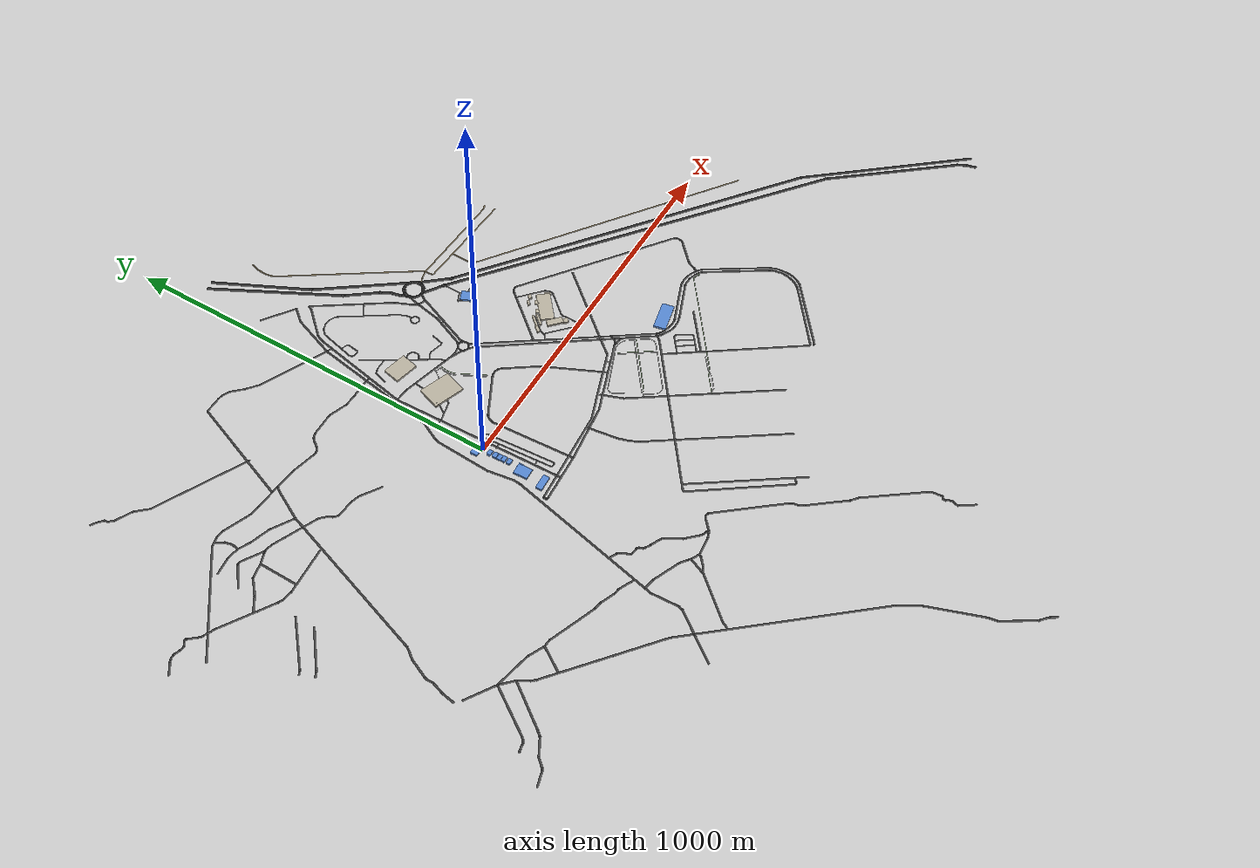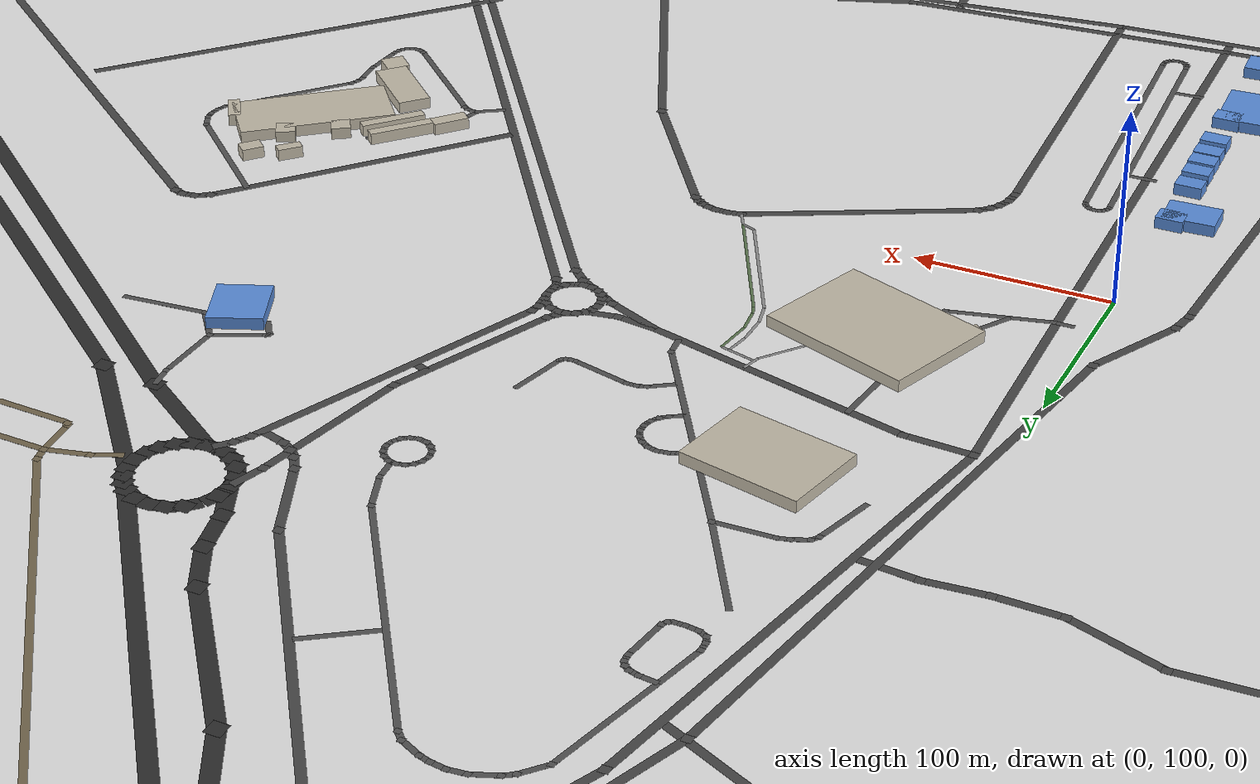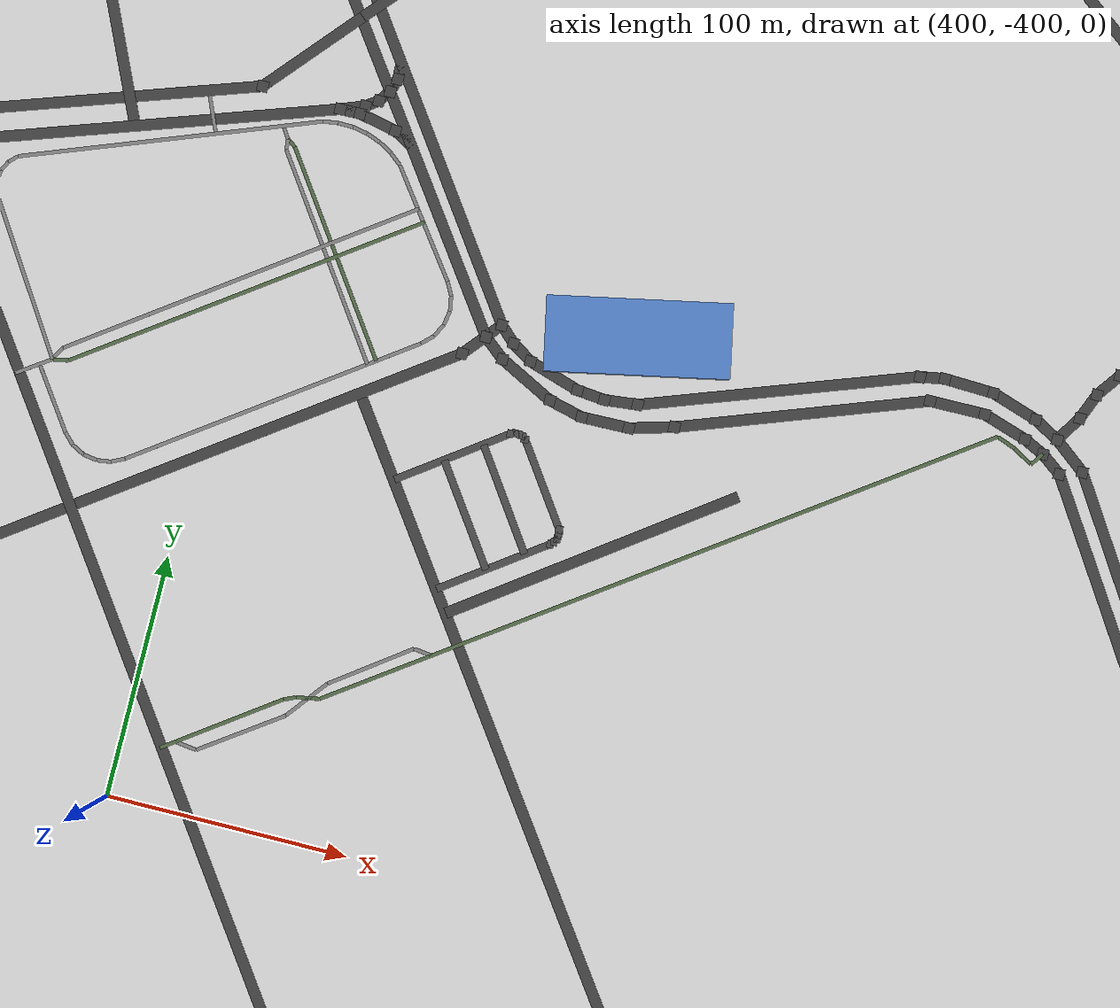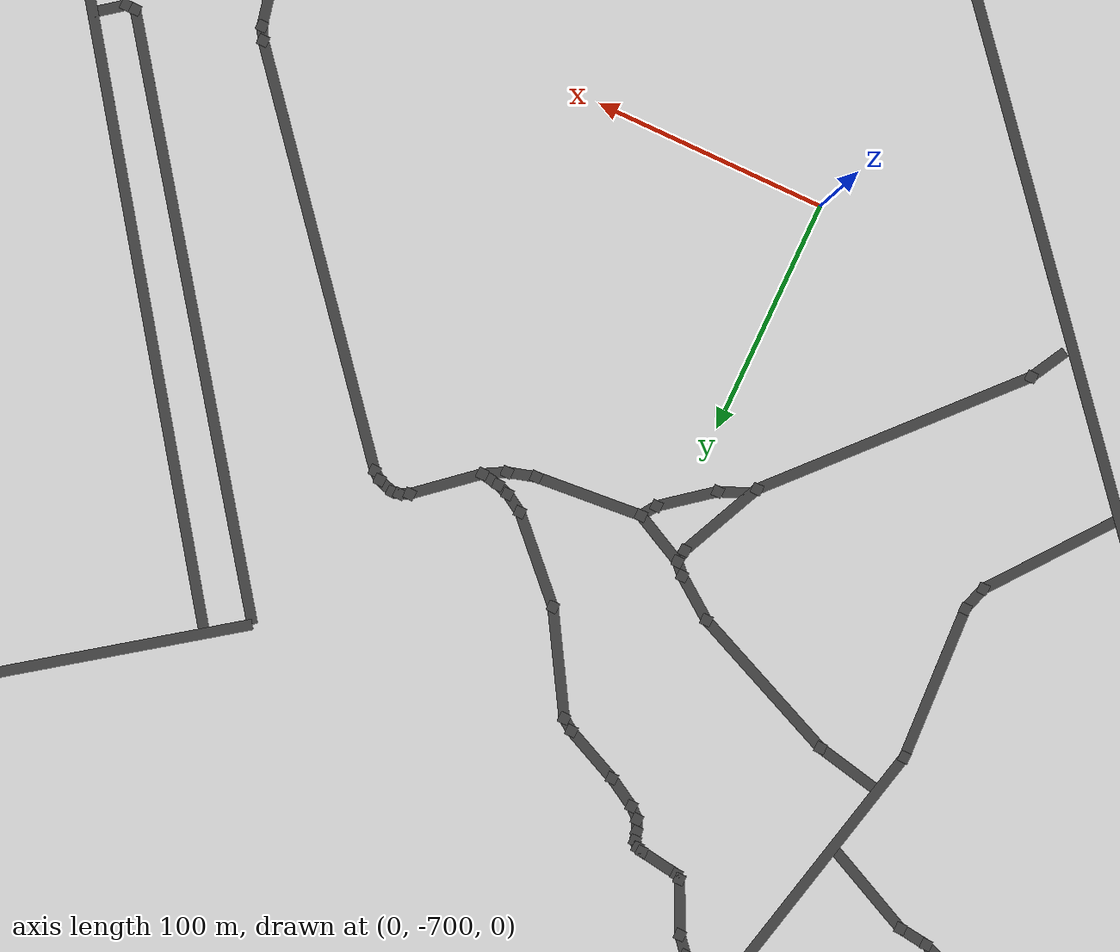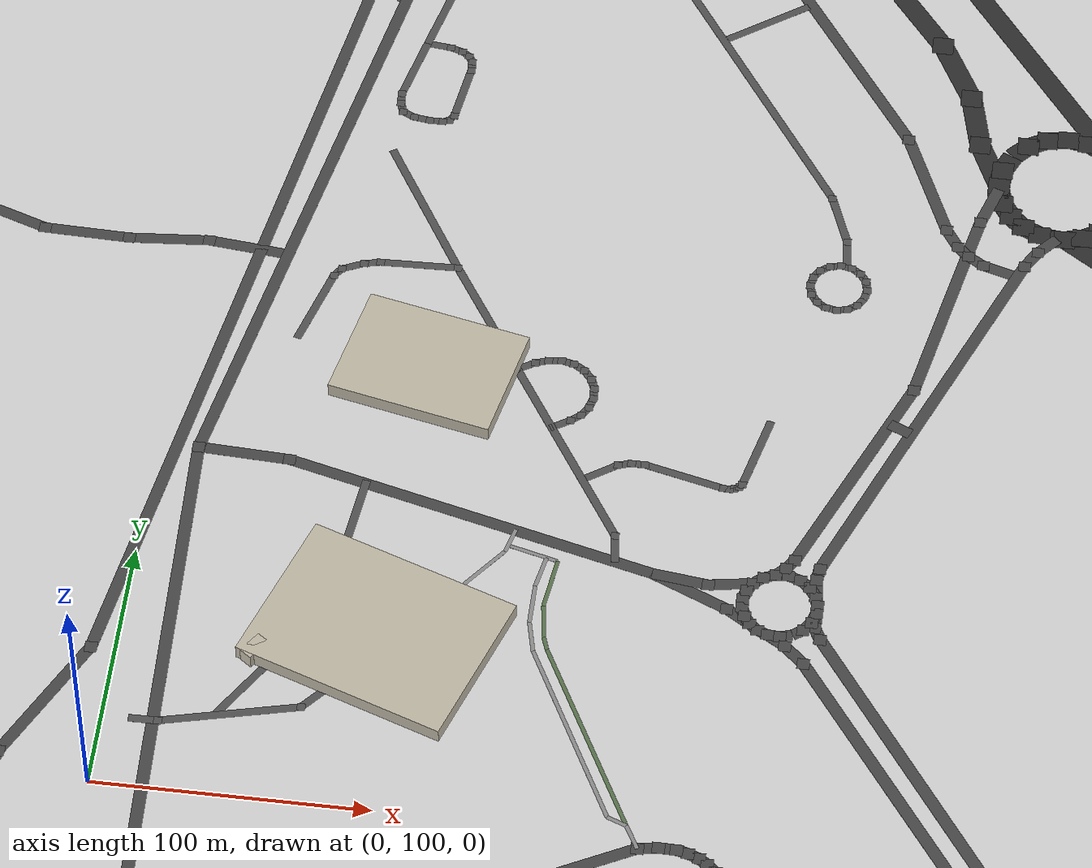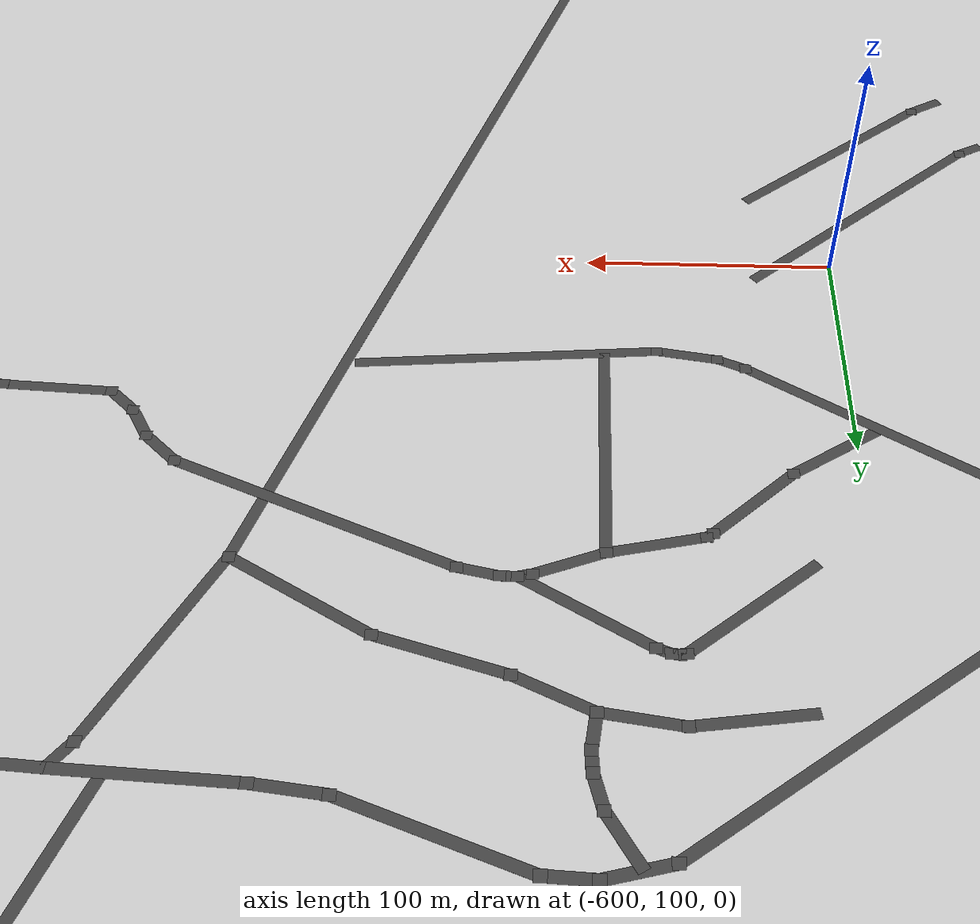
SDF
<?xml version="1.0" ?>
<!-- Auto-generated from OpenStreetMap. Included by the world SDF. -->
<sdf version="1.10">
  <model name="bld_شل_36555">
    <static>true</static>
    <pose>365.558 281.650 3.000 0 0 1.9603</pose>
    <link name="link">
      <collision name="c"><geometry><box><size>30.42 27.06 6.00</size></box></geometry></collision>
      <visual    name="v"><geometry><box><size>30.42 27.06 6.00</size></box></geometry>
        <material><ambient>0.35 0.55 0.85 1</ambient><diffuse>0.35 0.55 0.85 1</diffuse></material></visual>
    </link>
  </model>
  <model name="bld_Technopole_Sousse_9265">
    <static>true</static>
    <pose>92.655 293.082 3.000 0 0 -0.2131</pose>
    <link name="link">
      <collision name="c"><geometry><box><size>61.99 44.84 6.00</size></box></geometry></collision>
      <visual    name="v"><geometry><box><size>61.99 44.84 6.00</size></box></geometry>
        <material><ambient>0.75 0.72 0.65 1</ambient><diffuse>0.75 0.72 0.65 1</diffuse></material></visual>
    </link>
  </model>
  <model name="bld_Ecole_Supérieure_Privée_d_Ingénierie_et__56197">
    <static>true</static>
    <pose>561.976 -166.836 3.000 0 0 -2.9378</pose>
    <link name="link">
      <collision name="c"><geometry><box><size>75.50 30.70 6.00</size></box></geometry></collision>
      <visual    name="v"><geometry><box><size>75.50 30.70 6.00</size></box></geometry>
        <material><ambient>0.35 0.55 0.85 1</ambient><diffuse>0.35 0.55 0.85 1</diffuse></material></visual>
    </link>
  </model>
  <model name="bld_bld_1329657094_9077">
    <static>true</static>
    <pose>90.770 173.492 3.000 0 0 -0.3399</pose>
    <link name="link">
      <collision name="c"><geometry><box><size>80.45 60.18 6.00</size></box></geometry></collision>
      <visual    name="v"><geometry><box><size>80.45 60.18 6.00</size></box></geometry>
        <material><ambient>0.75 0.72 0.65 1</ambient><diffuse>0.75 0.72 0.65 1</diffuse></material></visual>
    </link>
  </model>
  <model name="bld_bld_1329657098_4936">
    <static>true</static>
    <pose>49.363 159.966 3.000 0 0 0.9523</pose>
    <link name="link">
      <collision name="c"><geometry><box><size>9.38 5.15 6.00</size></box></geometry></collision>
      <visual    name="v"><geometry><box><size>9.38 5.15 6.00</size></box></geometry>
        <material><ambient>0.75 0.72 0.65 1</ambient><diffuse>0.75 0.72 0.65 1</diffuse></material></visual>
    </link>
  </model>
  <model name="bld_YAMAICHI_ELECTRONICS_TUNISIE_792">
    <static>true</static>
    <pose>-7.921 -165.640 3.000 0 0 -3.0932</pose>
    <link name="link">
      <collision name="c"><geometry><box><size>38.23 15.93 6.00</size></box></geometry></collision>
      <visual    name="v"><geometry><box><size>38.23 15.93 6.00</size></box></geometry>
        <material><ambient>0.35 0.55 0.85 1</ambient><diffuse>0.35 0.55 0.85 1</diffuse></material></visual>
    </link>
  </model>
  <model name="bld_DACT_DRAEXLMAIER_510">
    <static>true</static>
    <pose>-5.100 -111.559 3.000 0 0 1.6244</pose>
    <link name="link">
      <collision name="c"><geometry><box><size>35.03 27.34 6.00</size></box></geometry></collision>
      <visual    name="v"><geometry><box><size>35.03 27.34 6.00</size></box></geometry>
        <material><ambient>0.35 0.55 0.85 1</ambient><diffuse>0.35 0.55 0.85 1</diffuse></material></visual>
    </link>
  </model>
  <model name="bld_Enova_Robotics_1070">
    <static>true</static>
    <pose>-10.710 10.436 3.000 0 0 -3.0950</pose>
    <link name="link">
      <collision name="c"><geometry><box><size>26.78 18.44 6.00</size></box></geometry></collision>
      <visual    name="v"><geometry><box><size>26.78 18.44 6.00</size></box></geometry>
        <material><ambient>0.35 0.55 0.85 1</ambient><diffuse>0.35 0.55 0.85 1</diffuse></material></visual>
    </link>
  </model>
  <model name="bld_bld_1329661322_43662">
    <static>true</static>
    <pose>436.622 97.862 3.000 0 0 0.6939</pose>
    <link name="link">
      <collision name="c"><geometry><box><size>80.42 34.95 6.00</size></box></geometry></collision>
      <visual    name="v"><geometry><box><size>80.42 34.95 6.00</size></box></geometry>
        <material><ambient>0.75 0.72 0.65 1</ambient><diffuse>0.75 0.72 0.65 1</diffuse></material></visual>
    </link>
  </model>
  <model name="bld_bld_1329661323_47470">
    <static>true</static>
    <pose>474.707 114.191 3.000 0 0 -0.9835</pose>
    <link name="link">
      <collision name="c"><geometry><box><size>17.67 6.36 6.00</size></box></geometry></collision>
      <visual    name="v"><geometry><box><size>17.67 6.36 6.00</size></box></geometry>
        <material><ambient>0.75 0.72 0.65 1</ambient><diffuse>0.75 0.72 0.65 1</diffuse></material></visual>
    </link>
  </model>
  <model name="bld_bld_1329661324_40838">
    <static>true</static>
    <pose>408.384 53.449 3.000 0 0 -0.7421</pose>
    <link name="link">
      <collision name="c"><geometry><box><size>40.59 16.90 6.00</size></box></geometry></collision>
      <visual    name="v"><geometry><box><size>40.59 16.90 6.00</size></box></geometry>
        <material><ambient>0.75 0.72 0.65 1</ambient><diffuse>0.75 0.72 0.65 1</diffuse></material></visual>
    </link>
  </model>
  <model name="bld_bld_1329661325_42494">
    <static>true</static>
    <pose>424.946 32.346 3.000 0 0 -0.7489</pose>
    <link name="link">
      <collision name="c"><geometry><box><size>12.37 12.14 6.00</size></box></geometry></collision>
      <visual    name="v"><geometry><box><size>12.37 12.14 6.00</size></box></geometry>
        <material><ambient>0.75 0.72 0.65 1</ambient><diffuse>0.75 0.72 0.65 1</diffuse></material></visual>
    </link>
  </model>
  <model name="bld_bld_1329661326_36703">
    <static>true</static>
    <pose>367.033 77.352 3.000 0 0 0.8544</pose>
    <link name="link">
      <collision name="c"><geometry><box><size>18.59 7.56 6.00</size></box></geometry></collision>
      <visual    name="v"><geometry><box><size>18.59 7.56 6.00</size></box></geometry>
        <material><ambient>0.75 0.72 0.65 1</ambient><diffuse>0.75 0.72 0.65 1</diffuse></material></visual>
    </link>
  </model>
  <model name="bld_bld_1329661327_44419">
    <static>true</static>
    <pose>444.191 146.703 3.000 0 0 0.8496</pose>
    <link name="link">
      <collision name="c"><geometry><box><size>11.27 8.26 6.00</size></box></geometry></collision>
      <visual    name="v"><geometry><box><size>11.27 8.26 6.00</size></box></geometry>
        <material><ambient>0.75 0.72 0.65 1</ambient><diffuse>0.75 0.72 0.65 1</diffuse></material></visual>
    </link>
  </model>
  <model name="bld_bld_1329661328_42610">
    <static>true</static>
    <pose>426.110 139.148 3.000 0 0 -2.3314</pose>
    <link name="link">
      <collision name="c"><geometry><box><size>12.75 5.79 6.00</size></box></geometry></collision>
      <visual    name="v"><geometry><box><size>12.75 5.79 6.00</size></box></geometry>
        <material><ambient>0.75 0.72 0.65 1</ambient><diffuse>0.75 0.72 0.65 1</diffuse></material></visual>
    </link>
  </model>
  <model name="bld_bld_1329661329_41477">
    <static>true</static>
    <pose>414.775 107.070 3.000 0 0 0.5929</pose>
    <link name="link">
      <collision name="c"><geometry><box><size>10.01 9.53 6.00</size></box></geometry></collision>
      <visual    name="v"><geometry><box><size>10.01 9.53 6.00</size></box></geometry>
        <material><ambient>0.75 0.72 0.65 1</ambient><diffuse>0.75 0.72 0.65 1</diffuse></material></visual>
    </link>
  </model>
  <model name="bld_bld_1329661330_43839">
    <static>true</static>
    <pose>438.391 122.315 3.000 0 0 0.4968</pose>
    <link name="link">
      <collision name="c"><geometry><box><size>10.04 9.82 6.00</size></box></geometry></collision>
      <visual    name="v"><geometry><box><size>10.04 9.82 6.00</size></box></geometry>
        <material><ambient>0.75 0.72 0.65 1</ambient><diffuse>0.75 0.72 0.65 1</diffuse></material></visual>
    </link>
  </model>
  <model name="bld_bld_1329663014_38541">
    <static>true</static>
    <pose>385.420 95.980 3.000 0 0 -2.3065</pose>
    <link name="link">
      <collision name="c"><geometry><box><size>33.77 5.49 6.00</size></box></geometry></collision>
      <visual    name="v"><geometry><box><size>33.77 5.49 6.00</size></box></geometry>
        <material><ambient>0.75 0.72 0.65 1</ambient><diffuse>0.75 0.72 0.65 1</diffuse></material></visual>
    </link>
  </model>
  <model name="bld_bld_1329663015_39368">
    <static>true</static>
    <pose>393.688 89.863 3.000 0 0 -2.3063</pose>
    <link name="link">
      <collision name="c"><geometry><box><size>33.77 5.49 6.00</size></box></geometry></collision>
      <visual    name="v"><geometry><box><size>33.77 5.49 6.00</size></box></geometry>
        <material><ambient>0.75 0.72 0.65 1</ambient><diffuse>0.75 0.72 0.65 1</diffuse></material></visual>
    </link>
  </model>
  <model name="bld_NOVATION_MECHATRONIC_CITY_261">
    <static>true</static>
    <pose>2.618 -98.217 3.000 0 0 0.0000</pose>
    <link name="link">
      <collision name="c"><geometry><box><size>14.00 10.00 6.00</size></box></geometry></collision>
      <visual    name="v"><geometry><box><size>14.00 10.00 6.00</size></box></geometry>
        <material><ambient>0.35 0.55 0.85 1</ambient><diffuse>0.35 0.55 0.85 1</diffuse></material></visual>
    </link>
  </model>
  <model name="bld_Proxym_IT_147">
    <static>true</static>
    <pose>1.471 -71.111 3.000 0 0 0.0000</pose>
    <link name="link">
      <collision name="c"><geometry><box><size>14.00 10.00 6.00</size></box></geometry></collision>
      <visual    name="v"><geometry><box><size>14.00 10.00 6.00</size></box></geometry>
        <material><ambient>0.35 0.55 0.85 1</ambient><diffuse>0.35 0.55 0.85 1</diffuse></material></visual>
    </link>
  </model>
  <model name="bld_Positrone_Tunisia_89">
    <static>true</static>
    <pose>0.894 -57.318 3.000 0 0 0.0000</pose>
    <link name="link">
      <collision name="c"><geometry><box><size>14.00 10.00 6.00</size></box></geometry></collision>
      <visual    name="v"><geometry><box><size>14.00 10.00 6.00</size></box></geometry>
        <material><ambient>0.35 0.55 0.85 1</ambient><diffuse>0.35 0.55 0.85 1</diffuse></material></visual>
    </link>
  </model>
  <model name="bld_Dejamobile_sousse_43">
    <static>true</static>
    <pose>0.433 -46.365 3.000 0 0 0.0000</pose>
    <link name="link">
      <collision name="c"><geometry><box><size>14.00 10.00 6.00</size></box></geometry></collision>
      <visual    name="v"><geometry><box><size>14.00 10.00 6.00</size></box></geometry>
        <material><ambient>0.35 0.55 0.85 1</ambient><diffuse>0.35 0.55 0.85 1</diffuse></material></visual>
    </link>
  </model>
  <model name="bld_CATHARSIS_CONSULTING_7">
    <static>true</static>
    <pose>-0.072 -34.309 3.000 0 0 0.0000</pose>
    <link name="link">
      <collision name="c"><geometry><box><size>14.00 10.00 6.00</size></box></geometry></collision>
      <visual    name="v"><geometry><box><size>14.00 10.00 6.00</size></box></geometry>
        <material><ambient>0.35 0.55 0.85 1</ambient><diffuse>0.35 0.55 0.85 1</diffuse></material></visual>
    </link>
  </model>
  <model name="bld_VEO_Worldwide_Services_68">
    <static>true</static>
    <pose>-0.686 -19.882 3.000 0 0 0.0000</pose>
    <link name="link">
      <collision name="c"><geometry><box><size>14.00 10.00 6.00</size></box></geometry></collision>
      <visual    name="v"><geometry><box><size>14.00 10.00 6.00</size></box></geometry>
        <material><ambient>0.35 0.55 0.85 1</ambient><diffuse>0.35 0.55 0.85 1</diffuse></material></visual>
    </link>
  </model>
  <model name="bld_Sagemcom_Software___Technologies_223">
    <static>true</static>
    <pose>-2.239 17.065 3.000 0 0 0.0000</pose>
    <link name="link">
      <collision name="c"><geometry><box><size>14.00 10.00 6.00</size></box></geometry></collision>
      <visual    name="v"><geometry><box><size>14.00 10.00 6.00</size></box></geometry>
        <material><ambient>0.35 0.55 0.85 1</ambient><diffuse>0.35 0.55 0.85 1</diffuse></material></visual>
    </link>
  </model>

  <model name="road_way_0">
    <static>true</static>
    <pose>0 0 0 0 0 0</pose>
    <link name="link">
      <visual name="seg_0">
        <pose>268.826 -1270.066 0.0140 0 0 2.1393</pose>
        <geometry><box><size>19.68 4.50 0.02</size></box></geometry>
        <material><ambient>0.27 0.27 0.27 1</ambient><diffuse>0.27 0.27 0.27 1</diffuse></material>
      </visual>
      <visual name="seg_1">
        <pose>253.905 -1253.118 0.0140 0 0 2.4091</pose>
        <geometry><box><size>25.88 4.50 0.02</size></box></geometry>
        <material><ambient>0.27 0.27 0.27 1</ambient><diffuse>0.27 0.27 0.27 1</diffuse></material>
      </visual>
      <visual name="seg_2">
        <pose>221.210 -1208.078 0.0140 0 0 2.1359</pose>
        <geometry><box><size>86.17 4.50 0.02</size></box></geometry>
        <material><ambient>0.27 0.27 0.27 1</ambient><diffuse>0.27 0.27 0.27 1</diffuse></material>
      </visual>
      <visual name="seg_3">
        <pose>196.503 -1161.157 0.0140 0 0 1.7246</pose>
        <geometry><box><size>21.32 4.50 0.02</size></box></geometry>
        <material><ambient>0.27 0.27 0.27 1</ambient><diffuse>0.27 0.27 0.27 1</diffuse></material>
      </visual>
      <visual name="seg_4">
        <pose>172.036 -1086.027 0.0140 0 0 1.9106</pose>
        <geometry><box><size>137.02 4.50 0.02</size></box></geometry>
        <material><ambient>0.27 0.27 0.27 1</ambient><diffuse>0.27 0.27 0.27 1</diffuse></material>
      </visual>
      <visual name="seg_5">
        <pose>133.695 -995.369 0.0140 0 0 2.1075</pose>
        <geometry><box><size>60.66 4.50 0.02</size></box></geometry>
        <material><ambient>0.27 0.27 0.27 1</ambient><diffuse>0.27 0.27 0.27 1</diffuse></material>
      </visual>
      <visual name="seg_6">
        <pose>-40.106 -782.821 0.0140 0 0 2.2746</pose>
        <geometry><box><size>489.21 4.50 0.02</size></box></geometry>
        <material><ambient>0.27 0.27 0.27 1</ambient><diffuse>0.27 0.27 0.27 1</diffuse></material>
      </visual>
      <visual name="seg_7">
        <pose>-312.967 -501.650 0.0140 0 0 2.4509</pose>
        <geometry><box><size>297.26 4.50 0.02</size></box></geometry>
        <material><ambient>0.27 0.27 0.27 1</ambient><diffuse>0.27 0.27 0.27 1</diffuse></material>
      </visual>
      <visual name="seg_8">
        <pose>-431.556 -402.181 0.0140 0 0 2.2701</pose>
        <geometry><box><size>12.50 4.50 0.02</size></box></geometry>
        <material><ambient>0.27 0.27 0.27 1</ambient><diffuse>0.27 0.27 0.27 1</diffuse></material>
      </visual>
      <visual name="seg_9">
        <pose>-443.232 -384.514 0.0140 0 0 2.1068</pose>
        <geometry><box><size>29.97 4.50 0.02</size></box></geometry>
        <material><ambient>0.27 0.27 0.27 1</ambient><diffuse>0.27 0.27 0.27 1</diffuse></material>
      </visual>
      <visual name="seg_10">
        <pose>-465.149 -357.770 0.0140 0 0 2.3705</pose>
        <geometry><box><size>39.77 4.50 0.02</size></box></geometry>
        <material><ambient>0.27 0.27 0.27 1</ambient><diffuse>0.27 0.27 0.27 1</diffuse></material>
      </visual>
      <visual name="seg_11">
        <pose>-513.243 -322.320 0.0140 0 0 2.5736</pose>
        <geometry><box><size>80.27 4.50 0.02</size></box></geometry>
        <material><ambient>0.27 0.27 0.27 1</ambient><diffuse>0.27 0.27 0.27 1</diffuse></material>
      </visual>
      <visual name="seg_12">
        <pose>263.527 -1261.773 0.0150 0 0 0.0000</pose>
        <geometry><box><size>4.50 4.50 0.02</size></box></geometry>
        <material><ambient>0.27 0.27 0.27 1</ambient><diffuse>0.27 0.27 0.27 1</diffuse></material>
      </visual>
      <visual name="seg_13">
        <pose>244.282 -1244.463 0.0150 0 0 0.0000</pose>
        <geometry><box><size>4.50 4.50 0.02</size></box></geometry>
        <material><ambient>0.27 0.27 0.27 1</ambient><diffuse>0.27 0.27 0.27 1</diffuse></material>
      </visual>
      <visual name="seg_14">
        <pose>198.137 -1171.693 0.0150 0 0 0.0000</pose>
        <geometry><box><size>4.50 4.50 0.02</size></box></geometry>
        <material><ambient>0.27 0.27 0.27 1</ambient><diffuse>0.27 0.27 0.27 1</diffuse></material>
      </visual>
      <visual name="seg_15">
        <pose>194.870 -1150.621 0.0150 0 0 0.0000</pose>
        <geometry><box><size>4.50 4.50 0.02</size></box></geometry>
        <material><ambient>0.27 0.27 0.27 1</ambient><diffuse>0.27 0.27 0.27 1</diffuse></material>
      </visual>
      <visual name="seg_16">
        <pose>149.203 -1021.434 0.0150 0 0 0.0000</pose>
        <geometry><box><size>4.50 4.50 0.02</size></box></geometry>
        <material><ambient>0.27 0.27 0.27 1</ambient><diffuse>0.27 0.27 0.27 1</diffuse></material>
      </visual>
      <visual name="seg_17">
        <pose>118.187 -969.303 0.0150 0 0 0.0000</pose>
        <geometry><box><size>4.50 4.50 0.02</size></box></geometry>
        <material><ambient>0.27 0.27 0.27 1</ambient><diffuse>0.27 0.27 0.27 1</diffuse></material>
      </visual>
      <visual name="seg_18">
        <pose>-198.399 -596.339 0.0150 0 0 0.0000</pose>
        <geometry><box><size>4.50 4.50 0.02</size></box></geometry>
        <material><ambient>0.27 0.27 0.27 1</ambient><diffuse>0.27 0.27 0.27 1</diffuse></material>
      </visual>
      <visual name="seg_19">
        <pose>-427.534 -406.962 0.0150 0 0 0.0000</pose>
        <geometry><box><size>4.50 4.50 0.02</size></box></geometry>
        <material><ambient>0.27 0.27 0.27 1</ambient><diffuse>0.27 0.27 0.27 1</diffuse></material>
      </visual>
      <visual name="seg_20">
        <pose>-435.577 -397.399 0.0150 0 0 0.0000</pose>
        <geometry><box><size>4.50 4.50 0.02</size></box></geometry>
        <material><ambient>0.27 0.27 0.27 1</ambient><diffuse>0.27 0.27 0.27 1</diffuse></material>
      </visual>
      <visual name="seg_21">
        <pose>-450.886 -371.629 0.0150 0 0 0.0000</pose>
        <geometry><box><size>4.50 4.50 0.02</size></box></geometry>
        <material><ambient>0.27 0.27 0.27 1</ambient><diffuse>0.27 0.27 0.27 1</diffuse></material>
      </visual>
      <visual name="seg_22">
        <pose>-479.411 -343.910 0.0150 0 0 0.0000</pose>
        <geometry><box><size>4.50 4.50 0.02</size></box></geometry>
        <material><ambient>0.27 0.27 0.27 1</ambient><diffuse>0.27 0.27 0.27 1</diffuse></material>
      </visual>
      <visual name="seg_23">
        <pose>76.190 646.594 0.0140 0 0 -0.6097</pose>
        <geometry><box><size>94.07 4.50 0.02</size></box></geometry>
        <material><ambient>0.28 0.28 0.28 1</ambient><diffuse>0.28 0.28 0.28 1</diffuse></material>
      </visual>
      <visual name="seg_24">
        <pose>101.018 603.263 0.0140 0 0 -2.2679</pose>
        <geometry><box><size>42.77 4.50 0.02</size></box></geometry>
        <material><ambient>0.28 0.28 0.28 1</ambient><diffuse>0.28 0.28 0.28 1</diffuse></material>
      </visual>
      <visual name="seg_25">
        <pose>66.437 531.178 0.0140 0 0 -1.9291</pose>
        <geometry><box><size>118.93 4.50 0.02</size></box></geometry>
        <material><ambient>0.28 0.28 0.28 1</ambient><diffuse>0.28 0.28 0.28 1</diffuse></material>
      </visual>
      <visual name="seg_26">
        <pose>18.428 315.941 0.0140 0 0 -1.7394</pose>
        <geometry><box><size>323.69 4.50 0.02</size></box></geometry>
        <material><ambient>0.28 0.28 0.28 1</ambient><diffuse>0.28 0.28 0.28 1</diffuse></material>
      </visual>
      <visual name="seg_27">
        <pose>-20.897 132.665 0.0140 0 0 -2.0446</pose>
        <geometry><box><size>53.33 4.50 0.02</size></box></geometry>
        <material><ambient>0.28 0.28 0.28 1</ambient><diffuse>0.28 0.28 0.28 1</diffuse></material>
      </visual>
      <visual name="seg_28">
        <pose>-34.396 102.642 0.0140 0 0 -1.7792</pose>
        <geometry><box><size>12.87 4.50 0.02</size></box></geometry>
        <material><ambient>0.28 0.28 0.28 1</ambient><diffuse>0.28 0.28 0.28 1</diffuse></material>
      </visual>
      <visual name="seg_29">
        <pose>-39.722 28.431 0.0140 0 0 -1.6295</pose>
        <geometry><box><size>136.07 4.50 0.02</size></box></geometry>
        <material><ambient>0.28 0.28 0.28 1</ambient><diffuse>0.28 0.28 0.28 1</diffuse></material>
      </visual>
      <visual name="seg_30">
        <pose>-38.874 -72.046 0.0140 0 0 -1.4231</pose>
        <geometry><box><size>65.84 4.50 0.02</size></box></geometry>
        <material><ambient>0.28 0.28 0.28 1</ambient><diffuse>0.28 0.28 0.28 1</diffuse></material>
      </visual>
      <visual name="seg_31">
        <pose>-34.758 -113.568 0.0140 0 0 -1.6517</pose>
        <geometry><box><size>17.98 4.50 0.02</size></box></geometry>
        <material><ambient>0.28 0.28 0.28 1</ambient><diffuse>0.28 0.28 0.28 1</diffuse></material>
      </visual>
      <visual name="seg_32">
        <pose>-80.961 -316.492 0.0140 0 0 -1.8011</pose>
        <geometry><box><size>398.45 4.50 0.02</size></box></geometry>
        <material><ambient>0.28 0.28 0.28 1</ambient><diffuse>0.28 0.28 0.28 1</diffuse></material>
      </visual>
      <visual name="seg_33">
        <pose>-124.903 -543.234 0.0140 0 0 -1.5240</pose>
        <geometry><box><size>65.63 4.50 0.02</size></box></geometry>
        <material><ambient>0.28 0.28 0.28 1</ambient><diffuse>0.28 0.28 0.28 1</diffuse></material>
      </visual>
      <visual name="seg_34">
        <pose>-124.966 -581.255 0.0140 0 0 -1.8666</pose>
        <geometry><box><size>10.96 4.50 0.02</size></box></geometry>
        <material><ambient>0.28 0.28 0.28 1</ambient><diffuse>0.28 0.28 0.28 1</diffuse></material>
      </visual>
      <visual name="seg_35">
        <pose>-168.674 -640.588 0.0140 0 0 -2.2323</pose>
        <geometry><box><size>137.10 4.50 0.02</size></box></geometry>
        <material><ambient>0.28 0.28 0.28 1</ambient><diffuse>0.28 0.28 0.28 1</diffuse></material>
      </visual>
      <visual name="seg_36">
        <pose>114.748 619.660 0.0150 0 0 0.0000</pose>
        <geometry><box><size>4.50 4.50 0.02</size></box></geometry>
        <material><ambient>0.28 0.28 0.28 1</ambient><diffuse>0.28 0.28 0.28 1</diffuse></material>
      </visual>
      <visual name="seg_37">
        <pose>87.289 586.865 0.0150 0 0 0.0000</pose>
        <geometry><box><size>4.50 4.50 0.02</size></box></geometry>
        <material><ambient>0.28 0.28 0.28 1</ambient><diffuse>0.28 0.28 0.28 1</diffuse></material>
      </visual>
      <visual name="seg_38">
        <pose>45.585 475.490 0.0150 0 0 0.0000</pose>
        <geometry><box><size>4.50 4.50 0.02</size></box></geometry>
        <material><ambient>0.28 0.28 0.28 1</ambient><diffuse>0.28 0.28 0.28 1</diffuse></material>
      </visual>
      <visual name="seg_39">
        <pose>-8.729 156.393 0.0150 0 0 0.0000</pose>
        <geometry><box><size>4.50 4.50 0.02</size></box></geometry>
        <material><ambient>0.28 0.28 0.28 1</ambient><diffuse>0.28 0.28 0.28 1</diffuse></material>
      </visual>
      <visual name="seg_40">
        <pose>-33.065 108.937 0.0150 0 0 0.0000</pose>
        <geometry><box><size>4.50 4.50 0.02</size></box></geometry>
        <material><ambient>0.28 0.28 0.28 1</ambient><diffuse>0.28 0.28 0.28 1</diffuse></material>
      </visual>
      <visual name="seg_41">
        <pose>-35.728 96.347 0.0150 0 0 0.0000</pose>
        <geometry><box><size>4.50 4.50 0.02</size></box></geometry>
        <material><ambient>0.28 0.28 0.28 1</ambient><diffuse>0.28 0.28 0.28 1</diffuse></material>
      </visual>
      <visual name="seg_42">
        <pose>-43.717 -39.485 0.0150 0 0 0.0000</pose>
        <geometry><box><size>4.50 4.50 0.02</size></box></geometry>
        <material><ambient>0.28 0.28 0.28 1</ambient><diffuse>0.28 0.28 0.28 1</diffuse></material>
      </visual>
      <visual name="seg_43">
        <pose>-34.031 -104.607 0.0150 0 0 0.0000</pose>
        <geometry><box><size>4.50 4.50 0.02</size></box></geometry>
        <material><ambient>0.28 0.28 0.28 1</ambient><diffuse>0.28 0.28 0.28 1</diffuse></material>
      </visual>
      <visual name="seg_44">
        <pose>-35.484 -122.529 0.0150 0 0 0.0000</pose>
        <geometry><box><size>4.50 4.50 0.02</size></box></geometry>
        <material><ambient>0.28 0.28 0.28 1</ambient><diffuse>0.28 0.28 0.28 1</diffuse></material>
      </visual>
      <visual name="seg_45">
        <pose>-126.438 -510.456 0.0150 0 0 0.0000</pose>
        <geometry><box><size>4.50 4.50 0.02</size></box></geometry>
        <material><ambient>0.28 0.28 0.28 1</ambient><diffuse>0.28 0.28 0.28 1</diffuse></material>
      </visual>
      <visual name="seg_46">
        <pose>-123.369 -576.012 0.0150 0 0 0.0000</pose>
        <geometry><box><size>4.50 4.50 0.02</size></box></geometry>
        <material><ambient>0.28 0.28 0.28 1</ambient><diffuse>0.28 0.28 0.28 1</diffuse></material>
      </visual>
      <visual name="seg_47">
        <pose>-126.564 -586.498 0.0150 0 0 0.0000</pose>
        <geometry><box><size>4.50 4.50 0.02</size></box></geometry>
        <material><ambient>0.28 0.28 0.28 1</ambient><diffuse>0.28 0.28 0.28 1</diffuse></material>
      </visual>
      <visual name="seg_48">
        <pose>-29.969 511.129 0.0140 0 0 2.7144</pose>
        <geometry><box><size>194.23 4.50 0.02</size></box></geometry>
        <material><ambient>0.28 0.28 0.28 1</ambient><diffuse>0.28 0.28 0.28 1</diffuse></material>
      </visual>
      <visual name="seg_49">
        <pose>-132.684 562.792 0.0140 0 0 2.4683</pose>
        <geometry><box><size>36.65 4.50 0.02</size></box></geometry>
        <material><ambient>0.28 0.28 0.28 1</ambient><diffuse>0.28 0.28 0.28 1</diffuse></material>
      </visual>
      <visual name="seg_50">
        <pose>-160.058 587.750 0.0140 0 0 2.3380</pose>
        <geometry><box><size>37.59 4.50 0.02</size></box></geometry>
        <material><ambient>0.28 0.28 0.28 1</ambient><diffuse>0.28 0.28 0.28 1</diffuse></material>
      </visual>
      <visual name="seg_51">
        <pose>-181.411 604.676 0.0140 0 0 2.7535</pose>
        <geometry><box><size>17.94 4.50 0.02</size></box></geometry>
        <material><ambient>0.28 0.28 0.28 1</ambient><diffuse>0.28 0.28 0.28 1</diffuse></material>
      </visual>
      <visual name="seg_52">
        <pose>-195.664 608.940 0.0140 0 0 2.9967</pose>
        <geometry><box><size>12.02 4.50 0.02</size></box></geometry>
        <material><ambient>0.28 0.28 0.28 1</ambient><diffuse>0.28 0.28 0.28 1</diffuse></material>
      </visual>
      <visual name="seg_53">
        <pose>-222.938 609.380 0.0140 0 0 -3.1215</pose>
        <geometry><box><size>42.66 4.50 0.02</size></box></geometry>
        <material><ambient>0.28 0.28 0.28 1</ambient><diffuse>0.28 0.28 0.28 1</diffuse></material>
      </visual>
      <visual name="seg_54">
        <pose>-118.359 551.365 0.0150 0 0 0.0000</pose>
        <geometry><box><size>4.50 4.50 0.02</size></box></geometry>
        <material><ambient>0.28 0.28 0.28 1</ambient><diffuse>0.28 0.28 0.28 1</diffuse></material>
      </visual>
      <visual name="seg_55">
        <pose>-147.010 574.219 0.0150 0 0 0.0000</pose>
        <geometry><box><size>4.50 4.50 0.02</size></box></geometry>
        <material><ambient>0.28 0.28 0.28 1</ambient><diffuse>0.28 0.28 0.28 1</diffuse></material>
      </visual>
      <visual name="seg_56">
        <pose>-173.106 601.281 0.0150 0 0 0.0000</pose>
        <geometry><box><size>4.50 4.50 0.02</size></box></geometry>
        <material><ambient>0.28 0.28 0.28 1</ambient><diffuse>0.28 0.28 0.28 1</diffuse></material>
      </visual>
      <visual name="seg_57">
        <pose>-189.715 608.072 0.0150 0 0 0.0000</pose>
        <geometry><box><size>4.50 4.50 0.02</size></box></geometry>
        <material><ambient>0.28 0.28 0.28 1</ambient><diffuse>0.28 0.28 0.28 1</diffuse></material>
      </visual>
      <visual name="seg_58">
        <pose>-201.613 609.808 0.0150 0 0 0.0000</pose>
        <geometry><box><size>4.50 4.50 0.02</size></box></geometry>
        <material><ambient>0.28 0.28 0.28 1</ambient><diffuse>0.28 0.28 0.28 1</diffuse></material>
      </visual>
      <visual name="seg_59">
        <pose>-467.780 155.118 0.0140 0 0 -3.0638</pose>
        <geometry><box><size>118.51 4.50 0.02</size></box></geometry>
        <material><ambient>0.28 0.28 0.28 1</ambient><diffuse>0.28 0.28 0.28 1</diffuse></material>
      </visual>
      <visual name="seg_60">
        <pose>-538.599 152.452 0.0140 0 0 2.9781</pose>
        <geometry><box><size>23.80 4.50 0.02</size></box></geometry>
        <material><ambient>0.28 0.28 0.28 1</ambient><diffuse>0.28 0.28 0.28 1</diffuse></material>
      </visual>
      <visual name="seg_61">
        <pose>-555.732 156.721 0.0140 0 0 2.7332</pose>
        <geometry><box><size>11.74 4.50 0.02</size></box></geometry>
        <material><ambient>0.28 0.28 0.28 1</ambient><diffuse>0.28 0.28 0.28 1</diffuse></material>
      </visual>
      <visual name="seg_62">
        <pose>-621.316 196.702 0.0140 0 0 2.5827</pose>
        <geometry><box><size>142.00 4.50 0.02</size></box></geometry>
        <material><ambient>0.28 0.28 0.28 1</ambient><diffuse>0.28 0.28 0.28 1</diffuse></material>
      </visual>
      <visual name="seg_63">
        <pose>-695.340 240.522 0.0140 0 0 2.7218</pose>
        <geometry><box><size>30.29 4.50 0.02</size></box></geometry>
        <material><ambient>0.28 0.28 0.28 1</ambient><diffuse>0.28 0.28 0.28 1</diffuse></material>
      </visual>
      <visual name="seg_64">
        <pose>-711.985 249.055 0.0140 0 0 2.4441</pose>
        <geometry><box><size>7.35 4.50 0.02</size></box></geometry>
        <material><ambient>0.28 0.28 0.28 1</ambient><diffuse>0.28 0.28 0.28 1</diffuse></material>
      </visual>
      <visual name="seg_65">
        <pose>-722.763 260.922 0.0140 0 0 2.2680</pose>
        <geometry><box><size>24.80 4.50 0.02</size></box></geometry>
        <material><ambient>0.28 0.28 0.28 1</ambient><diffuse>0.28 0.28 0.28 1</diffuse></material>
      </visual>
      <visual name="seg_66">
        <pose>-731.799 271.152 0.0140 0 0 2.5488</pose>
        <geometry><box><size>2.59 4.50 0.02</size></box></geometry>
        <material><ambient>0.28 0.28 0.28 1</ambient><diffuse>0.28 0.28 0.28 1</diffuse></material>
      </visual>
      <visual name="seg_67">
        <pose>-733.961 272.132 0.0140 0 0 2.9104</pose>
        <geometry><box><size>2.23 4.50 0.02</size></box></geometry>
        <material><ambient>0.28 0.28 0.28 1</ambient><diffuse>0.28 0.28 0.28 1</diffuse></material>
      </visual>
      <visual name="seg_68">
        <pose>-736.380 272.104 0.0140 0 0 -2.9315</pose>
        <geometry><box><size>2.72 4.50 0.02</size></box></geometry>
        <material><ambient>0.28 0.28 0.28 1</ambient><diffuse>0.28 0.28 0.28 1</diffuse></material>
      </visual>
      <visual name="seg_69">
        <pose>-743.466 267.712 0.0140 0 0 -2.5217</pose>
        <geometry><box><size>14.14 4.50 0.02</size></box></geometry>
        <material><ambient>0.28 0.28 0.28 1</ambient><diffuse>0.28 0.28 0.28 1</diffuse></material>
      </visual>
      <visual name="seg_70">
        <pose>-754.605 264.746 0.0140 0 0 2.9328</pose>
        <geometry><box><size>11.01 4.50 0.02</size></box></geometry>
        <material><ambient>0.28 0.28 0.28 1</ambient><diffuse>0.28 0.28 0.28 1</diffuse></material>
      </visual>
      <visual name="seg_71">
        <pose>-765.965 268.219 0.0140 0 0 2.7695</pose>
        <geometry><box><size>12.83 4.50 0.02</size></box></geometry>
        <material><ambient>0.28 0.28 0.28 1</ambient><diffuse>0.28 0.28 0.28 1</diffuse></material>
      </visual>
      <visual name="seg_72">
        <pose>-775.484 270.551 0.0140 0 0 3.1416</pose>
        <geometry><box><size>7.09 4.50 0.02</size></box></geometry>
        <material><ambient>0.28 0.28 0.28 1</ambient><diffuse>0.28 0.28 0.28 1</diffuse></material>
      </visual>
      <visual name="seg_73">
        <pose>-781.387 270.094 0.0140 0 0 -2.9506</pose>
        <geometry><box><size>4.81 4.50 0.02</size></box></geometry>
        <material><ambient>0.28 0.28 0.28 1</ambient><diffuse>0.28 0.28 0.28 1</diffuse></material>
      </visual>
      <visual name="seg_74">
        <pose>-786.623 268.430 0.0140 0 0 -2.7439</pose>
        <geometry><box><size>6.24 4.50 0.02</size></box></geometry>
        <material><ambient>0.28 0.28 0.28 1</ambient><diffuse>0.28 0.28 0.28 1</diffuse></material>
      </visual>
      <visual name="seg_75">
        <pose>-803.417 257.476 0.0140 0 0 -2.5307</pose>
        <geometry><box><size>33.98 4.50 0.02</size></box></geometry>
        <material><ambient>0.28 0.28 0.28 1</ambient><diffuse>0.28 0.28 0.28 1</diffuse></material>
      </visual>
      <visual name="seg_76">
        <pose>-526.856 150.515 0.0150 0 0 0.0000</pose>
        <geometry><box><size>4.50 4.50 0.02</size></box></geometry>
        <material><ambient>0.28 0.28 0.28 1</ambient><diffuse>0.28 0.28 0.28 1</diffuse></material>
      </visual>
      <visual name="seg_77">
        <pose>-550.343 154.389 0.0150 0 0 0.0000</pose>
        <geometry><box><size>4.50 4.50 0.02</size></box></geometry>
        <material><ambient>0.28 0.28 0.28 1</ambient><diffuse>0.28 0.28 0.28 1</diffuse></material>
      </visual>
      <visual name="seg_78">
        <pose>-561.121 159.053 0.0150 0 0 0.0000</pose>
        <geometry><box><size>4.50 4.50 0.02</size></box></geometry>
        <material><ambient>0.28 0.28 0.28 1</ambient><diffuse>0.28 0.28 0.28 1</diffuse></material>
      </visual>
      <visual name="seg_79">
        <pose>-681.511 234.350 0.0150 0 0 0.0000</pose>
        <geometry><box><size>4.50 4.50 0.02</size></box></geometry>
        <material><ambient>0.28 0.28 0.28 1</ambient><diffuse>0.28 0.28 0.28 1</diffuse></material>
      </visual>
      <visual name="seg_80">
        <pose>-709.169 246.695 0.0150 0 0 0.0000</pose>
        <geometry><box><size>4.50 4.50 0.02</size></box></geometry>
        <material><ambient>0.28 0.28 0.28 1</ambient><diffuse>0.28 0.28 0.28 1</diffuse></material>
      </visual>
      <visual name="seg_81">
        <pose>-714.802 251.415 0.0150 0 0 0.0000</pose>
        <geometry><box><size>4.50 4.50 0.02</size></box></geometry>
        <material><ambient>0.28 0.28 0.28 1</ambient><diffuse>0.28 0.28 0.28 1</diffuse></material>
      </visual>
      <visual name="seg_82">
        <pose>-730.725 270.428 0.0150 0 0 0.0000</pose>
        <geometry><box><size>4.50 4.50 0.02</size></box></geometry>
        <material><ambient>0.28 0.28 0.28 1</ambient><diffuse>0.28 0.28 0.28 1</diffuse></material>
      </visual>
      <visual name="seg_83">
        <pose>-732.873 271.876 0.0150 0 0 0.0000</pose>
        <geometry><box><size>4.50 4.50 0.02</size></box></geometry>
        <material><ambient>0.28 0.28 0.28 1</ambient><diffuse>0.28 0.28 0.28 1</diffuse></material>
      </visual>
      <visual name="seg_84">
        <pose>-735.049 272.388 0.0150 0 0 0.0000</pose>
        <geometry><box><size>4.50 4.50 0.02</size></box></geometry>
        <material><ambient>0.28 0.28 0.28 1</ambient><diffuse>0.28 0.28 0.28 1</diffuse></material>
      </visual>
      <visual name="seg_85">
        <pose>-737.712 271.820 0.0150 0 0 0.0000</pose>
        <geometry><box><size>4.50 4.50 0.02</size></box></geometry>
        <material><ambient>0.28 0.28 0.28 1</ambient><diffuse>0.28 0.28 0.28 1</diffuse></material>
      </visual>
      <visual name="seg_86">
        <pose>-749.221 263.605 0.0150 0 0 0.0000</pose>
        <geometry><box><size>4.50 4.50 0.02</size></box></geometry>
        <material><ambient>0.28 0.28 0.28 1</ambient><diffuse>0.28 0.28 0.28 1</diffuse></material>
      </visual>
      <visual name="seg_87">
        <pose>-759.990 265.887 0.0150 0 0 0.0000</pose>
        <geometry><box><size>4.50 4.50 0.02</size></box></geometry>
        <material><ambient>0.28 0.28 0.28 1</ambient><diffuse>0.28 0.28 0.28 1</diffuse></material>
      </visual>
      <visual name="seg_88">
        <pose>-771.941 270.551 0.0150 0 0 0.0000</pose>
        <geometry><box><size>4.50 4.50 0.02</size></box></geometry>
        <material><ambient>0.28 0.28 0.28 1</ambient><diffuse>0.28 0.28 0.28 1</diffuse></material>
      </visual>
      <visual name="seg_89">
        <pose>-779.027 270.551 0.0150 0 0 0.0000</pose>
        <geometry><box><size>4.50 4.50 0.02</size></box></geometry>
        <material><ambient>0.28 0.28 0.28 1</ambient><diffuse>0.28 0.28 0.28 1</diffuse></material>
      </visual>
      <visual name="seg_90">
        <pose>-783.748 269.638 0.0150 0 0 0.0000</pose>
        <geometry><box><size>4.50 4.50 0.02</size></box></geometry>
        <material><ambient>0.28 0.28 0.28 1</ambient><diffuse>0.28 0.28 0.28 1</diffuse></material>
      </visual>
      <visual name="seg_91">
        <pose>-789.498 267.222 0.0150 0 0 0.0000</pose>
        <geometry><box><size>4.50 4.50 0.02</size></box></geometry>
        <material><ambient>0.28 0.28 0.28 1</ambient><diffuse>0.28 0.28 0.28 1</diffuse></material>
      </visual>
      <visual name="seg_92">
        <pose>367.642 345.252 0.0150 0 0 -1.4210</pose>
        <geometry><box><size>12.22 3.00 0.02</size></box></geometry>
        <material><ambient>0.32 0.32 0.32 1</ambient><diffuse>0.32 0.32 0.32 1</diffuse></material>
      </visual>
      <visual name="seg_93">
        <pose>368.057 322.097 0.0150 0 0 -1.5998</pose>
        <geometry><box><size>34.25 3.00 0.02</size></box></geometry>
        <material><ambient>0.32 0.32 0.32 1</ambient><diffuse>0.32 0.32 0.32 1</diffuse></material>
      </visual>
      <visual name="seg_94">
        <pose>374.082 296.945 0.0150 0 0 -0.8891</pose>
        <geometry><box><size>20.70 3.00 0.02</size></box></geometry>
        <material><ambient>0.32 0.32 0.32 1</ambient><diffuse>0.32 0.32 0.32 1</diffuse></material>
      </visual>
      <visual name="seg_95">
        <pose>402.011 290.711 0.0150 0 0 0.0840</pose>
        <geometry><box><size>42.97 3.00 0.02</size></box></geometry>
        <material><ambient>0.32 0.32 0.32 1</ambient><diffuse>0.32 0.32 0.32 1</diffuse></material>
      </visual>
      <visual name="seg_96">
        <pose>368.553 339.213 0.0160 0 0 0.0000</pose>
        <geometry><box><size>3.00 3.00 0.02</size></box></geometry>
        <material><ambient>0.32 0.32 0.32 1</ambient><diffuse>0.32 0.32 0.32 1</diffuse></material>
      </visual>
      <visual name="seg_97">
        <pose>367.560 304.982 0.0160 0 0 0.0000</pose>
        <geometry><box><size>3.00 3.00 0.02</size></box></geometry>
        <material><ambient>0.32 0.32 0.32 1</ambient><diffuse>0.32 0.32 0.32 1</diffuse></material>
      </visual>
      <visual name="seg_98">
        <pose>380.604 288.907 0.0160 0 0 0.0000</pose>
        <geometry><box><size>3.00 3.00 0.02</size></box></geometry>
        <material><ambient>0.32 0.32 0.32 1</ambient><diffuse>0.32 0.32 0.32 1</diffuse></material>
      </visual>
      <visual name="seg_99">
        <pose>196.937 511.457 0.0140 0 0 -0.9674</pose>
        <geometry><box><size>210.76 4.50 0.02</size></box></geometry>
        <material><ambient>0.28 0.28 0.28 1</ambient><diffuse>0.28 0.28 0.28 1</diffuse></material>
      </visual>
      <visual name="seg_100">
        <pose>265.712 403.689 0.0140 0 0 -1.1666</pose>
        <geometry><box><size>45.67 4.50 0.02</size></box></geometry>
        <material><ambient>0.28 0.28 0.28 1</ambient><diffuse>0.28 0.28 0.28 1</diffuse></material>
      </visual>
      <visual name="seg_101">
        <pose>277.117 378.904 0.0140 0 0 -1.0019</pose>
        <geometry><box><size>9.00 4.50 0.02</size></box></geometry>
        <material><ambient>0.28 0.28 0.28 1</ambient><diffuse>0.28 0.28 0.28 1</diffuse></material>
      </visual>
      <visual name="seg_102">
        <pose>281.698 373.104 0.0140 0 0 -0.7499</pose>
        <geometry><box><size>5.90 4.50 0.02</size></box></geometry>
        <material><ambient>0.28 0.28 0.28 1</ambient><diffuse>0.28 0.28 0.28 1</diffuse></material>
      </visual>
      <visual name="seg_103">
        <pose>286.748 369.275 0.0140 0 0 -0.5616</pose>
        <geometry><box><size>6.84 4.50 0.02</size></box></geometry>
        <material><ambient>0.28 0.28 0.28 1</ambient><diffuse>0.28 0.28 0.28 1</diffuse></material>
      </visual>
      <visual name="seg_104">
        <pose>296.177 365.506 0.0140 0 0 -0.2897</pose>
        <geometry><box><size>13.64 4.50 0.02</size></box></geometry>
        <material><ambient>0.28 0.28 0.28 1</ambient><diffuse>0.28 0.28 0.28 1</diffuse></material>
      </visual>
      <visual name="seg_105">
        <pose>256.730 424.684 0.0150 0 0 0.0000</pose>
        <geometry><box><size>4.50 4.50 0.02</size></box></geometry>
        <material><ambient>0.28 0.28 0.28 1</ambient><diffuse>0.28 0.28 0.28 1</diffuse></material>
      </visual>
      <visual name="seg_106">
        <pose>274.693 382.694 0.0150 0 0 0.0000</pose>
        <geometry><box><size>4.50 4.50 0.02</size></box></geometry>
        <material><ambient>0.28 0.28 0.28 1</ambient><diffuse>0.28 0.28 0.28 1</diffuse></material>
      </visual>
      <visual name="seg_107">
        <pose>279.541 375.113 0.0150 0 0 0.0000</pose>
        <geometry><box><size>4.50 4.50 0.02</size></box></geometry>
        <material><ambient>0.28 0.28 0.28 1</ambient><diffuse>0.28 0.28 0.28 1</diffuse></material>
      </visual>
      <visual name="seg_108">
        <pose>283.855 371.095 0.0150 0 0 0.0000</pose>
        <geometry><box><size>4.50 4.50 0.02</size></box></geometry>
        <material><ambient>0.28 0.28 0.28 1</ambient><diffuse>0.28 0.28 0.28 1</diffuse></material>
      </visual>
      <visual name="seg_109">
        <pose>289.641 367.455 0.0150 0 0 0.0000</pose>
        <geometry><box><size>4.50 4.50 0.02</size></box></geometry>
        <material><ambient>0.28 0.28 0.28 1</ambient><diffuse>0.28 0.28 0.28 1</diffuse></material>
      </visual>
      <visual name="seg_110">
        <pose>355.826 299.655 0.0150 0 0 -2.7155</pose>
        <geometry><box><size>25.77 3.00 0.02</size></box></geometry>
        <material><ambient>0.32 0.32 0.32 1</ambient><diffuse>0.32 0.32 0.32 1</diffuse></material>
      </visual>
      <visual name="seg_111">
        <pose>343.427 293.755 0.0150 0 0 -2.4290</pose>
        <geometry><box><size>1.75 3.00 0.02</size></box></geometry>
        <material><ambient>0.32 0.32 0.32 1</ambient><diffuse>0.32 0.32 0.32 1</diffuse></material>
      </visual>
      <visual name="seg_112">
        <pose>346.280 288.162 0.0150 0 0 -0.9599</pose>
        <geometry><box><size>12.26 3.00 0.02</size></box></geometry>
        <material><ambient>0.32 0.32 0.32 1</ambient><diffuse>0.32 0.32 0.32 1</diffuse></material>
      </visual>
      <visual name="seg_113">
        <pose>344.091 294.329 0.0160 0 0 0.0000</pose>
        <geometry><box><size>3.00 3.00 0.02</size></box></geometry>
        <material><ambient>0.32 0.32 0.32 1</ambient><diffuse>0.32 0.32 0.32 1</diffuse></material>
      </visual>
      <visual name="seg_114">
        <pose>342.764 293.182 0.0160 0 0 0.0000</pose>
        <geometry><box><size>3.00 3.00 0.02</size></box></geometry>
        <material><ambient>0.32 0.32 0.32 1</ambient><diffuse>0.32 0.32 0.32 1</diffuse></material>
      </visual>
      <visual name="seg_115">
        <pose>169.753 221.782 0.0150 0 0 1.6900</pose>
        <geometry><box><size>11.46 3.00 0.02</size></box></geometry>
        <material><ambient>0.32 0.32 0.32 1</ambient><diffuse>0.32 0.32 0.32 1</diffuse></material>
      </visual>
      <visual name="seg_116">
        <pose>132.770 284.861 0.0150 0 0 2.1348</pose>
        <geometry><box><size>135.82 3.00 0.02</size></box></geometry>
        <material><ambient>0.32 0.32 0.32 1</ambient><diffuse>0.32 0.32 0.32 1</diffuse></material>
      </visual>
      <visual name="seg_117">
        <pose>82.035 341.851 0.0150 0 0 -3.1138</pose>
        <geometry><box><size>28.88 3.00 0.02</size></box></geometry>
        <material><ambient>0.32 0.32 0.32 1</ambient><diffuse>0.32 0.32 0.32 1</diffuse></material>
      </visual>
      <visual name="seg_118">
        <pose>64.627 340.743 0.0150 0 0 -2.9083</pose>
        <geometry><box><size>6.11 3.00 0.02</size></box></geometry>
        <material><ambient>0.32 0.32 0.32 1</ambient><diffuse>0.32 0.32 0.32 1</diffuse></material>
      </visual>
      <visual name="seg_119">
        <pose>57.744 338.311 0.0150 0 0 -2.7259</pose>
        <geometry><box><size>8.54 3.00 0.02</size></box></geometry>
        <material><ambient>0.32 0.32 0.32 1</ambient><diffuse>0.32 0.32 0.32 1</diffuse></material>
      </visual>
      <visual name="seg_120">
        <pose>52.617 334.816 0.0150 0 0 -2.1738</pose>
        <geometry><box><size>4.30 3.00 0.02</size></box></geometry>
        <material><ambient>0.32 0.32 0.32 1</ambient><diffuse>0.32 0.32 0.32 1</diffuse></material>
      </visual>
      <visual name="seg_121">
        <pose>46.862 317.650 0.0150 0 0 -1.8573</pose>
        <geometry><box><size>32.10 3.00 0.02</size></box></geometry>
        <material><ambient>0.32 0.32 0.32 1</ambient><diffuse>0.32 0.32 0.32 1</diffuse></material>
      </visual>
      <visual name="seg_122">
        <pose>169.071 227.470 0.0160 0 0 0.0000</pose>
        <geometry><box><size>3.00 3.00 0.02</size></box></geometry>
        <material><ambient>0.32 0.32 0.32 1</ambient><diffuse>0.32 0.32 0.32 1</diffuse></material>
      </visual>
      <visual name="seg_123">
        <pose>96.469 342.252 0.0160 0 0 0.0000</pose>
        <geometry><box><size>3.00 3.00 0.02</size></box></geometry>
        <material><ambient>0.32 0.32 0.32 1</ambient><diffuse>0.32 0.32 0.32 1</diffuse></material>
      </visual>
      <visual name="seg_124">
        <pose>67.601 341.450 0.0160 0 0 0.0000</pose>
        <geometry><box><size>3.00 3.00 0.02</size></box></geometry>
        <material><ambient>0.32 0.32 0.32 1</ambient><diffuse>0.32 0.32 0.32 1</diffuse></material>
      </visual>
      <visual name="seg_125">
        <pose>61.653 340.037 0.0160 0 0 0.0000</pose>
        <geometry><box><size>3.00 3.00 0.02</size></box></geometry>
        <material><ambient>0.32 0.32 0.32 1</ambient><diffuse>0.32 0.32 0.32 1</diffuse></material>
      </visual>
      <visual name="seg_126">
        <pose>53.836 336.586 0.0160 0 0 0.0000</pose>
        <geometry><box><size>3.00 3.00 0.02</size></box></geometry>
        <material><ambient>0.32 0.32 0.32 1</ambient><diffuse>0.32 0.32 0.32 1</diffuse></material>
      </visual>
      <visual name="seg_127">
        <pose>51.398 333.046 0.0160 0 0 0.0000</pose>
        <geometry><box><size>3.00 3.00 0.02</size></box></geometry>
        <material><ambient>0.32 0.32 0.32 1</ambient><diffuse>0.32 0.32 0.32 1</diffuse></material>
      </visual>
      <visual name="seg_128">
        <pose>80.419 368.924 0.0150 0 0 2.1125</pose>
        <geometry><box><size>62.26 3.00 0.02</size></box></geometry>
        <material><ambient>0.32 0.32 0.32 1</ambient><diffuse>0.32 0.32 0.32 1</diffuse></material>
      </visual>
      <visual name="seg_129">
        <pose>160.753 255.256 0.0150 0 0 0.5910</pose>
        <geometry><box><size>13.43 3.00 0.02</size></box></geometry>
        <material><ambient>0.32 0.32 0.32 1</ambient><diffuse>0.32 0.32 0.32 1</diffuse></material>
      </visual>
      <visual name="seg_130">
        <pose>168.710 259.647 0.0150 0 0 0.2668</pose>
        <geometry><box><size>4.94 3.00 0.02</size></box></geometry>
        <material><ambient>0.32 0.32 0.32 1</ambient><diffuse>0.32 0.32 0.32 1</diffuse></material>
      </visual>
      <visual name="seg_131">
        <pose>173.544 260.304 0.0150 0 0 0.0023</pose>
        <geometry><box><size>4.90 3.00 0.02</size></box></geometry>
        <material><ambient>0.32 0.32 0.32 1</ambient><diffuse>0.32 0.32 0.32 1</diffuse></material>
      </visual>
      <visual name="seg_132">
        <pose>190.636 256.786 0.0150 0 0 -0.2361</pose>
        <geometry><box><size>30.12 3.00 0.02</size></box></geometry>
        <material><ambient>0.32 0.32 0.32 1</ambient><diffuse>0.32 0.32 0.32 1</diffuse></material>
      </visual>
      <visual name="seg_133">
        <pose>206.365 253.213 0.0150 0 0 -0.0460</pose>
        <geometry><box><size>2.18 3.00 0.02</size></box></geometry>
        <material><ambient>0.32 0.32 0.32 1</ambient><diffuse>0.32 0.32 0.32 1</diffuse></material>
      </visual>
      <visual name="seg_134">
        <pose>208.337 253.363 0.0150 0 0 0.2228</pose>
        <geometry><box><size>1.81 3.00 0.02</size></box></geometry>
        <material><ambient>0.32 0.32 0.32 1</ambient><diffuse>0.32 0.32 0.32 1</diffuse></material>
      </visual>
      <visual name="seg_135">
        <pose>210.089 254.076 0.0150 0 0 0.5337</pose>
        <geometry><box><size>2.01 3.00 0.02</size></box></geometry>
        <material><ambient>0.32 0.32 0.32 1</ambient><diffuse>0.32 0.32 0.32 1</diffuse></material>
      </visual>
      <visual name="seg_136">
        <pose>211.402 255.155 0.0150 0 0 0.9040</pose>
        <geometry><box><size>1.44 3.00 0.02</size></box></geometry>
        <material><ambient>0.32 0.32 0.32 1</ambient><diffuse>0.32 0.32 0.32 1</diffuse></material>
      </visual>
      <visual name="seg_137">
        <pose>215.514 270.640 0.0150 0 0 1.3299</pose>
        <geometry><box><size>30.72 3.00 0.02</size></box></geometry>
        <material><ambient>0.32 0.32 0.32 1</ambient><diffuse>0.32 0.32 0.32 1</diffuse></material>
      </visual>
      <visual name="seg_138">
        <pose>166.327 258.996 0.0160 0 0 0.0000</pose>
        <geometry><box><size>3.00 3.00 0.02</size></box></geometry>
        <material><ambient>0.32 0.32 0.32 1</ambient><diffuse>0.32 0.32 0.32 1</diffuse></material>
      </visual>
      <visual name="seg_139">
        <pose>171.093 260.298 0.0160 0 0 0.0000</pose>
        <geometry><box><size>3.00 3.00 0.02</size></box></geometry>
        <material><ambient>0.32 0.32 0.32 1</ambient><diffuse>0.32 0.32 0.32 1</diffuse></material>
      </visual>
      <visual name="seg_140">
        <pose>175.995 260.309 0.0160 0 0 0.0000</pose>
        <geometry><box><size>3.00 3.00 0.02</size></box></geometry>
        <material><ambient>0.32 0.32 0.32 1</ambient><diffuse>0.32 0.32 0.32 1</diffuse></material>
      </visual>
      <visual name="seg_141">
        <pose>205.277 253.263 0.0160 0 0 0.0000</pose>
        <geometry><box><size>3.00 3.00 0.02</size></box></geometry>
        <material><ambient>0.32 0.32 0.32 1</ambient><diffuse>0.32 0.32 0.32 1</diffuse></material>
      </visual>
      <visual name="seg_142">
        <pose>207.453 253.163 0.0160 0 0 0.0000</pose>
        <geometry><box><size>3.00 3.00 0.02</size></box></geometry>
        <material><ambient>0.32 0.32 0.32 1</ambient><diffuse>0.32 0.32 0.32 1</diffuse></material>
      </visual>
      <visual name="seg_143">
        <pose>209.222 253.564 0.0160 0 0 0.0000</pose>
        <geometry><box><size>3.00 3.00 0.02</size></box></geometry>
        <material><ambient>0.32 0.32 0.32 1</ambient><diffuse>0.32 0.32 0.32 1</diffuse></material>
      </visual>
      <visual name="seg_144">
        <pose>210.955 254.588 0.0160 0 0 0.0000</pose>
        <geometry><box><size>3.00 3.00 0.02</size></box></geometry>
        <material><ambient>0.32 0.32 0.32 1</ambient><diffuse>0.32 0.32 0.32 1</diffuse></material>
      </visual>
      <visual name="seg_145">
        <pose>211.849 255.723 0.0160 0 0 0.0000</pose>
        <geometry><box><size>3.00 3.00 0.02</size></box></geometry>
        <material><ambient>0.32 0.32 0.32 1</ambient><diffuse>0.32 0.32 0.32 1</diffuse></material>
      </visual>
      <visual name="seg_146">
        <pose>239.024 366.430 0.0150 0 0 1.6616</pose>
        <geometry><box><size>12.05 3.00 0.02</size></box></geometry>
        <material><ambient>0.32 0.32 0.32 1</ambient><diffuse>0.32 0.32 0.32 1</diffuse></material>
      </visual>
      <visual name="seg_147">
        <pose>234.723 382.527 0.0150 0 0 1.9269</pose>
        <geometry><box><size>21.54 3.00 0.02</size></box></geometry>
        <material><ambient>0.32 0.32 0.32 1</ambient><diffuse>0.32 0.32 0.32 1</diffuse></material>
      </visual>
      <visual name="seg_148">
        <pose>188.790 455.341 0.0150 0 0 2.1628</pose>
        <geometry><box><size>151.16 3.00 0.02</size></box></geometry>
        <material><ambient>0.32 0.32 0.32 1</ambient><diffuse>0.32 0.32 0.32 1</diffuse></material>
      </visual>
      <visual name="seg_149">
        <pose>144.645 520.151 0.0150 0 0 2.3254</pose>
        <geometry><box><size>5.75 3.00 0.02</size></box></geometry>
        <material><ambient>0.32 0.32 0.32 1</ambient><diffuse>0.32 0.32 0.32 1</diffuse></material>
      </visual>
      <visual name="seg_150">
        <pose>137.419 524.755 0.0150 0 0 2.6962</pose>
        <geometry><box><size>11.65 3.00 0.02</size></box></geometry>
        <material><ambient>0.32 0.32 0.32 1</ambient><diffuse>0.32 0.32 0.32 1</diffuse></material>
      </visual>
      <visual name="seg_151">
        <pose>129.484 528.050 0.0150 0 0 2.8564</pose>
        <geometry><box><size>5.58 3.00 0.02</size></box></geometry>
        <material><ambient>0.32 0.32 0.32 1</ambient><diffuse>0.32 0.32 0.32 1</diffuse></material>
      </visual>
      <visual name="seg_152">
        <pose>123.107 529.363 0.0150 0 0 2.9997</pose>
        <geometry><box><size>7.48 3.00 0.02</size></box></geometry>
        <material><ambient>0.32 0.32 0.32 1</ambient><diffuse>0.32 0.32 0.32 1</diffuse></material>
      </visual>
      <visual name="seg_153">
        <pose>115.073 529.458 0.0150 0 0 -3.0417</pose>
        <geometry><box><size>8.71 3.00 0.02</size></box></geometry>
        <material><ambient>0.32 0.32 0.32 1</ambient><diffuse>0.32 0.32 0.32 1</diffuse></material>
      </visual>
      <visual name="seg_154">
        <pose>104.864 526.719 0.0150 0 0 -2.7679</pose>
        <geometry><box><size>12.62 3.00 0.02</size></box></geometry>
        <material><ambient>0.32 0.32 0.32 1</ambient><diffuse>0.32 0.32 0.32 1</diffuse></material>
      </visual>
      <visual name="seg_155">
        <pose>96.595 522.795 0.0150 0 0 -2.5464</pose>
        <geometry><box><size>5.78 3.00 0.02</size></box></geometry>
        <material><ambient>0.32 0.32 0.32 1</ambient><diffuse>0.32 0.32 0.32 1</diffuse></material>
      </visual>
      <visual name="seg_156">
        <pose>89.609 515.905 0.0150 0 0 -2.2877</pose>
        <geometry><box><size>13.98 3.00 0.02</size></box></geometry>
        <material><ambient>0.32 0.32 0.32 1</ambient><diffuse>0.32 0.32 0.32 1</diffuse></material>
      </visual>
      <visual name="seg_157">
        <pose>77.517 480.193 0.0150 0 0 -1.8123</pose>
        <geometry><box><size>62.70 3.00 0.02</size></box></geometry>
        <material><ambient>0.32 0.32 0.32 1</ambient><diffuse>0.32 0.32 0.32 1</diffuse></material>
      </visual>
      <visual name="seg_158">
        <pose>238.478 372.430 0.0160 0 0 0.0000</pose>
        <geometry><box><size>3.00 3.00 0.02</size></box></geometry>
        <material><ambient>0.32 0.32 0.32 1</ambient><diffuse>0.32 0.32 0.32 1</diffuse></material>
      </visual>
      <visual name="seg_159">
        <pose>230.968 392.624 0.0160 0 0 0.0000</pose>
        <geometry><box><size>3.00 3.00 0.02</size></box></geometry>
        <material><ambient>0.32 0.32 0.32 1</ambient><diffuse>0.32 0.32 0.32 1</diffuse></material>
      </visual>
      <visual name="seg_160">
        <pose>146.613 518.059 0.0160 0 0 0.0000</pose>
        <geometry><box><size>3.00 3.00 0.02</size></box></geometry>
        <material><ambient>0.32 0.32 0.32 1</ambient><diffuse>0.32 0.32 0.32 1</diffuse></material>
      </visual>
      <visual name="seg_161">
        <pose>142.677 522.244 0.0160 0 0 0.0000</pose>
        <geometry><box><size>3.00 3.00 0.02</size></box></geometry>
        <material><ambient>0.32 0.32 0.32 1</ambient><diffuse>0.32 0.32 0.32 1</diffuse></material>
      </visual>
      <visual name="seg_162">
        <pose>132.161 527.265 0.0160 0 0 0.0000</pose>
        <geometry><box><size>3.00 3.00 0.02</size></box></geometry>
        <material><ambient>0.32 0.32 0.32 1</ambient><diffuse>0.32 0.32 0.32 1</diffuse></material>
      </visual>
      <visual name="seg_163">
        <pose>126.808 528.834 0.0160 0 0 0.0000</pose>
        <geometry><box><size>3.00 3.00 0.02</size></box></geometry>
        <material><ambient>0.32 0.32 0.32 1</ambient><diffuse>0.32 0.32 0.32 1</diffuse></material>
      </visual>
      <visual name="seg_164">
        <pose>119.406 529.892 0.0160 0 0 0.0000</pose>
        <geometry><box><size>3.00 3.00 0.02</size></box></geometry>
        <material><ambient>0.32 0.32 0.32 1</ambient><diffuse>0.32 0.32 0.32 1</diffuse></material>
      </visual>
      <visual name="seg_165">
        <pose>110.740 529.024 0.0160 0 0 0.0000</pose>
        <geometry><box><size>3.00 3.00 0.02</size></box></geometry>
        <material><ambient>0.32 0.32 0.32 1</ambient><diffuse>0.32 0.32 0.32 1</diffuse></material>
      </visual>
      <visual name="seg_166">
        <pose>98.987 524.415 0.0160 0 0 0.0000</pose>
        <geometry><box><size>3.00 3.00 0.02</size></box></geometry>
        <material><ambient>0.32 0.32 0.32 1</ambient><diffuse>0.32 0.32 0.32 1</diffuse></material>
      </visual>
      <visual name="seg_167">
        <pose>94.203 521.176 0.0160 0 0 0.0000</pose>
        <geometry><box><size>3.00 3.00 0.02</size></box></geometry>
        <material><ambient>0.32 0.32 0.32 1</ambient><diffuse>0.32 0.32 0.32 1</diffuse></material>
      </visual>
      <visual name="seg_168">
        <pose>85.014 510.634 0.0160 0 0 0.0000</pose>
        <geometry><box><size>3.00 3.00 0.02</size></box></geometry>
        <material><ambient>0.32 0.32 0.32 1</ambient><diffuse>0.32 0.32 0.32 1</diffuse></material>
      </visual>
      <visual name="seg_169">
        <pose>127.413 299.739 0.0150 0 0 0.5337</pose>
        <geometry><box><size>7.53 3.00 0.02</size></box></geometry>
        <material><ambient>0.32 0.32 0.32 1</ambient><diffuse>0.32 0.32 0.32 1</diffuse></material>
      </visual>
      <visual name="seg_170">
        <pose>133.000 302.455 0.0150 0 0 0.3291</pose>
        <geometry><box><size>4.96 3.00 0.02</size></box></geometry>
        <material><ambient>0.32 0.32 0.32 1</ambient><diffuse>0.32 0.32 0.32 1</diffuse></material>
      </visual>
      <visual name="seg_171">
        <pose>137.735 303.546 0.0150 0 0 0.1206</pose>
        <geometry><box><size>4.81 3.00 0.02</size></box></geometry>
        <material><ambient>0.32 0.32 0.32 1</ambient><diffuse>0.32 0.32 0.32 1</diffuse></material>
      </visual>
      <visual name="seg_172">
        <pose>142.474 303.329 0.0150 0 0 -0.2122</pose>
        <geometry><box><size>4.81 3.00 0.02</size></box></geometry>
        <material><ambient>0.32 0.32 0.32 1</ambient><diffuse>0.32 0.32 0.32 1</diffuse></material>
      </visual>
      <visual name="seg_173">
        <pose>146.879 301.565 0.0150 0 0 -0.5496</pose>
        <geometry><box><size>4.82 3.00 0.02</size></box></geometry>
        <material><ambient>0.32 0.32 0.32 1</ambient><diffuse>0.32 0.32 0.32 1</diffuse></material>
      </visual>
      <visual name="seg_174">
        <pose>150.458 298.453 0.0150 0 0 -0.8822</pose>
        <geometry><box><size>4.80 3.00 0.02</size></box></geometry>
        <material><ambient>0.32 0.32 0.32 1</ambient><diffuse>0.32 0.32 0.32 1</diffuse></material>
      </visual>
      <visual name="seg_175">
        <pose>152.782 294.507 0.0150 0 0 -1.2061</pose>
        <geometry><box><size>4.48 3.00 0.02</size></box></geometry>
        <material><ambient>0.32 0.32 0.32 1</ambient><diffuse>0.32 0.32 0.32 1</diffuse></material>
      </visual>
      <visual name="seg_176">
        <pose>153.703 290.177 0.0150 0 0 -1.5164</pose>
        <geometry><box><size>4.48 3.00 0.02</size></box></geometry>
        <material><ambient>0.32 0.32 0.32 1</ambient><diffuse>0.32 0.32 0.32 1</diffuse></material>
      </visual>
      <visual name="seg_177">
        <pose>153.256 285.774 0.0150 0 0 -1.8276</pose>
        <geometry><box><size>4.48 3.00 0.02</size></box></geometry>
        <material><ambient>0.32 0.32 0.32 1</ambient><diffuse>0.32 0.32 0.32 1</diffuse></material>
      </visual>
      <visual name="seg_178">
        <pose>151.482 281.727 0.0150 0 0 -2.1405</pose>
        <geometry><box><size>4.47 3.00 0.02</size></box></geometry>
        <material><ambient>0.32 0.32 0.32 1</ambient><diffuse>0.32 0.32 0.32 1</diffuse></material>
      </visual>
      <visual name="seg_179">
        <pose>148.553 278.416 0.0150 0 0 -2.4490</pose>
        <geometry><box><size>4.48 3.00 0.02</size></box></geometry>
        <material><ambient>0.32 0.32 0.32 1</ambient><diffuse>0.32 0.32 0.32 1</diffuse></material>
      </visual>
      <visual name="seg_180">
        <pose>143.331 274.831 0.0150 0 0 -2.5896</pose>
        <geometry><box><size>8.22 3.00 0.02</size></box></geometry>
        <material><ambient>0.32 0.32 0.32 1</ambient><diffuse>0.32 0.32 0.32 1</diffuse></material>
      </visual>
      <visual name="seg_181">
        <pose>130.653 301.654 0.0160 0 0 0.0000</pose>
        <geometry><box><size>3.00 3.00 0.02</size></box></geometry>
        <material><ambient>0.32 0.32 0.32 1</ambient><diffuse>0.32 0.32 0.32 1</diffuse></material>
      </visual>
      <visual name="seg_182">
        <pose>135.347 303.257 0.0160 0 0 0.0000</pose>
        <geometry><box><size>3.00 3.00 0.02</size></box></geometry>
        <material><ambient>0.32 0.32 0.32 1</ambient><diffuse>0.32 0.32 0.32 1</diffuse></material>
      </visual>
      <visual name="seg_183">
        <pose>140.122 303.835 0.0160 0 0 0.0000</pose>
        <geometry><box><size>3.00 3.00 0.02</size></box></geometry>
        <material><ambient>0.32 0.32 0.32 1</ambient><diffuse>0.32 0.32 0.32 1</diffuse></material>
      </visual>
      <visual name="seg_184">
        <pose>144.825 302.822 0.0160 0 0 0.0000</pose>
        <geometry><box><size>3.00 3.00 0.02</size></box></geometry>
        <material><ambient>0.32 0.32 0.32 1</ambient><diffuse>0.32 0.32 0.32 1</diffuse></material>
      </visual>
      <visual name="seg_185">
        <pose>148.932 300.307 0.0160 0 0 0.0000</pose>
        <geometry><box><size>3.00 3.00 0.02</size></box></geometry>
        <material><ambient>0.32 0.32 0.32 1</ambient><diffuse>0.32 0.32 0.32 1</diffuse></material>
      </visual>
      <visual name="seg_186">
        <pose>151.983 296.600 0.0160 0 0 0.0000</pose>
        <geometry><box><size>3.00 3.00 0.02</size></box></geometry>
        <material><ambient>0.32 0.32 0.32 1</ambient><diffuse>0.32 0.32 0.32 1</diffuse></material>
      </visual>
      <visual name="seg_187">
        <pose>153.581 292.414 0.0160 0 0 0.0000</pose>
        <geometry><box><size>3.00 3.00 0.02</size></box></geometry>
        <material><ambient>0.32 0.32 0.32 1</ambient><diffuse>0.32 0.32 0.32 1</diffuse></material>
      </visual>
      <visual name="seg_188">
        <pose>153.825 287.939 0.0160 0 0 0.0000</pose>
        <geometry><box><size>3.00 3.00 0.02</size></box></geometry>
        <material><ambient>0.32 0.32 0.32 1</ambient><diffuse>0.32 0.32 0.32 1</diffuse></material>
      </visual>
      <visual name="seg_189">
        <pose>152.688 283.609 0.0160 0 0 0.0000</pose>
        <geometry><box><size>3.00 3.00 0.02</size></box></geometry>
        <material><ambient>0.32 0.32 0.32 1</ambient><diffuse>0.32 0.32 0.32 1</diffuse></material>
      </visual>
      <visual name="seg_190">
        <pose>150.277 279.846 0.0160 0 0 0.0000</pose>
        <geometry><box><size>3.00 3.00 0.02</size></box></geometry>
        <material><ambient>0.32 0.32 0.32 1</ambient><diffuse>0.32 0.32 0.32 1</diffuse></material>
      </visual>
      <visual name="seg_191">
        <pose>146.829 276.985 0.0160 0 0 0.0000</pose>
        <geometry><box><size>3.00 3.00 0.02</size></box></geometry>
        <material><ambient>0.32 0.32 0.32 1</ambient><diffuse>0.32 0.32 0.32 1</diffuse></material>
      </visual>
      <visual name="seg_192">
        <pose>247.694 348.397 0.0150 0 0 1.3901</pose>
        <geometry><box><size>4.12 3.00 0.02</size></box></geometry>
        <material><ambient>0.32 0.32 0.32 1</ambient><diffuse>0.32 0.32 0.32 1</diffuse></material>
      </visual>
      <visual name="seg_193">
        <pose>247.635 352.438 0.0150 0 0 1.7805</pose>
        <geometry><box><size>4.12 3.00 0.02</size></box></geometry>
        <material><ambient>0.32 0.32 0.32 1</ambient><diffuse>0.32 0.32 0.32 1</diffuse></material>
      </visual>
      <visual name="seg_194">
        <pose>246.038 356.150 0.0150 0 0 2.1738</pose>
        <geometry><box><size>4.12 3.00 0.02</size></box></geometry>
        <material><ambient>0.32 0.32 0.32 1</ambient><diffuse>0.32 0.32 0.32 1</diffuse></material>
      </visual>
      <visual name="seg_195">
        <pose>243.136 358.972 0.0150 0 0 2.5661</pose>
        <geometry><box><size>4.13 3.00 0.02</size></box></geometry>
        <material><ambient>0.32 0.32 0.32 1</ambient><diffuse>0.32 0.32 0.32 1</diffuse></material>
      </visual>
      <visual name="seg_196">
        <pose>239.381 360.469 0.0150 0 0 2.9592</pose>
        <geometry><box><size>4.11 3.00 0.02</size></box></geometry>
        <material><ambient>0.32 0.32 0.32 1</ambient><diffuse>0.32 0.32 0.32 1</diffuse></material>
      </visual>
      <visual name="seg_197">
        <pose>235.341 360.408 0.0150 0 0 -2.9296</pose>
        <geometry><box><size>4.13 3.00 0.02</size></box></geometry>
        <material><ambient>0.32 0.32 0.32 1</ambient><diffuse>0.32 0.32 0.32 1</diffuse></material>
      </visual>
      <visual name="seg_198">
        <pose>231.627 358.799 0.0150 0 0 -2.5362</pose>
        <geometry><box><size>4.13 3.00 0.02</size></box></geometry>
        <material><ambient>0.32 0.32 0.32 1</ambient><diffuse>0.32 0.32 0.32 1</diffuse></material>
      </visual>
      <visual name="seg_199">
        <pose>228.810 355.900 0.0150 0 0 -2.1463</pose>
        <geometry><box><size>4.11 3.00 0.02</size></box></geometry>
        <material><ambient>0.32 0.32 0.32 1</ambient><diffuse>0.32 0.32 0.32 1</diffuse></material>
      </visual>
      <visual name="seg_200">
        <pose>227.316 352.148 0.0150 0 0 -1.7536</pose>
        <geometry><box><size>4.12 3.00 0.02</size></box></geometry>
        <material><ambient>0.32 0.32 0.32 1</ambient><diffuse>0.32 0.32 0.32 1</diffuse></material>
      </visual>
      <visual name="seg_201">
        <pose>227.375 348.107 0.0150 0 0 -1.3590</pose>
        <geometry><box><size>4.12 3.00 0.02</size></box></geometry>
        <material><ambient>0.32 0.32 0.32 1</ambient><diffuse>0.32 0.32 0.32 1</diffuse></material>
      </visual>
      <visual name="seg_202">
        <pose>228.977 344.389 0.0150 0 0 -0.9693</pose>
        <geometry><box><size>4.13 3.00 0.02</size></box></geometry>
        <material><ambient>0.32 0.32 0.32 1</ambient><diffuse>0.32 0.32 0.32 1</diffuse></material>
      </visual>
      <visual name="seg_203">
        <pose>231.875 341.573 0.0150 0 0 -0.5721</pose>
        <geometry><box><size>4.11 3.00 0.02</size></box></geometry>
        <material><ambient>0.32 0.32 0.32 1</ambient><diffuse>0.32 0.32 0.32 1</diffuse></material>
      </visual>
      <visual name="seg_204">
        <pose>235.630 340.087 0.0150 0 0 -0.1820</pose>
        <geometry><box><size>4.12 3.00 0.02</size></box></geometry>
        <material><ambient>0.32 0.32 0.32 1</ambient><diffuse>0.32 0.32 0.32 1</diffuse></material>
      </visual>
      <visual name="seg_205">
        <pose>239.674 340.142 0.0150 0 0 0.2093</pose>
        <geometry><box><size>4.12 3.00 0.02</size></box></geometry>
        <material><ambient>0.32 0.32 0.32 1</ambient><diffuse>0.32 0.32 0.32 1</diffuse></material>
      </visual>
      <visual name="seg_206">
        <pose>243.388 341.740 0.0150 0 0 0.6031</pose>
        <geometry><box><size>4.12 3.00 0.02</size></box></geometry>
        <material><ambient>0.32 0.32 0.32 1</ambient><diffuse>0.32 0.32 0.32 1</diffuse></material>
      </visual>
      <visual name="seg_207">
        <pose>246.205 344.640 0.0150 0 0 0.9968</pose>
        <geometry><box><size>4.12 3.00 0.02</size></box></geometry>
        <material><ambient>0.32 0.32 0.32 1</ambient><diffuse>0.32 0.32 0.32 1</diffuse></material>
      </visual>
      <visual name="seg_208">
        <pose>248.064 350.423 0.0160 0 0 0.0000</pose>
        <geometry><box><size>3.00 3.00 0.02</size></box></geometry>
        <material><ambient>0.32 0.32 0.32 1</ambient><diffuse>0.32 0.32 0.32 1</diffuse></material>
      </visual>
      <visual name="seg_209">
        <pose>247.207 354.452 0.0160 0 0 0.0000</pose>
        <geometry><box><size>3.00 3.00 0.02</size></box></geometry>
        <material><ambient>0.32 0.32 0.32 1</ambient><diffuse>0.32 0.32 0.32 1</diffuse></material>
      </visual>
      <visual name="seg_210">
        <pose>244.869 357.848 0.0160 0 0 0.0000</pose>
        <geometry><box><size>3.00 3.00 0.02</size></box></geometry>
        <material><ambient>0.32 0.32 0.32 1</ambient><diffuse>0.32 0.32 0.32 1</diffuse></material>
      </visual>
      <visual name="seg_211">
        <pose>241.402 360.096 0.0160 0 0 0.0000</pose>
        <geometry><box><size>3.00 3.00 0.02</size></box></geometry>
        <material><ambient>0.32 0.32 0.32 1</ambient><diffuse>0.32 0.32 0.32 1</diffuse></material>
      </visual>
      <visual name="seg_212">
        <pose>237.359 360.842 0.0160 0 0 0.0000</pose>
        <geometry><box><size>3.00 3.00 0.02</size></box></geometry>
        <material><ambient>0.32 0.32 0.32 1</ambient><diffuse>0.32 0.32 0.32 1</diffuse></material>
      </visual>
      <visual name="seg_213">
        <pose>233.324 359.974 0.0160 0 0 0.0000</pose>
        <geometry><box><size>3.00 3.00 0.02</size></box></geometry>
        <material><ambient>0.32 0.32 0.32 1</ambient><diffuse>0.32 0.32 0.32 1</diffuse></material>
      </visual>
      <visual name="seg_214">
        <pose>229.929 357.625 0.0160 0 0 0.0000</pose>
        <geometry><box><size>3.00 3.00 0.02</size></box></geometry>
        <material><ambient>0.32 0.32 0.32 1</ambient><diffuse>0.32 0.32 0.32 1</diffuse></material>
      </visual>
      <visual name="seg_215">
        <pose>227.691 354.174 0.0160 0 0 0.0000</pose>
        <geometry><box><size>3.00 3.00 0.02</size></box></geometry>
        <material><ambient>0.32 0.32 0.32 1</ambient><diffuse>0.32 0.32 0.32 1</diffuse></material>
      </visual>
      <visual name="seg_216">
        <pose>226.942 350.122 0.0160 0 0 0.0000</pose>
        <geometry><box><size>3.00 3.00 0.02</size></box></geometry>
        <material><ambient>0.32 0.32 0.32 1</ambient><diffuse>0.32 0.32 0.32 1</diffuse></material>
      </visual>
      <visual name="seg_217">
        <pose>227.808 346.092 0.0160 0 0 0.0000</pose>
        <geometry><box><size>3.00 3.00 0.02</size></box></geometry>
        <material><ambient>0.32 0.32 0.32 1</ambient><diffuse>0.32 0.32 0.32 1</diffuse></material>
      </visual>
      <visual name="seg_218">
        <pose>230.146 342.686 0.0160 0 0 0.0000</pose>
        <geometry><box><size>3.00 3.00 0.02</size></box></geometry>
        <material><ambient>0.32 0.32 0.32 1</ambient><diffuse>0.32 0.32 0.32 1</diffuse></material>
      </visual>
      <visual name="seg_219">
        <pose>233.603 340.460 0.0160 0 0 0.0000</pose>
        <geometry><box><size>3.00 3.00 0.02</size></box></geometry>
        <material><ambient>0.32 0.32 0.32 1</ambient><diffuse>0.32 0.32 0.32 1</diffuse></material>
      </visual>
      <visual name="seg_220">
        <pose>237.656 339.714 0.0160 0 0 0.0000</pose>
        <geometry><box><size>3.00 3.00 0.02</size></box></geometry>
        <material><ambient>0.32 0.32 0.32 1</ambient><diffuse>0.32 0.32 0.32 1</diffuse></material>
      </visual>
      <visual name="seg_221">
        <pose>241.691 340.571 0.0160 0 0 0.0000</pose>
        <geometry><box><size>3.00 3.00 0.02</size></box></geometry>
        <material><ambient>0.32 0.32 0.32 1</ambient><diffuse>0.32 0.32 0.32 1</diffuse></material>
      </visual>
      <visual name="seg_222">
        <pose>245.085 342.909 0.0160 0 0 0.0000</pose>
        <geometry><box><size>3.00 3.00 0.02</size></box></geometry>
        <material><ambient>0.32 0.32 0.32 1</ambient><diffuse>0.32 0.32 0.32 1</diffuse></material>
      </visual>
      <visual name="seg_223">
        <pose>-640.019 283.692 0.0140 0 0 0.6351</pose>
        <geometry><box><size>283.01 4.50 0.02</size></box></geometry>
        <material><ambient>0.28 0.28 0.28 1</ambient><diffuse>0.28 0.28 0.28 1</diffuse></material>
      </visual>
      <visual name="seg_224">
        <pose>-514.042 370.694 0.0140 0 0 0.2476</pose>
        <geometry><box><size>24.89 4.50 0.02</size></box></geometry>
        <material><ambient>0.28 0.28 0.28 1</ambient><diffuse>0.28 0.28 0.28 1</diffuse></material>
      </visual>
      <visual name="seg_225">
        <pose>-492.960 373.260 0.0140 0 0 -0.0536</pose>
        <geometry><box><size>18.06 4.50 0.02</size></box></geometry>
        <material><ambient>0.28 0.28 0.28 1</ambient><diffuse>0.28 0.28 0.28 1</diffuse></material>
      </visual>
      <visual name="seg_226">
        <pose>-450.805 360.063 0.0140 0 0 -0.3663</pose>
        <geometry><box><size>70.98 4.50 0.02</size></box></geometry>
        <material><ambient>0.28 0.28 0.28 1</ambient><diffuse>0.28 0.28 0.28 1</diffuse></material>
      </visual>
      <visual name="seg_227">
        <pose>-404.471 345.658 0.0140 0 0 -0.1275</pose>
        <geometry><box><size>26.61 4.50 0.02</size></box></geometry>
        <material><ambient>0.28 0.28 0.28 1</ambient><diffuse>0.28 0.28 0.28 1</diffuse></material>
      </visual>
      <visual name="seg_228">
        <pose>-358.890 342.101 0.0140 0 0 -0.0575</pose>
        <geometry><box><size>64.87 4.50 0.02</size></box></geometry>
        <material><ambient>0.28 0.28 0.28 1</ambient><diffuse>0.28 0.28 0.28 1</diffuse></material>
      </visual>
      <visual name="seg_229">
        <pose>-526.106 367.644 0.0150 0 0 0.0000</pose>
        <geometry><box><size>4.50 4.50 0.02</size></box></geometry>
        <material><ambient>0.28 0.28 0.28 1</ambient><diffuse>0.28 0.28 0.28 1</diffuse></material>
      </visual>
      <visual name="seg_230">
        <pose>-501.978 373.744 0.0150 0 0 0.0000</pose>
        <geometry><box><size>4.50 4.50 0.02</size></box></geometry>
        <material><ambient>0.28 0.28 0.28 1</ambient><diffuse>0.28 0.28 0.28 1</diffuse></material>
      </visual>
      <visual name="seg_231">
        <pose>-483.942 372.776 0.0150 0 0 0.0000</pose>
        <geometry><box><size>4.50 4.50 0.02</size></box></geometry>
        <material><ambient>0.28 0.28 0.28 1</ambient><diffuse>0.28 0.28 0.28 1</diffuse></material>
      </visual>
      <visual name="seg_232">
        <pose>-417.668 347.350 0.0150 0 0 0.0000</pose>
        <geometry><box><size>4.50 4.50 0.02</size></box></geometry>
        <material><ambient>0.28 0.28 0.28 1</ambient><diffuse>0.28 0.28 0.28 1</diffuse></material>
      </visual>
      <visual name="seg_233">
        <pose>-391.274 343.966 0.0150 0 0 0.0000</pose>
        <geometry><box><size>4.50 4.50 0.02</size></box></geometry>
        <material><ambient>0.28 0.28 0.28 1</ambient><diffuse>0.28 0.28 0.28 1</diffuse></material>
      </visual>
      <visual name="seg_234">
        <pose>-607.965 -524.242 0.0140 0 0 0.2593</pose>
        <geometry><box><size>34.69 4.50 0.02</size></box></geometry>
        <material><ambient>0.28 0.28 0.28 1</ambient><diffuse>0.28 0.28 0.28 1</diffuse></material>
      </visual>
      <visual name="seg_235">
        <pose>-587.962 -517.708 0.0140 0 0 0.5728</pose>
        <geometry><box><size>7.70 4.50 0.02</size></box></geometry>
        <material><ambient>0.28 0.28 0.28 1</ambient><diffuse>0.28 0.28 0.28 1</diffuse></material>
      </visual>
      <visual name="seg_236">
        <pose>-577.297 -507.327 0.0140 0 0 0.8403</pose>
        <geometry><box><size>22.27 4.50 0.02</size></box></geometry>
        <material><ambient>0.28 0.28 0.28 1</ambient><diffuse>0.28 0.28 0.28 1</diffuse></material>
      </visual>
      <visual name="seg_237">
        <pose>-550.695 -488.681 0.0140 0 0 0.4951</pose>
        <geometry><box><size>43.58 4.50 0.02</size></box></geometry>
        <material><ambient>0.28 0.28 0.28 1</ambient><diffuse>0.28 0.28 0.28 1</diffuse></material>
      </visual>
      <visual name="seg_238">
        <pose>-526.892 -473.241 0.0140 0 0 0.8323</pose>
        <geometry><box><size>13.76 4.50 0.02</size></box></geometry>
        <material><ambient>0.28 0.28 0.28 1</ambient><diffuse>0.28 0.28 0.28 1</diffuse></material>
      </visual>
      <visual name="seg_239">
        <pose>-486.574 -419.892 0.0140 0 0 0.9341</pose>
        <geometry><box><size>120.05 4.50 0.02</size></box></geometry>
        <material><ambient>0.28 0.28 0.28 1</ambient><diffuse>0.28 0.28 0.28 1</diffuse></material>
      </visual>
      <visual name="seg_240">
        <pose>-591.198 -519.795 0.0150 0 0 0.0000</pose>
        <geometry><box><size>4.50 4.50 0.02</size></box></geometry>
        <material><ambient>0.28 0.28 0.28 1</ambient><diffuse>0.28 0.28 0.28 1</diffuse></material>
      </visual>
      <visual name="seg_241">
        <pose>-584.726 -515.621 0.0150 0 0 0.0000</pose>
        <geometry><box><size>4.50 4.50 0.02</size></box></geometry>
        <material><ambient>0.28 0.28 0.28 1</ambient><diffuse>0.28 0.28 0.28 1</diffuse></material>
      </visual>
      <visual name="seg_242">
        <pose>-569.868 -499.034 0.0150 0 0 0.0000</pose>
        <geometry><box><size>4.50 4.50 0.02</size></box></geometry>
        <material><ambient>0.28 0.28 0.28 1</ambient><diffuse>0.28 0.28 0.28 1</diffuse></material>
      </visual>
      <visual name="seg_243">
        <pose>-531.522 -478.329 0.0150 0 0 0.0000</pose>
        <geometry><box><size>4.50 4.50 0.02</size></box></geometry>
        <material><ambient>0.28 0.28 0.28 1</ambient><diffuse>0.28 0.28 0.28 1</diffuse></material>
      </visual>
      <visual name="seg_244">
        <pose>-522.261 -468.154 0.0150 0 0 0.0000</pose>
        <geometry><box><size>4.50 4.50 0.02</size></box></geometry>
        <material><ambient>0.28 0.28 0.28 1</ambient><diffuse>0.28 0.28 0.28 1</diffuse></material>
      </visual>
      <visual name="seg_245">
        <pose>-556.793 -273.312 0.0140 0 0 1.4074</pose>
        <geometry><box><size>33.12 4.50 0.02</size></box></geometry>
        <material><ambient>0.28 0.28 0.28 1</ambient><diffuse>0.28 0.28 0.28 1</diffuse></material>
      </visual>
      <visual name="seg_246">
        <pose>-549.301 -242.393 0.0140 0 0 1.2528</pose>
        <geometry><box><size>30.69 4.50 0.02</size></box></geometry>
        <material><ambient>0.28 0.28 0.28 1</ambient><diffuse>0.28 0.28 0.28 1</diffuse></material>
      </visual>
      <visual name="seg_247">
        <pose>-544.683 -219.416 0.0140 0 0 1.5923</pose>
        <geometry><box><size>16.80 4.50 0.02</size></box></geometry>
        <material><ambient>0.28 0.28 0.28 1</ambient><diffuse>0.28 0.28 0.28 1</diffuse></material>
      </visual>
      <visual name="seg_248">
        <pose>-544.336 -209.203 0.0140 0 0 1.2876</pose>
        <geometry><box><size>3.78 4.50 0.02</size></box></geometry>
        <material><ambient>0.28 0.28 0.28 1</ambient><diffuse>0.28 0.28 0.28 1</diffuse></material>
      </visual>
      <visual name="seg_249">
        <pose>-533.820 -184.690 0.0140 0 0 1.1563</pose>
        <geometry><box><size>49.60 4.50 0.02</size></box></geometry>
        <material><ambient>0.28 0.28 0.28 1</ambient><diffuse>0.28 0.28 0.28 1</diffuse></material>
      </visual>
      <visual name="seg_250">
        <pose>-515.509 -150.777 0.0140 0 0 0.9324</pose>
        <geometry><box><size>27.93 4.50 0.02</size></box></geometry>
        <material><ambient>0.28 0.28 0.28 1</ambient><diffuse>0.28 0.28 0.28 1</diffuse></material>
      </visual>
      <visual name="seg_251">
        <pose>-505.688 -136.611 0.0140 0 0 1.1008</pose>
        <geometry><box><size>6.62 4.50 0.02</size></box></geometry>
        <material><ambient>0.28 0.28 0.28 1</ambient><diffuse>0.28 0.28 0.28 1</diffuse></material>
      </visual>
      <visual name="seg_252">
        <pose>-438.560 60.908 0.0140 0 0 1.2455</pose>
        <geometry><box><size>410.68 4.50 0.02</size></box></geometry>
        <material><ambient>0.28 0.28 0.28 1</ambient><diffuse>0.28 0.28 0.28 1</diffuse></material>
      </visual>
      <visual name="seg_253">
        <pose>-353.452 293.015 0.0140 0 0 1.0921</pose>
        <geometry><box><size>84.58 4.50 0.02</size></box></geometry>
        <material><ambient>0.28 0.28 0.28 1</ambient><diffuse>0.28 0.28 0.28 1</diffuse></material>
      </visual>
      <visual name="seg_254">
        <pose>-330.239 335.394 0.0140 0 0 0.9141</pose>
        <geometry><box><size>12.23 4.50 0.02</size></box></geometry>
        <material><ambient>0.28 0.28 0.28 1</ambient><diffuse>0.28 0.28 0.28 1</diffuse></material>
      </visual>
      <visual name="seg_255">
        <pose>-554.098 -256.970 0.0150 0 0 0.0000</pose>
        <geometry><box><size>4.50 4.50 0.02</size></box></geometry>
        <material><ambient>0.28 0.28 0.28 1</ambient><diffuse>0.28 0.28 0.28 1</diffuse></material>
      </visual>
      <visual name="seg_256">
        <pose>-544.503 -227.815 0.0150 0 0 0.0000</pose>
        <geometry><box><size>4.50 4.50 0.02</size></box></geometry>
        <material><ambient>0.28 0.28 0.28 1</ambient><diffuse>0.28 0.28 0.28 1</diffuse></material>
      </visual>
      <visual name="seg_257">
        <pose>-544.864 -211.017 0.0150 0 0 0.0000</pose>
        <geometry><box><size>4.50 4.50 0.02</size></box></geometry>
        <material><ambient>0.28 0.28 0.28 1</ambient><diffuse>0.28 0.28 0.28 1</diffuse></material>
      </visual>
      <visual name="seg_258">
        <pose>-543.808 -207.388 0.0150 0 0 0.0000</pose>
        <geometry><box><size>4.50 4.50 0.02</size></box></geometry>
        <material><ambient>0.28 0.28 0.28 1</ambient><diffuse>0.28 0.28 0.28 1</diffuse></material>
      </visual>
      <visual name="seg_259">
        <pose>-523.832 -161.992 0.0150 0 0 0.0000</pose>
        <geometry><box><size>4.50 4.50 0.02</size></box></geometry>
        <material><ambient>0.28 0.28 0.28 1</ambient><diffuse>0.28 0.28 0.28 1</diffuse></material>
      </visual>
      <visual name="seg_260">
        <pose>-507.186 -139.561 0.0150 0 0 0.0000</pose>
        <geometry><box><size>4.50 4.50 0.02</size></box></geometry>
        <material><ambient>0.28 0.28 0.28 1</ambient><diffuse>0.28 0.28 0.28 1</diffuse></material>
      </visual>
      <visual name="seg_261">
        <pose>-504.189 -133.661 0.0150 0 0 0.0000</pose>
        <geometry><box><size>4.50 4.50 0.02</size></box></geometry>
        <material><ambient>0.28 0.28 0.28 1</ambient><diffuse>0.28 0.28 0.28 1</diffuse></material>
      </visual>
      <visual name="seg_262">
        <pose>-372.931 255.478 0.0150 0 0 0.0000</pose>
        <geometry><box><size>4.50 4.50 0.02</size></box></geometry>
        <material><ambient>0.28 0.28 0.28 1</ambient><diffuse>0.28 0.28 0.28 1</diffuse></material>
      </visual>
      <visual name="seg_263">
        <pose>-333.972 330.552 0.0150 0 0 0.0000</pose>
        <geometry><box><size>4.50 4.50 0.02</size></box></geometry>
        <material><ambient>0.28 0.28 0.28 1</ambient><diffuse>0.28 0.28 0.28 1</diffuse></material>
      </visual>
      <visual name="seg_264">
        <pose>-505.886 201.182 0.0140 0 0 -1.5763</pose>
        <geometry><box><size>98.06 4.50 0.02</size></box></geometry>
        <material><ambient>0.28 0.28 0.28 1</ambient><diffuse>0.28 0.28 0.28 1</diffuse></material>
      </visual>
      <visual name="seg_265">
        <pose>-500.741 322.309 0.0140 0 0 1.4376</pose>
        <geometry><box><size>14.14 4.50 0.02</size></box></geometry>
        <material><ambient>0.28 0.28 0.28 1</ambient><diffuse>0.28 0.28 0.28 1</diffuse></material>
      </visual>
      <visual name="seg_266">
        <pose>-499.983 333.402 0.0140 0 0 1.6150</pose>
        <geometry><box><size>8.18 4.50 0.02</size></box></geometry>
        <material><ambient>0.28 0.28 0.28 1</ambient><diffuse>0.28 0.28 0.28 1</diffuse></material>
      </visual>
      <visual name="seg_267">
        <pose>-501.892 344.055 0.0140 0 0 1.8282</pose>
        <geometry><box><size>13.58 4.50 0.02</size></box></geometry>
        <material><ambient>0.28 0.28 0.28 1</ambient><diffuse>0.28 0.28 0.28 1</diffuse></material>
      </visual>
      <visual name="seg_268">
        <pose>-509.596 360.608 0.0140 0 0 2.1101</pose>
        <geometry><box><size>23.27 4.50 0.02</size></box></geometry>
        <material><ambient>0.28 0.28 0.28 1</ambient><diffuse>0.28 0.28 0.28 1</diffuse></material>
      </visual>
      <visual name="seg_269">
        <pose>-499.802 329.316 0.0150 0 0 0.0000</pose>
        <geometry><box><size>4.50 4.50 0.02</size></box></geometry>
        <material><ambient>0.28 0.28 0.28 1</ambient><diffuse>0.28 0.28 0.28 1</diffuse></material>
      </visual>
      <visual name="seg_270">
        <pose>-500.163 337.487 0.0150 0 0 0.0000</pose>
        <geometry><box><size>4.50 4.50 0.02</size></box></geometry>
        <material><ambient>0.28 0.28 0.28 1</ambient><diffuse>0.28 0.28 0.28 1</diffuse></material>
      </visual>
      <visual name="seg_271">
        <pose>-503.621 350.623 0.0150 0 0 0.0000</pose>
        <geometry><box><size>4.50 4.50 0.02</size></box></geometry>
        <material><ambient>0.28 0.28 0.28 1</ambient><diffuse>0.28 0.28 0.28 1</diffuse></material>
      </visual>
      <visual name="seg_272">
        <pose>-553.038 316.899 0.0140 0 0 0.1375</pose>
        <geometry><box><size>43.93 4.50 0.02</size></box></geometry>
        <material><ambient>0.28 0.28 0.28 1</ambient><diffuse>0.28 0.28 0.28 1</diffuse></material>
      </visual>
      <visual name="seg_273">
        <pose>-516.479 317.606 0.0140 0 0 -0.1545</pose>
        <geometry><box><size>29.96 4.50 0.02</size></box></geometry>
        <material><ambient>0.28 0.28 0.28 1</ambient><diffuse>0.28 0.28 0.28 1</diffuse></material>
      </visual>
      <visual name="seg_274">
        <pose>-487.472 308.511 0.0140 0 0 -0.4458</pose>
        <geometry><box><size>31.49 4.50 0.02</size></box></geometry>
        <material><ambient>0.28 0.28 0.28 1</ambient><diffuse>0.28 0.28 0.28 1</diffuse></material>
      </visual>
      <visual name="seg_275">
        <pose>-449.519 294.396 0.0140 0 0 -0.2992</pose>
        <geometry><box><size>49.70 4.50 0.02</size></box></geometry>
        <material><ambient>0.28 0.28 0.28 1</ambient><diffuse>0.28 0.28 0.28 1</diffuse></material>
      </visual>
      <visual name="seg_276">
        <pose>-399.353 271.274 0.0140 0 0 -0.5388</pose>
        <geometry><box><size>61.57 4.50 0.02</size></box></geometry>
        <material><ambient>0.28 0.28 0.28 1</ambient><diffuse>0.28 0.28 0.28 1</diffuse></material>
      </visual>
      <visual name="seg_277">
        <pose>-531.279 319.910 0.0150 0 0 0.0000</pose>
        <geometry><box><size>4.50 4.50 0.02</size></box></geometry>
        <material><ambient>0.28 0.28 0.28 1</ambient><diffuse>0.28 0.28 0.28 1</diffuse></material>
      </visual>
      <visual name="seg_278">
        <pose>-501.680 315.301 0.0150 0 0 0.0000</pose>
        <geometry><box><size>4.50 4.50 0.02</size></box></geometry>
        <material><ambient>0.28 0.28 0.28 1</ambient><diffuse>0.28 0.28 0.28 1</diffuse></material>
      </visual>
      <visual name="seg_279">
        <pose>-473.264 301.720 0.0150 0 0 0.0000</pose>
        <geometry><box><size>4.50 4.50 0.02</size></box></geometry>
        <material><ambient>0.28 0.28 0.28 1</ambient><diffuse>0.28 0.28 0.28 1</diffuse></material>
      </visual>
      <visual name="seg_280">
        <pose>-425.774 287.071 0.0150 0 0 0.0000</pose>
        <geometry><box><size>4.50 4.50 0.02</size></box></geometry>
        <material><ambient>0.28 0.28 0.28 1</ambient><diffuse>0.28 0.28 0.28 1</diffuse></material>
      </visual>
      <visual name="seg_281">
        <pose>-556.111 272.482 0.0140 0 0 0.6827</pose>
        <geometry><box><size>61.59 4.50 0.02</size></box></geometry>
        <material><ambient>0.28 0.28 0.28 1</ambient><diffuse>0.28 0.28 0.28 1</diffuse></material>
      </visual>
      <visual name="seg_282">
        <pose>-531.021 292.141 0.0140 0 0 0.1885</pose>
        <geometry><box><size>2.44 4.50 0.02</size></box></geometry>
        <material><ambient>0.28 0.28 0.28 1</ambient><diffuse>0.28 0.28 0.28 1</diffuse></material>
      </visual>
      <visual name="seg_283">
        <pose>-528.359 292.141 0.0140 0 0 -0.1543</pose>
        <geometry><box><size>2.97 4.50 0.02</size></box></geometry>
        <material><ambient>0.28 0.28 0.28 1</ambient><diffuse>0.28 0.28 0.28 1</diffuse></material>
      </visual>
      <visual name="seg_284">
        <pose>-524.351 290.900 0.0140 0 0 -0.3794</pose>
        <geometry><box><size>5.47 4.50 0.02</size></box></geometry>
        <material><ambient>0.28 0.28 0.28 1</ambient><diffuse>0.28 0.28 0.28 1</diffuse></material>
      </visual>
      <visual name="seg_285">
        <pose>-498.209 275.599 0.0140 0 0 -0.5444</pose>
        <geometry><box><size>55.18 4.50 0.02</size></box></geometry>
        <material><ambient>0.28 0.28 0.28 1</ambient><diffuse>0.28 0.28 0.28 1</diffuse></material>
      </visual>
      <visual name="seg_286">
        <pose>-532.217 291.913 0.0150 0 0 0.0000</pose>
        <geometry><box><size>4.50 4.50 0.02</size></box></geometry>
        <material><ambient>0.28 0.28 0.28 1</ambient><diffuse>0.28 0.28 0.28 1</diffuse></material>
      </visual>
      <visual name="seg_287">
        <pose>-529.825 292.370 0.0150 0 0 0.0000</pose>
        <geometry><box><size>4.50 4.50 0.02</size></box></geometry>
        <material><ambient>0.28 0.28 0.28 1</ambient><diffuse>0.28 0.28 0.28 1</diffuse></material>
      </visual>
      <visual name="seg_288">
        <pose>-526.892 291.913 0.0150 0 0 0.0000</pose>
        <geometry><box><size>4.50 4.50 0.02</size></box></geometry>
        <material><ambient>0.28 0.28 0.28 1</ambient><diffuse>0.28 0.28 0.28 1</diffuse></material>
      </visual>
      <visual name="seg_289">
        <pose>-521.810 289.887 0.0150 0 0 0.0000</pose>
        <geometry><box><size>4.50 4.50 0.02</size></box></geometry>
        <material><ambient>0.28 0.28 0.28 1</ambient><diffuse>0.28 0.28 0.28 1</diffuse></material>
      </visual>
      <visual name="seg_290">
        <pose>-591.808 201.121 0.0140 0 0 0.5797</pose>
        <geometry><box><size>40.24 4.50 0.02</size></box></geometry>
        <material><ambient>0.28 0.28 0.28 1</ambient><diffuse>0.28 0.28 0.28 1</diffuse></material>
      </visual>
      <visual name="seg_291">
        <pose>-559.451 226.452 0.0140 0 0 0.7447</pose>
        <geometry><box><size>42.23 4.50 0.02</size></box></geometry>
        <material><ambient>0.28 0.28 0.28 1</ambient><diffuse>0.28 0.28 0.28 1</diffuse></material>
      </visual>
      <visual name="seg_292">
        <pose>-542.684 241.580 0.0140 0 0 0.5828</pose>
        <geometry><box><size>2.97 4.50 0.02</size></box></geometry>
        <material><ambient>0.28 0.28 0.28 1</ambient><diffuse>0.28 0.28 0.28 1</diffuse></material>
      </visual>
      <visual name="seg_293">
        <pose>-523.529 246.306 0.0140 0 0 0.2148</pose>
        <geometry><box><size>36.67 4.50 0.02</size></box></geometry>
        <material><ambient>0.28 0.28 0.28 1</ambient><diffuse>0.28 0.28 0.28 1</diffuse></material>
      </visual>
      <visual name="seg_294">
        <pose>-492.721 255.172 0.0140 0 0 0.3672</pose>
        <geometry><box><size>27.63 4.50 0.02</size></box></geometry>
        <material><ambient>0.28 0.28 0.28 1</ambient><diffuse>0.28 0.28 0.28 1</diffuse></material>
      </visual>
      <visual name="seg_295">
        <pose>-477.217 260.721 0.0140 0 0 0.2224</pose>
        <geometry><box><size>5.35 4.50 0.02</size></box></geometry>
        <material><ambient>0.28 0.28 0.28 1</ambient><diffuse>0.28 0.28 0.28 1</diffuse></material>
      </visual>
      <visual name="seg_296">
        <pose>-471.499 261.311 0.0140 0 0 0.0000</pose>
        <geometry><box><size>6.22 4.50 0.02</size></box></geometry>
        <material><ambient>0.28 0.28 0.28 1</ambient><diffuse>0.28 0.28 0.28 1</diffuse></material>
      </visual>
      <visual name="seg_297">
        <pose>-460.793 259.636 0.0140 0 0 -0.2171</pose>
        <geometry><box><size>15.56 4.50 0.02</size></box></geometry>
        <material><ambient>0.28 0.28 0.28 1</ambient><diffuse>0.28 0.28 0.28 1</diffuse></material>
      </visual>
      <visual name="seg_298">
        <pose>-399.863 234.801 0.0140 0 0 -0.4097</pose>
        <geometry><box><size>116.29 4.50 0.02</size></box></geometry>
        <material><ambient>0.28 0.28 0.28 1</ambient><diffuse>0.28 0.28 0.28 1</diffuse></material>
      </visual>
      <visual name="seg_299">
        <pose>-340.218 205.624 0.0140 0 0 -0.7616</pose>
        <geometry><box><size>17.44 4.50 0.02</size></box></geometry>
        <material><ambient>0.28 0.28 0.28 1</ambient><diffuse>0.28 0.28 0.28 1</diffuse></material>
      </visual>
      <visual name="seg_300">
        <pose>-330.239 193.150 0.0140 0 0 -1.0540</pose>
        <geometry><box><size>14.85 4.50 0.02</size></box></geometry>
        <material><ambient>0.28 0.28 0.28 1</ambient><diffuse>0.28 0.28 0.28 1</diffuse></material>
      </visual>
      <visual name="seg_301">
        <pose>-321.578 181.996 0.0140 0 0 -0.7551</pose>
        <geometry><box><size>13.71 4.50 0.02</size></box></geometry>
        <material><ambient>0.28 0.28 0.28 1</ambient><diffuse>0.28 0.28 0.28 1</diffuse></material>
      </visual>
      <visual name="seg_302">
        <pose>-295.301 175.974 0.0140 0 0 -0.0622</pose>
        <geometry><box><size>42.65 4.50 0.02</size></box></geometry>
        <material><ambient>0.28 0.28 0.28 1</ambient><diffuse>0.28 0.28 0.28 1</diffuse></material>
      </visual>
      <visual name="seg_303">
        <pose>-263.301 172.011 0.0140 0 0 -0.2414</pose>
        <geometry><box><size>22.07 4.50 0.02</size></box></geometry>
        <material><ambient>0.28 0.28 0.28 1</ambient><diffuse>0.28 0.28 0.28 1</diffuse></material>
      </visual>
      <visual name="seg_304">
        <pose>-227.777 153.370 0.0140 0 0 -0.5728</pose>
        <geometry><box><size>59.05 4.50 0.02</size></box></geometry>
        <material><ambient>0.28 0.28 0.28 1</ambient><diffuse>0.28 0.28 0.28 1</diffuse></material>
      </visual>
      <visual name="seg_305">
        <pose>-574.977 212.142 0.0150 0 0 0.0000</pose>
        <geometry><box><size>4.50 4.50 0.02</size></box></geometry>
        <material><ambient>0.28 0.28 0.28 1</ambient><diffuse>0.28 0.28 0.28 1</diffuse></material>
      </visual>
      <visual name="seg_306">
        <pose>-543.925 240.762 0.0150 0 0 0.0000</pose>
        <geometry><box><size>4.50 4.50 0.02</size></box></geometry>
        <material><ambient>0.28 0.28 0.28 1</ambient><diffuse>0.28 0.28 0.28 1</diffuse></material>
      </visual>
      <visual name="seg_307">
        <pose>-541.443 242.398 0.0150 0 0 0.0000</pose>
        <geometry><box><size>4.50 4.50 0.02</size></box></geometry>
        <material><ambient>0.28 0.28 0.28 1</ambient><diffuse>0.28 0.28 0.28 1</diffuse></material>
      </visual>
      <visual name="seg_308">
        <pose>-505.616 250.213 0.0150 0 0 0.0000</pose>
        <geometry><box><size>4.50 4.50 0.02</size></box></geometry>
        <material><ambient>0.28 0.28 0.28 1</ambient><diffuse>0.28 0.28 0.28 1</diffuse></material>
      </visual>
      <visual name="seg_309">
        <pose>-479.826 260.131 0.0150 0 0 0.0000</pose>
        <geometry><box><size>4.50 4.50 0.02</size></box></geometry>
        <material><ambient>0.28 0.28 0.28 1</ambient><diffuse>0.28 0.28 0.28 1</diffuse></material>
      </visual>
      <visual name="seg_310">
        <pose>-474.609 261.311 0.0150 0 0 0.0000</pose>
        <geometry><box><size>4.50 4.50 0.02</size></box></geometry>
        <material><ambient>0.28 0.28 0.28 1</ambient><diffuse>0.28 0.28 0.28 1</diffuse></material>
      </visual>
      <visual name="seg_311">
        <pose>-468.389 261.311 0.0150 0 0 0.0000</pose>
        <geometry><box><size>4.50 4.50 0.02</size></box></geometry>
        <material><ambient>0.28 0.28 0.28 1</ambient><diffuse>0.28 0.28 0.28 1</diffuse></material>
      </visual>
      <visual name="seg_312">
        <pose>-453.197 257.961 0.0150 0 0 0.0000</pose>
        <geometry><box><size>4.50 4.50 0.02</size></box></geometry>
        <material><ambient>0.28 0.28 0.28 1</ambient><diffuse>0.28 0.28 0.28 1</diffuse></material>
      </visual>
      <visual name="seg_313">
        <pose>-346.528 211.641 0.0150 0 0 0.0000</pose>
        <geometry><box><size>4.50 4.50 0.02</size></box></geometry>
        <material><ambient>0.28 0.28 0.28 1</ambient><diffuse>0.28 0.28 0.28 1</diffuse></material>
      </visual>
      <visual name="seg_314">
        <pose>-333.909 199.607 0.0150 0 0 0.0000</pose>
        <geometry><box><size>4.50 4.50 0.02</size></box></geometry>
        <material><ambient>0.28 0.28 0.28 1</ambient><diffuse>0.28 0.28 0.28 1</diffuse></material>
      </visual>
      <visual name="seg_315">
        <pose>-326.570 186.694 0.0150 0 0 0.0000</pose>
        <geometry><box><size>4.50 4.50 0.02</size></box></geometry>
        <material><ambient>0.28 0.28 0.28 1</ambient><diffuse>0.28 0.28 0.28 1</diffuse></material>
      </visual>
      <visual name="seg_316">
        <pose>-316.586 177.299 0.0150 0 0 0.0000</pose>
        <geometry><box><size>4.50 4.50 0.02</size></box></geometry>
        <material><ambient>0.28 0.28 0.28 1</ambient><diffuse>0.28 0.28 0.28 1</diffuse></material>
      </visual>
      <visual name="seg_317">
        <pose>-274.016 174.649 0.0150 0 0 0.0000</pose>
        <geometry><box><size>4.50 4.50 0.02</size></box></geometry>
        <material><ambient>0.28 0.28 0.28 1</ambient><diffuse>0.28 0.28 0.28 1</diffuse></material>
      </visual>
      <visual name="seg_318">
        <pose>-252.587 169.373 0.0150 0 0 0.0000</pose>
        <geometry><box><size>4.50 4.50 0.02</size></box></geometry>
        <material><ambient>0.28 0.28 0.28 1</ambient><diffuse>0.28 0.28 0.28 1</diffuse></material>
      </visual>
      <visual name="seg_319">
        <pose>-372.394 -409.862 0.0140 0 0 -2.1580</pose>
        <geometry><box><size>69.07 4.50 0.02</size></box></geometry>
        <material><ambient>0.28 0.28 0.28 1</ambient><diffuse>0.28 0.28 0.28 1</diffuse></material>
      </visual>
      <visual name="seg_320">
        <pose>-435.658 -353.233 0.0140 0 0 -0.2099</pose>
        <geometry><box><size>89.47 4.50 0.02</size></box></geometry>
        <material><ambient>0.28 0.28 0.28 1</ambient><diffuse>0.28 0.28 0.28 1</diffuse></material>
      </visual>
      <visual name="seg_321">
        <pose>-372.584 -371.835 0.0140 0 0 -0.4477</pose>
        <geometry><box><size>42.87 4.50 0.02</size></box></geometry>
        <material><ambient>0.28 0.28 0.28 1</ambient><diffuse>0.28 0.28 0.28 1</diffuse></material>
      </visual>
      <visual name="seg_322">
        <pose>-344.605 -381.843 0.0140 0 0 -0.0840</pose>
        <geometry><box><size>17.37 4.50 0.02</size></box></geometry>
        <material><ambient>0.28 0.28 0.28 1</ambient><diffuse>0.28 0.28 0.28 1</diffuse></material>
      </visual>
      <visual name="seg_323">
        <pose>-278.963 -404.513 0.0140 0 0 -0.3675</pose>
        <geometry><box><size>122.13 4.50 0.02</size></box></geometry>
        <material><ambient>0.28 0.28 0.28 1</ambient><diffuse>0.28 0.28 0.28 1</diffuse></material>
      </visual>
      <visual name="seg_324">
        <pose>-212.910 -427.907 0.0140 0 0 -0.1589</pose>
        <geometry><box><size>18.37 4.50 0.02</size></box></geometry>
        <material><ambient>0.28 0.28 0.28 1</ambient><diffuse>0.28 0.28 0.28 1</diffuse></material>
      </visual>
      <visual name="seg_325">
        <pose>-185.414 -437.029 0.0140 0 0 -0.3944</pose>
        <geometry><box><size>39.92 4.50 0.02</size></box></geometry>
        <material><ambient>0.28 0.28 0.28 1</ambient><diffuse>0.28 0.28 0.28 1</diffuse></material>
      </visual>
      <visual name="seg_326">
        <pose>-160.825 -445.473 0.0140 0 0 -0.1249</pose>
        <geometry><box><size>12.42 4.50 0.02</size></box></geometry>
        <material><ambient>0.28 0.28 0.28 1</ambient><diffuse>0.28 0.28 0.28 1</diffuse></material>
      </visual>
      <visual name="seg_327">
        <pose>-135.121 -455.397 0.0140 0 0 -0.4379</pose>
        <geometry><box><size>43.16 4.50 0.02</size></box></geometry>
        <material><ambient>0.28 0.28 0.28 1</ambient><diffuse>0.28 0.28 0.28 1</diffuse></material>
      </visual>
      <visual name="seg_328">
        <pose>-391.906 -362.556 0.0150 0 0 0.0000</pose>
        <geometry><box><size>4.50 4.50 0.02</size></box></geometry>
        <material><ambient>0.28 0.28 0.28 1</ambient><diffuse>0.28 0.28 0.28 1</diffuse></material>
      </visual>
      <visual name="seg_329">
        <pose>-353.262 -381.113 0.0150 0 0 0.0000</pose>
        <geometry><box><size>4.50 4.50 0.02</size></box></geometry>
        <material><ambient>0.28 0.28 0.28 1</ambient><diffuse>0.28 0.28 0.28 1</diffuse></material>
      </visual>
      <visual name="seg_330">
        <pose>-335.949 -382.572 0.0150 0 0 0.0000</pose>
        <geometry><box><size>4.50 4.50 0.02</size></box></geometry>
        <material><ambient>0.28 0.28 0.28 1</ambient><diffuse>0.28 0.28 0.28 1</diffuse></material>
      </visual>
      <visual name="seg_331">
        <pose>-221.977 -426.454 0.0150 0 0 0.0000</pose>
        <geometry><box><size>4.50 4.50 0.02</size></box></geometry>
        <material><ambient>0.28 0.28 0.28 1</ambient><diffuse>0.28 0.28 0.28 1</diffuse></material>
      </visual>
      <visual name="seg_332">
        <pose>-203.842 -429.359 0.0150 0 0 0.0000</pose>
        <geometry><box><size>4.50 4.50 0.02</size></box></geometry>
        <material><ambient>0.28 0.28 0.28 1</ambient><diffuse>0.28 0.28 0.28 1</diffuse></material>
      </visual>
      <visual name="seg_333">
        <pose>-166.986 -444.699 0.0150 0 0 0.0000</pose>
        <geometry><box><size>4.50 4.50 0.02</size></box></geometry>
        <material><ambient>0.28 0.28 0.28 1</ambient><diffuse>0.28 0.28 0.28 1</diffuse></material>
      </visual>
      <visual name="seg_334">
        <pose>-154.664 -446.246 0.0150 0 0 0.0000</pose>
        <geometry><box><size>4.50 4.50 0.02</size></box></geometry>
        <material><ambient>0.28 0.28 0.28 1</ambient><diffuse>0.28 0.28 0.28 1</diffuse></material>
      </visual>
      <visual name="seg_335">
        <pose>-515.166 -396.442 0.0140 0 0 -2.1684</pose>
        <geometry><box><size>127.09 4.50 0.02</size></box></geometry>
        <material><ambient>0.28 0.28 0.28 1</ambient><diffuse>0.28 0.28 0.28 1</diffuse></material>
      </visual>
      <visual name="seg_336">
        <pose>-552.677 -450.605 0.0140 0 0 -2.3931</pose>
        <geometry><box><size>4.79 4.50 0.02</size></box></geometry>
        <material><ambient>0.28 0.28 0.28 1</ambient><diffuse>0.28 0.28 0.28 1</diffuse></material>
      </visual>
      <visual name="seg_337">
        <pose>-555.777 -453.115 0.0140 0 0 -2.5625</pose>
        <geometry><box><size>3.21 4.50 0.02</size></box></geometry>
        <material><ambient>0.28 0.28 0.28 1</ambient><diffuse>0.28 0.28 0.28 1</diffuse></material>
      </visual>
      <visual name="seg_338">
        <pose>-559.271 -454.963 0.0140 0 0 -2.7181</pose>
        <geometry><box><size>4.71 4.50 0.02</size></box></geometry>
        <material><ambient>0.28 0.28 0.28 1</ambient><diffuse>0.28 0.28 0.28 1</diffuse></material>
      </visual>
      <visual name="seg_339">
        <pose>-568.943 -457.384 0.0140 0 0 -2.9509</pose>
        <geometry><box><size>15.33 4.50 0.02</size></box></geometry>
        <material><ambient>0.28 0.28 0.28 1</ambient><diffuse>0.28 0.28 0.28 1</diffuse></material>
      </visual>
      <visual name="seg_340">
        <pose>-579.310 -459.866 0.0140 0 0 -2.7941</pose>
        <geometry><box><size>6.05 4.50 0.02</size></box></geometry>
        <material><ambient>0.28 0.28 0.28 1</ambient><diffuse>0.28 0.28 0.28 1</diffuse></material>
      </visual>
      <visual name="seg_341">
        <pose>-550.921 -448.974 0.0150 0 0 0.0000</pose>
        <geometry><box><size>4.50 4.50 0.02</size></box></geometry>
        <material><ambient>0.28 0.28 0.28 1</ambient><diffuse>0.28 0.28 0.28 1</diffuse></material>
      </visual>
      <visual name="seg_342">
        <pose>-554.432 -452.235 0.0150 0 0 0.0000</pose>
        <geometry><box><size>4.50 4.50 0.02</size></box></geometry>
        <material><ambient>0.28 0.28 0.28 1</ambient><diffuse>0.28 0.28 0.28 1</diffuse></material>
      </visual>
      <visual name="seg_343">
        <pose>-557.122 -453.994 0.0150 0 0 0.0000</pose>
        <geometry><box><size>4.50 4.50 0.02</size></box></geometry>
        <material><ambient>0.28 0.28 0.28 1</ambient><diffuse>0.28 0.28 0.28 1</diffuse></material>
      </visual>
      <visual name="seg_344">
        <pose>-561.419 -455.931 0.0150 0 0 0.0000</pose>
        <geometry><box><size>4.50 4.50 0.02</size></box></geometry>
        <material><ambient>0.28 0.28 0.28 1</ambient><diffuse>0.28 0.28 0.28 1</diffuse></material>
      </visual>
      <visual name="seg_345">
        <pose>-576.467 -458.837 0.0150 0 0 0.0000</pose>
        <geometry><box><size>4.50 4.50 0.02</size></box></geometry>
        <material><ambient>0.28 0.28 0.28 1</ambient><diffuse>0.28 0.28 0.28 1</diffuse></material>
      </visual>
      <visual name="seg_346">
        <pose>-300.713 338.283 0.0140 0 0 -0.0756</pose>
        <geometry><box><size>51.74 4.50 0.02</size></box></geometry>
        <material><ambient>0.28 0.28 0.28 1</ambient><diffuse>0.28 0.28 0.28 1</diffuse></material>
      </visual>
      <visual name="seg_347">
        <pose>-242.671 329.155 0.0140 0 0 -0.2189</pose>
        <geometry><box><size>66.07 4.50 0.02</size></box></geometry>
        <material><ambient>0.28 0.28 0.28 1</ambient><diffuse>0.28 0.28 0.28 1</diffuse></material>
      </visual>
      <visual name="seg_348">
        <pose>-206.907 322.520 0.0140 0 0 0.1524</pose>
        <geometry><box><size>7.11 4.50 0.02</size></box></geometry>
        <material><ambient>0.28 0.28 0.28 1</ambient><diffuse>0.28 0.28 0.28 1</diffuse></material>
      </visual>
      <visual name="seg_349">
        <pose>-198.399 326.378 0.0140 0 0 0.5865</pose>
        <geometry><box><size>11.99 4.50 0.02</size></box></geometry>
        <material><ambient>0.28 0.28 0.28 1</ambient><diffuse>0.28 0.28 0.28 1</diffuse></material>
      </visual>
      <visual name="seg_350">
        <pose>-187.310 338.033 0.0140 0 0 0.9394</pose>
        <geometry><box><size>20.66 4.50 0.02</size></box></geometry>
        <material><ambient>0.28 0.28 0.28 1</ambient><diffuse>0.28 0.28 0.28 1</diffuse></material>
      </visual>
      <visual name="seg_351">
        <pose>-178.346 349.120 0.0140 0 0 0.7647</pose>
        <geometry><box><size>7.94 4.50 0.02</size></box></geometry>
        <material><ambient>0.28 0.28 0.28 1</ambient><diffuse>0.28 0.28 0.28 1</diffuse></material>
      </visual>
      <visual name="seg_352">
        <pose>-169.667 353.912 0.0140 0 0 0.3379</pose>
        <geometry><box><size>12.32 4.50 0.02</size></box></geometry>
        <material><ambient>0.28 0.28 0.28 1</ambient><diffuse>0.28 0.28 0.28 1</diffuse></material>
      </visual>
      <visual name="seg_353">
        <pose>-134.593 357.074 0.0140 0 0 0.0382</pose>
        <geometry><box><size>58.56 4.50 0.02</size></box></geometry>
        <material><ambient>0.28 0.28 0.28 1</ambient><diffuse>0.28 0.28 0.28 1</diffuse></material>
      </visual>
      <visual name="seg_354">
        <pose>-82.089 350.295 0.0140 0 0 -0.3276</pose>
        <geometry><box><size>49.10 4.50 0.02</size></box></geometry>
        <material><ambient>0.28 0.28 0.28 1</ambient><diffuse>0.28 0.28 0.28 1</diffuse></material>
      </visual>
      <visual name="seg_355">
        <pose>-42.900 341.940 0.0140 0 0 -0.0286</pose>
        <geometry><box><size>31.90 4.50 0.02</size></box></geometry>
        <material><ambient>0.28 0.28 0.28 1</ambient><diffuse>0.28 0.28 0.28 1</diffuse></material>
      </visual>
      <visual name="seg_356">
        <pose>-12.033 342.664 0.0140 0 0 0.0789</pose>
        <geometry><box><size>29.94 4.50 0.02</size></box></geometry>
        <material><ambient>0.28 0.28 0.28 1</ambient><diffuse>0.28 0.28 0.28 1</diffuse></material>
      </visual>
      <visual name="seg_357">
        <pose>16.952 342.463 0.0140 0 0 -0.0978</pose>
        <geometry><box><size>28.26 4.50 0.02</size></box></geometry>
        <material><ambient>0.28 0.28 0.28 1</ambient><diffuse>0.28 0.28 0.28 1</diffuse></material>
      </visual>
      <visual name="seg_358">
        <pose>-274.919 336.330 0.0150 0 0 0.0000</pose>
        <geometry><box><size>4.50 4.50 0.02</size></box></geometry>
        <material><ambient>0.28 0.28 0.28 1</ambient><diffuse>0.28 0.28 0.28 1</diffuse></material>
      </visual>
      <visual name="seg_359">
        <pose>-210.423 321.980 0.0150 0 0 0.0000</pose>
        <geometry><box><size>4.50 4.50 0.02</size></box></geometry>
        <material><ambient>0.28 0.28 0.28 1</ambient><diffuse>0.28 0.28 0.28 1</diffuse></material>
      </visual>
      <visual name="seg_360">
        <pose>-203.391 323.060 0.0150 0 0 0.0000</pose>
        <geometry><box><size>4.50 4.50 0.02</size></box></geometry>
        <material><ambient>0.28 0.28 0.28 1</ambient><diffuse>0.28 0.28 0.28 1</diffuse></material>
      </visual>
      <visual name="seg_361">
        <pose>-193.407 329.695 0.0150 0 0 0.0000</pose>
        <geometry><box><size>4.50 4.50 0.02</size></box></geometry>
        <material><ambient>0.28 0.28 0.28 1</ambient><diffuse>0.28 0.28 0.28 1</diffuse></material>
      </visual>
      <visual name="seg_362">
        <pose>-181.212 346.371 0.0150 0 0 0.0000</pose>
        <geometry><box><size>4.50 4.50 0.02</size></box></geometry>
        <material><ambient>0.28 0.28 0.28 1</ambient><diffuse>0.28 0.28 0.28 1</diffuse></material>
      </visual>
      <visual name="seg_363">
        <pose>-175.480 351.870 0.0150 0 0 0.0000</pose>
        <geometry><box><size>4.50 4.50 0.02</size></box></geometry>
        <material><ambient>0.28 0.28 0.28 1</ambient><diffuse>0.28 0.28 0.28 1</diffuse></material>
      </visual>
      <visual name="seg_364">
        <pose>-163.854 355.955 0.0150 0 0 0.0000</pose>
        <geometry><box><size>4.50 4.50 0.02</size></box></geometry>
        <material><ambient>0.28 0.28 0.28 1</ambient><diffuse>0.28 0.28 0.28 1</diffuse></material>
      </visual>
      <visual name="seg_365">
        <pose>-105.333 358.193 0.0150 0 0 0.0000</pose>
        <geometry><box><size>4.50 4.50 0.02</size></box></geometry>
        <material><ambient>0.28 0.28 0.28 1</ambient><diffuse>0.28 0.28 0.28 1</diffuse></material>
      </visual>
      <visual name="seg_366">
        <pose>-58.845 342.396 0.0150 0 0 0.0000</pose>
        <geometry><box><size>4.50 4.50 0.02</size></box></geometry>
        <material><ambient>0.28 0.28 0.28 1</ambient><diffuse>0.28 0.28 0.28 1</diffuse></material>
      </visual>
      <visual name="seg_367">
        <pose>-26.954 341.484 0.0150 0 0 0.0000</pose>
        <geometry><box><size>4.50 4.50 0.02</size></box></geometry>
        <material><ambient>0.28 0.28 0.28 1</ambient><diffuse>0.28 0.28 0.28 1</diffuse></material>
      </visual>
      <visual name="seg_368">
        <pose>2.889 343.844 0.0150 0 0 0.0000</pose>
        <geometry><box><size>4.50 4.50 0.02</size></box></geometry>
        <material><ambient>0.28 0.28 0.28 1</ambient><diffuse>0.28 0.28 0.28 1</diffuse></material>
      </visual>
      <visual name="seg_369">
        <pose>-294.620 475.395 0.0140 0 0 1.2102</pose>
        <geometry><box><size>285.47 4.50 0.02</size></box></geometry>
        <material><ambient>0.28 0.28 0.28 1</ambient><diffuse>0.28 0.28 0.28 1</diffuse></material>
      </visual>
      <visual name="seg_370">
        <pose>66.902 436.712 0.0150 0 0 -1.8055</pose>
        <geometry><box><size>26.82 3.00 0.02</size></box></geometry>
        <material><ambient>0.32 0.32 0.32 1</ambient><diffuse>0.32 0.32 0.32 1</diffuse></material>
      </visual>
      <visual name="seg_371">
        <pose>63.918 421.266 0.0150 0 0 -1.5145</pose>
        <geometry><box><size>4.82 3.00 0.02</size></box></geometry>
        <material><ambient>0.32 0.32 0.32 1</ambient><diffuse>0.32 0.32 0.32 1</diffuse></material>
      </visual>
      <visual name="seg_372">
        <pose>64.771 416.841 0.0150 0 0 -1.2295</pose>
        <geometry><box><size>4.29 3.00 0.02</size></box></geometry>
        <material><ambient>0.32 0.32 0.32 1</ambient><diffuse>0.32 0.32 0.32 1</diffuse></material>
      </visual>
      <visual name="seg_373">
        <pose>67.786 413.758 0.0150 0 0 -0.4334</pose>
        <geometry><box><size>5.06 3.00 0.02</size></box></geometry>
        <material><ambient>0.32 0.32 0.32 1</ambient><diffuse>0.32 0.32 0.32 1</diffuse></material>
      </visual>
      <visual name="seg_374">
        <pose>73.103 412.255 0.0150 0 0 -0.1446</pose>
        <geometry><box><size>6.10 3.00 0.02</size></box></geometry>
        <material><ambient>0.32 0.32 0.32 1</ambient><diffuse>0.32 0.32 0.32 1</diffuse></material>
      </visual>
      <visual name="seg_375">
        <pose>78.600 411.826 0.0150 0 0 0.0045</pose>
        <geometry><box><size>4.96 3.00 0.02</size></box></geometry>
        <material><ambient>0.32 0.32 0.32 1</ambient><diffuse>0.32 0.32 0.32 1</diffuse></material>
      </visual>
      <visual name="seg_376">
        <pose>82.274 412.255 0.0150 0 0 0.3358</pose>
        <geometry><box><size>2.53 3.00 0.02</size></box></geometry>
        <material><ambient>0.32 0.32 0.32 1</ambient><diffuse>0.32 0.32 0.32 1</diffuse></material>
      </visual>
      <visual name="seg_377">
        <pose>84.251 413.908 0.0150 0 0 1.0072</pose>
        <geometry><box><size>2.92 3.00 0.02</size></box></geometry>
        <material><ambient>0.32 0.32 0.32 1</ambient><diffuse>0.32 0.32 0.32 1</diffuse></material>
      </visual>
      <visual name="seg_378">
        <pose>86.693 426.743 0.0150 0 0 1.4286</pose>
        <geometry><box><size>23.44 3.00 0.02</size></box></geometry>
        <material><ambient>0.32 0.32 0.32 1</ambient><diffuse>0.32 0.32 0.32 1</diffuse></material>
      </visual>
      <visual name="seg_379">
        <pose>88.237 440.513 0.0150 0 0 1.6248</pose>
        <geometry><box><size>4.35 3.00 0.02</size></box></geometry>
        <material><ambient>0.32 0.32 0.32 1</ambient><diffuse>0.32 0.32 0.32 1</diffuse></material>
      </visual>
      <visual name="seg_380">
        <pose>87.356 443.981 0.0150 0 0 2.1025</pose>
        <geometry><box><size>3.01 3.00 0.02</size></box></geometry>
        <material><ambient>0.32 0.32 0.32 1</ambient><diffuse>0.32 0.32 0.32 1</diffuse></material>
      </visual>
      <visual name="seg_381">
        <pose>85.158 446.285 0.0150 0 0 2.5296</pose>
        <geometry><box><size>3.51 3.00 0.02</size></box></geometry>
        <material><ambient>0.32 0.32 0.32 1</ambient><diffuse>0.32 0.32 0.32 1</diffuse></material>
      </visual>
      <visual name="seg_382">
        <pose>81.403 448.011 0.0150 0 0 2.8414</pose>
        <geometry><box><size>4.86 3.00 0.02</size></box></geometry>
        <material><ambient>0.32 0.32 0.32 1</ambient><diffuse>0.32 0.32 0.32 1</diffuse></material>
      </visual>
      <visual name="seg_383">
        <pose>74.552 449.241 0.0150 0 0 3.0291</pose>
        <geometry><box><size>9.12 3.00 0.02</size></box></geometry>
        <material><ambient>0.32 0.32 0.32 1</ambient><diffuse>0.32 0.32 0.32 1</diffuse></material>
      </visual>
      <visual name="seg_384">
        <pose>63.783 423.671 0.0160 0 0 0.0000</pose>
        <geometry><box><size>3.00 3.00 0.02</size></box></geometry>
        <material><ambient>0.32 0.32 0.32 1</ambient><diffuse>0.32 0.32 0.32 1</diffuse></material>
      </visual>
      <visual name="seg_385">
        <pose>64.054 418.862 0.0160 0 0 0.0000</pose>
        <geometry><box><size>3.00 3.00 0.02</size></box></geometry>
        <material><ambient>0.32 0.32 0.32 1</ambient><diffuse>0.32 0.32 0.32 1</diffuse></material>
      </visual>
      <visual name="seg_386">
        <pose>65.489 414.821 0.0160 0 0 0.0000</pose>
        <geometry><box><size>3.00 3.00 0.02</size></box></geometry>
        <material><ambient>0.32 0.32 0.32 1</ambient><diffuse>0.32 0.32 0.32 1</diffuse></material>
      </visual>
      <visual name="seg_387">
        <pose>70.084 412.695 0.0160 0 0 0.0000</pose>
        <geometry><box><size>3.00 3.00 0.02</size></box></geometry>
        <material><ambient>0.32 0.32 0.32 1</ambient><diffuse>0.32 0.32 0.32 1</diffuse></material>
      </visual>
      <visual name="seg_388">
        <pose>76.123 411.815 0.0160 0 0 0.0000</pose>
        <geometry><box><size>3.00 3.00 0.02</size></box></geometry>
        <material><ambient>0.32 0.32 0.32 1</ambient><diffuse>0.32 0.32 0.32 1</diffuse></material>
      </visual>
      <visual name="seg_389">
        <pose>81.078 411.838 0.0160 0 0 0.0000</pose>
        <geometry><box><size>3.00 3.00 0.02</size></box></geometry>
        <material><ambient>0.32 0.32 0.32 1</ambient><diffuse>0.32 0.32 0.32 1</diffuse></material>
      </visual>
      <visual name="seg_390">
        <pose>83.470 412.672 0.0160 0 0 0.0000</pose>
        <geometry><box><size>3.00 3.00 0.02</size></box></geometry>
        <material><ambient>0.32 0.32 0.32 1</ambient><diffuse>0.32 0.32 0.32 1</diffuse></material>
      </visual>
      <visual name="seg_391">
        <pose>85.032 415.144 0.0160 0 0 0.0000</pose>
        <geometry><box><size>3.00 3.00 0.02</size></box></geometry>
        <material><ambient>0.32 0.32 0.32 1</ambient><diffuse>0.32 0.32 0.32 1</diffuse></material>
      </visual>
      <visual name="seg_392">
        <pose>88.354 438.343 0.0160 0 0 0.0000</pose>
        <geometry><box><size>3.00 3.00 0.02</size></box></geometry>
        <material><ambient>0.32 0.32 0.32 1</ambient><diffuse>0.32 0.32 0.32 1</diffuse></material>
      </visual>
      <visual name="seg_393">
        <pose>88.119 442.684 0.0160 0 0 0.0000</pose>
        <geometry><box><size>3.00 3.00 0.02</size></box></geometry>
        <material><ambient>0.32 0.32 0.32 1</ambient><diffuse>0.32 0.32 0.32 1</diffuse></material>
      </visual>
      <visual name="seg_394">
        <pose>86.594 445.278 0.0160 0 0 0.0000</pose>
        <geometry><box><size>3.00 3.00 0.02</size></box></geometry>
        <material><ambient>0.32 0.32 0.32 1</ambient><diffuse>0.32 0.32 0.32 1</diffuse></material>
      </visual>
      <visual name="seg_395">
        <pose>83.723 447.293 0.0160 0 0 0.0000</pose>
        <geometry><box><size>3.00 3.00 0.02</size></box></geometry>
        <material><ambient>0.32 0.32 0.32 1</ambient><diffuse>0.32 0.32 0.32 1</diffuse></material>
      </visual>
      <visual name="seg_396">
        <pose>79.083 448.729 0.0160 0 0 0.0000</pose>
        <geometry><box><size>3.00 3.00 0.02</size></box></geometry>
        <material><ambient>0.32 0.32 0.32 1</ambient><diffuse>0.32 0.32 0.32 1</diffuse></material>
      </visual>
      <visual name="seg_397">
        <pose>198.006 476.175 0.0150 0 0 0.6067</pose>
        <geometry><box><size>35.44 3.00 0.02</size></box></geometry>
        <material><ambient>0.32 0.32 0.32 1</ambient><diffuse>0.32 0.32 0.32 1</diffuse></material>
      </visual>
      <visual name="seg_398">
        <pose>265.933 287.872 0.0140 0 0 -0.4150</pose>
        <geometry><box><size>8.67 4.50 0.02</size></box></geometry>
        <material><ambient>0.28 0.28 0.28 1</ambient><diffuse>0.28 0.28 0.28 1</diffuse></material>
      </visual>
      <visual name="seg_399">
        <pose>242.905 213.177 0.0140 0 0 1.6359</pose>
        <geometry><box><size>7.63 4.50 0.02</size></box></geometry>
        <material><ambient>0.28 0.28 0.28 1</ambient><diffuse>0.28 0.28 0.28 1</diffuse></material>
      </visual>
      <visual name="seg_400">
        <pose>243.023 219.455 0.0140 0 0 1.4239</pose>
        <geometry><box><size>5.00 4.50 0.02</size></box></geometry>
        <material><ambient>0.28 0.28 0.28 1</ambient><diffuse>0.28 0.28 0.28 1</diffuse></material>
      </visual>
      <visual name="seg_401">
        <pose>274.129 295.414 0.0140 0 0 1.1746</pose>
        <geometry><box><size>159.32 4.50 0.02</size></box></geometry>
        <material><ambient>0.28 0.28 0.28 1</ambient><diffuse>0.28 0.28 0.28 1</diffuse></material>
      </visual>
      <visual name="seg_402">
        <pose>307.108 372.536 0.0140 0 0 1.0187</pose>
        <geometry><box><size>8.54 4.50 0.02</size></box></geometry>
        <material><ambient>0.28 0.28 0.28 1</ambient><diffuse>0.28 0.28 0.28 1</diffuse></material>
      </visual>
      <visual name="seg_403">
        <pose>312.660 379.789 0.0140 0 0 0.8294</pose>
        <geometry><box><size>9.81 4.50 0.02</size></box></geometry>
        <material><ambient>0.28 0.28 0.28 1</ambient><diffuse>0.28 0.28 0.28 1</diffuse></material>
      </visual>
      <visual name="seg_404">
        <pose>242.657 216.984 0.0150 0 0 0.0000</pose>
        <geometry><box><size>4.50 4.50 0.02</size></box></geometry>
        <material><ambient>0.28 0.28 0.28 1</ambient><diffuse>0.28 0.28 0.28 1</diffuse></material>
      </visual>
      <visual name="seg_405">
        <pose>243.388 221.927 0.0150 0 0 0.0000</pose>
        <geometry><box><size>4.50 4.50 0.02</size></box></geometry>
        <material><ambient>0.28 0.28 0.28 1</ambient><diffuse>0.28 0.28 0.28 1</diffuse></material>
      </visual>
      <visual name="seg_406">
        <pose>304.870 368.902 0.0150 0 0 0.0000</pose>
        <geometry><box><size>4.50 4.50 0.02</size></box></geometry>
        <material><ambient>0.28 0.28 0.28 1</ambient><diffuse>0.28 0.28 0.28 1</diffuse></material>
      </visual>
      <visual name="seg_407">
        <pose>309.347 376.171 0.0150 0 0 0.0000</pose>
        <geometry><box><size>4.50 4.50 0.02</size></box></geometry>
        <material><ambient>0.28 0.28 0.28 1</ambient><diffuse>0.28 0.28 0.28 1</diffuse></material>
      </visual>
      <visual name="seg_408">
        <pose>212.445 211.418 0.0140 0 0 -2.9797</pose>
        <geometry><box><size>16.02 4.50 0.02</size></box></geometry>
        <material><ambient>0.28 0.28 0.28 1</ambient><diffuse>0.28 0.28 0.28 1</diffuse></material>
      </visual>
      <visual name="seg_409">
        <pose>194.328 211.385 0.0140 0 0 3.0190</pose>
        <geometry><box><size>20.57 4.50 0.02</size></box></geometry>
        <material><ambient>0.28 0.28 0.28 1</ambient><diffuse>0.28 0.28 0.28 1</diffuse></material>
      </visual>
      <visual name="seg_410">
        <pose>204.537 210.127 0.0150 0 0 0.0000</pose>
        <geometry><box><size>4.50 4.50 0.02</size></box></geometry>
        <material><ambient>0.28 0.28 0.28 1</ambient><diffuse>0.28 0.28 0.28 1</diffuse></material>
      </visual>
      <visual name="seg_411">
        <pose>198.173 206.553 0.0140 0 0 -0.4088</pose>
        <geometry><box><size>30.63 4.50 0.02</size></box></geometry>
        <material><ambient>0.28 0.28 0.28 1</ambient><diffuse>0.28 0.28 0.28 1</diffuse></material>
      </visual>
      <visual name="seg_412">
        <pose>216.588 197.759 0.0140 0 0 -0.5553</pose>
        <geometry><box><size>10.26 4.50 0.02</size></box></geometry>
        <material><ambient>0.28 0.28 0.28 1</ambient><diffuse>0.28 0.28 0.28 1</diffuse></material>
      </visual>
      <visual name="seg_413">
        <pose>212.228 200.464 0.0150 0 0 0.0000</pose>
        <geometry><box><size>4.50 4.50 0.02</size></box></geometry>
        <material><ambient>0.28 0.28 0.28 1</ambient><diffuse>0.28 0.28 0.28 1</diffuse></material>
      </visual>
      <visual name="seg_414">
        <pose>238.270 193.312 0.0140 0 0 0.6036</pose>
        <geometry><box><size>4.45 4.50 0.02</size></box></geometry>
        <material><ambient>0.28 0.28 0.28 1</ambient><diffuse>0.28 0.28 0.28 1</diffuse></material>
      </visual>
      <visual name="seg_415">
        <pose>241.425 196.373 0.0140 0 0 0.9366</pose>
        <geometry><box><size>4.46 4.50 0.02</size></box></geometry>
        <material><ambient>0.28 0.28 0.28 1</ambient><diffuse>0.28 0.28 0.28 1</diffuse></material>
      </visual>
      <visual name="seg_416">
        <pose>243.406 200.297 0.0140 0 0 1.2703</pose>
        <geometry><box><size>4.45 4.50 0.02</size></box></geometry>
        <material><ambient>0.28 0.28 0.28 1</ambient><diffuse>0.28 0.28 0.28 1</diffuse></material>
      </visual>
      <visual name="seg_417">
        <pose>244.070 204.188 0.0140 0 0 1.5682</pose>
        <geometry><box><size>3.53 4.50 0.02</size></box></geometry>
        <material><ambient>0.28 0.28 0.28 1</ambient><diffuse>0.28 0.28 0.28 1</diffuse></material>
      </visual>
      <visual name="seg_418">
        <pose>243.614 207.661 0.0140 0 0 1.8340</pose>
        <geometry><box><size>3.54 4.50 0.02</size></box></geometry>
        <material><ambient>0.28 0.28 0.28 1</ambient><diffuse>0.28 0.28 0.28 1</diffuse></material>
      </visual>
      <visual name="seg_419">
        <pose>241.908 211.329 0.0140 0 0 2.1371</pose>
        <geometry><box><size>4.64 4.50 0.02</size></box></geometry>
        <material><ambient>0.28 0.28 0.28 1</ambient><diffuse>0.28 0.28 0.28 1</diffuse></material>
      </visual>
      <visual name="seg_420">
        <pose>238.821 214.702 0.0140 0 0 2.4868</pose>
        <geometry><box><size>4.64 4.50 0.02</size></box></geometry>
        <material><ambient>0.28 0.28 0.28 1</ambient><diffuse>0.28 0.28 0.28 1</diffuse></material>
      </visual>
      <visual name="seg_421">
        <pose>234.768 216.817 0.0140 0 0 2.8345</pose>
        <geometry><box><size>4.64 4.50 0.02</size></box></geometry>
        <material><ambient>0.28 0.28 0.28 1</ambient><diffuse>0.28 0.28 0.28 1</diffuse></material>
      </visual>
      <visual name="seg_422">
        <pose>230.232 217.429 0.0140 0 0 -3.1033</pose>
        <geometry><box><size>4.65 4.50 0.02</size></box></geometry>
        <material><ambient>0.28 0.28 0.28 1</ambient><diffuse>0.28 0.28 0.28 1</diffuse></material>
      </visual>
      <visual name="seg_423">
        <pose>225.822 216.500 0.0140 0 0 -2.7584</pose>
        <geometry><box><size>4.50 4.50 0.02</size></box></geometry>
        <material><ambient>0.28 0.28 0.28 1</ambient><diffuse>0.28 0.28 0.28 1</diffuse></material>
      </visual>
      <visual name="seg_424">
        <pose>222.045 214.184 0.0140 0 0 -2.4248</pose>
        <geometry><box><size>4.49 4.50 0.02</size></box></geometry>
        <material><ambient>0.28 0.28 0.28 1</ambient><diffuse>0.28 0.28 0.28 1</diffuse></material>
      </visual>
      <visual name="seg_425">
        <pose>219.364 211.062 0.0140 0 0 -2.1112</pose>
        <geometry><box><size>3.84 4.50 0.02</size></box></geometry>
        <material><ambient>0.28 0.28 0.28 1</ambient><diffuse>0.28 0.28 0.28 1</diffuse></material>
      </visual>
      <visual name="seg_426">
        <pose>217.897 207.555 0.0140 0 0 -1.8227</pose>
        <geometry><box><size>3.84 4.50 0.02</size></box></geometry>
        <material><ambient>0.28 0.28 0.28 1</ambient><diffuse>0.28 0.28 0.28 1</diffuse></material>
      </visual>
      <visual name="seg_427">
        <pose>217.482 203.776 0.0140 0 0 -1.5379</pose>
        <geometry><box><size>3.84 4.50 0.02</size></box></geometry>
        <material><ambient>0.28 0.28 0.28 1</ambient><diffuse>0.28 0.28 0.28 1</diffuse></material>
      </visual>
      <visual name="seg_428">
        <pose>218.150 200.030 0.0140 0 0 -1.2509</pose>
        <geometry><box><size>3.85 4.50 0.02</size></box></geometry>
        <material><ambient>0.28 0.28 0.28 1</ambient><diffuse>0.28 0.28 0.28 1</diffuse></material>
      </visual>
      <visual name="seg_429">
        <pose>219.851 196.629 0.0140 0 0 -0.9626</pose>
        <geometry><box><size>3.84 4.50 0.02</size></box></geometry>
        <material><ambient>0.28 0.28 0.28 1</ambient><diffuse>0.28 0.28 0.28 1</diffuse></material>
      </visual>
      <visual name="seg_430">
        <pose>222.487 193.829 0.0140 0 0 -0.6721</pose>
        <geometry><box><size>3.93 4.50 0.02</size></box></geometry>
        <material><ambient>0.28 0.28 0.28 1</ambient><diffuse>0.28 0.28 0.28 1</diffuse></material>
      </visual>
      <visual name="seg_431">
        <pose>225.858 191.876 0.0140 0 0 -0.3787</pose>
        <geometry><box><size>3.94 4.50 0.02</size></box></geometry>
        <material><ambient>0.28 0.28 0.28 1</ambient><diffuse>0.28 0.28 0.28 1</diffuse></material>
      </visual>
      <visual name="seg_432">
        <pose>229.916 191.008 0.0140 0 0 -0.0625</pose>
        <geometry><box><size>4.46 4.50 0.02</size></box></geometry>
        <material><ambient>0.28 0.28 0.28 1</ambient><diffuse>0.28 0.28 0.28 1</diffuse></material>
      </visual>
      <visual name="seg_433">
        <pose>234.289 191.458 0.0140 0 0 0.2680</pose>
        <geometry><box><size>4.46 4.50 0.02</size></box></geometry>
        <material><ambient>0.28 0.28 0.28 1</ambient><diffuse>0.28 0.28 0.28 1</diffuse></material>
      </visual>
      <visual name="seg_434">
        <pose>240.103 194.575 0.0150 0 0 0.0000</pose>
        <geometry><box><size>4.50 4.50 0.02</size></box></geometry>
        <material><ambient>0.28 0.28 0.28 1</ambient><diffuse>0.28 0.28 0.28 1</diffuse></material>
      </visual>
      <visual name="seg_435">
        <pose>242.747 198.171 0.0150 0 0 0.0000</pose>
        <geometry><box><size>4.50 4.50 0.02</size></box></geometry>
        <material><ambient>0.28 0.28 0.28 1</ambient><diffuse>0.28 0.28 0.28 1</diffuse></material>
      </visual>
      <visual name="seg_436">
        <pose>244.065 202.423 0.0150 0 0 0.0000</pose>
        <geometry><box><size>4.50 4.50 0.02</size></box></geometry>
        <material><ambient>0.28 0.28 0.28 1</ambient><diffuse>0.28 0.28 0.28 1</diffuse></material>
      </visual>
      <visual name="seg_437">
        <pose>244.074 205.952 0.0150 0 0 0.0000</pose>
        <geometry><box><size>4.50 4.50 0.02</size></box></geometry>
        <material><ambient>0.28 0.28 0.28 1</ambient><diffuse>0.28 0.28 0.28 1</diffuse></material>
      </visual>
      <visual name="seg_438">
        <pose>243.154 209.370 0.0150 0 0 0.0000</pose>
        <geometry><box><size>4.50 4.50 0.02</size></box></geometry>
        <material><ambient>0.28 0.28 0.28 1</ambient><diffuse>0.28 0.28 0.28 1</diffuse></material>
      </visual>
      <visual name="seg_439">
        <pose>240.662 213.288 0.0150 0 0 0.0000</pose>
        <geometry><box><size>4.50 4.50 0.02</size></box></geometry>
        <material><ambient>0.28 0.28 0.28 1</ambient><diffuse>0.28 0.28 0.28 1</diffuse></material>
      </visual>
      <visual name="seg_440">
        <pose>236.979 216.116 0.0150 0 0 0.0000</pose>
        <geometry><box><size>4.50 4.50 0.02</size></box></geometry>
        <material><ambient>0.28 0.28 0.28 1</ambient><diffuse>0.28 0.28 0.28 1</diffuse></material>
      </visual>
      <visual name="seg_441">
        <pose>232.556 217.518 0.0150 0 0 0.0000</pose>
        <geometry><box><size>4.50 4.50 0.02</size></box></geometry>
        <material><ambient>0.28 0.28 0.28 1</ambient><diffuse>0.28 0.28 0.28 1</diffuse></material>
      </visual>
      <visual name="seg_442">
        <pose>227.907 217.340 0.0150 0 0 0.0000</pose>
        <geometry><box><size>4.50 4.50 0.02</size></box></geometry>
        <material><ambient>0.28 0.28 0.28 1</ambient><diffuse>0.28 0.28 0.28 1</diffuse></material>
      </visual>
      <visual name="seg_443">
        <pose>223.737 215.659 0.0150 0 0 0.0000</pose>
        <geometry><box><size>4.50 4.50 0.02</size></box></geometry>
        <material><ambient>0.28 0.28 0.28 1</ambient><diffuse>0.28 0.28 0.28 1</diffuse></material>
      </visual>
      <visual name="seg_444">
        <pose>220.352 212.709 0.0150 0 0 0.0000</pose>
        <geometry><box><size>4.50 4.50 0.02</size></box></geometry>
        <material><ambient>0.28 0.28 0.28 1</ambient><diffuse>0.28 0.28 0.28 1</diffuse></material>
      </visual>
      <visual name="seg_445">
        <pose>218.375 209.414 0.0150 0 0 0.0000</pose>
        <geometry><box><size>4.50 4.50 0.02</size></box></geometry>
        <material><ambient>0.28 0.28 0.28 1</ambient><diffuse>0.28 0.28 0.28 1</diffuse></material>
      </visual>
      <visual name="seg_446">
        <pose>217.418 205.696 0.0150 0 0 0.0000</pose>
        <geometry><box><size>4.50 4.50 0.02</size></box></geometry>
        <material><ambient>0.28 0.28 0.28 1</ambient><diffuse>0.28 0.28 0.28 1</diffuse></material>
      </visual>
      <visual name="seg_447">
        <pose>217.545 201.856 0.0150 0 0 0.0000</pose>
        <geometry><box><size>4.50 4.50 0.02</size></box></geometry>
        <material><ambient>0.28 0.28 0.28 1</ambient><diffuse>0.28 0.28 0.28 1</diffuse></material>
      </visual>
      <visual name="seg_448">
        <pose>218.754 198.204 0.0150 0 0 0.0000</pose>
        <geometry><box><size>4.50 4.50 0.02</size></box></geometry>
        <material><ambient>0.28 0.28 0.28 1</ambient><diffuse>0.28 0.28 0.28 1</diffuse></material>
      </visual>
      <visual name="seg_449">
        <pose>220.948 195.054 0.0150 0 0 0.0000</pose>
        <geometry><box><size>4.50 4.50 0.02</size></box></geometry>
        <material><ambient>0.28 0.28 0.28 1</ambient><diffuse>0.28 0.28 0.28 1</diffuse></material>
      </visual>
      <visual name="seg_450">
        <pose>224.026 192.605 0.0150 0 0 0.0000</pose>
        <geometry><box><size>4.50 4.50 0.02</size></box></geometry>
        <material><ambient>0.28 0.28 0.28 1</ambient><diffuse>0.28 0.28 0.28 1</diffuse></material>
      </visual>
      <visual name="seg_451">
        <pose>227.691 191.147 0.0150 0 0 0.0000</pose>
        <geometry><box><size>4.50 4.50 0.02</size></box></geometry>
        <material><ambient>0.28 0.28 0.28 1</ambient><diffuse>0.28 0.28 0.28 1</diffuse></material>
      </visual>
      <visual name="seg_452">
        <pose>232.141 190.868 0.0150 0 0 0.0000</pose>
        <geometry><box><size>4.50 4.50 0.02</size></box></geometry>
        <material><ambient>0.28 0.28 0.28 1</ambient><diffuse>0.28 0.28 0.28 1</diffuse></material>
      </visual>
      <visual name="seg_453">
        <pose>289.651 396.297 0.0140 0 0 -1.8912</pose>
        <geometry><box><size>17.71 4.50 0.02</size></box></geometry>
        <material><ambient>0.28 0.28 0.28 1</ambient><diffuse>0.28 0.28 0.28 1</diffuse></material>
      </visual>
      <visual name="seg_454">
        <pose>278.114 347.016 0.0140 0 0 -1.7816</pose>
        <geometry><box><size>83.60 4.50 0.02</size></box></geometry>
        <material><ambient>0.28 0.28 0.28 1</ambient><diffuse>0.28 0.28 0.28 1</diffuse></material>
      </visual>
      <visual name="seg_455">
        <pose>251.738 265.363 0.0140 0 0 -1.9789</pose>
        <geometry><box><size>88.85 4.50 0.02</size></box></geometry>
        <material><ambient>0.28 0.28 0.28 1</ambient><diffuse>0.28 0.28 0.28 1</diffuse></material>
      </visual>
      <visual name="seg_456">
        <pose>232.732 222.656 0.0140 0 0 -2.1900</pose>
        <geometry><box><size>4.74 4.50 0.02</size></box></geometry>
        <material><ambient>0.28 0.28 0.28 1</ambient><diffuse>0.28 0.28 0.28 1</diffuse></material>
      </visual>
      <visual name="seg_457">
        <pose>229.632 219.032 0.0140 0 0 -2.3656</pose>
        <geometry><box><size>4.83 4.50 0.02</size></box></geometry>
        <material><ambient>0.28 0.28 0.28 1</ambient><diffuse>0.28 0.28 0.28 1</diffuse></material>
      </visual>
      <visual name="seg_458">
        <pose>286.861 387.893 0.0150 0 0 0.0000</pose>
        <geometry><box><size>4.50 4.50 0.02</size></box></geometry>
        <material><ambient>0.28 0.28 0.28 1</ambient><diffuse>0.28 0.28 0.28 1</diffuse></material>
      </visual>
      <visual name="seg_459">
        <pose>269.367 306.140 0.0150 0 0 0.0000</pose>
        <geometry><box><size>4.50 4.50 0.02</size></box></geometry>
        <material><ambient>0.28 0.28 0.28 1</ambient><diffuse>0.28 0.28 0.28 1</diffuse></material>
      </visual>
      <visual name="seg_460">
        <pose>234.109 224.587 0.0150 0 0 0.0000</pose>
        <geometry><box><size>4.50 4.50 0.02</size></box></geometry>
        <material><ambient>0.28 0.28 0.28 1</ambient><diffuse>0.28 0.28 0.28 1</diffuse></material>
      </visual>
      <visual name="seg_461">
        <pose>231.356 220.724 0.0150 0 0 0.0000</pose>
        <geometry><box><size>4.50 4.50 0.02</size></box></geometry>
        <material><ambient>0.28 0.28 0.28 1</ambient><diffuse>0.28 0.28 0.28 1</diffuse></material>
      </visual>
      <visual name="seg_462">
        <pose>31.400 247.602 0.0140 0 0 -0.0468</pose>
        <geometry><box><size>33.57 4.50 0.02</size></box></geometry>
        <material><ambient>0.28 0.28 0.28 1</ambient><diffuse>0.28 0.28 0.28 1</diffuse></material>
      </visual>
      <visual name="seg_463">
        <pose>116.143 229.730 0.0140 0 0 -0.2463</pose>
        <geometry><box><size>140.18 4.50 0.02</size></box></geometry>
        <material><ambient>0.28 0.28 0.28 1</ambient><diffuse>0.28 0.28 0.28 1</diffuse></material>
      </visual>
      <visual name="seg_464">
        <pose>48.167 246.818 0.0150 0 0 0.0000</pose>
        <geometry><box><size>4.50 4.50 0.02</size></box></geometry>
        <material><ambient>0.28 0.28 0.28 1</ambient><diffuse>0.28 0.28 0.28 1</diffuse></material>
      </visual>
      <visual name="seg_465">
        <pose>-87.280 -395.179 0.0140 0 0 -0.4762</pose>
        <geometry><box><size>17.27 4.50 0.02</size></box></geometry>
        <material><ambient>0.28 0.28 0.28 1</ambient><diffuse>0.28 0.28 0.28 1</diffuse></material>
      </visual>
      <visual name="seg_466">
        <pose>-76.800 -402.431 0.0140 0 0 -0.8652</pose>
        <geometry><box><size>8.66 4.50 0.02</size></box></geometry>
        <material><ambient>0.28 0.28 0.28 1</ambient><diffuse>0.28 0.28 0.28 1</diffuse></material>
      </visual>
      <visual name="seg_467">
        <pose>-69.082 -416.029 0.0140 0 0 -1.1260</pose>
        <geometry><box><size>22.83 4.50 0.02</size></box></geometry>
        <material><ambient>0.28 0.28 0.28 1</ambient><diffuse>0.28 0.28 0.28 1</diffuse></material>
      </visual>
      <visual name="seg_468">
        <pose>-63.264 -426.966 0.0140 0 0 -0.6103</pose>
        <geometry><box><size>2.21 4.50 0.02</size></box></geometry>
        <material><ambient>0.28 0.28 0.28 1</ambient><diffuse>0.28 0.28 0.28 1</diffuse></material>
      </visual>
      <visual name="seg_469">
        <pose>-53.885 -428.814 0.0140 0 0 -0.1423</pose>
        <geometry><box><size>17.12 4.50 0.02</size></box></geometry>
        <material><ambient>0.28 0.28 0.28 1</ambient><diffuse>0.28 0.28 0.28 1</diffuse></material>
      </visual>
      <visual name="seg_470">
        <pose>-44.294 -430.417 0.0140 0 0 -0.3350</pose>
        <geometry><box><size>2.37 4.50 0.02</size></box></geometry>
        <material><ambient>0.28 0.28 0.28 1</ambient><diffuse>0.28 0.28 0.28 1</diffuse></material>
      </visual>
      <visual name="seg_471">
        <pose>-42.083 -431.870 0.0140 0 0 -0.7719</pose>
        <geometry><box><size>3.05 4.50 0.02</size></box></geometry>
        <material><ambient>0.28 0.28 0.28 1</ambient><diffuse>0.28 0.28 0.28 1</diffuse></material>
      </visual>
      <visual name="seg_472">
        <pose>-40.539 -434.747 0.0140 0 0 -1.3270</pose>
        <geometry><box><size>3.74 4.50 0.02</size></box></geometry>
        <material><ambient>0.28 0.28 0.28 1</ambient><diffuse>0.28 0.28 0.28 1</diffuse></material>
      </visual>
      <visual name="seg_473">
        <pose>-39.117 -438.860 0.0140 0 0 -1.1714</pose>
        <geometry><box><size>4.99 4.50 0.02</size></box></geometry>
        <material><ambient>0.28 0.28 0.28 1</ambient><diffuse>0.28 0.28 0.28 1</diffuse></material>
      </visual>
      <visual name="seg_474">
        <pose>-35.967 -443.096 0.0140 0 0 -0.7264</pose>
        <geometry><box><size>5.83 4.50 0.02</size></box></geometry>
        <material><ambient>0.28 0.28 0.28 1</ambient><diffuse>0.28 0.28 0.28 1</diffuse></material>
      </visual>
      <visual name="seg_475">
        <pose>-27.735 -448.545 0.0140 0 0 -0.5258</pose>
        <geometry><box><size>14.00 4.50 0.02</size></box></geometry>
        <material><ambient>0.28 0.28 0.28 1</ambient><diffuse>0.28 0.28 0.28 1</diffuse></material>
      </visual>
      <visual name="seg_476">
        <pose>-10.060 -457.323 0.0140 0 0 -0.4254</pose>
        <geometry><box><size>25.52 4.50 0.02</size></box></geometry>
        <material><ambient>0.28 0.28 0.28 1</ambient><diffuse>0.28 0.28 0.28 1</diffuse></material>
      </visual>
      <visual name="seg_477">
        <pose>3.981 -464.286 0.0140 0 0 -0.6119</pose>
        <geometry><box><size>5.91 4.50 0.02</size></box></geometry>
        <material><ambient>0.28 0.28 0.28 1</ambient><diffuse>0.28 0.28 0.28 1</diffuse></material>
      </visual>
      <visual name="seg_478">
        <pose>18.144 -485.654 0.0140 0 0 -1.0326</pose>
        <geometry><box><size>45.82 4.50 0.02</size></box></geometry>
        <material><ambient>0.28 0.28 0.28 1</ambient><diffuse>0.28 0.28 0.28 1</diffuse></material>
      </visual>
      <visual name="seg_479">
        <pose>44.204 -520.035 0.0140 0 0 -0.7990</pose>
        <geometry><box><size>41.05 4.50 0.02</size></box></geometry>
        <material><ambient>0.28 0.28 0.28 1</ambient><diffuse>0.28 0.28 0.28 1</diffuse></material>
      </visual>
      <visual name="seg_480">
        <pose>62.393 -537.044 0.0140 0 0 -0.5357</pose>
        <geometry><box><size>9.01 4.50 0.02</size></box></geometry>
        <material><ambient>0.28 0.28 0.28 1</ambient><diffuse>0.28 0.28 0.28 1</diffuse></material>
      </visual>
      <visual name="seg_481">
        <pose>68.779 -540.222 0.0140 0 0 -0.3365</pose>
        <geometry><box><size>5.33 4.50 0.02</size></box></geometry>
        <material><ambient>0.28 0.28 0.28 1</ambient><diffuse>0.28 0.28 0.28 1</diffuse></material>
      </visual>
      <visual name="seg_482">
        <pose>75.166 -541.770 0.0140 0 0 -0.1708</pose>
        <geometry><box><size>7.86 4.50 0.02</size></box></geometry>
        <material><ambient>0.28 0.28 0.28 1</ambient><diffuse>0.28 0.28 0.28 1</diffuse></material>
      </visual>
      <visual name="seg_483">
        <pose>90.782 -532.419 0.0140 0 0 0.7063</pose>
        <geometry><box><size>30.87 4.50 0.02</size></box></geometry>
        <material><ambient>0.28 0.28 0.28 1</ambient><diffuse>0.28 0.28 0.28 1</diffuse></material>
      </visual>
      <visual name="seg_484">
        <pose>104.462 -521.549 0.0140 0 0 0.4144</pose>
        <geometry><box><size>4.23 4.50 0.02</size></box></geometry>
        <material><ambient>0.28 0.28 0.28 1</ambient><diffuse>0.28 0.28 0.28 1</diffuse></material>
      </visual>
      <visual name="seg_485">
        <pose>107.897 -520.458 0.0140 0 0 0.1584</pose>
        <geometry><box><size>3.03 4.50 0.02</size></box></geometry>
        <material><ambient>0.28 0.28 0.28 1</ambient><diffuse>0.28 0.28 0.28 1</diffuse></material>
      </visual>
      <visual name="seg_486">
        <pose>112.740 -521.309 0.0140 0 0 -0.3153</pose>
        <geometry><box><size>7.04 4.50 0.02</size></box></geometry>
        <material><ambient>0.28 0.28 0.28 1</ambient><diffuse>0.28 0.28 0.28 1</diffuse></material>
      </visual>
      <visual name="seg_487">
        <pose>117.777 -523.669 0.0140 0 0 -0.6434</pose>
        <geometry><box><size>4.23 4.50 0.02</size></box></geometry>
        <material><ambient>0.28 0.28 0.28 1</ambient><diffuse>0.28 0.28 0.28 1</diffuse></material>
      </visual>
      <visual name="seg_488">
        <pose>177.398 -595.036 0.0140 0 0 -0.8802</pose>
        <geometry><box><size>181.87 4.50 0.02</size></box></geometry>
        <material><ambient>0.28 0.28 0.28 1</ambient><diffuse>0.28 0.28 0.28 1</diffuse></material>
      </visual>
      <visual name="seg_489">
        <pose>236.776 -667.739 0.0140 0 0 -1.0632</pose>
        <geometry><box><size>5.96 4.50 0.02</size></box></geometry>
        <material><ambient>0.28 0.28 0.28 1</ambient><diffuse>0.28 0.28 0.28 1</diffuse></material>
      </visual>
      <visual name="seg_490">
        <pose>239.678 -677.184 0.0140 0 0 -1.3615</pose>
        <geometry><box><size>13.99 4.50 0.02</size></box></geometry>
        <material><ambient>0.28 0.28 0.28 1</ambient><diffuse>0.28 0.28 0.28 1</diffuse></material>
      </visual>
      <visual name="seg_491">
        <pose>244.399 -690.198 0.0140 0 0 -1.0839</pose>
        <geometry><box><size>13.97 4.50 0.02</size></box></geometry>
        <material><ambient>0.28 0.28 0.28 1</ambient><diffuse>0.28 0.28 0.28 1</diffuse></material>
      </visual>
      <visual name="seg_492">
        <pose>280.353 -737.352 0.0140 0 0 -0.8975</pose>
        <geometry><box><size>104.84 4.50 0.02</size></box></geometry>
        <material><ambient>0.28 0.28 0.28 1</ambient><diffuse>0.28 0.28 0.28 1</diffuse></material>
      </visual>
      <visual name="seg_493">
        <pose>321.149 -784.930 0.0140 0 0 -0.6828</pose>
        <geometry><box><size>20.91 4.50 0.02</size></box></geometry>
        <material><ambient>0.28 0.28 0.28 1</ambient><diffuse>0.28 0.28 0.28 1</diffuse></material>
      </visual>
      <visual name="seg_494">
        <pose>376.569 -854.438 0.0140 0 0 -0.9260</pose>
        <geometry><box><size>157.43 4.50 0.02</size></box></geometry>
        <material><ambient>0.28 0.28 0.28 1</ambient><diffuse>0.28 0.28 0.28 1</diffuse></material>
      </visual>
      <visual name="seg_495">
        <pose>426.397 -922.777 0.0140 0 0 -1.1363</pose>
        <geometry><box><size>11.97 4.50 0.02</size></box></geometry>
        <material><ambient>0.28 0.28 0.28 1</ambient><diffuse>0.28 0.28 0.28 1</diffuse></material>
      </visual>
      <visual name="seg_496">
        <pose>430.202 -938.813 0.0140 0 0 -1.4501</pose>
        <geometry><box><size>21.37 4.50 0.02</size></box></geometry>
        <material><ambient>0.28 0.28 0.28 1</ambient><diffuse>0.28 0.28 0.28 1</diffuse></material>
      </visual>
      <visual name="seg_497">
        <pose>427.945 -952.544 0.0140 0 0 -2.4192</pose>
        <geometry><box><size>9.45 4.50 0.02</size></box></geometry>
        <material><ambient>0.28 0.28 0.28 1</ambient><diffuse>0.28 0.28 0.28 1</diffuse></material>
      </visual>
      <visual name="seg_498">
        <pose>424.235 -957.687 0.0140 0 0 -1.6533</pose>
        <geometry><box><size>4.05 4.50 0.02</size></box></geometry>
        <material><ambient>0.28 0.28 0.28 1</ambient><diffuse>0.28 0.28 0.28 1</diffuse></material>
      </visual>
      <visual name="seg_499">
        <pose>426.595 -964.177 0.0140 0 0 -1.0561</pose>
        <geometry><box><size>10.27 4.50 0.02</size></box></geometry>
        <material><ambient>0.28 0.28 0.28 1</ambient><diffuse>0.28 0.28 0.28 1</diffuse></material>
      </visual>
      <visual name="seg_500">
        <pose>429.714 -971.936 0.0140 0 0 -1.3930</pose>
        <geometry><box><size>6.68 4.50 0.02</size></box></geometry>
        <material><ambient>0.28 0.28 0.28 1</ambient><diffuse>0.28 0.28 0.28 1</diffuse></material>
      </visual>
      <visual name="seg_501">
        <pose>428.450 -979.862 0.0140 0 0 -1.9514</pose>
        <geometry><box><size>9.99 4.50 0.02</size></box></geometry>
        <material><ambient>0.28 0.28 0.28 1</ambient><diffuse>0.28 0.28 0.28 1</diffuse></material>
      </visual>
      <visual name="seg_502">
        <pose>426.090 -987.031 0.0140 0 0 -1.7678</pose>
        <geometry><box><size>5.16 4.50 0.02</size></box></geometry>
        <material><ambient>0.28 0.28 0.28 1</ambient><diffuse>0.28 0.28 0.28 1</diffuse></material>
      </visual>
      <visual name="seg_503">
        <pose>438.073 -1007.564 0.0140 0 0 -0.9642</pose>
        <geometry><box><size>43.82 4.50 0.02</size></box></geometry>
        <material><ambient>0.28 0.28 0.28 1</ambient><diffuse>0.28 0.28 0.28 1</diffuse></material>
      </visual>
      <visual name="seg_504">
        <pose>-79.607 -399.136 0.0150 0 0 0.0000</pose>
        <geometry><box><size>4.50 4.50 0.02</size></box></geometry>
        <material><ambient>0.28 0.28 0.28 1</ambient><diffuse>0.28 0.28 0.28 1</diffuse></material>
      </visual>
      <visual name="seg_505">
        <pose>-73.992 -405.726 0.0150 0 0 0.0000</pose>
        <geometry><box><size>4.50 4.50 0.02</size></box></geometry>
        <material><ambient>0.28 0.28 0.28 1</ambient><diffuse>0.28 0.28 0.28 1</diffuse></material>
      </visual>
      <visual name="seg_506">
        <pose>-64.171 -426.331 0.0150 0 0 0.0000</pose>
        <geometry><box><size>4.50 4.50 0.02</size></box></geometry>
        <material><ambient>0.28 0.28 0.28 1</ambient><diffuse>0.28 0.28 0.28 1</diffuse></material>
      </visual>
      <visual name="seg_507">
        <pose>-62.357 -427.600 0.0150 0 0 0.0000</pose>
        <geometry><box><size>4.50 4.50 0.02</size></box></geometry>
        <material><ambient>0.28 0.28 0.28 1</ambient><diffuse>0.28 0.28 0.28 1</diffuse></material>
      </visual>
      <visual name="seg_508">
        <pose>-45.414 -430.027 0.0150 0 0 0.0000</pose>
        <geometry><box><size>4.50 4.50 0.02</size></box></geometry>
        <material><ambient>0.28 0.28 0.28 1</ambient><diffuse>0.28 0.28 0.28 1</diffuse></material>
      </visual>
      <visual name="seg_509">
        <pose>-43.175 -430.806 0.0150 0 0 0.0000</pose>
        <geometry><box><size>4.50 4.50 0.02</size></box></geometry>
        <material><ambient>0.28 0.28 0.28 1</ambient><diffuse>0.28 0.28 0.28 1</diffuse></material>
      </visual>
      <visual name="seg_510">
        <pose>-40.990 -432.933 0.0150 0 0 0.0000</pose>
        <geometry><box><size>4.50 4.50 0.02</size></box></geometry>
        <material><ambient>0.28 0.28 0.28 1</ambient><diffuse>0.28 0.28 0.28 1</diffuse></material>
      </visual>
      <visual name="seg_511">
        <pose>-40.088 -436.562 0.0150 0 0 0.0000</pose>
        <geometry><box><size>4.50 4.50 0.02</size></box></geometry>
        <material><ambient>0.28 0.28 0.28 1</ambient><diffuse>0.28 0.28 0.28 1</diffuse></material>
      </visual>
      <visual name="seg_512">
        <pose>-38.147 -441.159 0.0150 0 0 0.0000</pose>
        <geometry><box><size>4.50 4.50 0.02</size></box></geometry>
        <material><ambient>0.28 0.28 0.28 1</ambient><diffuse>0.28 0.28 0.28 1</diffuse></material>
      </visual>
      <visual name="seg_513">
        <pose>-33.787 -445.033 0.0150 0 0 0.0000</pose>
        <geometry><box><size>4.50 4.50 0.02</size></box></geometry>
        <material><ambient>0.28 0.28 0.28 1</ambient><diffuse>0.28 0.28 0.28 1</diffuse></material>
      </visual>
      <visual name="seg_514">
        <pose>-21.682 -452.057 0.0150 0 0 0.0000</pose>
        <geometry><box><size>4.50 4.50 0.02</size></box></geometry>
        <material><ambient>0.28 0.28 0.28 1</ambient><diffuse>0.28 0.28 0.28 1</diffuse></material>
      </visual>
      <visual name="seg_515">
        <pose>1.562 -462.588 0.0150 0 0 0.0000</pose>
        <geometry><box><size>4.50 4.50 0.02</size></box></geometry>
        <material><ambient>0.28 0.28 0.28 1</ambient><diffuse>0.28 0.28 0.28 1</diffuse></material>
      </visual>
      <visual name="seg_516">
        <pose>6.400 -465.983 0.0150 0 0 0.0000</pose>
        <geometry><box><size>4.50 4.50 0.02</size></box></geometry>
        <material><ambient>0.28 0.28 0.28 1</ambient><diffuse>0.28 0.28 0.28 1</diffuse></material>
      </visual>
      <visual name="seg_517">
        <pose>29.888 -505.324 0.0150 0 0 0.0000</pose>
        <geometry><box><size>4.50 4.50 0.02</size></box></geometry>
        <material><ambient>0.28 0.28 0.28 1</ambient><diffuse>0.28 0.28 0.28 1</diffuse></material>
      </visual>
      <visual name="seg_518">
        <pose>58.520 -534.745 0.0150 0 0 0.0000</pose>
        <geometry><box><size>4.50 4.50 0.02</size></box></geometry>
        <material><ambient>0.28 0.28 0.28 1</ambient><diffuse>0.28 0.28 0.28 1</diffuse></material>
      </visual>
      <visual name="seg_519">
        <pose>66.265 -539.343 0.0150 0 0 0.0000</pose>
        <geometry><box><size>4.50 4.50 0.02</size></box></geometry>
        <material><ambient>0.28 0.28 0.28 1</ambient><diffuse>0.28 0.28 0.28 1</diffuse></material>
      </visual>
      <visual name="seg_520">
        <pose>71.293 -541.102 0.0150 0 0 0.0000</pose>
        <geometry><box><size>4.50 4.50 0.02</size></box></geometry>
        <material><ambient>0.28 0.28 0.28 1</ambient><diffuse>0.28 0.28 0.28 1</diffuse></material>
      </visual>
      <visual name="seg_521">
        <pose>79.038 -542.438 0.0150 0 0 0.0000</pose>
        <geometry><box><size>4.50 4.50 0.02</size></box></geometry>
        <material><ambient>0.28 0.28 0.28 1</ambient><diffuse>0.28 0.28 0.28 1</diffuse></material>
      </visual>
      <visual name="seg_522">
        <pose>102.526 -522.400 0.0150 0 0 0.0000</pose>
        <geometry><box><size>4.50 4.50 0.02</size></box></geometry>
        <material><ambient>0.28 0.28 0.28 1</ambient><diffuse>0.28 0.28 0.28 1</diffuse></material>
      </visual>
      <visual name="seg_523">
        <pose>106.398 -520.697 0.0150 0 0 0.0000</pose>
        <geometry><box><size>4.50 4.50 0.02</size></box></geometry>
        <material><ambient>0.28 0.28 0.28 1</ambient><diffuse>0.28 0.28 0.28 1</diffuse></material>
      </visual>
      <visual name="seg_524">
        <pose>109.395 -520.218 0.0150 0 0 0.0000</pose>
        <geometry><box><size>4.50 4.50 0.02</size></box></geometry>
        <material><ambient>0.28 0.28 0.28 1</ambient><diffuse>0.28 0.28 0.28 1</diffuse></material>
      </visual>
      <visual name="seg_525">
        <pose>116.084 -522.400 0.0150 0 0 0.0000</pose>
        <geometry><box><size>4.50 4.50 0.02</size></box></geometry>
        <material><ambient>0.28 0.28 0.28 1</ambient><diffuse>0.28 0.28 0.28 1</diffuse></material>
      </visual>
      <visual name="seg_526">
        <pose>119.469 -524.938 0.0150 0 0 0.0000</pose>
        <geometry><box><size>4.50 4.50 0.02</size></box></geometry>
        <material><ambient>0.28 0.28 0.28 1</ambient><diffuse>0.28 0.28 0.28 1</diffuse></material>
      </visual>
      <visual name="seg_527">
        <pose>235.327 -665.134 0.0150 0 0 0.0000</pose>
        <geometry><box><size>4.50 4.50 0.02</size></box></geometry>
        <material><ambient>0.28 0.28 0.28 1</ambient><diffuse>0.28 0.28 0.28 1</diffuse></material>
      </visual>
      <visual name="seg_528">
        <pose>238.225 -670.344 0.0150 0 0 0.0000</pose>
        <geometry><box><size>4.50 4.50 0.02</size></box></geometry>
        <material><ambient>0.28 0.28 0.28 1</ambient><diffuse>0.28 0.28 0.28 1</diffuse></material>
      </visual>
      <visual name="seg_529">
        <pose>241.132 -684.025 0.0150 0 0 0.0000</pose>
        <geometry><box><size>4.50 4.50 0.02</size></box></geometry>
        <material><ambient>0.28 0.28 0.28 1</ambient><diffuse>0.28 0.28 0.28 1</diffuse></material>
      </visual>
      <visual name="seg_530">
        <pose>247.667 -696.370 0.0150 0 0 0.0000</pose>
        <geometry><box><size>4.50 4.50 0.02</size></box></geometry>
        <material><ambient>0.28 0.28 0.28 1</ambient><diffuse>0.28 0.28 0.28 1</diffuse></material>
      </visual>
      <visual name="seg_531">
        <pose>313.039 -778.335 0.0150 0 0 0.0000</pose>
        <geometry><box><size>4.50 4.50 0.02</size></box></geometry>
        <material><ambient>0.28 0.28 0.28 1</ambient><diffuse>0.28 0.28 0.28 1</diffuse></material>
      </visual>
      <visual name="seg_532">
        <pose>329.260 -791.526 0.0150 0 0 0.0000</pose>
        <geometry><box><size>4.50 4.50 0.02</size></box></geometry>
        <material><ambient>0.28 0.28 0.28 1</ambient><diffuse>0.28 0.28 0.28 1</diffuse></material>
      </visual>
      <visual name="seg_533">
        <pose>423.878 -917.351 0.0150 0 0 0.0000</pose>
        <geometry><box><size>4.50 4.50 0.02</size></box></geometry>
        <material><ambient>0.28 0.28 0.28 1</ambient><diffuse>0.28 0.28 0.28 1</diffuse></material>
      </visual>
      <visual name="seg_534">
        <pose>428.915 -928.204 0.0150 0 0 0.0000</pose>
        <geometry><box><size>4.50 4.50 0.02</size></box></geometry>
        <material><ambient>0.28 0.28 0.28 1</ambient><diffuse>0.28 0.28 0.28 1</diffuse></material>
      </visual>
      <visual name="seg_535">
        <pose>431.488 -949.422 0.0150 0 0 0.0000</pose>
        <geometry><box><size>4.50 4.50 0.02</size></box></geometry>
        <material><ambient>0.28 0.28 0.28 1</ambient><diffuse>0.28 0.28 0.28 1</diffuse></material>
      </visual>
      <visual name="seg_536">
        <pose>424.402 -955.667 0.0150 0 0 0.0000</pose>
        <geometry><box><size>4.50 4.50 0.02</size></box></geometry>
        <material><ambient>0.28 0.28 0.28 1</ambient><diffuse>0.28 0.28 0.28 1</diffuse></material>
      </visual>
      <visual name="seg_537">
        <pose>424.068 -959.708 0.0150 0 0 0.0000</pose>
        <geometry><box><size>4.50 4.50 0.02</size></box></geometry>
        <material><ambient>0.28 0.28 0.28 1</ambient><diffuse>0.28 0.28 0.28 1</diffuse></material>
      </visual>
      <visual name="seg_538">
        <pose>429.123 -968.647 0.0150 0 0 0.0000</pose>
        <geometry><box><size>4.50 4.50 0.02</size></box></geometry>
        <material><ambient>0.28 0.28 0.28 1</ambient><diffuse>0.28 0.28 0.28 1</diffuse></material>
      </visual>
      <visual name="seg_539">
        <pose>430.305 -975.226 0.0150 0 0 0.0000</pose>
        <geometry><box><size>4.50 4.50 0.02</size></box></geometry>
        <material><ambient>0.28 0.28 0.28 1</ambient><diffuse>0.28 0.28 0.28 1</diffuse></material>
      </visual>
      <visual name="seg_540">
        <pose>426.595 -984.498 0.0150 0 0 0.0000</pose>
        <geometry><box><size>4.50 4.50 0.02</size></box></geometry>
        <material><ambient>0.28 0.28 0.28 1</ambient><diffuse>0.28 0.28 0.28 1</diffuse></material>
      </visual>
      <visual name="seg_541">
        <pose>425.584 -989.563 0.0150 0 0 0.0000</pose>
        <geometry><box><size>4.50 4.50 0.02</size></box></geometry>
        <material><ambient>0.28 0.28 0.28 1</ambient><diffuse>0.28 0.28 0.28 1</diffuse></material>
      </visual>
      <visual name="seg_542">
        <pose>35.818 -552.545 0.0140 0 0 0.0849</pose>
        <geometry><box><size>45.68 4.50 0.02</size></box></geometry>
        <material><ambient>0.28 0.28 0.28 1</ambient><diffuse>0.28 0.28 0.28 1</diffuse></material>
      </visual>
      <visual name="seg_543">
        <pose>64.388 -548.972 0.0140 0 0 0.2744</pose>
        <geometry><box><size>12.08 4.50 0.02</size></box></geometry>
        <material><ambient>0.28 0.28 0.28 1</ambient><diffuse>0.28 0.28 0.28 1</diffuse></material>
      </visual>
      <visual name="seg_544">
        <pose>74.620 -544.887 0.0140 0 0 0.5061</pose>
        <geometry><box><size>10.10 4.50 0.02</size></box></geometry>
        <material><ambient>0.28 0.28 0.28 1</ambient><diffuse>0.28 0.28 0.28 1</diffuse></material>
      </visual>
      <visual name="seg_545">
        <pose>58.575 -550.608 0.0150 0 0 0.0000</pose>
        <geometry><box><size>4.50 4.50 0.02</size></box></geometry>
        <material><ambient>0.28 0.28 0.28 1</ambient><diffuse>0.28 0.28 0.28 1</diffuse></material>
      </visual>
      <visual name="seg_546">
        <pose>70.201 -547.336 0.0150 0 0 0.0000</pose>
        <geometry><box><size>4.50 4.50 0.02</size></box></geometry>
        <material><ambient>0.28 0.28 0.28 1</ambient><diffuse>0.28 0.28 0.28 1</diffuse></material>
      </visual>
      <visual name="seg_547">
        <pose>-17.629 -579.179 0.0140 0 0 0.3807</pose>
        <geometry><box><size>13.69 4.50 0.02</size></box></geometry>
        <material><ambient>0.28 0.28 0.28 1</ambient><diffuse>0.28 0.28 0.28 1</diffuse></material>
      </visual>
      <visual name="seg_548">
        <pose>-1.164 -568.642 0.0140 0 0 0.6690</pose>
        <geometry><box><size>25.78 4.50 0.02</size></box></geometry>
        <material><ambient>0.28 0.28 0.28 1</ambient><diffuse>0.28 0.28 0.28 1</diffuse></material>
      </visual>
      <visual name="seg_549">
        <pose>11.004 -557.566 0.0140 0 0 0.9823</pose>
        <geometry><box><size>7.41 4.50 0.02</size></box></geometry>
        <material><ambient>0.28 0.28 0.28 1</ambient><diffuse>0.28 0.28 0.28 1</diffuse></material>
      </visual>
      <visual name="seg_550">
        <pose>2.288 -549.095 0.0140 0 0 2.6779</pose>
        <geometry><box><size>24.09 4.50 0.02</size></box></geometry>
        <material><ambient>0.28 0.28 0.28 1</ambient><diffuse>0.28 0.28 0.28 1</diffuse></material>
      </visual>
      <visual name="seg_551">
        <pose>-11.274 -576.635 0.0150 0 0 0.0000</pose>
        <geometry><box><size>4.50 4.50 0.02</size></box></geometry>
        <material><ambient>0.28 0.28 0.28 1</ambient><diffuse>0.28 0.28 0.28 1</diffuse></material>
      </visual>
      <visual name="seg_552">
        <pose>8.946 -560.649 0.0150 0 0 0.0000</pose>
        <geometry><box><size>4.50 4.50 0.02</size></box></geometry>
        <material><ambient>0.28 0.28 0.28 1</ambient><diffuse>0.28 0.28 0.28 1</diffuse></material>
      </visual>
      <visual name="seg_553">
        <pose>13.062 -554.482 0.0150 0 0 0.0000</pose>
        <geometry><box><size>4.50 4.50 0.02</size></box></geometry>
        <material><ambient>0.28 0.28 0.28 1</ambient><diffuse>0.28 0.28 0.28 1</diffuse></material>
      </visual>
      <visual name="seg_554">
        <pose>-111.832 -680.975 0.0140 0 0 1.0697</pose>
        <geometry><box><size>17.21 4.50 0.02</size></box></geometry>
        <material><ambient>0.28 0.28 0.28 1</ambient><diffuse>0.28 0.28 0.28 1</diffuse></material>
      </visual>
      <visual name="seg_555">
        <pose>-66.568 -628.872 0.0140 0 0 0.8254</pose>
        <geometry><box><size>121.28 4.50 0.02</size></box></geometry>
        <material><ambient>0.28 0.28 0.28 1</ambient><diffuse>0.28 0.28 0.28 1</diffuse></material>
      </visual>
      <visual name="seg_556">
        <pose>-17.327 -566.672 0.0140 0 0 1.1399</pose>
        <geometry><box><size>38.84 4.50 0.02</size></box></geometry>
        <material><ambient>0.28 0.28 0.28 1</ambient><diffuse>0.28 0.28 0.28 1</diffuse></material>
      </visual>
      <visual name="seg_557">
        <pose>-8.851 -546.367 0.0140 0 0 1.4342</pose>
        <geometry><box><size>5.37 4.50 0.02</size></box></geometry>
        <material><ambient>0.28 0.28 0.28 1</ambient><diffuse>0.28 0.28 0.28 1</diffuse></material>
      </visual>
      <visual name="seg_558">
        <pose>-10.606 -541.464 0.0140 0 0 2.3283</pose>
        <geometry><box><size>6.17 4.50 0.02</size></box></geometry>
        <material><ambient>0.28 0.28 0.28 1</ambient><diffuse>0.28 0.28 0.28 1</diffuse></material>
      </visual>
      <visual name="seg_559">
        <pose>-21.019 -533.109 0.0140 0 0 2.5064</pose>
        <geometry><box><size>20.60 4.50 0.02</size></box></geometry>
        <material><ambient>0.28 0.28 0.28 1</ambient><diffuse>0.28 0.28 0.28 1</diffuse></material>
      </visual>
      <visual name="seg_560">
        <pose>-61.513 -513.194 0.0140 0 0 2.7366</pose>
        <geometry><box><size>70.07 4.50 0.02</size></box></geometry>
        <material><ambient>0.28 0.28 0.28 1</ambient><diffuse>0.28 0.28 0.28 1</diffuse></material>
      </visual>
      <visual name="seg_561">
        <pose>-108.186 -496.368 0.0140 0 0 2.9357</pose>
        <geometry><box><size>29.56 4.50 0.02</size></box></geometry>
        <material><ambient>0.28 0.28 0.28 1</ambient><diffuse>0.28 0.28 0.28 1</diffuse></material>
      </visual>
      <visual name="seg_562">
        <pose>-107.698 -673.427 0.0150 0 0 0.0000</pose>
        <geometry><box><size>4.50 4.50 0.02</size></box></geometry>
        <material><ambient>0.28 0.28 0.28 1</ambient><diffuse>0.28 0.28 0.28 1</diffuse></material>
      </visual>
      <visual name="seg_563">
        <pose>-25.437 -584.316 0.0150 0 0 0.0000</pose>
        <geometry><box><size>4.50 4.50 0.02</size></box></geometry>
        <material><ambient>0.28 0.28 0.28 1</ambient><diffuse>0.28 0.28 0.28 1</diffuse></material>
      </visual>
      <visual name="seg_564">
        <pose>-9.216 -549.028 0.0150 0 0 0.0000</pose>
        <geometry><box><size>4.50 4.50 0.02</size></box></geometry>
        <material><ambient>0.28 0.28 0.28 1</ambient><diffuse>0.28 0.28 0.28 1</diffuse></material>
      </visual>
      <visual name="seg_565">
        <pose>-8.485 -543.707 0.0150 0 0 0.0000</pose>
        <geometry><box><size>4.50 4.50 0.02</size></box></geometry>
        <material><ambient>0.28 0.28 0.28 1</ambient><diffuse>0.28 0.28 0.28 1</diffuse></material>
      </visual>
      <visual name="seg_566">
        <pose>-12.728 -539.220 0.0150 0 0 0.0000</pose>
        <geometry><box><size>4.50 4.50 0.02</size></box></geometry>
        <material><ambient>0.28 0.28 0.28 1</ambient><diffuse>0.28 0.28 0.28 1</diffuse></material>
      </visual>
      <visual name="seg_567">
        <pose>-29.310 -526.998 0.0150 0 0 0.0000</pose>
        <geometry><box><size>4.50 4.50 0.02</size></box></geometry>
        <material><ambient>0.28 0.28 0.28 1</ambient><diffuse>0.28 0.28 0.28 1</diffuse></material>
      </visual>
      <visual name="seg_568">
        <pose>-93.716 -499.390 0.0150 0 0 0.0000</pose>
        <geometry><box><size>4.50 4.50 0.02</size></box></geometry>
        <material><ambient>0.28 0.28 0.28 1</ambient><diffuse>0.28 0.28 0.28 1</diffuse></material>
      </visual>
      <visual name="seg_569">
        <pose>134.851 592.949 0.0140 0 0 -1.9803</pose>
        <geometry><box><size>11.52 4.50 0.02</size></box></geometry>
        <material><ambient>0.28 0.28 0.28 1</ambient><diffuse>0.28 0.28 0.28 1</diffuse></material>
      </visual>
      <visual name="seg_570">
        <pose>103.216 555.551 0.0140 0 0 -2.3111</pose>
        <geometry><box><size>87.00 4.50 0.02</size></box></geometry>
        <material><ambient>0.28 0.28 0.28 1</ambient><diffuse>0.28 0.28 0.28 1</diffuse></material>
      </visual>
      <visual name="seg_571">
        <pose>69.822 514.168 0.0140 0 0 -1.9831</pose>
        <geometry><box><size>20.23 4.50 0.02</size></box></geometry>
        <material><ambient>0.28 0.28 0.28 1</ambient><diffuse>0.28 0.28 0.28 1</diffuse></material>
      </visual>
      <visual name="seg_572">
        <pose>40.201 376.644 0.0140 0 0 -1.7676</pose>
        <geometry><box><size>261.56 4.50 0.02</size></box></geometry>
        <material><ambient>0.28 0.28 0.28 1</ambient><diffuse>0.28 0.28 0.28 1</diffuse></material>
      </visual>
      <visual name="seg_573">
        <pose>21.231 27.808 0.0140 0 0 -1.5409</pose>
        <geometry><box><size>441.36 4.50 0.02</size></box></geometry>
        <material><ambient>0.28 0.28 0.28 1</ambient><diffuse>0.28 0.28 0.28 1</diffuse></material>
      </visual>
      <visual name="seg_574">
        <pose>132.558 587.667 0.0150 0 0 0.0000</pose>
        <geometry><box><size>4.50 4.50 0.02</size></box></geometry>
        <material><ambient>0.28 0.28 0.28 1</ambient><diffuse>0.28 0.28 0.28 1</diffuse></material>
      </visual>
      <visual name="seg_575">
        <pose>73.875 523.435 0.0150 0 0 0.0000</pose>
        <geometry><box><size>4.50 4.50 0.02</size></box></geometry>
        <material><ambient>0.28 0.28 0.28 1</ambient><diffuse>0.28 0.28 0.28 1</diffuse></material>
      </visual>
      <visual name="seg_576">
        <pose>65.769 504.901 0.0150 0 0 0.0000</pose>
        <geometry><box><size>4.50 4.50 0.02</size></box></geometry>
        <material><ambient>0.28 0.28 0.28 1</ambient><diffuse>0.28 0.28 0.28 1</diffuse></material>
      </visual>
      <visual name="seg_577">
        <pose>14.632 248.387 0.0150 0 0 0.0000</pose>
        <geometry><box><size>4.50 4.50 0.02</size></box></geometry>
        <material><ambient>0.28 0.28 0.28 1</ambient><diffuse>0.28 0.28 0.28 1</diffuse></material>
      </visual>
      <visual name="seg_578">
        <pose>71.785 193.457 0.0150 0 0 -1.6857</pose>
        <geometry><box><size>19.29 3.00 0.02</size></box></geometry>
        <material><ambient>0.32 0.32 0.32 1</ambient><diffuse>0.32 0.32 0.32 1</diffuse></material>
      </visual>
      <visual name="seg_579">
        <pose>69.966 182.063 0.0150 0 0 -1.9453</pose>
        <geometry><box><size>3.90 3.00 0.02</size></box></geometry>
        <material><ambient>0.32 0.32 0.32 1</ambient><diffuse>0.32 0.32 0.32 1</diffuse></material>
      </visual>
      <visual name="seg_580">
        <pose>54.219 156.599 0.0150 0 0 -2.1370</pose>
        <geometry><box><size>56.05 3.00 0.02</size></box></geometry>
        <material><ambient>0.32 0.32 0.32 1</ambient><diffuse>0.32 0.32 0.32 1</diffuse></material>
      </visual>
      <visual name="seg_581">
        <pose>70.679 183.878 0.0160 0 0 0.0000</pose>
        <geometry><box><size>3.00 3.00 0.02</size></box></geometry>
        <material><ambient>0.32 0.32 0.32 1</ambient><diffuse>0.32 0.32 0.32 1</diffuse></material>
      </visual>
      <visual name="seg_582">
        <pose>69.253 180.249 0.0160 0 0 0.0000</pose>
        <geometry><box><size>3.00 3.00 0.02</size></box></geometry>
        <material><ambient>0.32 0.32 0.32 1</ambient><diffuse>0.32 0.32 0.32 1</diffuse></material>
      </visual>
      <visual name="seg_583">
        <pose>162.563 -180.193 0.0140 0 0 0.1199</pose>
        <geometry><box><size>149.04 4.50 0.02</size></box></geometry>
        <material><ambient>0.28 0.28 0.28 1</ambient><diffuse>0.28 0.28 0.28 1</diffuse></material>
      </visual>
      <visual name="seg_584">
        <pose>329.355 -139.149 0.0140 0 0 0.3333</pose>
        <geometry><box><size>196.42 4.50 0.02</size></box></geometry>
        <material><ambient>0.28 0.28 0.28 1</ambient><diffuse>0.28 0.28 0.28 1</diffuse></material>
      </visual>
      <visual name="seg_585">
        <pose>426.257 -106.911 0.0140 0 0 0.0272</pose>
        <geometry><box><size>8.19 4.50 0.02</size></box></geometry>
        <material><ambient>0.28 0.28 0.28 1</ambient><diffuse>0.28 0.28 0.28 1</diffuse></material>
      </visual>
      <visual name="seg_586">
        <pose>438.154 -108.375 0.0140 0 0 -0.1992</pose>
        <geometry><box><size>15.92 4.50 0.02</size></box></geometry>
        <material><ambient>0.28 0.28 0.28 1</ambient><diffuse>0.28 0.28 0.28 1</diffuse></material>
      </visual>
      <visual name="seg_587">
        <pose>449.997 -112.204 0.0140 0 0 -0.5090</pose>
        <geometry><box><size>9.25 4.50 0.02</size></box></geometry>
        <material><ambient>0.28 0.28 0.28 1</ambient><diffuse>0.28 0.28 0.28 1</diffuse></material>
      </visual>
      <visual name="seg_588">
        <pose>236.546 -171.276 0.0150 0 0 0.0000</pose>
        <geometry><box><size>4.50 4.50 0.02</size></box></geometry>
        <material><ambient>0.28 0.28 0.28 1</ambient><diffuse>0.28 0.28 0.28 1</diffuse></material>
      </visual>
      <visual name="seg_589">
        <pose>422.163 -107.023 0.0150 0 0 0.0000</pose>
        <geometry><box><size>4.50 4.50 0.02</size></box></geometry>
        <material><ambient>0.28 0.28 0.28 1</ambient><diffuse>0.28 0.28 0.28 1</diffuse></material>
      </visual>
      <visual name="seg_590">
        <pose>430.351 -106.800 0.0150 0 0 0.0000</pose>
        <geometry><box><size>4.50 4.50 0.02</size></box></geometry>
        <material><ambient>0.28 0.28 0.28 1</ambient><diffuse>0.28 0.28 0.28 1</diffuse></material>
      </visual>
      <visual name="seg_591">
        <pose>445.958 -109.950 0.0150 0 0 0.0000</pose>
        <geometry><box><size>4.50 4.50 0.02</size></box></geometry>
        <material><ambient>0.28 0.28 0.28 1</ambient><diffuse>0.28 0.28 0.28 1</diffuse></material>
      </visual>
      <visual name="seg_592">
        <pose>387.496 130.288 0.0140 0 0 0.8553</pose>
        <geometry><box><size>160.91 4.50 0.02</size></box></geometry>
        <material><ambient>0.28 0.28 0.28 1</ambient><diffuse>0.28 0.28 0.28 1</diffuse></material>
      </visual>
      <visual name="seg_593">
        <pose>443.782 193.073 0.0140 0 0 0.5304</pose>
        <geometry><box><size>8.14 4.50 0.02</size></box></geometry>
        <material><ambient>0.28 0.28 0.28 1</ambient><diffuse>0.28 0.28 0.28 1</diffuse></material>
      </visual>
      <visual name="seg_594">
        <pose>450.561 195.494 0.0140 0 0 0.1103</pose>
        <geometry><box><size>6.58 4.50 0.02</size></box></geometry>
        <material><ambient>0.28 0.28 0.28 1</ambient><diffuse>0.28 0.28 0.28 1</diffuse></material>
      </visual>
      <visual name="seg_595">
        <pose>456.375 195.009 0.0140 0 0 -0.3209</pose>
        <geometry><box><size>5.36 4.50 0.02</size></box></geometry>
        <material><ambient>0.28 0.28 0.28 1</ambient><diffuse>0.28 0.28 0.28 1</diffuse></material>
      </visual>
      <visual name="seg_596">
        <pose>632.153 65.723 0.0140 0 0 -0.6380</pose>
        <geometry><box><size>431.31 4.50 0.02</size></box></geometry>
        <material><ambient>0.28 0.28 0.28 1</ambient><diffuse>0.28 0.28 0.28 1</diffuse></material>
      </visual>
      <visual name="seg_597">
        <pose>807.443 -65.745 0.0140 0 0 -0.9738</pose>
        <geometry><box><size>7.32 4.50 0.02</size></box></geometry>
        <material><ambient>0.28 0.28 0.28 1</ambient><diffuse>0.28 0.28 0.28 1</diffuse></material>
      </visual>
      <visual name="seg_598">
        <pose>809.867 -71.924 0.0140 0 0 -1.4553</pose>
        <geometry><box><size>6.34 4.50 0.02</size></box></geometry>
        <material><ambient>0.28 0.28 0.28 1</ambient><diffuse>0.28 0.28 0.28 1</diffuse></material>
      </visual>
      <visual name="seg_599">
        <pose>809.867 -77.979 0.0140 0 0 -1.6960</pose>
        <geometry><box><size>5.86 4.50 0.02</size></box></geometry>
        <material><ambient>0.28 0.28 0.28 1</ambient><diffuse>0.28 0.28 0.28 1</diffuse></material>
      </visual>
      <visual name="seg_600">
        <pose>808.373 -83.373 0.0140 0 0 -1.9966</pose>
        <geometry><box><size>5.46 4.50 0.02</size></box></geometry>
        <material><ambient>0.28 0.28 0.28 1</ambient><diffuse>0.28 0.28 0.28 1</diffuse></material>
      </visual>
      <visual name="seg_601">
        <pose>781.117 -109.394 0.0140 0 0 -2.4084</pose>
        <geometry><box><size>70.33 4.50 0.02</size></box></geometry>
        <material><ambient>0.28 0.28 0.28 1</ambient><diffuse>0.28 0.28 0.28 1</diffuse></material>
      </visual>
      <visual name="seg_602">
        <pose>751.401 -137.847 0.0140 0 0 -2.2009</pose>
        <geometry><box><size>12.18 4.50 0.02</size></box></geometry>
        <material><ambient>0.28 0.28 0.28 1</ambient><diffuse>0.28 0.28 0.28 1</diffuse></material>
      </visual>
      <visual name="seg_603">
        <pose>745.646 -148.222 0.0140 0 0 -1.9489</pose>
        <geometry><box><size>11.74 4.50 0.02</size></box></geometry>
        <material><ambient>0.28 0.28 0.28 1</ambient><diffuse>0.28 0.28 0.28 1</diffuse></material>
      </visual>
      <visual name="seg_604">
        <pose>740.104 -159.059 0.0140 0 0 -2.1310</pose>
        <geometry><box><size>12.71 4.50 0.02</size></box></geometry>
        <material><ambient>0.28 0.28 0.28 1</ambient><diffuse>0.28 0.28 0.28 1</diffuse></material>
      </visual>
      <visual name="seg_605">
        <pose>440.271 191.013 0.0150 0 0 0.0000</pose>
        <geometry><box><size>4.50 4.50 0.02</size></box></geometry>
        <material><ambient>0.28 0.28 0.28 1</ambient><diffuse>0.28 0.28 0.28 1</diffuse></material>
      </visual>
      <visual name="seg_606">
        <pose>447.294 195.132 0.0150 0 0 0.0000</pose>
        <geometry><box><size>4.50 4.50 0.02</size></box></geometry>
        <material><ambient>0.28 0.28 0.28 1</ambient><diffuse>0.28 0.28 0.28 1</diffuse></material>
      </visual>
      <visual name="seg_607">
        <pose>453.829 195.856 0.0150 0 0 0.0000</pose>
        <geometry><box><size>4.50 4.50 0.02</size></box></geometry>
        <material><ambient>0.28 0.28 0.28 1</ambient><diffuse>0.28 0.28 0.28 1</diffuse></material>
      </visual>
      <visual name="seg_608">
        <pose>458.920 194.163 0.0150 0 0 0.0000</pose>
        <geometry><box><size>4.50 4.50 0.02</size></box></geometry>
        <material><ambient>0.28 0.28 0.28 1</ambient><diffuse>0.28 0.28 0.28 1</diffuse></material>
      </visual>
      <visual name="seg_609">
        <pose>805.385 -62.717 0.0150 0 0 0.0000</pose>
        <geometry><box><size>4.50 4.50 0.02</size></box></geometry>
        <material><ambient>0.28 0.28 0.28 1</ambient><diffuse>0.28 0.28 0.28 1</diffuse></material>
      </visual>
      <visual name="seg_610">
        <pose>809.501 -68.773 0.0150 0 0 0.0000</pose>
        <geometry><box><size>4.50 4.50 0.02</size></box></geometry>
        <material><ambient>0.28 0.28 0.28 1</ambient><diffuse>0.28 0.28 0.28 1</diffuse></material>
      </visual>
      <visual name="seg_611">
        <pose>810.232 -75.074 0.0150 0 0 0.0000</pose>
        <geometry><box><size>4.50 4.50 0.02</size></box></geometry>
        <material><ambient>0.28 0.28 0.28 1</ambient><diffuse>0.28 0.28 0.28 1</diffuse></material>
      </visual>
      <visual name="seg_612">
        <pose>809.501 -80.885 0.0150 0 0 0.0000</pose>
        <geometry><box><size>4.50 4.50 0.02</size></box></geometry>
        <material><ambient>0.28 0.28 0.28 1</ambient><diffuse>0.28 0.28 0.28 1</diffuse></material>
      </visual>
      <visual name="seg_613">
        <pose>807.245 -85.861 0.0150 0 0 0.0000</pose>
        <geometry><box><size>4.50 4.50 0.02</size></box></geometry>
        <material><ambient>0.28 0.28 0.28 1</ambient><diffuse>0.28 0.28 0.28 1</diffuse></material>
      </visual>
      <visual name="seg_614">
        <pose>754.989 -132.927 0.0150 0 0 0.0000</pose>
        <geometry><box><size>4.50 4.50 0.02</size></box></geometry>
        <material><ambient>0.28 0.28 0.28 1</ambient><diffuse>0.28 0.28 0.28 1</diffuse></material>
      </visual>
      <visual name="seg_615">
        <pose>747.812 -142.767 0.0150 0 0 0.0000</pose>
        <geometry><box><size>4.50 4.50 0.02</size></box></geometry>
        <material><ambient>0.28 0.28 0.28 1</ambient><diffuse>0.28 0.28 0.28 1</diffuse></material>
      </visual>
      <visual name="seg_616">
        <pose>743.480 -153.677 0.0150 0 0 0.0000</pose>
        <geometry><box><size>4.50 4.50 0.02</size></box></geometry>
        <material><ambient>0.28 0.28 0.28 1</ambient><diffuse>0.28 0.28 0.28 1</diffuse></material>
      </visual>
      <visual name="seg_617">
        <pose>496.900 15.896 0.0140 0 0 -2.2982</pose>
        <geometry><box><size>226.18 4.50 0.02</size></box></geometry>
        <material><ambient>0.28 0.28 0.28 1</ambient><diffuse>0.28 0.28 0.28 1</diffuse></material>
      </visual>
      <visual name="seg_618">
        <pose>82.888 -84.837 0.0140 0 0 1.6253</pose>
        <geometry><box><size>208.86 4.50 0.02</size></box></geometry>
        <material><ambient>0.28 0.28 0.28 1</ambient><diffuse>0.28 0.28 0.28 1</diffuse></material>
      </visual>
      <visual name="seg_619">
        <pose>77.635 23.026 0.0140 0 0 1.4494</pose>
        <geometry><box><size>7.23 4.50 0.02</size></box></geometry>
        <material><ambient>0.28 0.28 0.28 1</ambient><diffuse>0.28 0.28 0.28 1</diffuse></material>
      </visual>
      <visual name="seg_620">
        <pose>79.318 29.928 0.0140 0 0 1.2110</pose>
        <geometry><box><size>7.08 4.50 0.02</size></box></geometry>
        <material><ambient>0.28 0.28 0.28 1</ambient><diffuse>0.28 0.28 0.28 1</diffuse></material>
      </visual>
      <visual name="seg_621">
        <pose>82.053 35.388 0.0140 0 0 0.9646</pose>
        <geometry><box><size>5.23 4.50 0.02</size></box></geometry>
        <material><ambient>0.28 0.28 0.28 1</ambient><diffuse>0.28 0.28 0.28 1</diffuse></material>
      </visual>
      <visual name="seg_622">
        <pose>85.984 39.992 0.0140 0 0 0.7880</pose>
        <geometry><box><size>6.92 4.50 0.02</size></box></geometry>
        <material><ambient>0.28 0.28 0.28 1</ambient><diffuse>0.28 0.28 0.28 1</diffuse></material>
      </visual>
      <visual name="seg_623">
        <pose>140.574 69.257 0.0140 0 0 0.4749</pose>
        <geometry><box><size>117.27 4.50 0.02</size></box></geometry>
        <material><ambient>0.28 0.28 0.28 1</ambient><diffuse>0.28 0.28 0.28 1</diffuse></material>
      </visual>
      <visual name="seg_624">
        <pose>196.314 96.681 0.0140 0 0 0.1688</pose>
        <geometry><box><size>7.29 4.50 0.02</size></box></geometry>
        <material><ambient>0.28 0.28 0.28 1</ambient><diffuse>0.28 0.28 0.28 1</diffuse></material>
      </visual>
      <visual name="seg_625">
        <pose>203.043 97.232 0.0140 0 0 -0.0195</pose>
        <geometry><box><size>6.27 4.50 0.02</size></box></geometry>
        <material><ambient>0.28 0.28 0.28 1</ambient><diffuse>0.28 0.28 0.28 1</diffuse></material>
      </visual>
      <visual name="seg_626">
        <pose>208.229 96.692 0.0140 0 0 -0.2295</pose>
        <geometry><box><size>4.21 4.50 0.02</size></box></geometry>
        <material><ambient>0.28 0.28 0.28 1</ambient><diffuse>0.28 0.28 0.28 1</diffuse></material>
      </visual>
      <visual name="seg_627">
        <pose>212.282 95.429 0.0140 0 0 -0.3733</pose>
        <geometry><box><size>4.30 4.50 0.02</size></box></geometry>
        <material><ambient>0.28 0.28 0.28 1</ambient><diffuse>0.28 0.28 0.28 1</diffuse></material>
      </visual>
      <visual name="seg_628">
        <pose>215.803 93.625 0.0140 0 0 -0.5915</pose>
        <geometry><box><size>3.65 4.50 0.02</size></box></geometry>
        <material><ambient>0.28 0.28 0.28 1</ambient><diffuse>0.28 0.28 0.28 1</diffuse></material>
      </visual>
      <visual name="seg_629">
        <pose>218.890 91.171 0.0140 0 0 -0.7406</pose>
        <geometry><box><size>4.26 4.50 0.02</size></box></geometry>
        <material><ambient>0.28 0.28 0.28 1</ambient><diffuse>0.28 0.28 0.28 1</diffuse></material>
      </visual>
      <visual name="seg_630">
        <pose>248.168 50.912 0.0140 0 0 -0.9509</pose>
        <geometry><box><size>95.39 4.50 0.02</size></box></geometry>
        <material><ambient>0.28 0.28 0.28 1</ambient><diffuse>0.28 0.28 0.28 1</diffuse></material>
      </visual>
      <visual name="seg_631">
        <pose>309.604 -61.098 0.0140 0 0 -1.1390</pose>
        <geometry><box><size>161.17 4.50 0.02</size></box></geometry>
        <material><ambient>0.28 0.28 0.28 1</ambient><diffuse>0.28 0.28 0.28 1</diffuse></material>
      </visual>
      <visual name="seg_632">
        <pose>77.197 19.436 0.0150 0 0 0.0000</pose>
        <geometry><box><size>4.50 4.50 0.02</size></box></geometry>
        <material><ambient>0.28 0.28 0.28 1</ambient><diffuse>0.28 0.28 0.28 1</diffuse></material>
      </visual>
      <visual name="seg_633">
        <pose>78.072 26.616 0.0150 0 0 0.0000</pose>
        <geometry><box><size>4.50 4.50 0.02</size></box></geometry>
        <material><ambient>0.28 0.28 0.28 1</ambient><diffuse>0.28 0.28 0.28 1</diffuse></material>
      </visual>
      <visual name="seg_634">
        <pose>80.564 33.240 0.0150 0 0 0.0000</pose>
        <geometry><box><size>4.50 4.50 0.02</size></box></geometry>
        <material><ambient>0.28 0.28 0.28 1</ambient><diffuse>0.28 0.28 0.28 1</diffuse></material>
      </visual>
      <visual name="seg_635">
        <pose>83.543 37.537 0.0150 0 0 0.0000</pose>
        <geometry><box><size>4.50 4.50 0.02</size></box></geometry>
        <material><ambient>0.28 0.28 0.28 1</ambient><diffuse>0.28 0.28 0.28 1</diffuse></material>
      </visual>
      <visual name="seg_636">
        <pose>88.426 42.446 0.0150 0 0 0.0000</pose>
        <geometry><box><size>4.50 4.50 0.02</size></box></geometry>
        <material><ambient>0.28 0.28 0.28 1</ambient><diffuse>0.28 0.28 0.28 1</diffuse></material>
      </visual>
      <visual name="seg_637">
        <pose>192.721 96.069 0.0150 0 0 0.0000</pose>
        <geometry><box><size>4.50 4.50 0.02</size></box></geometry>
        <material><ambient>0.28 0.28 0.28 1</ambient><diffuse>0.28 0.28 0.28 1</diffuse></material>
      </visual>
      <visual name="seg_638">
        <pose>199.907 97.293 0.0150 0 0 0.0000</pose>
        <geometry><box><size>4.50 4.50 0.02</size></box></geometry>
        <material><ambient>0.28 0.28 0.28 1</ambient><diffuse>0.28 0.28 0.28 1</diffuse></material>
      </visual>
      <visual name="seg_639">
        <pose>206.180 97.171 0.0150 0 0 0.0000</pose>
        <geometry><box><size>4.50 4.50 0.02</size></box></geometry>
        <material><ambient>0.28 0.28 0.28 1</ambient><diffuse>0.28 0.28 0.28 1</diffuse></material>
      </visual>
      <visual name="seg_640">
        <pose>210.278 96.213 0.0150 0 0 0.0000</pose>
        <geometry><box><size>4.50 4.50 0.02</size></box></geometry>
        <material><ambient>0.28 0.28 0.28 1</ambient><diffuse>0.28 0.28 0.28 1</diffuse></material>
      </visual>
      <visual name="seg_641">
        <pose>214.286 94.644 0.0150 0 0 0.0000</pose>
        <geometry><box><size>4.50 4.50 0.02</size></box></geometry>
        <material><ambient>0.28 0.28 0.28 1</ambient><diffuse>0.28 0.28 0.28 1</diffuse></material>
      </visual>
      <visual name="seg_642">
        <pose>217.319 92.607 0.0150 0 0 0.0000</pose>
        <geometry><box><size>4.50 4.50 0.02</size></box></geometry>
        <material><ambient>0.28 0.28 0.28 1</ambient><diffuse>0.28 0.28 0.28 1</diffuse></material>
      </visual>
      <visual name="seg_643">
        <pose>220.460 89.735 0.0150 0 0 0.0000</pose>
        <geometry><box><size>4.50 4.50 0.02</size></box></geometry>
        <material><ambient>0.28 0.28 0.28 1</ambient><diffuse>0.28 0.28 0.28 1</diffuse></material>
      </visual>
      <visual name="seg_644">
        <pose>275.876 12.089 0.0150 0 0 0.0000</pose>
        <geometry><box><size>4.50 4.50 0.02</size></box></geometry>
        <material><ambient>0.28 0.28 0.28 1</ambient><diffuse>0.28 0.28 0.28 1</diffuse></material>
      </visual>
      <visual name="seg_645">
        <pose>405.545 -87.224 0.0140 0 0 -2.2847</pose>
        <geometry><box><size>49.35 4.50 0.02</size></box></geometry>
        <material><ambient>0.28 0.28 0.28 1</ambient><diffuse>0.28 0.28 0.28 1</diffuse></material>
      </visual>
      <visual name="seg_646">
        <pose>297.179 -137.619 0.0140 0 0 -2.8100</pose>
        <geometry><box><size>195.04 4.50 0.02</size></box></geometry>
        <material><ambient>0.28 0.28 0.28 1</ambient><diffuse>0.28 0.28 0.28 1</diffuse></material>
      </visual>
      <visual name="seg_647">
        <pose>84.499 -178.017 0.0140 0 0 -3.0699</pose>
        <geometry><box><size>241.56 4.50 0.02</size></box></geometry>
        <material><ambient>0.28 0.28 0.28 1</ambient><diffuse>0.28 0.28 0.28 1</diffuse></material>
      </visual>
      <visual name="seg_648">
        <pose>-36.626 -187.011 0.0140 0 0 -2.6630</pose>
        <geometry><box><size>1.47 4.50 0.02</size></box></geometry>
        <material><ambient>0.28 0.28 0.28 1</ambient><diffuse>0.28 0.28 0.28 1</diffuse></material>
      </visual>
      <visual name="seg_649">
        <pose>-37.804 -187.874 0.0140 0 0 -2.3565</pose>
        <geometry><box><size>1.48 4.50 0.02</size></box></geometry>
        <material><ambient>0.28 0.28 0.28 1</ambient><diffuse>0.28 0.28 0.28 1</diffuse></material>
      </visual>
      <visual name="seg_650">
        <pose>-38.666 -189.054 0.0140 0 0 -2.0467</pose>
        <geometry><box><size>1.48 4.50 0.02</size></box></geometry>
        <material><ambient>0.28 0.28 0.28 1</ambient><diffuse>0.28 0.28 0.28 1</diffuse></material>
      </visual>
      <visual name="seg_651">
        <pose>-39.135 -190.440 0.0140 0 0 -1.7484</pose>
        <geometry><box><size>1.48 4.50 0.02</size></box></geometry>
        <material><ambient>0.28 0.28 0.28 1</ambient><diffuse>0.28 0.28 0.28 1</diffuse></material>
      </visual>
      <visual name="seg_652">
        <pose>-39.163 -191.926 0.0140 0 0 -1.4345</pose>
        <geometry><box><size>1.53 4.50 0.02</size></box></geometry>
        <material><ambient>0.28 0.28 0.28 1</ambient><diffuse>0.28 0.28 0.28 1</diffuse></material>
      </visual>
      <visual name="seg_653">
        <pose>-38.725 -193.373 0.0140 0 0 -1.1201</pose>
        <geometry><box><size>1.53 4.50 0.02</size></box></geometry>
        <material><ambient>0.28 0.28 0.28 1</ambient><diffuse>0.28 0.28 0.28 1</diffuse></material>
      </visual>
      <visual name="seg_654">
        <pose>-37.863 -194.614 0.0140 0 0 -0.8067</pose>
        <geometry><box><size>1.53 4.50 0.02</size></box></geometry>
        <material><ambient>0.28 0.28 0.28 1</ambient><diffuse>0.28 0.28 0.28 1</diffuse></material>
      </visual>
      <visual name="seg_655">
        <pose>-36.662 -195.527 0.0140 0 0 -0.4936</pose>
        <geometry><box><size>1.53 4.50 0.02</size></box></geometry>
        <material><ambient>0.28 0.28 0.28 1</ambient><diffuse>0.28 0.28 0.28 1</diffuse></material>
      </visual>
      <visual name="seg_656">
        <pose>-35.240 -196.022 0.0140 0 0 -0.1764</pose>
        <geometry><box><size>1.52 4.50 0.02</size></box></geometry>
        <material><ambient>0.28 0.28 0.28 1</ambient><diffuse>0.28 0.28 0.28 1</diffuse></material>
      </visual>
      <visual name="seg_657">
        <pose>27.044 -192.633 0.0140 0 0 0.0572</pose>
        <geometry><box><size>123.27 4.50 0.02</size></box></geometry>
        <material><ambient>0.28 0.28 0.28 1</ambient><diffuse>0.28 0.28 0.28 1</diffuse></material>
      </visual>
      <visual name="seg_658">
        <pose>389.387 -105.876 0.0150 0 0 0.0000</pose>
        <geometry><box><size>4.50 4.50 0.02</size></box></geometry>
        <material><ambient>0.28 0.28 0.28 1</ambient><diffuse>0.28 0.28 0.28 1</diffuse></material>
      </visual>
      <visual name="seg_659">
        <pose>204.971 -169.361 0.0150 0 0 0.0000</pose>
        <geometry><box><size>4.50 4.50 0.02</size></box></geometry>
        <material><ambient>0.28 0.28 0.28 1</ambient><diffuse>0.28 0.28 0.28 1</diffuse></material>
      </visual>
      <visual name="seg_660">
        <pose>-35.972 -186.672 0.0150 0 0 0.0000</pose>
        <geometry><box><size>4.50 4.50 0.02</size></box></geometry>
        <material><ambient>0.28 0.28 0.28 1</ambient><diffuse>0.28 0.28 0.28 1</diffuse></material>
      </visual>
      <visual name="seg_661">
        <pose>-37.280 -187.351 0.0150 0 0 0.0000</pose>
        <geometry><box><size>4.50 4.50 0.02</size></box></geometry>
        <material><ambient>0.28 0.28 0.28 1</ambient><diffuse>0.28 0.28 0.28 1</diffuse></material>
      </visual>
      <visual name="seg_662">
        <pose>-38.328 -188.397 0.0150 0 0 0.0000</pose>
        <geometry><box><size>4.50 4.50 0.02</size></box></geometry>
        <material><ambient>0.28 0.28 0.28 1</ambient><diffuse>0.28 0.28 0.28 1</diffuse></material>
      </visual>
      <visual name="seg_663">
        <pose>-39.005 -189.711 0.0150 0 0 0.0000</pose>
        <geometry><box><size>4.50 4.50 0.02</size></box></geometry>
        <material><ambient>0.28 0.28 0.28 1</ambient><diffuse>0.28 0.28 0.28 1</diffuse></material>
      </visual>
      <visual name="seg_664">
        <pose>-39.266 -191.169 0.0150 0 0 0.0000</pose>
        <geometry><box><size>4.50 4.50 0.02</size></box></geometry>
        <material><ambient>0.28 0.28 0.28 1</ambient><diffuse>0.28 0.28 0.28 1</diffuse></material>
      </visual>
      <visual name="seg_665">
        <pose>-39.059 -192.683 0.0150 0 0 0.0000</pose>
        <geometry><box><size>4.50 4.50 0.02</size></box></geometry>
        <material><ambient>0.28 0.28 0.28 1</ambient><diffuse>0.28 0.28 0.28 1</diffuse></material>
      </visual>
      <visual name="seg_666">
        <pose>-38.391 -194.063 0.0150 0 0 0.0000</pose>
        <geometry><box><size>4.50 4.50 0.02</size></box></geometry>
        <material><ambient>0.28 0.28 0.28 1</ambient><diffuse>0.28 0.28 0.28 1</diffuse></material>
      </visual>
      <visual name="seg_667">
        <pose>-37.335 -195.165 0.0150 0 0 0.0000</pose>
        <geometry><box><size>4.50 4.50 0.02</size></box></geometry>
        <material><ambient>0.28 0.28 0.28 1</ambient><diffuse>0.28 0.28 0.28 1</diffuse></material>
      </visual>
      <visual name="seg_668">
        <pose>-35.990 -195.889 0.0150 0 0 0.0000</pose>
        <geometry><box><size>4.50 4.50 0.02</size></box></geometry>
        <material><ambient>0.28 0.28 0.28 1</ambient><diffuse>0.28 0.28 0.28 1</diffuse></material>
      </visual>
      <visual name="seg_669">
        <pose>-34.491 -196.156 0.0150 0 0 0.0000</pose>
        <geometry><box><size>4.50 4.50 0.02</size></box></geometry>
        <material><ambient>0.28 0.28 0.28 1</ambient><diffuse>0.28 0.28 0.28 1</diffuse></material>
      </visual>
      <visual name="seg_670">
        <pose>407.639 -362.924 0.0140 0 0 2.1845</pose>
        <geometry><box><size>386.91 4.50 0.02</size></box></geometry>
        <material><ambient>0.28 0.28 0.28 1</ambient><diffuse>0.28 0.28 0.28 1</diffuse></material>
      </visual>
      <visual name="seg_671">
        <pose>286.234 -177.560 0.0140 0 0 1.9226</pose>
        <geometry><box><size>57.97 4.50 0.02</size></box></geometry>
        <material><ambient>0.28 0.28 0.28 1</ambient><diffuse>0.28 0.28 0.28 1</diffuse></material>
      </visual>
      <visual name="seg_672">
        <pose>296.222 -204.772 0.0150 0 0 0.0000</pose>
        <geometry><box><size>4.50 4.50 0.02</size></box></geometry>
        <material><ambient>0.28 0.28 0.28 1</ambient><diffuse>0.28 0.28 0.28 1</diffuse></material>
      </visual>
      <visual name="seg_673">
        <pose>310.051 -443.864 0.0140 0 0 2.1816</pose>
        <geometry><box><size>358.92 4.50 0.02</size></box></geometry>
        <material><ambient>0.28 0.28 0.28 1</ambient><diffuse>0.28 0.28 0.28 1</diffuse></material>
      </visual>
      <visual name="seg_674">
        <pose>202.276 -286.809 0.0140 0 0 2.0200</pose>
        <geometry><box><size>22.31 4.50 0.02</size></box></geometry>
        <material><ambient>0.28 0.28 0.28 1</ambient><diffuse>0.28 0.28 0.28 1</diffuse></material>
      </visual>
      <visual name="seg_675">
        <pose>193.195 -263.321 0.0140 0 0 1.8762</pose>
        <geometry><box><size>28.19 4.50 0.02</size></box></geometry>
        <material><ambient>0.28 0.28 0.28 1</ambient><diffuse>0.28 0.28 0.28 1</diffuse></material>
      </visual>
      <visual name="seg_676">
        <pose>183.825 -211.874 0.0140 0 0 1.7050</pose>
        <geometry><box><size>76.70 4.50 0.02</size></box></geometry>
        <material><ambient>0.28 0.28 0.28 1</ambient><diffuse>0.28 0.28 0.28 1</diffuse></material>
      </visual>
      <visual name="seg_677">
        <pose>207.119 -296.856 0.0150 0 0 0.0000</pose>
        <geometry><box><size>4.50 4.50 0.02</size></box></geometry>
        <material><ambient>0.28 0.28 0.28 1</ambient><diffuse>0.28 0.28 0.28 1</diffuse></material>
      </visual>
      <visual name="seg_678">
        <pose>197.433 -276.763 0.0150 0 0 0.0000</pose>
        <geometry><box><size>4.50 4.50 0.02</size></box></geometry>
        <material><ambient>0.28 0.28 0.28 1</ambient><diffuse>0.28 0.28 0.28 1</diffuse></material>
      </visual>
      <visual name="seg_679">
        <pose>188.957 -249.879 0.0150 0 0 0.0000</pose>
        <geometry><box><size>4.50 4.50 0.02</size></box></geometry>
        <material><ambient>0.28 0.28 0.28 1</ambient><diffuse>0.28 0.28 0.28 1</diffuse></material>
      </visual>
      <visual name="seg_680">
        <pose>500.994 -183.048 0.0140 0 0 -2.2702</pose>
        <geometry><box><size>19.77 4.50 0.02</size></box></geometry>
        <material><ambient>0.28 0.28 0.28 1</ambient><diffuse>0.28 0.28 0.28 1</diffuse></material>
      </visual>
      <visual name="seg_681">
        <pose>316.442 -318.708 0.0140 0 0 -2.5183</pose>
        <geometry><box><size>438.91 4.50 0.02</size></box></geometry>
        <material><ambient>0.28 0.28 0.28 1</ambient><diffuse>0.28 0.28 0.28 1</diffuse></material>
      </visual>
      <visual name="seg_682">
        <pose>494.630 -190.612 0.0150 0 0 0.0000</pose>
        <geometry><box><size>4.50 4.50 0.02</size></box></geometry>
        <material><ambient>0.28 0.28 0.28 1</ambient><diffuse>0.28 0.28 0.28 1</diffuse></material>
      </visual>
      <visual name="seg_683">
        <pose>230.999 189.065 0.0140 0 0 -0.5616</pose>
        <geometry><box><size>7.82 4.50 0.02</size></box></geometry>
        <material><ambient>0.28 0.28 0.28 1</ambient><diffuse>0.28 0.28 0.28 1</diffuse></material>
      </visual>
      <visual name="seg_684">
        <pose>237.950 183.605 0.0140 0 0 -0.7478</pose>
        <geometry><box><size>9.94 4.50 0.02</size></box></geometry>
        <material><ambient>0.28 0.28 0.28 1</ambient><diffuse>0.28 0.28 0.28 1</diffuse></material>
      </visual>
      <visual name="seg_685">
        <pose>371.943 -0.746 0.0140 0 0 -0.9466</pose>
        <geometry><box><size>446.06 4.50 0.02</size></box></geometry>
        <material><ambient>0.28 0.28 0.28 1</ambient><diffuse>0.28 0.28 0.28 1</diffuse></material>
      </visual>
      <visual name="seg_686">
        <pose>506.631 -185.230 0.0140 0 0 -0.6807</pose>
        <geometry><box><size>11.16 4.50 0.02</size></box></geometry>
        <material><ambient>0.28 0.28 0.28 1</ambient><diffuse>0.28 0.28 0.28 1</diffuse></material>
      </visual>
      <visual name="seg_687">
        <pose>522.351 -194.436 0.0140 0 0 -0.4638</pose>
        <geometry><box><size>25.45 4.50 0.02</size></box></geometry>
        <material><ambient>0.28 0.28 0.28 1</ambient><diffuse>0.28 0.28 0.28 1</diffuse></material>
      </visual>
      <visual name="seg_688">
        <pose>540.815 -201.822 0.0140 0 0 -0.2345</pose>
        <geometry><box><size>14.56 4.50 0.02</size></box></geometry>
        <material><ambient>0.28 0.28 0.28 1</ambient><diffuse>0.28 0.28 0.28 1</diffuse></material>
      </visual>
      <visual name="seg_689">
        <pose>557.700 -203.275 0.0140 0 0 0.0244</pose>
        <geometry><box><size>19.61 4.50 0.02</size></box></geometry>
        <material><ambient>0.28 0.28 0.28 1</ambient><diffuse>0.28 0.28 0.28 1</diffuse></material>
      </visual>
      <visual name="seg_690">
        <pose>576.403 -200.553 0.0140 0 0 0.2720</pose>
        <geometry><box><size>18.48 4.50 0.02</size></box></geometry>
        <material><ambient>0.28 0.28 0.28 1</ambient><diffuse>0.28 0.28 0.28 1</diffuse></material>
      </visual>
      <visual name="seg_691">
        <pose>634.130 -180.026 0.0140 0 0 0.3540</pose>
        <geometry><box><size>104.11 4.50 0.02</size></box></geometry>
        <material><ambient>0.28 0.28 0.28 1</ambient><diffuse>0.28 0.28 0.28 1</diffuse></material>
      </visual>
      <visual name="seg_692">
        <pose>694.333 -161.842 0.0140 0 0 0.0122</pose>
        <geometry><box><size>22.76 4.50 0.02</size></box></geometry>
        <material><ambient>0.28 0.28 0.28 1</ambient><diffuse>0.28 0.28 0.28 1</diffuse></material>
      </visual>
      <visual name="seg_693">
        <pose>714.847 -164.558 0.0140 0 0 -0.3029</pose>
        <geometry><box><size>19.14 4.50 0.02</size></box></geometry>
        <material><ambient>0.28 0.28 0.28 1</ambient><diffuse>0.28 0.28 0.28 1</diffuse></material>
      </visual>
      <visual name="seg_694">
        <pose>728.256 -169.439 0.0140 0 0 -0.4426</pose>
        <geometry><box><size>9.46 4.50 0.02</size></box></geometry>
        <material><ambient>0.28 0.28 0.28 1</ambient><diffuse>0.28 0.28 0.28 1</diffuse></material>
      </visual>
      <visual name="seg_695">
        <pose>736.750 -174.555 0.0140 0 0 -0.6319</pose>
        <geometry><box><size>10.46 4.50 0.02</size></box></geometry>
        <material><ambient>0.28 0.28 0.28 1</ambient><diffuse>0.28 0.28 0.28 1</diffuse></material>
      </visual>
      <visual name="seg_696">
        <pose>787.945 -248.871 0.0140 0 0 -0.9878</pose>
        <geometry><box><size>170.65 4.50 0.02</size></box></geometry>
        <material><ambient>0.28 0.28 0.28 1</ambient><diffuse>0.28 0.28 0.28 1</diffuse></material>
      </visual>
      <visual name="seg_697">
        <pose>837.222 -325.365 0.0140 0 0 -1.1587</pose>
        <geometry><box><size>11.49 4.50 0.02</size></box></geometry>
        <material><ambient>0.28 0.28 0.28 1</ambient><diffuse>0.28 0.28 0.28 1</diffuse></material>
      </visual>
      <visual name="seg_698">
        <pose>841.280 -340.131 0.0140 0 0 -1.3881</pose>
        <geometry><box><size>19.32 4.50 0.02</size></box></geometry>
        <material><ambient>0.28 0.28 0.28 1</ambient><diffuse>0.28 0.28 0.28 1</diffuse></material>
      </visual>
      <visual name="seg_699">
        <pose>842.007 -358.232 0.0140 0 0 -1.6899</pose>
        <geometry><box><size>17.32 4.50 0.02</size></box></geometry>
        <material><ambient>0.28 0.28 0.28 1</ambient><diffuse>0.28 0.28 0.28 1</diffuse></material>
      </visual>
      <visual name="seg_700">
        <pose>838.558 -374.334 0.0140 0 0 -1.8827</pose>
        <geometry><box><size>15.77 4.50 0.02</size></box></geometry>
        <material><ambient>0.28 0.28 0.28 1</ambient><diffuse>0.28 0.28 0.28 1</diffuse></material>
      </visual>
      <visual name="seg_701">
        <pose>832.989 -387.286 0.0140 0 0 -2.0950</pose>
        <geometry><box><size>12.59 4.50 0.02</size></box></geometry>
        <material><ambient>0.28 0.28 0.28 1</ambient><diffuse>0.28 0.28 0.28 1</diffuse></material>
      </visual>
      <visual name="seg_702">
        <pose>825.239 -398.245 0.0140 0 0 -2.2663</pose>
        <geometry><box><size>14.35 4.50 0.02</size></box></geometry>
        <material><ambient>0.28 0.28 0.28 1</ambient><diffuse>0.28 0.28 0.28 1</diffuse></material>
      </visual>
      <visual name="seg_703">
        <pose>745.132 -457.657 0.0140 0 0 -2.5216</pose>
        <geometry><box><size>185.55 4.50 0.02</size></box></geometry>
        <material><ambient>0.28 0.28 0.28 1</ambient><diffuse>0.28 0.28 0.28 1</diffuse></material>
      </visual>
      <visual name="seg_704">
        <pose>234.307 186.983 0.0150 0 0 0.0000</pose>
        <geometry><box><size>4.50 4.50 0.02</size></box></geometry>
        <material><ambient>0.28 0.28 0.28 1</ambient><diffuse>0.28 0.28 0.28 1</diffuse></material>
      </visual>
      <visual name="seg_705">
        <pose>241.592 180.226 0.0150 0 0 0.0000</pose>
        <geometry><box><size>4.50 4.50 0.02</size></box></geometry>
        <material><ambient>0.28 0.28 0.28 1</ambient><diffuse>0.28 0.28 0.28 1</diffuse></material>
      </visual>
      <visual name="seg_706">
        <pose>502.294 -181.718 0.0150 0 0 0.0000</pose>
        <geometry><box><size>4.50 4.50 0.02</size></box></geometry>
        <material><ambient>0.28 0.28 0.28 1</ambient><diffuse>0.28 0.28 0.28 1</diffuse></material>
      </visual>
      <visual name="seg_707">
        <pose>510.968 -188.742 0.0150 0 0 0.0000</pose>
        <geometry><box><size>4.50 4.50 0.02</size></box></geometry>
        <material><ambient>0.28 0.28 0.28 1</ambient><diffuse>0.28 0.28 0.28 1</diffuse></material>
      </visual>
      <visual name="seg_708">
        <pose>533.734 -200.130 0.0150 0 0 0.0000</pose>
        <geometry><box><size>4.50 4.50 0.02</size></box></geometry>
        <material><ambient>0.28 0.28 0.28 1</ambient><diffuse>0.28 0.28 0.28 1</diffuse></material>
      </visual>
      <visual name="seg_709">
        <pose>547.897 -203.514 0.0150 0 0 0.0000</pose>
        <geometry><box><size>4.50 4.50 0.02</size></box></geometry>
        <material><ambient>0.28 0.28 0.28 1</ambient><diffuse>0.28 0.28 0.28 1</diffuse></material>
      </visual>
      <visual name="seg_710">
        <pose>567.503 -203.036 0.0150 0 0 0.0000</pose>
        <geometry><box><size>4.50 4.50 0.02</size></box></geometry>
        <material><ambient>0.28 0.28 0.28 1</ambient><diffuse>0.28 0.28 0.28 1</diffuse></material>
      </visual>
      <visual name="seg_711">
        <pose>585.304 -198.071 0.0150 0 0 0.0000</pose>
        <geometry><box><size>4.50 4.50 0.02</size></box></geometry>
        <material><ambient>0.28 0.28 0.28 1</ambient><diffuse>0.28 0.28 0.28 1</diffuse></material>
      </visual>
      <visual name="seg_712">
        <pose>682.955 -161.981 0.0150 0 0 0.0000</pose>
        <geometry><box><size>4.50 4.50 0.02</size></box></geometry>
        <material><ambient>0.28 0.28 0.28 1</ambient><diffuse>0.28 0.28 0.28 1</diffuse></material>
      </visual>
      <visual name="seg_713">
        <pose>705.712 -161.703 0.0150 0 0 0.0000</pose>
        <geometry><box><size>4.50 4.50 0.02</size></box></geometry>
        <material><ambient>0.28 0.28 0.28 1</ambient><diffuse>0.28 0.28 0.28 1</diffuse></material>
      </visual>
      <visual name="seg_714">
        <pose>723.982 -167.413 0.0150 0 0 0.0000</pose>
        <geometry><box><size>4.50 4.50 0.02</size></box></geometry>
        <material><ambient>0.28 0.28 0.28 1</ambient><diffuse>0.28 0.28 0.28 1</diffuse></material>
      </visual>
      <visual name="seg_715">
        <pose>732.530 -171.465 0.0150 0 0 0.0000</pose>
        <geometry><box><size>4.50 4.50 0.02</size></box></geometry>
        <material><ambient>0.28 0.28 0.28 1</ambient><diffuse>0.28 0.28 0.28 1</diffuse></material>
      </visual>
      <visual name="seg_716">
        <pose>740.970 -177.644 0.0150 0 0 0.0000</pose>
        <geometry><box><size>4.50 4.50 0.02</size></box></geometry>
        <material><ambient>0.28 0.28 0.28 1</ambient><diffuse>0.28 0.28 0.28 1</diffuse></material>
      </visual>
      <visual name="seg_717">
        <pose>834.921 -320.099 0.0150 0 0 0.0000</pose>
        <geometry><box><size>4.50 4.50 0.02</size></box></geometry>
        <material><ambient>0.28 0.28 0.28 1</ambient><diffuse>0.28 0.28 0.28 1</diffuse></material>
      </visual>
      <visual name="seg_718">
        <pose>839.524 -330.630 0.0150 0 0 0.0000</pose>
        <geometry><box><size>4.50 4.50 0.02</size></box></geometry>
        <material><ambient>0.28 0.28 0.28 1</ambient><diffuse>0.28 0.28 0.28 1</diffuse></material>
      </visual>
      <visual name="seg_719">
        <pose>843.036 -349.632 0.0150 0 0 0.0000</pose>
        <geometry><box><size>4.50 4.50 0.02</size></box></geometry>
        <material><ambient>0.28 0.28 0.28 1</ambient><diffuse>0.28 0.28 0.28 1</diffuse></material>
      </visual>
      <visual name="seg_720">
        <pose>840.978 -366.831 0.0150 0 0 0.0000</pose>
        <geometry><box><size>4.50 4.50 0.02</size></box></geometry>
        <material><ambient>0.28 0.28 0.28 1</ambient><diffuse>0.28 0.28 0.28 1</diffuse></material>
      </visual>
      <visual name="seg_721">
        <pose>836.139 -381.837 0.0150 0 0 0.0000</pose>
        <geometry><box><size>4.50 4.50 0.02</size></box></geometry>
        <material><ambient>0.28 0.28 0.28 1</ambient><diffuse>0.28 0.28 0.28 1</diffuse></material>
      </visual>
      <visual name="seg_722">
        <pose>829.839 -392.735 0.0150 0 0 0.0000</pose>
        <geometry><box><size>4.50 4.50 0.02</size></box></geometry>
        <material><ambient>0.28 0.28 0.28 1</ambient><diffuse>0.28 0.28 0.28 1</diffuse></material>
      </visual>
      <visual name="seg_723">
        <pose>820.640 -403.756 0.0150 0 0 0.0000</pose>
        <geometry><box><size>4.50 4.50 0.02</size></box></geometry>
        <material><ambient>0.28 0.28 0.28 1</ambient><diffuse>0.28 0.28 0.28 1</diffuse></material>
      </visual>
      <visual name="seg_724">
        <pose>675.400 -517.435 0.0140 0 0 -0.0761</pose>
        <geometry><box><size>3.22 4.50 0.02</size></box></geometry>
        <material><ambient>0.28 0.28 0.28 1</ambient><diffuse>0.28 0.28 0.28 1</diffuse></material>
      </visual>
      <visual name="seg_725">
        <pose>678.853 -516.706 0.0140 0 0 0.4322</pose>
        <geometry><box><size>4.07 4.50 0.02</size></box></geometry>
        <material><ambient>0.28 0.28 0.28 1</ambient><diffuse>0.28 0.28 0.28 1</diffuse></material>
      </visual>
      <visual name="seg_726">
        <pose>757.083 -459.866 0.0140 0 0 0.6325</pose>
        <geometry><box><size>189.41 4.50 0.02</size></box></geometry>
        <material><ambient>0.28 0.28 0.28 1</ambient><diffuse>0.28 0.28 0.28 1</diffuse></material>
      </visual>
      <visual name="seg_727">
        <pose>838.008 -397.639 0.0140 0 0 0.9417</pose>
        <geometry><box><size>15.43 4.50 0.02</size></box></geometry>
        <material><ambient>0.28 0.28 0.28 1</ambient><diffuse>0.28 0.28 0.28 1</diffuse></material>
      </visual>
      <visual name="seg_728">
        <pose>844.728 -386.440 0.0140 0 0 1.1566</pose>
        <geometry><box><size>10.83 4.50 0.02</size></box></geometry>
        <material><ambient>0.28 0.28 0.28 1</ambient><diffuse>0.28 0.28 0.28 1</diffuse></material>
      </visual>
      <visual name="seg_729">
        <pose>848.723 -373.366 0.0140 0 0 1.3508</pose>
        <geometry><box><size>16.63 4.50 0.02</size></box></geometry>
        <material><ambient>0.28 0.28 0.28 1</ambient><diffuse>0.28 0.28 0.28 1</diffuse></material>
      </visual>
      <visual name="seg_730">
        <pose>850.235 -351.692 0.0140 0 0 1.5931</pose>
        <geometry><box><size>27.12 4.50 0.02</size></box></geometry>
        <material><ambient>0.28 0.28 0.28 1</ambient><diffuse>0.28 0.28 0.28 1</diffuse></material>
      </visual>
      <visual name="seg_731">
        <pose>846.908 -328.331 0.0140 0 0 1.8700</pose>
        <geometry><box><size>20.52 4.50 0.02</size></box></geometry>
        <material><ambient>0.28 0.28 0.28 1</ambient><diffuse>0.28 0.28 0.28 1</diffuse></material>
      </visual>
      <visual name="seg_732">
        <pose>796.886 -246.562 0.0140 0 0 2.1493</pose>
        <geometry><box><size>171.91 4.50 0.02</size></box></geometry>
        <material><ambient>0.28 0.28 0.28 1</ambient><diffuse>0.28 0.28 0.28 1</diffuse></material>
      </visual>
      <visual name="seg_733">
        <pose>743.308 -169.517 0.0140 0 0 2.4845</pose>
        <geometry><box><size>16.62 4.50 0.02</size></box></geometry>
        <material><ambient>0.28 0.28 0.28 1</ambient><diffuse>0.28 0.28 0.28 1</diffuse></material>
      </visual>
      <visual name="seg_734">
        <pose>731.492 -161.519 0.0140 0 0 2.6325</pose>
        <geometry><box><size>11.99 4.50 0.02</size></box></geometry>
        <material><ambient>0.28 0.28 0.28 1</ambient><diffuse>0.28 0.28 0.28 1</diffuse></material>
      </visual>
      <visual name="seg_735">
        <pose>716.634 -155.547 0.0140 0 0 2.8346</pose>
        <geometry><box><size>20.19 4.50 0.02</size></box></geometry>
        <material><ambient>0.28 0.28 0.28 1</ambient><diffuse>0.28 0.28 0.28 1</diffuse></material>
      </visual>
      <visual name="seg_736">
        <pose>696.757 -152.157 0.0140 0 0 3.1085</pose>
        <geometry><box><size>20.52 4.50 0.02</size></box></geometry>
        <material><ambient>0.28 0.28 0.28 1</ambient><diffuse>0.28 0.28 0.28 1</diffuse></material>
      </visual>
      <visual name="seg_737">
        <pose>681.543 -152.669 0.0140 0 0 -2.9716</pose>
        <geometry><box><size>10.07 4.50 0.02</size></box></geometry>
        <material><ambient>0.28 0.28 0.28 1</ambient><diffuse>0.28 0.28 0.28 1</diffuse></material>
      </visual>
      <visual name="seg_738">
        <pose>622.589 -173.252 0.0140 0 0 -2.7912</pose>
        <geometry><box><size>114.97 4.50 0.02</size></box></geometry>
        <material><ambient>0.28 0.28 0.28 1</ambient><diffuse>0.28 0.28 0.28 1</diffuse></material>
      </visual>
      <visual name="seg_739">
        <pose>561.816 -193.713 0.0140 0 0 -3.0344</pose>
        <geometry><box><size>13.64 4.50 0.02</size></box></geometry>
        <material><ambient>0.28 0.28 0.28 1</ambient><diffuse>0.28 0.28 0.28 1</diffuse></material>
      </visual>
      <visual name="seg_740">
        <pose>549.287 -193.896 0.0140 0 0 3.0470</pose>
        <geometry><box><size>11.55 4.50 0.02</size></box></geometry>
        <material><ambient>0.28 0.28 0.28 1</ambient><diffuse>0.28 0.28 0.28 1</diffuse></material>
      </visual>
      <visual name="seg_741">
        <pose>532.885 -190.078 0.0140 0 0 2.8435</pose>
        <geometry><box><size>22.29 4.50 0.02</size></box></geometry>
        <material><ambient>0.28 0.28 0.28 1</ambient><diffuse>0.28 0.28 0.28 1</diffuse></material>
      </visual>
      <visual name="seg_742">
        <pose>517.996 -184.145 0.0140 0 0 2.5810</pose>
        <geometry><box><size>10.01 4.50 0.02</size></box></geometry>
        <material><ambient>0.28 0.28 0.28 1</ambient><diffuse>0.28 0.28 0.28 1</diffuse></material>
      </visual>
      <visual name="seg_743">
        <pose>510.558 -178.484 0.0140 0 0 2.3884</pose>
        <geometry><box><size>8.77 4.50 0.02</size></box></geometry>
        <material><ambient>0.28 0.28 0.28 1</ambient><diffuse>0.28 0.28 0.28 1</diffuse></material>
      </visual>
      <visual name="seg_744">
        <pose>376.899 7.909 0.0140 0 0 2.1891</pose>
        <geometry><box><size>450.12 4.50 0.02</size></box></geometry>
        <material><ambient>0.28 0.28 0.28 1</ambient><diffuse>0.28 0.28 0.28 1</diffuse></material>
      </visual>
      <visual name="seg_745">
        <pose>245.234 193.707 0.0140 0 0 2.0354</pose>
        <geometry><box><size>5.38 4.50 0.02</size></box></geometry>
        <material><ambient>0.28 0.28 0.28 1</ambient><diffuse>0.28 0.28 0.28 1</diffuse></material>
      </visual>
      <visual name="seg_746">
        <pose>244.047 199.267 0.0140 0 0 1.5651</pose>
        <geometry><box><size>6.31 4.50 0.02</size></box></geometry>
        <material><ambient>0.28 0.28 0.28 1</ambient><diffuse>0.28 0.28 0.28 1</diffuse></material>
      </visual>
      <visual name="seg_747">
        <pose>677.007 -517.558 0.0150 0 0 0.0000</pose>
        <geometry><box><size>4.50 4.50 0.02</size></box></geometry>
        <material><ambient>0.28 0.28 0.28 1</ambient><diffuse>0.28 0.28 0.28 1</diffuse></material>
      </visual>
      <visual name="seg_748">
        <pose>680.699 -515.855 0.0150 0 0 0.0000</pose>
        <geometry><box><size>4.50 4.50 0.02</size></box></geometry>
        <material><ambient>0.28 0.28 0.28 1</ambient><diffuse>0.28 0.28 0.28 1</diffuse></material>
      </visual>
      <visual name="seg_749">
        <pose>833.467 -403.878 0.0150 0 0 0.0000</pose>
        <geometry><box><size>4.50 4.50 0.02</size></box></geometry>
        <material><ambient>0.28 0.28 0.28 1</ambient><diffuse>0.28 0.28 0.28 1</diffuse></material>
      </visual>
      <visual name="seg_750">
        <pose>842.548 -391.399 0.0150 0 0 0.0000</pose>
        <geometry><box><size>4.50 4.50 0.02</size></box></geometry>
        <material><ambient>0.28 0.28 0.28 1</ambient><diffuse>0.28 0.28 0.28 1</diffuse></material>
      </visual>
      <visual name="seg_751">
        <pose>846.908 -381.481 0.0150 0 0 0.0000</pose>
        <geometry><box><size>4.50 4.50 0.02</size></box></geometry>
        <material><ambient>0.28 0.28 0.28 1</ambient><diffuse>0.28 0.28 0.28 1</diffuse></material>
      </visual>
      <visual name="seg_752">
        <pose>850.537 -365.250 0.0150 0 0 0.0000</pose>
        <geometry><box><size>4.50 4.50 0.02</size></box></geometry>
        <material><ambient>0.28 0.28 0.28 1</ambient><diffuse>0.28 0.28 0.28 1</diffuse></material>
      </visual>
      <visual name="seg_753">
        <pose>849.932 -338.133 0.0150 0 0 0.0000</pose>
        <geometry><box><size>4.50 4.50 0.02</size></box></geometry>
        <material><ambient>0.28 0.28 0.28 1</ambient><diffuse>0.28 0.28 0.28 1</diffuse></material>
      </visual>
      <visual name="seg_754">
        <pose>843.884 -318.530 0.0150 0 0 0.0000</pose>
        <geometry><box><size>4.50 4.50 0.02</size></box></geometry>
        <material><ambient>0.28 0.28 0.28 1</ambient><diffuse>0.28 0.28 0.28 1</diffuse></material>
      </visual>
      <visual name="seg_755">
        <pose>749.889 -174.593 0.0150 0 0 0.0000</pose>
        <geometry><box><size>4.50 4.50 0.02</size></box></geometry>
        <material><ambient>0.28 0.28 0.28 1</ambient><diffuse>0.28 0.28 0.28 1</diffuse></material>
      </visual>
      <visual name="seg_756">
        <pose>736.728 -164.441 0.0150 0 0 0.0000</pose>
        <geometry><box><size>4.50 4.50 0.02</size></box></geometry>
        <material><ambient>0.28 0.28 0.28 1</ambient><diffuse>0.28 0.28 0.28 1</diffuse></material>
      </visual>
      <visual name="seg_757">
        <pose>726.257 -158.597 0.0150 0 0 0.0000</pose>
        <geometry><box><size>4.50 4.50 0.02</size></box></geometry>
        <material><ambient>0.28 0.28 0.28 1</ambient><diffuse>0.28 0.28 0.28 1</diffuse></material>
      </visual>
      <visual name="seg_758">
        <pose>707.012 -152.497 0.0150 0 0 0.0000</pose>
        <geometry><box><size>4.50 4.50 0.02</size></box></geometry>
        <material><ambient>0.28 0.28 0.28 1</ambient><diffuse>0.28 0.28 0.28 1</diffuse></material>
      </visual>
      <visual name="seg_759">
        <pose>686.503 -151.818 0.0150 0 0 0.0000</pose>
        <geometry><box><size>4.50 4.50 0.02</size></box></geometry>
        <material><ambient>0.28 0.28 0.28 1</ambient><diffuse>0.28 0.28 0.28 1</diffuse></material>
      </visual>
      <visual name="seg_760">
        <pose>676.582 -153.521 0.0150 0 0 0.0000</pose>
        <geometry><box><size>4.50 4.50 0.02</size></box></geometry>
        <material><ambient>0.28 0.28 0.28 1</ambient><diffuse>0.28 0.28 0.28 1</diffuse></material>
      </visual>
      <visual name="seg_761">
        <pose>568.595 -192.983 0.0150 0 0 0.0000</pose>
        <geometry><box><size>4.50 4.50 0.02</size></box></geometry>
        <material><ambient>0.28 0.28 0.28 1</ambient><diffuse>0.28 0.28 0.28 1</diffuse></material>
      </visual>
      <visual name="seg_762">
        <pose>555.037 -194.442 0.0150 0 0 0.0000</pose>
        <geometry><box><size>4.50 4.50 0.02</size></box></geometry>
        <material><ambient>0.28 0.28 0.28 1</ambient><diffuse>0.28 0.28 0.28 1</diffuse></material>
      </visual>
      <visual name="seg_763">
        <pose>543.537 -193.351 0.0150 0 0 0.0000</pose>
        <geometry><box><size>4.50 4.50 0.02</size></box></geometry>
        <material><ambient>0.28 0.28 0.28 1</ambient><diffuse>0.28 0.28 0.28 1</diffuse></material>
      </visual>
      <visual name="seg_764">
        <pose>522.234 -186.805 0.0150 0 0 0.0000</pose>
        <geometry><box><size>4.50 4.50 0.02</size></box></geometry>
        <material><ambient>0.28 0.28 0.28 1</ambient><diffuse>0.28 0.28 0.28 1</diffuse></material>
      </visual>
      <visual name="seg_765">
        <pose>513.758 -181.484 0.0150 0 0 0.0000</pose>
        <geometry><box><size>4.50 4.50 0.02</size></box></geometry>
        <material><ambient>0.28 0.28 0.28 1</ambient><diffuse>0.28 0.28 0.28 1</diffuse></material>
      </visual>
      <visual name="seg_766">
        <pose>507.358 -175.484 0.0150 0 0 0.0000</pose>
        <geometry><box><size>4.50 4.50 0.02</size></box></geometry>
        <material><ambient>0.28 0.28 0.28 1</ambient><diffuse>0.28 0.28 0.28 1</diffuse></material>
      </visual>
      <visual name="seg_767">
        <pose>246.439 191.303 0.0150 0 0 0.0000</pose>
        <geometry><box><size>4.50 4.50 0.02</size></box></geometry>
        <material><ambient>0.28 0.28 0.28 1</ambient><diffuse>0.28 0.28 0.28 1</diffuse></material>
      </visual>
      <visual name="seg_768">
        <pose>244.029 196.112 0.0150 0 0 0.0000</pose>
        <geometry><box><size>4.50 4.50 0.02</size></box></geometry>
        <material><ambient>0.28 0.28 0.28 1</ambient><diffuse>0.28 0.28 0.28 1</diffuse></material>
      </visual>
      <visual name="seg_769">
        <pose>512.061 -253.680 0.0150 0 0 -0.9563</pose>
        <geometry><box><size>47.34 3.00 0.02</size></box></geometry>
        <material><ambient>0.32 0.32 0.32 1</ambient><diffuse>0.32 0.32 0.32 1</diffuse></material>
      </visual>
      <visual name="seg_770">
        <pose>525.727 -243.606 0.0150 0 0 -0.9611</pose>
        <geometry><box><size>47.13 3.00 0.02</size></box></geometry>
        <material><ambient>0.32 0.32 0.32 1</ambient><diffuse>0.32 0.32 0.32 1</diffuse></material>
      </visual>
      <visual name="seg_771">
        <pose>501.242 -232.057 0.0150 0 0 0.6281</pose>
        <geometry><box><size>50.55 3.00 0.02</size></box></geometry>
        <material><ambient>0.32 0.32 0.32 1</ambient><diffuse>0.32 0.32 0.32 1</diffuse></material>
      </visual>
      <visual name="seg_772">
        <pose>522.654 -216.900 0.0150 0 0 0.3083</pose>
        <geometry><box><size>2.02 3.00 0.02</size></box></geometry>
        <material><ambient>0.32 0.32 0.32 1</ambient><diffuse>0.32 0.32 0.32 1</diffuse></material>
      </visual>
      <visual name="seg_773">
        <pose>524.360 -216.572 0.0150 0 0 0.0299</pose>
        <geometry><box><size>1.49 3.00 0.02</size></box></geometry>
        <material><ambient>0.32 0.32 0.32 1</ambient><diffuse>0.32 0.32 0.32 1</diffuse></material>
      </visual>
      <visual name="seg_774">
        <pose>525.831 -216.706 0.0150 0 0 -0.2113</pose>
        <geometry><box><size>1.49 3.00 0.02</size></box></geometry>
        <material><ambient>0.32 0.32 0.32 1</ambient><diffuse>0.32 0.32 0.32 1</diffuse></material>
      </visual>
      <visual name="seg_775">
        <pose>527.244 -217.357 0.0150 0 0 -0.6254</pose>
        <geometry><box><size>1.69 3.00 0.02</size></box></geometry>
        <material><ambient>0.32 0.32 0.32 1</ambient><diffuse>0.32 0.32 0.32 1</diffuse></material>
      </visual>
      <visual name="seg_776">
        <pose>539.195 -233.866 0.0150 0 0 -0.9577</pose>
        <geometry><box><size>39.16 3.00 0.02</size></box></geometry>
        <material><ambient>0.32 0.32 0.32 1</ambient><diffuse>0.32 0.32 0.32 1</diffuse></material>
      </visual>
      <visual name="seg_777">
        <pose>550.623 -250.942 0.0150 0 0 -1.4191</pose>
        <geometry><box><size>2.15 3.00 0.02</size></box></geometry>
        <material><ambient>0.32 0.32 0.32 1</ambient><diffuse>0.32 0.32 0.32 1</diffuse></material>
      </visual>
      <visual name="seg_778">
        <pose>550.718 -252.923 0.0150 0 0 -1.6444</pose>
        <geometry><box><size>1.84 3.00 0.02</size></box></geometry>
        <material><ambient>0.32 0.32 0.32 1</ambient><diffuse>0.32 0.32 0.32 1</diffuse></material>
      </visual>
      <visual name="seg_779">
        <pose>550.145 -254.571 0.0150 0 0 -2.1770</pose>
        <geometry><box><size>1.77 3.00 0.02</size></box></geometry>
        <material><ambient>0.32 0.32 0.32 1</ambient><diffuse>0.32 0.32 0.32 1</diffuse></material>
      </visual>
      <visual name="seg_780">
        <pose>549.070 -255.907 0.0150 0 0 -2.3239</pose>
        <geometry><box><size>1.66 3.00 0.02</size></box></geometry>
        <material><ambient>0.32 0.32 0.32 1</ambient><diffuse>0.32 0.32 0.32 1</diffuse></material>
      </visual>
      <visual name="seg_781">
        <pose>528.399 -271.063 0.0150 0 0 -2.5151</pose>
        <geometry><box><size>49.63 3.00 0.02</size></box></geometry>
        <material><ambient>0.32 0.32 0.32 1</ambient><diffuse>0.32 0.32 0.32 1</diffuse></material>
      </visual>
      <visual name="seg_782">
        <pose>521.692 -217.207 0.0160 0 0 0.0000</pose>
        <geometry><box><size>3.00 3.00 0.02</size></box></geometry>
        <material><ambient>0.32 0.32 0.32 1</ambient><diffuse>0.32 0.32 0.32 1</diffuse></material>
      </visual>
      <visual name="seg_783">
        <pose>523.615 -216.594 0.0160 0 0 0.0000</pose>
        <geometry><box><size>3.00 3.00 0.02</size></box></geometry>
        <material><ambient>0.32 0.32 0.32 1</ambient><diffuse>0.32 0.32 0.32 1</diffuse></material>
      </visual>
      <visual name="seg_784">
        <pose>525.104 -216.550 0.0160 0 0 0.0000</pose>
        <geometry><box><size>3.00 3.00 0.02</size></box></geometry>
        <material><ambient>0.32 0.32 0.32 1</ambient><diffuse>0.32 0.32 0.32 1</diffuse></material>
      </visual>
      <visual name="seg_785">
        <pose>526.558 -216.862 0.0160 0 0 0.0000</pose>
        <geometry><box><size>3.00 3.00 0.02</size></box></geometry>
        <material><ambient>0.32 0.32 0.32 1</ambient><diffuse>0.32 0.32 0.32 1</diffuse></material>
      </visual>
      <visual name="seg_786">
        <pose>527.930 -217.852 0.0160 0 0 0.0000</pose>
        <geometry><box><size>3.00 3.00 0.02</size></box></geometry>
        <material><ambient>0.32 0.32 0.32 1</ambient><diffuse>0.32 0.32 0.32 1</diffuse></material>
      </visual>
      <visual name="seg_787">
        <pose>550.461 -249.879 0.0160 0 0 0.0000</pose>
        <geometry><box><size>3.00 3.00 0.02</size></box></geometry>
        <material><ambient>0.32 0.32 0.32 1</ambient><diffuse>0.32 0.32 0.32 1</diffuse></material>
      </visual>
      <visual name="seg_788">
        <pose>550.785 -252.005 0.0160 0 0 0.0000</pose>
        <geometry><box><size>3.00 3.00 0.02</size></box></geometry>
        <material><ambient>0.32 0.32 0.32 1</ambient><diffuse>0.32 0.32 0.32 1</diffuse></material>
      </visual>
      <visual name="seg_789">
        <pose>550.650 -253.842 0.0160 0 0 0.0000</pose>
        <geometry><box><size>3.00 3.00 0.02</size></box></geometry>
        <material><ambient>0.32 0.32 0.32 1</ambient><diffuse>0.32 0.32 0.32 1</diffuse></material>
      </visual>
      <visual name="seg_790">
        <pose>549.639 -255.300 0.0160 0 0 0.0000</pose>
        <geometry><box><size>3.00 3.00 0.02</size></box></geometry>
        <material><ambient>0.32 0.32 0.32 1</ambient><diffuse>0.32 0.32 0.32 1</diffuse></material>
      </visual>
      <visual name="seg_791">
        <pose>548.502 -256.514 0.0160 0 0 0.0000</pose>
        <geometry><box><size>3.00 3.00 0.02</size></box></geometry>
        <material><ambient>0.32 0.32 0.32 1</ambient><diffuse>0.32 0.32 0.32 1</diffuse></material>
      </visual>
      <visual name="seg_792">
        <pose>565.901 -256.614 0.0140 0 0 0.6301</pose>
        <geometry><box><size>127.56 4.50 0.02</size></box></geometry>
        <material><ambient>0.28 0.28 0.28 1</ambient><diffuse>0.28 0.28 0.28 1</diffuse></material>
      </visual>
      <visual name="seg_793">
        <pose>238.478 -554.154 0.0140 0 0 -0.9560</pose>
        <geometry><box><size>290.88 4.50 0.02</size></box></geometry>
        <material><ambient>0.28 0.28 0.28 1</ambient><diffuse>0.28 0.28 0.28 1</diffuse></material>
      </visual>
      <visual name="seg_794">
        <pose>644.894 410.452 0.0160 0 0 -2.8060</pose>
        <geometry><box><size>13.76 3.50 0.02</size></box></geometry>
        <material><ambient>0.45 0.4 0.3 1</ambient><diffuse>0.45 0.4 0.3 1</diffuse></material>
      </visual>
      <visual name="seg_795">
        <pose>509.574 412.261 0.0160 0 0 3.1100</pose>
        <geometry><box><size>257.78 3.50 0.02</size></box></geometry>
        <material><ambient>0.45 0.4 0.3 1</ambient><diffuse>0.45 0.4 0.3 1</diffuse></material>
      </visual>
      <visual name="seg_796">
        <pose>370.354 413.819 0.0160 0 0 -2.9041</pose>
        <geometry><box><size>21.39 3.50 0.02</size></box></geometry>
        <material><ambient>0.45 0.4 0.3 1</ambient><diffuse>0.45 0.4 0.3 1</diffuse></material>
      </visual>
      <visual name="seg_797">
        <pose>353.276 408.248 0.0160 0 0 -2.7128</pose>
        <geometry><box><size>14.70 3.50 0.02</size></box></geometry>
        <material><ambient>0.45 0.4 0.3 1</ambient><diffuse>0.45 0.4 0.3 1</diffuse></material>
      </visual>
      <visual name="seg_798">
        <pose>638.399 408.186 0.0170 0 0 0.0000</pose>
        <geometry><box><size>3.50 3.50 0.02</size></box></geometry>
        <material><ambient>0.45 0.4 0.3 1</ambient><diffuse>0.45 0.4 0.3 1</diffuse></material>
      </visual>
      <visual name="seg_799">
        <pose>380.749 416.335 0.0170 0 0 0.0000</pose>
        <geometry><box><size>3.50 3.50 0.02</size></box></geometry>
        <material><ambient>0.45 0.4 0.3 1</ambient><diffuse>0.45 0.4 0.3 1</diffuse></material>
      </visual>
      <visual name="seg_800">
        <pose>359.960 411.303 0.0170 0 0 0.0000</pose>
        <geometry><box><size>3.50 3.50 0.02</size></box></geometry>
        <material><ambient>0.45 0.4 0.3 1</ambient><diffuse>0.45 0.4 0.3 1</diffuse></material>
      </visual>
      <visual name="seg_801">
        <pose>520.338 388.460 0.0160 0 0 -0.0415</pose>
        <geometry><box><size>269.90 3.50 0.02</size></box></geometry>
        <material><ambient>0.45 0.4 0.3 1</ambient><diffuse>0.45 0.4 0.3 1</diffuse></material>
      </visual>
      <visual name="seg_802">
        <pose>170.565 791.882 0.0160 0 0 -1.8519</pose>
        <geometry><box><size>19.56 3.50 0.02</size></box></geometry>
        <material><ambient>0.45 0.4 0.3 1</ambient><diffuse>0.45 0.4 0.3 1</diffuse></material>
      </visual>
      <visual name="seg_803">
        <pose>166.787 773.676 0.0160 0 0 -1.6911</pose>
        <geometry><box><size>17.75 3.50 0.02</size></box></geometry>
        <material><ambient>0.45 0.4 0.3 1</ambient><diffuse>0.45 0.4 0.3 1</diffuse></material>
      </visual>
      <visual name="seg_804">
        <pose>166.011 756.054 0.0160 0 0 -1.5380</pose>
        <geometry><box><size>17.63 3.50 0.02</size></box></geometry>
        <material><ambient>0.45 0.4 0.3 1</ambient><diffuse>0.45 0.4 0.3 1</diffuse></material>
      </visual>
      <visual name="seg_805">
        <pose>168.042 739.690 0.0160 0 0 -1.3441</pose>
        <geometry><box><size>15.50 3.50 0.02</size></box></geometry>
        <material><ambient>0.45 0.4 0.3 1</ambient><diffuse>0.45 0.4 0.3 1</diffuse></material>
      </visual>
      <visual name="seg_806">
        <pose>274.368 577.887 0.0160 0 0 -0.9750</pose>
        <geometry><box><size>372.72 3.50 0.02</size></box></geometry>
        <material><ambient>0.45 0.4 0.3 1</ambient><diffuse>0.45 0.4 0.3 1</diffuse></material>
      </visual>
      <visual name="seg_807">
        <pose>379.850 419.986 0.0160 0 0 -1.3296</pose>
        <geometry><box><size>7.52 3.50 0.02</size></box></geometry>
        <material><ambient>0.45 0.4 0.3 1</ambient><diffuse>0.45 0.4 0.3 1</diffuse></material>
      </visual>
      <visual name="seg_808">
        <pose>381.556 406.183 0.0160 0 0 -1.4914</pose>
        <geometry><box><size>20.37 3.50 0.02</size></box></geometry>
        <material><ambient>0.45 0.4 0.3 1</ambient><diffuse>0.45 0.4 0.3 1</diffuse></material>
      </visual>
      <visual name="seg_809">
        <pose>382.960 395.346 0.0160 0 0 -0.8547</pose>
        <geometry><box><size>1.82 3.50 0.02</size></box></geometry>
        <material><ambient>0.45 0.4 0.3 1</ambient><diffuse>0.45 0.4 0.3 1</diffuse></material>
      </visual>
      <visual name="seg_810">
        <pose>384.531 394.360 0.0160 0 0 -0.2991</pose>
        <geometry><box><size>2.04 3.50 0.02</size></box></geometry>
        <material><ambient>0.45 0.4 0.3 1</ambient><diffuse>0.45 0.4 0.3 1</diffuse></material>
      </visual>
      <visual name="seg_811">
        <pose>167.853 782.487 0.0170 0 0 0.0000</pose>
        <geometry><box><size>3.50 3.50 0.02</size></box></geometry>
        <material><ambient>0.45 0.4 0.3 1</ambient><diffuse>0.45 0.4 0.3 1</diffuse></material>
      </visual>
      <visual name="seg_812">
        <pose>165.722 764.865 0.0170 0 0 0.0000</pose>
        <geometry><box><size>3.50 3.50 0.02</size></box></geometry>
        <material><ambient>0.45 0.4 0.3 1</ambient><diffuse>0.45 0.4 0.3 1</diffuse></material>
      </visual>
      <visual name="seg_813">
        <pose>166.300 747.243 0.0170 0 0 0.0000</pose>
        <geometry><box><size>3.50 3.50 0.02</size></box></geometry>
        <material><ambient>0.45 0.4 0.3 1</ambient><diffuse>0.45 0.4 0.3 1</diffuse></material>
      </visual>
      <visual name="seg_814">
        <pose>169.784 732.137 0.0170 0 0 0.0000</pose>
        <geometry><box><size>3.50 3.50 0.02</size></box></geometry>
        <material><ambient>0.45 0.4 0.3 1</ambient><diffuse>0.45 0.4 0.3 1</diffuse></material>
      </visual>
      <visual name="seg_815">
        <pose>378.952 423.637 0.0170 0 0 0.0000</pose>
        <geometry><box><size>3.50 3.50 0.02</size></box></geometry>
        <material><ambient>0.45 0.4 0.3 1</ambient><diffuse>0.45 0.4 0.3 1</diffuse></material>
      </visual>
      <visual name="seg_816">
        <pose>380.749 416.335 0.0170 0 0 0.0000</pose>
        <geometry><box><size>3.50 3.50 0.02</size></box></geometry>
        <material><ambient>0.45 0.4 0.3 1</ambient><diffuse>0.45 0.4 0.3 1</diffuse></material>
      </visual>
      <visual name="seg_817">
        <pose>382.364 396.030 0.0170 0 0 0.0000</pose>
        <geometry><box><size>3.50 3.50 0.02</size></box></geometry>
        <material><ambient>0.45 0.4 0.3 1</ambient><diffuse>0.45 0.4 0.3 1</diffuse></material>
      </visual>
      <visual name="seg_818">
        <pose>383.556 394.661 0.0170 0 0 0.0000</pose>
        <geometry><box><size>3.50 3.50 0.02</size></box></geometry>
        <material><ambient>0.45 0.4 0.3 1</ambient><diffuse>0.45 0.4 0.3 1</diffuse></material>
      </visual>
      <visual name="seg_819">
        <pose>466.182 367.187 0.0160 0 0 -1.5958</pose>
        <geometry><box><size>47.21 3.50 0.02</size></box></geometry>
        <material><ambient>0.45 0.4 0.3 1</ambient><diffuse>0.45 0.4 0.3 1</diffuse></material>
      </visual>
      <visual name="seg_820">
        <pose>466.620 338.450 0.0160 0 0 -1.3731</pose>
        <geometry><box><size>10.48 3.50 0.02</size></box></geometry>
        <material><ambient>0.45 0.4 0.3 1</ambient><diffuse>0.45 0.4 0.3 1</diffuse></material>
      </visual>
      <visual name="seg_821">
        <pose>471.318 328.765 0.0160 0 0 -0.8919</pose>
        <geometry><box><size>11.69 3.50 0.02</size></box></geometry>
        <material><ambient>0.45 0.4 0.3 1</ambient><diffuse>0.45 0.4 0.3 1</diffuse></material>
      </visual>
      <visual name="seg_822">
        <pose>776.202 106.377 0.0160 0 0 -0.6261</pose>
        <geometry><box><size>743.46 3.50 0.02</size></box></geometry>
        <material><ambient>0.45 0.4 0.3 1</ambient><diffuse>0.45 0.4 0.3 1</diffuse></material>
      </visual>
      <visual name="seg_823">
        <pose>465.591 343.588 0.0170 0 0 0.0000</pose>
        <geometry><box><size>3.50 3.50 0.02</size></box></geometry>
        <material><ambient>0.45 0.4 0.3 1</ambient><diffuse>0.45 0.4 0.3 1</diffuse></material>
      </visual>
      <visual name="seg_824">
        <pose>467.649 333.313 0.0170 0 0 0.0000</pose>
        <geometry><box><size>3.50 3.50 0.02</size></box></geometry>
        <material><ambient>0.45 0.4 0.3 1</ambient><diffuse>0.45 0.4 0.3 1</diffuse></material>
      </visual>
      <visual name="seg_825">
        <pose>474.988 324.218 0.0170 0 0 0.0000</pose>
        <geometry><box><size>3.50 3.50 0.02</size></box></geometry>
        <material><ambient>0.45 0.4 0.3 1</ambient><diffuse>0.45 0.4 0.3 1</diffuse></material>
      </visual>
      <visual name="seg_826">
        <pose>-411.430 492.594 0.0140 0 0 2.6833</pose>
        <geometry><box><size>245.44 4.50 0.02</size></box></geometry>
        <material><ambient>0.28 0.28 0.28 1</ambient><diffuse>0.28 0.28 0.28 1</diffuse></material>
      </visual>
      <visual name="seg_827">
        <pose>-534.551 561.134 0.0140 0 0 2.3131</pose>
        <geometry><box><size>38.66 4.50 0.02</size></box></geometry>
        <material><ambient>0.28 0.28 0.28 1</ambient><diffuse>0.28 0.28 0.28 1</diffuse></material>
      </visual>
      <visual name="seg_828">
        <pose>-566.840 584.989 0.0140 0 0 2.6779</pose>
        <geometry><box><size>42.98 4.50 0.02</size></box></geometry>
        <material><ambient>0.28 0.28 0.28 1</ambient><diffuse>0.28 0.28 0.28 1</diffuse></material>
      </visual>
      <visual name="seg_829">
        <pose>-591.460 600.084 0.0140 0 0 2.3484</pose>
        <geometry><box><size>15.39 4.50 0.02</size></box></geometry>
        <material><ambient>0.28 0.28 0.28 1</ambient><diffuse>0.28 0.28 0.28 1</diffuse></material>
      </visual>
      <visual name="seg_830">
        <pose>-597.783 610.203 0.0140 0 0 1.7678</pose>
        <geometry><box><size>9.46 4.50 0.02</size></box></geometry>
        <material><ambient>0.28 0.28 0.28 1</ambient><diffuse>0.28 0.28 0.28 1</diffuse></material>
      </visual>
      <visual name="seg_831">
        <pose>-604.526 619.810 0.0140 0 0 2.4346</pose>
        <geometry><box><size>15.30 4.50 0.02</size></box></geometry>
        <material><ambient>0.28 0.28 0.28 1</ambient><diffuse>0.28 0.28 0.28 1</diffuse></material>
      </visual>
      <visual name="seg_832">
        <pose>-617.520 629.295 0.0140 0 0 2.5801</pose>
        <geometry><box><size>16.96 4.50 0.02</size></box></geometry>
        <material><ambient>0.28 0.28 0.28 1</ambient><diffuse>0.28 0.28 0.28 1</diffuse></material>
      </visual>
      <visual name="seg_833">
        <pose>-521.485 546.890 0.0150 0 0 0.0000</pose>
        <geometry><box><size>4.50 4.50 0.02</size></box></geometry>
        <material><ambient>0.28 0.28 0.28 1</ambient><diffuse>0.28 0.28 0.28 1</diffuse></material>
      </visual>
      <visual name="seg_834">
        <pose>-547.617 575.377 0.0150 0 0 0.0000</pose>
        <geometry><box><size>4.50 4.50 0.02</size></box></geometry>
        <material><ambient>0.28 0.28 0.28 1</ambient><diffuse>0.28 0.28 0.28 1</diffuse></material>
      </visual>
      <visual name="seg_835">
        <pose>-586.062 594.602 0.0150 0 0 0.0000</pose>
        <geometry><box><size>4.50 4.50 0.02</size></box></geometry>
        <material><ambient>0.28 0.28 0.28 1</ambient><diffuse>0.28 0.28 0.28 1</diffuse></material>
      </visual>
      <visual name="seg_836">
        <pose>-596.858 605.567 0.0150 0 0 0.0000</pose>
        <geometry><box><size>4.50 4.50 0.02</size></box></geometry>
        <material><ambient>0.28 0.28 0.28 1</ambient><diffuse>0.28 0.28 0.28 1</diffuse></material>
      </visual>
      <visual name="seg_837">
        <pose>-598.709 614.840 0.0150 0 0 0.0000</pose>
        <geometry><box><size>4.50 4.50 0.02</size></box></geometry>
        <material><ambient>0.28 0.28 0.28 1</ambient><diffuse>0.28 0.28 0.28 1</diffuse></material>
      </visual>
      <visual name="seg_838">
        <pose>-610.344 624.781 0.0150 0 0 0.0000</pose>
        <geometry><box><size>4.50 4.50 0.02</size></box></geometry>
        <material><ambient>0.28 0.28 0.28 1</ambient><diffuse>0.28 0.28 0.28 1</diffuse></material>
      </visual>
      <visual name="seg_839">
        <pose>-616.739 66.218 0.0140 0 0 -2.4292</pose>
        <geometry><box><size>129.24 4.50 0.02</size></box></geometry>
        <material><ambient>0.28 0.28 0.28 1</ambient><diffuse>0.28 0.28 0.28 1</diffuse></material>
      </visual>
      <visual name="seg_840">
        <pose>-670.710 21.312 0.0140 0 0 -2.6574</pose>
        <geometry><box><size>11.45 4.50 0.02</size></box></geometry>
        <material><ambient>0.28 0.28 0.28 1</ambient><diffuse>0.28 0.28 0.28 1</diffuse></material>
      </visual>
      <visual name="seg_841">
        <pose>-665.642 23.978 0.0150 0 0 0.0000</pose>
        <geometry><box><size>4.50 4.50 0.02</size></box></geometry>
        <material><ambient>0.28 0.28 0.28 1</ambient><diffuse>0.28 0.28 0.28 1</diffuse></material>
      </visual>
      <visual name="seg_842">
        <pose>-608.394 26.511 0.0140 0 0 -2.4612</pose>
        <geometry><box><size>103.47 4.50 0.02</size></box></geometry>
        <material><ambient>0.28 0.28 0.28 1</ambient><diffuse>0.28 0.28 0.28 1</diffuse></material>
      </visual>
      <visual name="seg_843">
        <pose>-655.442 -9.919 0.0140 0 0 -2.6246</pose>
        <geometry><box><size>15.72 4.50 0.02</size></box></geometry>
        <material><ambient>0.28 0.28 0.28 1</ambient><diffuse>0.28 0.28 0.28 1</diffuse></material>
      </visual>
      <visual name="seg_844">
        <pose>-648.608 -6.034 0.0150 0 0 0.0000</pose>
        <geometry><box><size>4.50 4.50 0.02</size></box></geometry>
        <material><ambient>0.28 0.28 0.28 1</ambient><diffuse>0.28 0.28 0.28 1</diffuse></material>
      </visual>
      <visual name="seg_845">
        <pose>74.024 146.051 0.0150 0 0 -2.2856</pose>
        <geometry><box><size>15.74 3.00 0.02</size></box></geometry>
        <material><ambient>0.32 0.32 0.32 1</ambient><diffuse>0.32 0.32 0.32 1</diffuse></material>
      </visual>
      <visual name="seg_846">
        <pose>44.412 134.201 0.0150 0 0 -2.9046</pose>
        <geometry><box><size>50.31 3.00 0.02</size></box></geometry>
        <material><ambient>0.32 0.32 0.32 1</ambient><diffuse>0.32 0.32 0.32 1</diffuse></material>
      </visual>
      <visual name="seg_847">
        <pose>14.723 128.234 0.0150 0 0 -3.1299</pose>
        <geometry><box><size>10.47 3.00 0.02</size></box></geometry>
        <material><ambient>0.32 0.32 0.32 1</ambient><diffuse>0.32 0.32 0.32 1</diffuse></material>
      </visual>
      <visual name="seg_848">
        <pose>68.865 140.107 0.0160 0 0 0.0000</pose>
        <geometry><box><size>3.00 3.00 0.02</size></box></geometry>
        <material><ambient>0.32 0.32 0.32 1</ambient><diffuse>0.32 0.32 0.32 1</diffuse></material>
      </visual>
      <visual name="seg_849">
        <pose>19.958 128.296 0.0160 0 0 0.0000</pose>
        <geometry><box><size>3.00 3.00 0.02</size></box></geometry>
        <material><ambient>0.32 0.32 0.32 1</ambient><diffuse>0.32 0.32 0.32 1</diffuse></material>
      </visual>
      <visual name="seg_850">
        <pose>75.414 225.255 0.0150 0 0 -1.6845</pose>
        <geometry><box><size>31.60 3.00 0.02</size></box></geometry>
        <material><ambient>0.32 0.32 0.32 1</ambient><diffuse>0.32 0.32 0.32 1</diffuse></material>
      </visual>
      <visual name="seg_851">
        <pose>73.257 206.297 0.0150 0 0 -1.6824</pose>
        <geometry><box><size>6.56 3.00 0.02</size></box></geometry>
        <material><ambient>0.32 0.32 0.32 1</ambient><diffuse>0.32 0.32 0.32 1</diffuse></material>
      </visual>
      <visual name="seg_852">
        <pose>121.288 203.481 0.0200 0 0 0.9063</pose>
        <geometry><box><size>31.25 1.50 0.02</size></box></geometry>
        <material><ambient>0.55 0.55 0.55 1</ambient><diffuse>0.55 0.55 0.55 1</diffuse></material>
      </visual>
      <visual name="seg_853">
        <pose>132.274 220.852 0.0200 0 0 1.3107</pose>
        <geometry><box><size>10.49 1.50 0.02</size></box></geometry>
        <material><ambient>0.55 0.55 0.55 1</ambient><diffuse>0.55 0.55 0.55 1</diffuse></material>
      </visual>
      <visual name="seg_854">
        <pose>144.758 208.462 0.0200 0 0 -1.7601</pose>
        <geometry><box><size>13.00 1.50 0.02</size></box></geometry>
        <material><ambient>0.55 0.55 0.55 1</ambient><diffuse>0.55 0.55 0.55 1</diffuse></material>
      </visual>
      <visual name="seg_855">
        <pose>143.512 194.152 0.0200 0 0 -1.5736</pose>
        <geometry><box><size>15.85 1.50 0.02</size></box></geometry>
        <material><ambient>0.55 0.55 0.55 1</ambient><diffuse>0.55 0.55 0.55 1</diffuse></material>
      </visual>
      <visual name="seg_856">
        <pose>144.943 180.070 0.0200 0 0 -1.3390</pose>
        <geometry><box><size>12.65 1.50 0.02</size></box></geometry>
        <material><ambient>0.55 0.55 0.55 1</ambient><diffuse>0.55 0.55 0.55 1</diffuse></material>
      </visual>
      <visual name="seg_857">
        <pose>163.614 140.791 0.0200 0 0 -1.0914</pose>
        <geometry><box><size>74.66 1.50 0.02</size></box></geometry>
        <material><ambient>0.55 0.55 0.55 1</ambient><diffuse>0.55 0.55 0.55 1</diffuse></material>
      </visual>
      <visual name="seg_858">
        <pose>184.335 106.327 0.0200 0 0 -0.3658</pose>
        <geometry><box><size>7.50 1.50 0.02</size></box></geometry>
        <material><ambient>0.55 0.55 0.55 1</ambient><diffuse>0.55 0.55 0.55 1</diffuse></material>
      </visual>
      <visual name="seg_859">
        <pose>140.912 216.155 0.0200 0 0 -0.2513</pose>
        <geometry><box><size>19.11 1.50 0.02</size></box></geometry>
        <material><ambient>0.55 0.55 0.55 1</ambient><diffuse>0.55 0.55 0.55 1</diffuse></material>
      </visual>
      <visual name="seg_860">
        <pose>169.522 140.062 0.0200 0 0 2.0520</pose>
        <geometry><box><size>79.14 1.50 0.02</size></box></geometry>
        <material><ambient>0.35 0.45 0.3 1</ambient><diffuse>0.35 0.45 0.3 1</diffuse></material>
      </visual>
      <visual name="seg_861">
        <pose>150.291 177.727 0.0200 0 0 1.9110</pose>
        <geometry><box><size>5.49 1.50 0.02</size></box></geometry>
        <material><ambient>0.35 0.45 0.3 1</ambient><diffuse>0.35 0.45 0.3 1</diffuse></material>
      </visual>
      <visual name="seg_862">
        <pose>148.472 187.067 0.0200 0 0 1.7037</pose>
        <geometry><box><size>13.62 1.50 0.02</size></box></geometry>
        <material><ambient>0.35 0.45 0.3 1</ambient><diffuse>0.35 0.45 0.3 1</diffuse></material>
      </visual>
      <visual name="seg_863">
        <pose>148.869 203.798 0.0200 0 0 1.4413</pose>
        <geometry><box><size>20.13 1.50 0.02</size></box></geometry>
        <material><ambient>0.35 0.45 0.3 1</ambient><diffuse>0.35 0.45 0.3 1</diffuse></material>
      </visual>
      <visual name="seg_864">
        <pose>190.279 100.527 0.0200 0 0 -1.0697</pose>
        <geometry><box><size>10.17 1.50 0.02</size></box></geometry>
        <material><ambient>0.55 0.55 0.55 1</ambient><diffuse>0.55 0.55 0.55 1</diffuse></material>
      </visual>
      <visual name="seg_865">
        <pose>42.778 12.440 0.0150 0 0 1.7471</pose>
        <geometry><box><size>1.96 3.00 0.02</size></box></geometry>
        <material><ambient>0.32 0.32 0.32 1</ambient><diffuse>0.32 0.32 0.32 1</diffuse></material>
      </visual>
      <visual name="seg_866">
        <pose>42.150 14.271 0.0150 0 0 2.0542</pose>
        <geometry><box><size>1.96 3.00 0.02</size></box></geometry>
        <material><ambient>0.32 0.32 0.32 1</ambient><diffuse>0.32 0.32 0.32 1</diffuse></material>
      </visual>
      <visual name="seg_867">
        <pose>40.995 15.824 0.0150 0 0 2.3670</pose>
        <geometry><box><size>1.96 3.00 0.02</size></box></geometry>
        <material><ambient>0.32 0.32 0.32 1</ambient><diffuse>0.32 0.32 0.32 1</diffuse></material>
      </visual>
      <visual name="seg_868">
        <pose>39.415 16.943 0.0150 0 0 2.6833</pose>
        <geometry><box><size>1.96 3.00 0.02</size></box></geometry>
        <material><ambient>0.32 0.32 0.32 1</ambient><diffuse>0.32 0.32 0.32 1</diffuse></material>
      </visual>
      <visual name="seg_869">
        <pose>37.569 17.522 0.0150 0 0 2.9929</pose>
        <geometry><box><size>1.95 3.00 0.02</size></box></geometry>
        <material><ambient>0.32 0.32 0.32 1</ambient><diffuse>0.32 0.32 0.32 1</diffuse></material>
      </visual>
      <visual name="seg_870">
        <pose>35.574 17.488 0.0150 0 0 -2.9702</pose>
        <geometry><box><size>2.09 3.00 0.02</size></box></geometry>
        <material><ambient>0.32 0.32 0.32 1</ambient><diffuse>0.32 0.32 0.32 1</diffuse></material>
      </visual>
      <visual name="seg_871">
        <pose>33.634 16.809 0.0150 0 0 -2.6392</pose>
        <geometry><box><size>2.08 3.00 0.02</size></box></geometry>
        <material><ambient>0.32 0.32 0.32 1</ambient><diffuse>0.32 0.32 0.32 1</diffuse></material>
      </visual>
      <visual name="seg_872">
        <pose>32.022 15.535 0.0150 0 0 -2.3059</pose>
        <geometry><box><size>2.09 3.00 0.02</size></box></geometry>
        <material><ambient>0.32 0.32 0.32 1</ambient><diffuse>0.32 0.32 0.32 1</diffuse></material>
      </visual>
      <visual name="seg_873">
        <pose>30.912 13.798 0.0150 0 0 -1.9740</pose>
        <geometry><box><size>2.09 3.00 0.02</size></box></geometry>
        <material><ambient>0.32 0.32 0.32 1</ambient><diffuse>0.32 0.32 0.32 1</diffuse></material>
      </visual>
      <visual name="seg_874">
        <pose>35.985 -70.994 0.0150 0 0 -1.5055</pose>
        <geometry><box><size>168.02 3.00 0.02</size></box></geometry>
        <material><ambient>0.32 0.32 0.32 1</ambient><diffuse>0.32 0.32 0.32 1</diffuse></material>
      </visual>
      <visual name="seg_875">
        <pose>41.672 -155.769 0.0150 0 0 -1.3594</pose>
        <geometry><box><size>1.94 3.00 0.02</size></box></geometry>
        <material><ambient>0.32 0.32 0.32 1</ambient><diffuse>0.32 0.32 0.32 1</diffuse></material>
      </visual>
      <visual name="seg_876">
        <pose>42.354 -157.556 0.0150 0 0 -1.0533</pose>
        <geometry><box><size>1.93 3.00 0.02</size></box></geometry>
        <material><ambient>0.32 0.32 0.32 1</ambient><diffuse>0.32 0.32 0.32 1</diffuse></material>
      </visual>
      <visual name="seg_877">
        <pose>43.541 -159.053 0.0150 0 0 -0.7475</pose>
        <geometry><box><size>1.93 3.00 0.02</size></box></geometry>
        <material><ambient>0.32 0.32 0.32 1</ambient><diffuse>0.32 0.32 0.32 1</diffuse></material>
      </visual>
      <visual name="seg_878">
        <pose>45.125 -160.128 0.0150 0 0 -0.4449</pose>
        <geometry><box><size>1.94 3.00 0.02</size></box></geometry>
        <material><ambient>0.32 0.32 0.32 1</ambient><diffuse>0.32 0.32 0.32 1</diffuse></material>
      </visual>
      <visual name="seg_879">
        <pose>46.957 -160.673 0.0150 0 0 -0.1330</pose>
        <geometry><box><size>1.93 3.00 0.02</size></box></geometry>
        <material><ambient>0.32 0.32 0.32 1</ambient><diffuse>0.32 0.32 0.32 1</diffuse></material>
      </visual>
      <visual name="seg_880">
        <pose>48.916 -160.623 0.0150 0 0 0.1759</pose>
        <geometry><box><size>2.04 3.00 0.02</size></box></geometry>
        <material><ambient>0.32 0.32 0.32 1</ambient><diffuse>0.32 0.32 0.32 1</diffuse></material>
      </visual>
      <visual name="seg_881">
        <pose>50.812 -159.955 0.0150 0 0 0.5014</pose>
        <geometry><box><size>2.04 3.00 0.02</size></box></geometry>
        <material><ambient>0.32 0.32 0.32 1</ambient><diffuse>0.32 0.32 0.32 1</diffuse></material>
      </visual>
      <visual name="seg_882">
        <pose>52.396 -158.719 0.0150 0 0 0.8239</pose>
        <geometry><box><size>2.03 3.00 0.02</size></box></geometry>
        <material><ambient>0.32 0.32 0.32 1</ambient><diffuse>0.32 0.32 0.32 1</diffuse></material>
      </visual>
      <visual name="seg_883">
        <pose>53.506 -157.050 0.0150 0 0 1.1444</pose>
        <geometry><box><size>2.03 3.00 0.02</size></box></geometry>
        <material><ambient>0.32 0.32 0.32 1</ambient><diffuse>0.32 0.32 0.32 1</diffuse></material>
      </visual>
      <visual name="seg_884">
        <pose>54.034 -155.113 0.0150 0 0 1.4643</pose>
        <geometry><box><size>2.04 3.00 0.02</size></box></geometry>
        <material><ambient>0.32 0.32 0.32 1</ambient><diffuse>0.32 0.32 0.32 1</diffuse></material>
      </visual>
      <visual name="seg_885">
        <pose>48.546 -71.311 0.0150 0 0 1.6383</pose>
        <geometry><box><size>165.95 3.00 0.02</size></box></geometry>
        <material><ambient>0.32 0.32 0.32 1</ambient><diffuse>0.32 0.32 0.32 1</diffuse></material>
      </visual>
      <visual name="seg_886">
        <pose>42.606 13.403 0.0160 0 0 0.0000</pose>
        <geometry><box><size>3.00 3.00 0.02</size></box></geometry>
        <material><ambient>0.32 0.32 0.32 1</ambient><diffuse>0.32 0.32 0.32 1</diffuse></material>
      </visual>
      <visual name="seg_887">
        <pose>41.695 15.139 0.0160 0 0 0.0000</pose>
        <geometry><box><size>3.00 3.00 0.02</size></box></geometry>
        <material><ambient>0.32 0.32 0.32 1</ambient><diffuse>0.32 0.32 0.32 1</diffuse></material>
      </visual>
      <visual name="seg_888">
        <pose>40.295 16.509 0.0160 0 0 0.0000</pose>
        <geometry><box><size>3.00 3.00 0.02</size></box></geometry>
        <material><ambient>0.32 0.32 0.32 1</ambient><diffuse>0.32 0.32 0.32 1</diffuse></material>
      </visual>
      <visual name="seg_889">
        <pose>38.535 17.377 0.0160 0 0 0.0000</pose>
        <geometry><box><size>3.00 3.00 0.02</size></box></geometry>
        <material><ambient>0.32 0.32 0.32 1</ambient><diffuse>0.32 0.32 0.32 1</diffuse></material>
      </visual>
      <visual name="seg_890">
        <pose>36.603 17.666 0.0160 0 0 0.0000</pose>
        <geometry><box><size>3.00 3.00 0.02</size></box></geometry>
        <material><ambient>0.32 0.32 0.32 1</ambient><diffuse>0.32 0.32 0.32 1</diffuse></material>
      </visual>
      <visual name="seg_891">
        <pose>34.545 17.310 0.0160 0 0 0.0000</pose>
        <geometry><box><size>3.00 3.00 0.02</size></box></geometry>
        <material><ambient>0.32 0.32 0.32 1</ambient><diffuse>0.32 0.32 0.32 1</diffuse></material>
      </visual>
      <visual name="seg_892">
        <pose>32.722 16.308 0.0160 0 0 0.0000</pose>
        <geometry><box><size>3.00 3.00 0.02</size></box></geometry>
        <material><ambient>0.32 0.32 0.32 1</ambient><diffuse>0.32 0.32 0.32 1</diffuse></material>
      </visual>
      <visual name="seg_893">
        <pose>31.323 14.761 0.0160 0 0 0.0000</pose>
        <geometry><box><size>3.00 3.00 0.02</size></box></geometry>
        <material><ambient>0.32 0.32 0.32 1</ambient><diffuse>0.32 0.32 0.32 1</diffuse></material>
      </visual>
      <visual name="seg_894">
        <pose>30.501 12.835 0.0160 0 0 0.0000</pose>
        <geometry><box><size>3.00 3.00 0.02</size></box></geometry>
        <material><ambient>0.32 0.32 0.32 1</ambient><diffuse>0.32 0.32 0.32 1</diffuse></material>
      </visual>
      <visual name="seg_895">
        <pose>41.469 -154.823 0.0160 0 0 0.0000</pose>
        <geometry><box><size>3.00 3.00 0.02</size></box></geometry>
        <material><ambient>0.32 0.32 0.32 1</ambient><diffuse>0.32 0.32 0.32 1</diffuse></material>
      </visual>
      <visual name="seg_896">
        <pose>41.875 -156.716 0.0160 0 0 0.0000</pose>
        <geometry><box><size>3.00 3.00 0.02</size></box></geometry>
        <material><ambient>0.32 0.32 0.32 1</ambient><diffuse>0.32 0.32 0.32 1</diffuse></material>
      </visual>
      <visual name="seg_897">
        <pose>42.832 -158.397 0.0160 0 0 0.0000</pose>
        <geometry><box><size>3.00 3.00 0.02</size></box></geometry>
        <material><ambient>0.32 0.32 0.32 1</ambient><diffuse>0.32 0.32 0.32 1</diffuse></material>
      </visual>
      <visual name="seg_898">
        <pose>44.249 -159.710 0.0160 0 0 0.0000</pose>
        <geometry><box><size>3.00 3.00 0.02</size></box></geometry>
        <material><ambient>0.32 0.32 0.32 1</ambient><diffuse>0.32 0.32 0.32 1</diffuse></material>
      </visual>
      <visual name="seg_899">
        <pose>46.000 -160.545 0.0160 0 0 0.0000</pose>
        <geometry><box><size>3.00 3.00 0.02</size></box></geometry>
        <material><ambient>0.32 0.32 0.32 1</ambient><diffuse>0.32 0.32 0.32 1</diffuse></material>
      </visual>
      <visual name="seg_900">
        <pose>47.914 -160.801 0.0160 0 0 0.0000</pose>
        <geometry><box><size>3.00 3.00 0.02</size></box></geometry>
        <material><ambient>0.32 0.32 0.32 1</ambient><diffuse>0.32 0.32 0.32 1</diffuse></material>
      </visual>
      <visual name="seg_901">
        <pose>49.918 -160.445 0.0160 0 0 0.0000</pose>
        <geometry><box><size>3.00 3.00 0.02</size></box></geometry>
        <material><ambient>0.32 0.32 0.32 1</ambient><diffuse>0.32 0.32 0.32 1</diffuse></material>
      </visual>
      <visual name="seg_902">
        <pose>51.705 -159.465 0.0160 0 0 0.0000</pose>
        <geometry><box><size>3.00 3.00 0.02</size></box></geometry>
        <material><ambient>0.32 0.32 0.32 1</ambient><diffuse>0.32 0.32 0.32 1</diffuse></material>
      </visual>
      <visual name="seg_903">
        <pose>53.086 -157.973 0.0160 0 0 0.0000</pose>
        <geometry><box><size>3.00 3.00 0.02</size></box></geometry>
        <material><ambient>0.32 0.32 0.32 1</ambient><diffuse>0.32 0.32 0.32 1</diffuse></material>
      </visual>
      <visual name="seg_904">
        <pose>53.926 -156.126 0.0160 0 0 0.0000</pose>
        <geometry><box><size>3.00 3.00 0.02</size></box></geometry>
        <material><ambient>0.32 0.32 0.32 1</ambient><diffuse>0.32 0.32 0.32 1</diffuse></material>
      </visual>
      <visual name="seg_905">
        <pose>54.142 -154.100 0.0160 0 0 0.0000</pose>
        <geometry><box><size>3.00 3.00 0.02</size></box></geometry>
        <material><ambient>0.32 0.32 0.32 1</ambient><diffuse>0.32 0.32 0.32 1</diffuse></material>
      </visual>
      <visual name="seg_906">
        <pose>31.156 -123.554 0.0150 0 0 -3.0737</pose>
        <geometry><box><size>16.40 3.00 0.02</size></box></geometry>
        <material><ambient>0.32 0.32 0.32 1</ambient><diffuse>0.32 0.32 0.32 1</diffuse></material>
      </visual>
      <visual name="seg_907">
        <pose>25.108 -24.051 0.0150 0 0 -3.1144</pose>
        <geometry><box><size>15.14 3.00 0.02</size></box></geometry>
        <material><ambient>0.32 0.32 0.32 1</ambient><diffuse>0.32 0.32 0.32 1</diffuse></material>
      </visual>
      <visual name="seg_908">
        <pose>364.518 54.519 0.0150 0 0 0.1285</pose>
        <geometry><box><size>3.04 3.00 0.02</size></box></geometry>
        <material><ambient>0.32 0.32 0.32 1</ambient><diffuse>0.32 0.32 0.32 1</diffuse></material>
      </visual>
      <visual name="seg_909">
        <pose>367.515 54.391 0.0150 0 0 -0.2134</pose>
        <geometry><box><size>3.05 3.00 0.02</size></box></geometry>
        <material><ambient>0.32 0.32 0.32 1</ambient><diffuse>0.32 0.32 0.32 1</diffuse></material>
      </visual>
      <visual name="seg_910">
        <pose>370.291 53.255 0.0150 0 0 -0.5634</pose>
        <geometry><box><size>3.04 3.00 0.02</size></box></geometry>
        <material><ambient>0.32 0.32 0.32 1</ambient><diffuse>0.32 0.32 0.32 1</diffuse></material>
      </visual>
      <visual name="seg_911">
        <pose>397.565 28.437 0.0150 0 0 -0.7458</pose>
        <geometry><box><size>70.76 3.00 0.02</size></box></geometry>
        <material><ambient>0.32 0.32 0.32 1</ambient><diffuse>0.32 0.32 0.32 1</diffuse></material>
      </visual>
      <visual name="seg_912">
        <pose>424.722 3.813 0.0150 0 0 -0.4862</pose>
        <geometry><box><size>2.64 3.00 0.02</size></box></geometry>
        <material><ambient>0.32 0.32 0.32 1</ambient><diffuse>0.32 0.32 0.32 1</diffuse></material>
      </visual>
      <visual name="seg_913">
        <pose>427.187 2.978 0.0150 0 0 -0.1660</pose>
        <geometry><box><size>2.63 3.00 0.02</size></box></geometry>
        <material><ambient>0.32 0.32 0.32 1</ambient><diffuse>0.32 0.32 0.32 1</diffuse></material>
      </visual>
      <visual name="seg_914">
        <pose>429.786 2.956 0.0150 0 0 0.1483</pose>
        <geometry><box><size>2.64 3.00 0.02</size></box></geometry>
        <material><ambient>0.32 0.32 0.32 1</ambient><diffuse>0.32 0.32 0.32 1</diffuse></material>
      </visual>
      <visual name="seg_915">
        <pose>432.264 3.746 0.0150 0 0 0.4696</pose>
        <geometry><box><size>2.63 3.00 0.02</size></box></geometry>
        <material><ambient>0.32 0.32 0.32 1</ambient><diffuse>0.32 0.32 0.32 1</diffuse></material>
      </visual>
      <visual name="seg_916">
        <pose>434.367 5.277 0.0150 0 0 0.7883</pose>
        <geometry><box><size>2.64 3.00 0.02</size></box></geometry>
        <material><ambient>0.32 0.32 0.32 1</ambient><diffuse>0.32 0.32 0.32 1</diffuse></material>
      </visual>
      <visual name="seg_917">
        <pose>435.911 7.453 0.0150 0 0 1.1115</pose>
        <geometry><box><size>2.77 3.00 0.02</size></box></geometry>
        <material><ambient>0.32 0.32 0.32 1</ambient><diffuse>0.32 0.32 0.32 1</diffuse></material>
      </visual>
      <visual name="seg_918">
        <pose>436.890 10.002 0.0150 0 0 1.2983</pose>
        <geometry><box><size>2.72 3.00 0.02</size></box></geometry>
        <material><ambient>0.32 0.32 0.32 1</ambient><diffuse>0.32 0.32 0.32 1</diffuse></material>
      </visual>
      <visual name="seg_919">
        <pose>438.073 21.674 0.0150 0 0 1.4921</pose>
        <geometry><box><size>20.79 3.00 0.02</size></box></geometry>
        <material><ambient>0.32 0.32 0.32 1</ambient><diffuse>0.32 0.32 0.32 1</diffuse></material>
      </visual>
      <visual name="seg_920">
        <pose>438.195 39.212 0.0150 0 0 1.6674</pose>
        <geometry><box><size>14.42 3.00 0.02</size></box></geometry>
        <material><ambient>0.32 0.32 0.32 1</ambient><diffuse>0.32 0.32 0.32 1</diffuse></material>
      </visual>
      <visual name="seg_921">
        <pose>437.834 48.224 0.0150 0 0 1.3909</pose>
        <geometry><box><size>3.73 3.00 0.02</size></box></geometry>
        <material><ambient>0.32 0.32 0.32 1</ambient><diffuse>0.32 0.32 0.32 1</diffuse></material>
      </visual>
      <visual name="seg_922">
        <pose>438.890 51.725 0.0150 0 0 1.1614</pose>
        <geometry><box><size>3.63 3.00 0.02</size></box></geometry>
        <material><ambient>0.32 0.32 0.32 1</ambient><diffuse>0.32 0.32 0.32 1</diffuse></material>
      </visual>
      <visual name="seg_923">
        <pose>462.901 79.627 0.0150 0 0 0.8449</pose>
        <geometry><box><size>70.17 3.00 0.02</size></box></geometry>
        <material><ambient>0.32 0.32 0.32 1</ambient><diffuse>0.32 0.32 0.32 1</diffuse></material>
      </visual>
      <visual name="seg_924">
        <pose>487.034 108.102 0.0150 0 0 1.2101</pose>
        <geometry><box><size>4.78 3.00 0.02</size></box></geometry>
        <material><ambient>0.32 0.32 0.32 1</ambient><diffuse>0.32 0.32 0.32 1</diffuse></material>
      </visual>
      <visual name="seg_925">
        <pose>488.135 112.800 0.0150 0 0 1.4666</pose>
        <geometry><box><size>4.95 3.00 0.02</size></box></geometry>
        <material><ambient>0.32 0.32 0.32 1</ambient><diffuse>0.32 0.32 0.32 1</diffuse></material>
      </visual>
      <visual name="seg_926">
        <pose>488.063 117.392 0.0150 0 0 1.7241</pose>
        <geometry><box><size>4.31 3.00 0.02</size></box></geometry>
        <material><ambient>0.32 0.32 0.32 1</ambient><diffuse>0.32 0.32 0.32 1</diffuse></material>
      </visual>
      <visual name="seg_927">
        <pose>485.861 123.375 0.0150 0 0 2.0234</pose>
        <geometry><box><size>8.57 3.00 0.02</size></box></geometry>
        <material><ambient>0.32 0.32 0.32 1</ambient><diffuse>0.32 0.32 0.32 1</diffuse></material>
      </visual>
      <visual name="seg_928">
        <pose>455.892 152.196 0.0150 0 0 2.4151</pose>
        <geometry><box><size>75.18 3.00 0.02</size></box></geometry>
        <material><ambient>0.32 0.32 0.32 1</ambient><diffuse>0.32 0.32 0.32 1</diffuse></material>
      </visual>
      <visual name="seg_929">
        <pose>366.026 54.714 0.0160 0 0 0.0000</pose>
        <geometry><box><size>3.00 3.00 0.02</size></box></geometry>
        <material><ambient>0.32 0.32 0.32 1</ambient><diffuse>0.32 0.32 0.32 1</diffuse></material>
      </visual>
      <visual name="seg_930">
        <pose>369.005 54.068 0.0160 0 0 0.0000</pose>
        <geometry><box><size>3.00 3.00 0.02</size></box></geometry>
        <material><ambient>0.32 0.32 0.32 1</ambient><diffuse>0.32 0.32 0.32 1</diffuse></material>
      </visual>
      <visual name="seg_931">
        <pose>371.577 52.443 0.0160 0 0 0.0000</pose>
        <geometry><box><size>3.00 3.00 0.02</size></box></geometry>
        <material><ambient>0.32 0.32 0.32 1</ambient><diffuse>0.32 0.32 0.32 1</diffuse></material>
      </visual>
      <visual name="seg_932">
        <pose>423.553 4.431 0.0160 0 0 0.0000</pose>
        <geometry><box><size>3.00 3.00 0.02</size></box></geometry>
        <material><ambient>0.32 0.32 0.32 1</ambient><diffuse>0.32 0.32 0.32 1</diffuse></material>
      </visual>
      <visual name="seg_933">
        <pose>425.891 3.195 0.0160 0 0 0.0000</pose>
        <geometry><box><size>3.00 3.00 0.02</size></box></geometry>
        <material><ambient>0.32 0.32 0.32 1</ambient><diffuse>0.32 0.32 0.32 1</diffuse></material>
      </visual>
      <visual name="seg_934">
        <pose>428.482 2.761 0.0160 0 0 0.0000</pose>
        <geometry><box><size>3.00 3.00 0.02</size></box></geometry>
        <material><ambient>0.32 0.32 0.32 1</ambient><diffuse>0.32 0.32 0.32 1</diffuse></material>
      </visual>
      <visual name="seg_935">
        <pose>431.091 3.150 0.0160 0 0 0.0000</pose>
        <geometry><box><size>3.00 3.00 0.02</size></box></geometry>
        <material><ambient>0.32 0.32 0.32 1</ambient><diffuse>0.32 0.32 0.32 1</diffuse></material>
      </visual>
      <visual name="seg_936">
        <pose>433.438 4.341 0.0160 0 0 0.0000</pose>
        <geometry><box><size>3.00 3.00 0.02</size></box></geometry>
        <material><ambient>0.32 0.32 0.32 1</ambient><diffuse>0.32 0.32 0.32 1</diffuse></material>
      </visual>
      <visual name="seg_937">
        <pose>435.297 6.212 0.0160 0 0 0.0000</pose>
        <geometry><box><size>3.00 3.00 0.02</size></box></geometry>
        <material><ambient>0.32 0.32 0.32 1</ambient><diffuse>0.32 0.32 0.32 1</diffuse></material>
      </visual>
      <visual name="seg_938">
        <pose>436.525 8.694 0.0160 0 0 0.0000</pose>
        <geometry><box><size>3.00 3.00 0.02</size></box></geometry>
        <material><ambient>0.32 0.32 0.32 1</ambient><diffuse>0.32 0.32 0.32 1</diffuse></material>
      </visual>
      <visual name="seg_939">
        <pose>437.256 11.310 0.0160 0 0 0.0000</pose>
        <geometry><box><size>3.00 3.00 0.02</size></box></geometry>
        <material><ambient>0.32 0.32 0.32 1</ambient><diffuse>0.32 0.32 0.32 1</diffuse></material>
      </visual>
      <visual name="seg_940">
        <pose>438.890 32.038 0.0160 0 0 0.0000</pose>
        <geometry><box><size>3.00 3.00 0.02</size></box></geometry>
        <material><ambient>0.32 0.32 0.32 1</ambient><diffuse>0.32 0.32 0.32 1</diffuse></material>
      </visual>
      <visual name="seg_941">
        <pose>437.500 46.387 0.0160 0 0 0.0000</pose>
        <geometry><box><size>3.00 3.00 0.02</size></box></geometry>
        <material><ambient>0.32 0.32 0.32 1</ambient><diffuse>0.32 0.32 0.32 1</diffuse></material>
      </visual>
      <visual name="seg_942">
        <pose>438.168 50.060 0.0160 0 0 0.0000</pose>
        <geometry><box><size>3.00 3.00 0.02</size></box></geometry>
        <material><ambient>0.32 0.32 0.32 1</ambient><diffuse>0.32 0.32 0.32 1</diffuse></material>
      </visual>
      <visual name="seg_943">
        <pose>439.612 53.389 0.0160 0 0 0.0000</pose>
        <geometry><box><size>3.00 3.00 0.02</size></box></geometry>
        <material><ambient>0.32 0.32 0.32 1</ambient><diffuse>0.32 0.32 0.32 1</diffuse></material>
      </visual>
      <visual name="seg_944">
        <pose>486.190 105.865 0.0160 0 0 0.0000</pose>
        <geometry><box><size>3.00 3.00 0.02</size></box></geometry>
        <material><ambient>0.32 0.32 0.32 1</ambient><diffuse>0.32 0.32 0.32 1</diffuse></material>
      </visual>
      <visual name="seg_945">
        <pose>487.878 110.340 0.0160 0 0 0.0000</pose>
        <geometry><box><size>3.00 3.00 0.02</size></box></geometry>
        <material><ambient>0.32 0.32 0.32 1</ambient><diffuse>0.32 0.32 0.32 1</diffuse></material>
      </visual>
      <visual name="seg_946">
        <pose>488.393 115.260 0.0160 0 0 0.0000</pose>
        <geometry><box><size>3.00 3.00 0.02</size></box></geometry>
        <material><ambient>0.32 0.32 0.32 1</ambient><diffuse>0.32 0.32 0.32 1</diffuse></material>
      </visual>
      <visual name="seg_947">
        <pose>487.734 119.524 0.0160 0 0 0.0000</pose>
        <geometry><box><size>3.00 3.00 0.02</size></box></geometry>
        <material><ambient>0.32 0.32 0.32 1</ambient><diffuse>0.32 0.32 0.32 1</diffuse></material>
      </visual>
      <visual name="seg_948">
        <pose>483.987 127.227 0.0160 0 0 0.0000</pose>
        <geometry><box><size>3.00 3.00 0.02</size></box></geometry>
        <material><ambient>0.32 0.32 0.32 1</ambient><diffuse>0.32 0.32 0.32 1</diffuse></material>
      </visual>
      <visual name="seg_949">
        <pose>356.810 50.266 0.0150 0 0 0.5794</pose>
        <geometry><box><size>14.82 3.00 0.02</size></box></geometry>
        <material><ambient>0.32 0.32 0.32 1</ambient><diffuse>0.32 0.32 0.32 1</diffuse></material>
      </visual>
      <visual name="seg_950">
        <pose>364.839 60.519 0.0150 0 0 1.2839</pose>
        <geometry><box><size>12.92 3.00 0.02</size></box></geometry>
        <material><ambient>0.32 0.32 0.32 1</ambient><diffuse>0.32 0.32 0.32 1</diffuse></material>
      </visual>
      <visual name="seg_951">
        <pose>367.493 68.211 0.0150 0 0 1.0667</pose>
        <geometry><box><size>3.42 3.00 0.02</size></box></geometry>
        <material><ambient>0.32 0.32 0.32 1</ambient><diffuse>0.32 0.32 0.32 1</diffuse></material>
      </visual>
      <visual name="seg_952">
        <pose>384.517 87.642 0.0150 0 0 0.8362</pose>
        <geometry><box><size>48.33 3.00 0.02</size></box></geometry>
        <material><ambient>0.32 0.32 0.32 1</ambient><diffuse>0.32 0.32 0.32 1</diffuse></material>
      </visual>
      <visual name="seg_953">
        <pose>363.011 54.324 0.0160 0 0 0.0000</pose>
        <geometry><box><size>3.00 3.00 0.02</size></box></geometry>
        <material><ambient>0.32 0.32 0.32 1</ambient><diffuse>0.32 0.32 0.32 1</diffuse></material>
      </visual>
      <visual name="seg_954">
        <pose>366.667 66.714 0.0160 0 0 0.0000</pose>
        <geometry><box><size>3.00 3.00 0.02</size></box></geometry>
        <material><ambient>0.32 0.32 0.32 1</ambient><diffuse>0.32 0.32 0.32 1</diffuse></material>
      </visual>
      <visual name="seg_955">
        <pose>368.319 69.708 0.0160 0 0 0.0000</pose>
        <geometry><box><size>3.00 3.00 0.02</size></box></geometry>
        <material><ambient>0.32 0.32 0.32 1</ambient><diffuse>0.32 0.32 0.32 1</diffuse></material>
      </visual>
      <visual name="seg_956">
        <pose>426.934 -105.147 0.0140 0 0 0.3746</pose>
        <geometry><box><size>10.25 4.50 0.02</size></box></geometry>
        <material><ambient>0.28 0.28 0.28 1</ambient><diffuse>0.28 0.28 0.28 1</diffuse></material>
      </visual>
      <visual name="seg_957">
        <pose>434.119 -101.579 0.0140 0 0 0.6112</pose>
        <geometry><box><size>5.90 4.50 0.02</size></box></geometry>
        <material><ambient>0.28 0.28 0.28 1</ambient><diffuse>0.28 0.28 0.28 1</diffuse></material>
      </visual>
      <visual name="seg_958">
        <pose>438.262 -97.505 0.0140 0 0 0.9431</pose>
        <geometry><box><size>5.89 4.50 0.02</size></box></geometry>
        <material><ambient>0.28 0.28 0.28 1</ambient><diffuse>0.28 0.28 0.28 1</diffuse></material>
      </visual>
      <visual name="seg_959">
        <pose>440.849 -92.301 0.0140 0 0 1.2758</pose>
        <geometry><box><size>5.90 4.50 0.02</size></box></geometry>
        <material><ambient>0.28 0.28 0.28 1</ambient><diffuse>0.28 0.28 0.28 1</diffuse></material>
      </visual>
      <visual name="seg_960">
        <pose>441.593 -86.534 0.0140 0 0 1.6091</pose>
        <geometry><box><size>5.89 4.50 0.02</size></box></geometry>
        <material><ambient>0.28 0.28 0.28 1</ambient><diffuse>0.28 0.28 0.28 1</diffuse></material>
      </visual>
      <visual name="seg_961">
        <pose>431.705 -103.271 0.0150 0 0 0.0000</pose>
        <geometry><box><size>4.50 4.50 0.02</size></box></geometry>
        <material><ambient>0.28 0.28 0.28 1</ambient><diffuse>0.28 0.28 0.28 1</diffuse></material>
      </visual>
      <visual name="seg_962">
        <pose>436.534 -99.887 0.0150 0 0 0.0000</pose>
        <geometry><box><size>4.50 4.50 0.02</size></box></geometry>
        <material><ambient>0.28 0.28 0.28 1</ambient><diffuse>0.28 0.28 0.28 1</diffuse></material>
      </visual>
      <visual name="seg_963">
        <pose>439.991 -95.123 0.0150 0 0 0.0000</pose>
        <geometry><box><size>4.50 4.50 0.02</size></box></geometry>
        <material><ambient>0.28 0.28 0.28 1</ambient><diffuse>0.28 0.28 0.28 1</diffuse></material>
      </visual>
      <visual name="seg_964">
        <pose>441.706 -89.479 0.0150 0 0 0.0000</pose>
        <geometry><box><size>4.50 4.50 0.02</size></box></geometry>
        <material><ambient>0.28 0.28 0.28 1</ambient><diffuse>0.28 0.28 0.28 1</diffuse></material>
      </visual>
      <visual name="seg_965">
        <pose>337.722 -233.671 0.0200 0 0 0.1845</pose>
        <geometry><box><size>6.68 1.50 0.02</size></box></geometry>
        <material><ambient>0.35 0.45 0.3 1</ambient><diffuse>0.35 0.45 0.3 1</diffuse></material>
      </visual>
      <visual name="seg_966">
        <pose>403.735 -188.063 0.0200 0 0 0.6222</pose>
        <geometry><box><size>154.40 1.50 0.02</size></box></geometry>
        <material><ambient>0.35 0.45 0.3 1</ambient><diffuse>0.35 0.45 0.3 1</diffuse></material>
      </visual>
      <visual name="seg_967">
        <pose>400.273 -183.471 0.0200 0 0 -2.5172</pose>
        <geometry><box><size>154.61 1.50 0.02</size></box></geometry>
        <material><ambient>0.55 0.55 0.55 1</ambient><diffuse>0.55 0.55 0.55 1</diffuse></material>
      </visual>
      <visual name="seg_968">
        <pose>335.998 -231.472 0.0200 0 0 -2.0767</pose>
        <geometry><box><size>6.43 1.50 0.02</size></box></geometry>
        <material><ambient>0.55 0.55 0.55 1</ambient><diffuse>0.55 0.55 0.55 1</diffuse></material>
      </visual>
      <visual name="seg_969">
        <pose>327.843 -238.853 0.0200 0 0 -2.5359</pose>
        <geometry><box><size>16.05 1.50 0.02</size></box></geometry>
        <material><ambient>0.55 0.55 0.55 1</ambient><diffuse>0.55 0.55 0.55 1</diffuse></material>
      </visual>
      <visual name="seg_970">
        <pose>404.873 -126.292 0.0200 0 0 -1.4962</pose>
        <geometry><box><size>4.24 1.50 0.02</size></box></geometry>
        <material><ambient>0.55 0.55 0.55 1</ambient><diffuse>0.55 0.55 0.55 1</diffuse></material>
      </visual>
      <visual name="seg_971">
        <pose>431.750 -166.417 0.0200 0 0 -0.9581</pose>
        <geometry><box><size>92.92 1.50 0.02</size></box></geometry>
        <material><ambient>0.55 0.55 0.55 1</ambient><diffuse>0.55 0.55 0.55 1</diffuse></material>
      </visual>
      <visual name="seg_972">
        <pose>434.859 -164.335 0.0200 0 0 2.1855</pose>
        <geometry><box><size>92.67 1.50 0.02</size></box></geometry>
        <material><ambient>0.35 0.45 0.3 1</ambient><diffuse>0.35 0.45 0.3 1</diffuse></material>
      </visual>
      <visual name="seg_973">
        <pose>406.425 -125.329 0.0200 0 0 2.5488</pose>
        <geometry><box><size>4.12 1.50 0.02</size></box></geometry>
        <material><ambient>0.35 0.45 0.3 1</ambient><diffuse>0.35 0.45 0.3 1</diffuse></material>
      </visual>
      <visual name="seg_974">
        <pose>730.747 -174.109 0.0200 0 0 -2.1641</pose>
        <geometry><box><size>6.38 1.50 0.02</size></box></geometry>
        <material><ambient>0.35 0.45 0.3 1</ambient><diffuse>0.35 0.45 0.3 1</diffuse></material>
      </visual>
      <visual name="seg_975">
        <pose>724.988 -174.443 0.0200 0 0 2.6153</pose>
        <geometry><box><size>9.20 1.50 0.02</size></box></geometry>
        <material><ambient>0.35 0.45 0.3 1</ambient><diffuse>0.35 0.45 0.3 1</diffuse></material>
      </visual>
      <visual name="seg_976">
        <pose>717.054 -170.669 0.0200 0 0 2.7874</pose>
        <geometry><box><size>8.44 1.50 0.02</size></box></geometry>
        <material><ambient>0.35 0.45 0.3 1</ambient><diffuse>0.35 0.45 0.3 1</diffuse></material>
      </visual>
      <visual name="seg_977">
        <pose>593.365 -254.866 0.0200 0 0 -2.5206</pose>
        <geometry><box><size>294.44 1.50 0.02</size></box></geometry>
        <material><ambient>0.35 0.45 0.3 1</ambient><diffuse>0.35 0.45 0.3 1</diffuse></material>
      </visual>
      <visual name="seg_978">
        <pose>468.899 -341.406 0.0200 0 0 -2.9579</pose>
        <geometry><box><size>9.63 1.50 0.02</size></box></geometry>
        <material><ambient>0.35 0.45 0.3 1</ambient><diffuse>0.35 0.45 0.3 1</diffuse></material>
      </visual>
      <visual name="seg_979">
        <pose>461.818 -343.348 0.0200 0 0 -2.7163</pose>
        <geometry><box><size>5.15 1.50 0.02</size></box></geometry>
        <material><ambient>0.35 0.45 0.3 1</ambient><diffuse>0.35 0.45 0.3 1</diffuse></material>
      </visual>
      <visual name="seg_980">
        <pose>437.671 -360.135 0.0200 0 0 -2.5167</pose>
        <geometry><box><size>53.76 1.50 0.02</size></box></geometry>
        <material><ambient>0.35 0.45 0.3 1</ambient><diffuse>0.35 0.45 0.3 1</diffuse></material>
      </visual>
      <visual name="seg_981">
        <pose>314.998 -204.221 0.0200 0 0 2.1449</pose>
        <geometry><box><size>71.60 1.50 0.02</size></box></geometry>
        <material><ambient>0.55 0.55 0.55 1</ambient><diffuse>0.55 0.55 0.55 1</diffuse></material>
      </visual>
      <visual name="seg_982">
        <pose>295.134 -171.944 0.0200 0 0 1.7581</pose>
        <geometry><box><size>4.51 1.50 0.02</size></box></geometry>
        <material><ambient>0.55 0.55 0.55 1</ambient><diffuse>0.55 0.55 0.55 1</diffuse></material>
      </visual>
      <visual name="seg_983">
        <pose>295.026 -167.497 0.0200 0 0 1.4322</pose>
        <geometry><box><size>4.51 1.50 0.02</size></box></geometry>
        <material><ambient>0.55 0.55 0.55 1</ambient><diffuse>0.55 0.55 0.55 1</diffuse></material>
      </visual>
      <visual name="seg_984">
        <pose>296.339 -163.250 0.0200 0 0 1.1093</pose>
        <geometry><box><size>4.50 1.50 0.02</size></box></geometry>
        <material><ambient>0.55 0.55 0.55 1</ambient><diffuse>0.55 0.55 0.55 1</diffuse></material>
      </visual>
      <visual name="seg_985">
        <pose>298.935 -159.638 0.0200 0 0 0.7867</pose>
        <geometry><box><size>4.51 1.50 0.02</size></box></geometry>
        <material><ambient>0.55 0.55 0.55 1</ambient><diffuse>0.55 0.55 0.55 1</diffuse></material>
      </visual>
      <visual name="seg_986">
        <pose>358.543 -135.815 0.0200 0 0 0.3658</pose>
        <geometry><box><size>124.25 1.50 0.02</size></box></geometry>
        <material><ambient>0.55 0.55 0.55 1</ambient><diffuse>0.55 0.55 0.55 1</diffuse></material>
      </visual>
      <visual name="seg_987">
        <pose>419.640 -113.128 0.0200 0 0 0.1488</pose>
        <geometry><box><size>6.23 1.50 0.02</size></box></geometry>
        <material><ambient>0.55 0.55 0.55 1</ambient><diffuse>0.55 0.55 0.55 1</diffuse></material>
      </visual>
      <visual name="seg_988">
        <pose>425.837 -112.717 0.0200 0 0 -0.0161</pose>
        <geometry><box><size>6.23 1.50 0.02</size></box></geometry>
        <material><ambient>0.55 0.55 0.55 1</ambient><diffuse>0.55 0.55 0.55 1</diffuse></material>
      </visual>
      <visual name="seg_989">
        <pose>432.016 -113.334 0.0200 0 0 -0.1832</pose>
        <geometry><box><size>6.23 1.50 0.02</size></box></geometry>
        <material><ambient>0.55 0.55 0.55 1</ambient><diffuse>0.55 0.55 0.55 1</diffuse></material>
      </visual>
      <visual name="seg_990">
        <pose>438.005 -114.971 0.0200 0 0 -0.3503</pose>
        <geometry><box><size>6.23 1.50 0.02</size></box></geometry>
        <material><ambient>0.55 0.55 0.55 1</ambient><diffuse>0.55 0.55 0.55 1</diffuse></material>
      </visual>
      <visual name="seg_991">
        <pose>443.638 -117.576 0.0200 0 0 -0.5160</pose>
        <geometry><box><size>6.23 1.50 0.02</size></box></geometry>
        <material><ambient>0.55 0.55 0.55 1</ambient><diffuse>0.55 0.55 0.55 1</diffuse></material>
      </visual>
      <visual name="seg_992">
        <pose>448.765 -121.077 0.0200 0 0 -0.6821</pose>
        <geometry><box><size>6.23 1.50 0.02</size></box></geometry>
        <material><ambient>0.55 0.55 0.55 1</ambient><diffuse>0.55 0.55 0.55 1</diffuse></material>
      </visual>
      <visual name="seg_993">
        <pose>466.381 -143.446 0.0200 0 0 -0.9307</pose>
        <geometry><box><size>50.88 1.50 0.02</size></box></geometry>
        <material><ambient>0.55 0.55 0.55 1</ambient><diffuse>0.55 0.55 0.55 1</diffuse></material>
      </visual>
      <visual name="seg_994">
        <pose>483.026 -166.523 0.0200 0 0 -1.0739</pose>
        <geometry><box><size>6.08 1.50 0.02</size></box></geometry>
        <material><ambient>0.55 0.55 0.55 1</ambient><diffuse>0.55 0.55 0.55 1</diffuse></material>
      </visual>
      <visual name="seg_995">
        <pose>484.998 -172.189 0.0200 0 0 -1.3977</pose>
        <geometry><box><size>6.08 1.50 0.02</size></box></geometry>
        <material><ambient>0.55 0.55 0.55 1</ambient><diffuse>0.55 0.55 0.55 1</diffuse></material>
      </visual>
      <visual name="seg_996">
        <pose>485.066 -178.184 0.0200 0 0 -1.7216</pose>
        <geometry><box><size>6.07 1.50 0.02</size></box></geometry>
        <material><ambient>0.55 0.55 0.55 1</ambient><diffuse>0.55 0.55 0.55 1</diffuse></material>
      </visual>
      <visual name="seg_997">
        <pose>483.220 -183.889 0.0200 0 0 -2.0455</pose>
        <geometry><box><size>6.08 1.50 0.02</size></box></geometry>
        <material><ambient>0.55 0.55 0.55 1</ambient><diffuse>0.55 0.55 0.55 1</diffuse></material>
      </visual>
      <visual name="seg_998">
        <pose>479.650 -188.714 0.0200 0 0 -2.3700</pose>
        <geometry><box><size>6.08 1.50 0.02</size></box></geometry>
        <material><ambient>0.55 0.55 0.55 1</ambient><diffuse>0.55 0.55 0.55 1</diffuse></material>
      </visual>
      <visual name="seg_999">
        <pose>425.228 -228.394 0.0200 0 0 -2.5183</pose>
        <geometry><box><size>128.68 1.50 0.02</size></box></geometry>
        <material><ambient>0.55 0.55 0.55 1</ambient><diffuse>0.55 0.55 0.55 1</diffuse></material>
      </visual>
      <visual name="seg_1000">
        <pose>370.377 -267.234 0.0200 0 0 -2.6854</pose>
        <geometry><box><size>5.81 1.50 0.02</size></box></geometry>
        <material><ambient>0.55 0.55 0.55 1</ambient><diffuse>0.55 0.55 0.55 1</diffuse></material>
      </visual>
      <visual name="seg_1001">
        <pose>364.898 -268.937 0.0200 0 0 -2.9953</pose>
        <geometry><box><size>5.80 1.50 0.02</size></box></geometry>
        <material><ambient>0.55 0.55 0.55 1</ambient><diffuse>0.55 0.55 0.55 1</diffuse></material>
      </visual>
      <visual name="seg_1002">
        <pose>359.161 -268.892 0.0200 0 0 2.9799</pose>
        <geometry><box><size>5.81 1.50 0.02</size></box></geometry>
        <material><ambient>0.55 0.55 0.55 1</ambient><diffuse>0.55 0.55 0.55 1</diffuse></material>
      </visual>
      <visual name="seg_1003">
        <pose>353.704 -267.106 0.0200 0 0 2.6706</pose>
        <geometry><box><size>5.81 1.50 0.02</size></box></geometry>
        <material><ambient>0.55 0.55 0.55 1</ambient><diffuse>0.55 0.55 0.55 1</diffuse></material>
      </visual>
      <visual name="seg_1004">
        <pose>349.051 -263.738 0.0200 0 0 2.3597</pose>
        <geometry><box><size>5.81 1.50 0.02</size></box></geometry>
        <material><ambient>0.55 0.55 0.55 1</ambient><diffuse>0.55 0.55 0.55 1</diffuse></material>
      </visual>
      <visual name="seg_1005">
        <pose>338.454 -249.550 0.0200 0 0 2.1836</pose>
        <geometry><box><size>29.68 1.50 0.02</size></box></geometry>
        <material><ambient>0.55 0.55 0.55 1</ambient><diffuse>0.55 0.55 0.55 1</diffuse></material>
      </visual>
      <visual name="seg_1006">
        <pose>509.353 -311.789 0.0200 0 0 3.0177</pose>
        <geometry><box><size>7.66 1.50 0.02</size></box></geometry>
        <material><ambient>0.55 0.55 0.55 1</ambient><diffuse>0.55 0.55 0.55 1</diffuse></material>
      </visual>
      <visual name="seg_1007">
        <pose>490.351 -322.537 0.0200 0 0 -2.5057</pose>
        <geometry><box><size>37.79 1.50 0.02</size></box></geometry>
        <material><ambient>0.55 0.55 0.55 1</ambient><diffuse>0.55 0.55 0.55 1</diffuse></material>
      </visual>
      <visual name="seg_1008">
        <pose>468.556 -342.157 0.0200 0 0 -2.2364</pose>
        <geometry><box><size>21.36 1.50 0.02</size></box></geometry>
        <material><ambient>0.55 0.55 0.55 1</ambient><diffuse>0.55 0.55 0.55 1</diffuse></material>
      </visual>
      <visual name="seg_1009">
        <pose>446.165 -361.766 0.0200 0 0 -2.5244</pose>
        <geometry><box><size>38.74 1.50 0.02</size></box></geometry>
        <material><ambient>0.55 0.55 0.55 1</ambient><diffuse>0.55 0.55 0.55 1</diffuse></material>
      </visual>
      <visual name="seg_1010">
        <pose>425.891 -372.419 0.0200 0 0 3.0179</pose>
        <geometry><box><size>9.02 1.50 0.02</size></box></geometry>
        <material><ambient>0.55 0.55 0.55 1</ambient><diffuse>0.55 0.55 0.55 1</diffuse></material>
      </visual>
      <visual name="seg_1011">
        <pose>213.189 -550.675 0.0140 0 0 -0.9458</pose>
        <geometry><box><size>256.16 4.50 0.02</size></box></geometry>
        <material><ambient>0.28 0.28 0.28 1</ambient><diffuse>0.28 0.28 0.28 1</diffuse></material>
      </visual>
      <visual name="seg_1012">
        <pose>290.183 -654.547 0.0140 0 0 0.0000</pose>
        <geometry><box><size>4.12 4.50 0.02</size></box></geometry>
        <material><ambient>0.28 0.28 0.28 1</ambient><diffuse>0.28 0.28 0.28 1</diffuse></material>
      </visual>
      <visual name="seg_1013">
        <pose>297.811 -650.312 0.0140 0 0 0.6502</pose>
        <geometry><box><size>13.99 4.50 0.02</size></box></geometry>
        <material><ambient>0.28 0.28 0.28 1</ambient><diffuse>0.28 0.28 0.28 1</diffuse></material>
      </visual>
      <visual name="seg_1014">
        <pose>288.125 -654.547 0.0150 0 0 0.0000</pose>
        <geometry><box><size>4.50 4.50 0.02</size></box></geometry>
        <material><ambient>0.28 0.28 0.28 1</ambient><diffuse>0.28 0.28 0.28 1</diffuse></material>
      </visual>
      <visual name="seg_1015">
        <pose>292.241 -654.547 0.0150 0 0 0.0000</pose>
        <geometry><box><size>4.50 4.50 0.02</size></box></geometry>
        <material><ambient>0.28 0.28 0.28 1</ambient><diffuse>0.28 0.28 0.28 1</diffuse></material>
      </visual>
      <visual name="seg_1016">
        <pose>564.150 -364.104 0.0140 0 0 2.1917</pose>
        <geometry><box><size>362.59 4.50 0.02</size></box></geometry>
        <material><ambient>0.28 0.28 0.28 1</ambient><diffuse>0.28 0.28 0.28 1</diffuse></material>
      </visual>
      <visual name="seg_1017">
        <pose>372.593 -121.900 0.0200 0 0 -1.1584</pose>
        <geometry><box><size>15.25 1.50 0.02</size></box></geometry>
        <material><ambient>0.55 0.55 0.55 1</ambient><diffuse>0.55 0.55 0.55 1</diffuse></material>
      </visual>
      <visual name="seg_1018">
        <pose>403.008 -121.633 0.0200 0 0 -0.9800</pose>
        <geometry><box><size>6.13 1.50 0.02</size></box></geometry>
        <material><ambient>0.55 0.55 0.55 1</ambient><diffuse>0.55 0.55 0.55 1</diffuse></material>
      </visual>
    </link>
  </model>
  <!-- ROAD_SEG cx=268.826 cy=-1270.066 w=19.68 d=4.50 yaw=2.1393 -->
  <!-- ROAD_SEG cx=253.905 cy=-1253.118 w=25.88 d=4.50 yaw=2.4091 -->
  <!-- ROAD_SEG cx=221.210 cy=-1208.078 w=86.17 d=4.50 yaw=2.1359 -->
  <!-- ROAD_SEG cx=196.503 cy=-1161.157 w=21.32 d=4.50 yaw=1.7246 -->
  <!-- ROAD_SEG cx=172.036 cy=-1086.027 w=137.02 d=4.50 yaw=1.9106 -->
  <!-- ROAD_SEG cx=133.695 cy=-995.369 w=60.66 d=4.50 yaw=2.1075 -->
  <!-- ROAD_SEG cx=-40.106 cy=-782.821 w=489.21 d=4.50 yaw=2.2746 -->
  <!-- ROAD_SEG cx=-312.967 cy=-501.650 w=297.26 d=4.50 yaw=2.4509 -->
  <!-- ROAD_SEG cx=-431.556 cy=-402.181 w=12.50 d=4.50 yaw=2.2701 -->
  <!-- ROAD_SEG cx=-443.232 cy=-384.514 w=29.97 d=4.50 yaw=2.1068 -->
  <!-- ROAD_SEG cx=-465.149 cy=-357.770 w=39.77 d=4.50 yaw=2.3705 -->
  <!-- ROAD_SEG cx=-513.243 cy=-322.320 w=80.27 d=4.50 yaw=2.5736 -->
  <!-- ROAD_SEG cx=263.527 cy=-1261.773 w=4.50 d=4.50 yaw=0.0000 -->
  <!-- ROAD_SEG cx=244.282 cy=-1244.463 w=4.50 d=4.50 yaw=0.0000 -->
  <!-- ROAD_SEG cx=198.137 cy=-1171.693 w=4.50 d=4.50 yaw=0.0000 -->
  <!-- ROAD_SEG cx=194.870 cy=-1150.621 w=4.50 d=4.50 yaw=0.0000 -->
  <!-- ROAD_SEG cx=149.203 cy=-1021.434 w=4.50 d=4.50 yaw=0.0000 -->
  <!-- ROAD_SEG cx=118.187 cy=-969.303 w=4.50 d=4.50 yaw=0.0000 -->
  <!-- ROAD_SEG cx=-198.399 cy=-596.339 w=4.50 d=4.50 yaw=0.0000 -->
  <!-- ROAD_SEG cx=-427.534 cy=-406.962 w=4.50 d=4.50 yaw=0.0000 -->
  <!-- ROAD_SEG cx=-435.577 cy=-397.399 w=4.50 d=4.50 yaw=0.0000 -->
  <!-- ROAD_SEG cx=-450.886 cy=-371.629 w=4.50 d=4.50 yaw=0.0000 -->
  <!-- ROAD_SEG cx=-479.411 cy=-343.910 w=4.50 d=4.50 yaw=0.0000 -->
  <!-- ROAD_SEG cx=76.190 cy=646.594 w=94.07 d=4.50 yaw=-0.6097 -->
  <!-- ROAD_SEG cx=101.018 cy=603.263 w=42.77 d=4.50 yaw=-2.2679 -->
  <!-- ROAD_SEG cx=66.437 cy=531.178 w=118.93 d=4.50 yaw=-1.9291 -->
  <!-- ROAD_SEG cx=18.428 cy=315.941 w=323.69 d=4.50 yaw=-1.7394 -->
  <!-- ROAD_SEG cx=-20.897 cy=132.665 w=53.33 d=4.50 yaw=-2.0446 -->
  <!-- ROAD_SEG cx=-34.396 cy=102.642 w=12.87 d=4.50 yaw=-1.7792 -->
  <!-- ROAD_SEG cx=-39.722 cy=28.431 w=136.07 d=4.50 yaw=-1.6295 -->
  <!-- ROAD_SEG cx=-38.874 cy=-72.046 w=65.84 d=4.50 yaw=-1.4231 -->
  <!-- ROAD_SEG cx=-34.758 cy=-113.568 w=17.98 d=4.50 yaw=-1.6517 -->
  <!-- ROAD_SEG cx=-80.961 cy=-316.492 w=398.45 d=4.50 yaw=-1.8011 -->
  <!-- ROAD_SEG cx=-124.903 cy=-543.234 w=65.63 d=4.50 yaw=-1.5240 -->
  <!-- ROAD_SEG cx=-124.966 cy=-581.255 w=10.96 d=4.50 yaw=-1.8666 -->
  <!-- ROAD_SEG cx=-168.674 cy=-640.588 w=137.10 d=4.50 yaw=-2.2323 -->
  <!-- ROAD_SEG cx=114.748 cy=619.660 w=4.50 d=4.50 yaw=0.0000 -->
  <!-- ROAD_SEG cx=87.289 cy=586.865 w=4.50 d=4.50 yaw=0.0000 -->
  <!-- ROAD_SEG cx=45.585 cy=475.490 w=4.50 d=4.50 yaw=0.0000 -->
  <!-- ROAD_SEG cx=-8.729 cy=156.393 w=4.50 d=4.50 yaw=0.0000 -->
  <!-- ROAD_SEG cx=-33.065 cy=108.937 w=4.50 d=4.50 yaw=0.0000 -->
  <!-- ROAD_SEG cx=-35.728 cy=96.347 w=4.50 d=4.50 yaw=0.0000 -->
  <!-- ROAD_SEG cx=-43.717 cy=-39.485 w=4.50 d=4.50 yaw=0.0000 -->
  <!-- ROAD_SEG cx=-34.031 cy=-104.607 w=4.50 d=4.50 yaw=0.0000 -->
  <!-- ROAD_SEG cx=-35.484 cy=-122.529 w=4.50 d=4.50 yaw=0.0000 -->
  <!-- ROAD_SEG cx=-126.438 cy=-510.456 w=4.50 d=4.50 yaw=0.0000 -->
  <!-- ROAD_SEG cx=-123.369 cy=-576.012 w=4.50 d=4.50 yaw=0.0000 -->
  <!-- ROAD_SEG cx=-126.564 cy=-586.498 w=4.50 d=4.50 yaw=0.0000 -->
  <!-- ROAD_SEG cx=-29.969 cy=511.129 w=194.23 d=4.50 yaw=2.7144 -->
  <!-- ROAD_SEG cx=-132.684 cy=562.792 w=36.65 d=4.50 yaw=2.4683 -->
  <!-- ROAD_SEG cx=-160.058 cy=587.750 w=37.59 d=4.50 yaw=2.3380 -->
  <!-- ROAD_SEG cx=-181.411 cy=604.676 w=17.94 d=4.50 yaw=2.7535 -->
  <!-- ROAD_SEG cx=-195.664 cy=608.940 w=12.02 d=4.50 yaw=2.9967 -->
  <!-- ROAD_SEG cx=-222.938 cy=609.380 w=42.66 d=4.50 yaw=-3.1215 -->
  <!-- ROAD_SEG cx=-118.359 cy=551.365 w=4.50 d=4.50 yaw=0.0000 -->
  <!-- ROAD_SEG cx=-147.010 cy=574.219 w=4.50 d=4.50 yaw=0.0000 -->
  <!-- ROAD_SEG cx=-173.106 cy=601.281 w=4.50 d=4.50 yaw=0.0000 -->
  <!-- ROAD_SEG cx=-189.715 cy=608.072 w=4.50 d=4.50 yaw=0.0000 -->
  <!-- ROAD_SEG cx=-201.613 cy=609.808 w=4.50 d=4.50 yaw=0.0000 -->
  <!-- ROAD_SEG cx=-467.780 cy=155.118 w=118.51 d=4.50 yaw=-3.0638 -->
  <!-- ROAD_SEG cx=-538.599 cy=152.452 w=23.80 d=4.50 yaw=2.9781 -->
  <!-- ROAD_SEG cx=-555.732 cy=156.721 w=11.74 d=4.50 yaw=2.7332 -->
  <!-- ROAD_SEG cx=-621.316 cy=196.702 w=142.00 d=4.50 yaw=2.5827 -->
  <!-- ROAD_SEG cx=-695.340 cy=240.522 w=30.29 d=4.50 yaw=2.7218 -->
  <!-- ROAD_SEG cx=-711.985 cy=249.055 w=7.35 d=4.50 yaw=2.4441 -->
  <!-- ROAD_SEG cx=-722.763 cy=260.922 w=24.80 d=4.50 yaw=2.2680 -->
  <!-- ROAD_SEG cx=-731.799 cy=271.152 w=2.59 d=4.50 yaw=2.5488 -->
  <!-- ROAD_SEG cx=-733.961 cy=272.132 w=2.23 d=4.50 yaw=2.9104 -->
  <!-- ROAD_SEG cx=-736.380 cy=272.104 w=2.72 d=4.50 yaw=-2.9315 -->
  <!-- ROAD_SEG cx=-743.466 cy=267.712 w=14.14 d=4.50 yaw=-2.5217 -->
  <!-- ROAD_SEG cx=-754.605 cy=264.746 w=11.01 d=4.50 yaw=2.9328 -->
  <!-- ROAD_SEG cx=-765.965 cy=268.219 w=12.83 d=4.50 yaw=2.7695 -->
  <!-- ROAD_SEG cx=-775.484 cy=270.551 w=7.09 d=4.50 yaw=3.1416 -->
  <!-- ROAD_SEG cx=-781.387 cy=270.094 w=4.81 d=4.50 yaw=-2.9506 -->
  <!-- ROAD_SEG cx=-786.623 cy=268.430 w=6.24 d=4.50 yaw=-2.7439 -->
  <!-- ROAD_SEG cx=-803.417 cy=257.476 w=33.98 d=4.50 yaw=-2.5307 -->
  <!-- ROAD_SEG cx=-526.856 cy=150.515 w=4.50 d=4.50 yaw=0.0000 -->
  <!-- ROAD_SEG cx=-550.343 cy=154.389 w=4.50 d=4.50 yaw=0.0000 -->
  <!-- ROAD_SEG cx=-561.121 cy=159.053 w=4.50 d=4.50 yaw=0.0000 -->
  <!-- ROAD_SEG cx=-681.511 cy=234.350 w=4.50 d=4.50 yaw=0.0000 -->
  <!-- ROAD_SEG cx=-709.169 cy=246.695 w=4.50 d=4.50 yaw=0.0000 -->
  <!-- ROAD_SEG cx=-714.802 cy=251.415 w=4.50 d=4.50 yaw=0.0000 -->
  <!-- ROAD_SEG cx=-730.725 cy=270.428 w=4.50 d=4.50 yaw=0.0000 -->
  <!-- ROAD_SEG cx=-732.873 cy=271.876 w=4.50 d=4.50 yaw=0.0000 -->
  <!-- ROAD_SEG cx=-735.049 cy=272.388 w=4.50 d=4.50 yaw=0.0000 -->
  <!-- ROAD_SEG cx=-737.712 cy=271.820 w=4.50 d=4.50 yaw=0.0000 -->
  <!-- ROAD_SEG cx=-749.221 cy=263.605 w=4.50 d=4.50 yaw=0.0000 -->
  <!-- ROAD_SEG cx=-759.990 cy=265.887 w=4.50 d=4.50 yaw=0.0000 -->
  <!-- ROAD_SEG cx=-771.941 cy=270.551 w=4.50 d=4.50 yaw=0.0000 -->
  <!-- ROAD_SEG cx=-779.027 cy=270.551 w=4.50 d=4.50 yaw=0.0000 -->
  <!-- ROAD_SEG cx=-783.748 cy=269.638 w=4.50 d=4.50 yaw=0.0000 -->
  <!-- ROAD_SEG cx=-789.498 cy=267.222 w=4.50 d=4.50 yaw=0.0000 -->
  <!-- ROAD_SEG cx=367.642 cy=345.252 w=12.22 d=3.00 yaw=-1.4210 -->
  <!-- ROAD_SEG cx=368.057 cy=322.097 w=34.25 d=3.00 yaw=-1.5998 -->
  <!-- ROAD_SEG cx=374.082 cy=296.945 w=20.70 d=3.00 yaw=-0.8891 -->
  <!-- ROAD_SEG cx=402.011 cy=290.711 w=42.97 d=3.00 yaw=0.0840 -->
  <!-- ROAD_SEG cx=368.553 cy=339.213 w=3.00 d=3.00 yaw=0.0000 -->
  <!-- ROAD_SEG cx=367.560 cy=304.982 w=3.00 d=3.00 yaw=0.0000 -->
  <!-- ROAD_SEG cx=380.604 cy=288.907 w=3.00 d=3.00 yaw=0.0000 -->
  <!-- ROAD_SEG cx=196.937 cy=511.457 w=210.76 d=4.50 yaw=-0.9674 -->
  <!-- ROAD_SEG cx=265.712 cy=403.689 w=45.67 d=4.50 yaw=-1.1666 -->
  <!-- ROAD_SEG cx=277.117 cy=378.904 w=9.00 d=4.50 yaw=-1.0019 -->
  <!-- ROAD_SEG cx=281.698 cy=373.104 w=5.90 d=4.50 yaw=-0.7499 -->
  <!-- ROAD_SEG cx=286.748 cy=369.275 w=6.84 d=4.50 yaw=-0.5616 -->
  <!-- ROAD_SEG cx=296.177 cy=365.506 w=13.64 d=4.50 yaw=-0.2897 -->
  <!-- ROAD_SEG cx=256.730 cy=424.684 w=4.50 d=4.50 yaw=0.0000 -->
  <!-- ROAD_SEG cx=274.693 cy=382.694 w=4.50 d=4.50 yaw=0.0000 -->
  <!-- ROAD_SEG cx=279.541 cy=375.113 w=4.50 d=4.50 yaw=0.0000 -->
  <!-- ROAD_SEG cx=283.855 cy=371.095 w=4.50 d=4.50 yaw=0.0000 -->
  <!-- ROAD_SEG cx=289.641 cy=367.455 w=4.50 d=4.50 yaw=0.0000 -->
  <!-- ROAD_SEG cx=355.826 cy=299.655 w=25.77 d=3.00 yaw=-2.7155 -->
  <!-- ROAD_SEG cx=343.427 cy=293.755 w=1.75 d=3.00 yaw=-2.4290 -->
  <!-- ROAD_SEG cx=346.280 cy=288.162 w=12.26 d=3.00 yaw=-0.9599 -->
  <!-- ROAD_SEG cx=344.091 cy=294.329 w=3.00 d=3.00 yaw=0.0000 -->
  <!-- ROAD_SEG cx=342.764 cy=293.182 w=3.00 d=3.00 yaw=0.0000 -->
  <!-- ROAD_SEG cx=169.753 cy=221.782 w=11.46 d=3.00 yaw=1.6900 -->
  <!-- ROAD_SEG cx=132.770 cy=284.861 w=135.82 d=3.00 yaw=2.1348 -->
  <!-- ROAD_SEG cx=82.035 cy=341.851 w=28.88 d=3.00 yaw=-3.1138 -->
  <!-- ROAD_SEG cx=64.627 cy=340.743 w=6.11 d=3.00 yaw=-2.9083 -->
  <!-- ROAD_SEG cx=57.744 cy=338.311 w=8.54 d=3.00 yaw=-2.7259 -->
  <!-- ROAD_SEG cx=52.617 cy=334.816 w=4.30 d=3.00 yaw=-2.1738 -->
  <!-- ROAD_SEG cx=46.862 cy=317.650 w=32.10 d=3.00 yaw=-1.8573 -->
  <!-- ROAD_SEG cx=169.071 cy=227.470 w=3.00 d=3.00 yaw=0.0000 -->
  <!-- ROAD_SEG cx=96.469 cy=342.252 w=3.00 d=3.00 yaw=0.0000 -->
  <!-- ROAD_SEG cx=67.601 cy=341.450 w=3.00 d=3.00 yaw=0.0000 -->
  <!-- ROAD_SEG cx=61.653 cy=340.037 w=3.00 d=3.00 yaw=0.0000 -->
  <!-- ROAD_SEG cx=53.836 cy=336.586 w=3.00 d=3.00 yaw=0.0000 -->
  <!-- ROAD_SEG cx=51.398 cy=333.046 w=3.00 d=3.00 yaw=0.0000 -->
  <!-- ROAD_SEG cx=80.419 cy=368.924 w=62.26 d=3.00 yaw=2.1125 -->
  <!-- ROAD_SEG cx=160.753 cy=255.256 w=13.43 d=3.00 yaw=0.5910 -->
  <!-- ROAD_SEG cx=168.710 cy=259.647 w=4.94 d=3.00 yaw=0.2668 -->
  <!-- ROAD_SEG cx=173.544 cy=260.304 w=4.90 d=3.00 yaw=0.0023 -->
  <!-- ROAD_SEG cx=190.636 cy=256.786 w=30.12 d=3.00 yaw=-0.2361 -->
  <!-- ROAD_SEG cx=206.365 cy=253.213 w=2.18 d=3.00 yaw=-0.0460 -->
  <!-- ROAD_SEG cx=208.337 cy=253.363 w=1.81 d=3.00 yaw=0.2228 -->
  <!-- ROAD_SEG cx=210.089 cy=254.076 w=2.01 d=3.00 yaw=0.5337 -->
  <!-- ROAD_SEG cx=211.402 cy=255.155 w=1.44 d=3.00 yaw=0.9040 -->
  <!-- ROAD_SEG cx=215.514 cy=270.640 w=30.72 d=3.00 yaw=1.3299 -->
  <!-- ROAD_SEG cx=166.327 cy=258.996 w=3.00 d=3.00 yaw=0.0000 -->
  <!-- ROAD_SEG cx=171.093 cy=260.298 w=3.00 d=3.00 yaw=0.0000 -->
  <!-- ROAD_SEG cx=175.995 cy=260.309 w=3.00 d=3.00 yaw=0.0000 -->
  <!-- ROAD_SEG cx=205.277 cy=253.263 w=3.00 d=3.00 yaw=0.0000 -->
  <!-- ROAD_SEG cx=207.453 cy=253.163 w=3.00 d=3.00 yaw=0.0000 -->
  <!-- ROAD_SEG cx=209.222 cy=253.564 w=3.00 d=3.00 yaw=0.0000 -->
  <!-- ROAD_SEG cx=210.955 cy=254.588 w=3.00 d=3.00 yaw=0.0000 -->
  <!-- ROAD_SEG cx=211.849 cy=255.723 w=3.00 d=3.00 yaw=0.0000 -->
  <!-- ROAD_SEG cx=239.024 cy=366.430 w=12.05 d=3.00 yaw=1.6616 -->
  <!-- ROAD_SEG cx=234.723 cy=382.527 w=21.54 d=3.00 yaw=1.9269 -->
  <!-- ROAD_SEG cx=188.790 cy=455.341 w=151.16 d=3.00 yaw=2.1628 -->
  <!-- ROAD_SEG cx=144.645 cy=520.151 w=5.75 d=3.00 yaw=2.3254 -->
  <!-- ROAD_SEG cx=137.419 cy=524.755 w=11.65 d=3.00 yaw=2.6962 -->
  <!-- ROAD_SEG cx=129.484 cy=528.050 w=5.58 d=3.00 yaw=2.8564 -->
  <!-- ROAD_SEG cx=123.107 cy=529.363 w=7.48 d=3.00 yaw=2.9997 -->
  <!-- ROAD_SEG cx=115.073 cy=529.458 w=8.71 d=3.00 yaw=-3.0417 -->
  <!-- ROAD_SEG cx=104.864 cy=526.719 w=12.62 d=3.00 yaw=-2.7679 -->
  <!-- ROAD_SEG cx=96.595 cy=522.795 w=5.78 d=3.00 yaw=-2.5464 -->
  <!-- ROAD_SEG cx=89.609 cy=515.905 w=13.98 d=3.00 yaw=-2.2877 -->
  <!-- ROAD_SEG cx=77.517 cy=480.193 w=62.70 d=3.00 yaw=-1.8123 -->
  <!-- ROAD_SEG cx=238.478 cy=372.430 w=3.00 d=3.00 yaw=0.0000 -->
  <!-- ROAD_SEG cx=230.968 cy=392.624 w=3.00 d=3.00 yaw=0.0000 -->
  <!-- ROAD_SEG cx=146.613 cy=518.059 w=3.00 d=3.00 yaw=0.0000 -->
  <!-- ROAD_SEG cx=142.677 cy=522.244 w=3.00 d=3.00 yaw=0.0000 -->
  <!-- ROAD_SEG cx=132.161 cy=527.265 w=3.00 d=3.00 yaw=0.0000 -->
  <!-- ROAD_SEG cx=126.808 cy=528.834 w=3.00 d=3.00 yaw=0.0000 -->
  <!-- ROAD_SEG cx=119.406 cy=529.892 w=3.00 d=3.00 yaw=0.0000 -->
  <!-- ROAD_SEG cx=110.740 cy=529.024 w=3.00 d=3.00 yaw=0.0000 -->
  <!-- ROAD_SEG cx=98.987 cy=524.415 w=3.00 d=3.00 yaw=0.0000 -->
  <!-- ROAD_SEG cx=94.203 cy=521.176 w=3.00 d=3.00 yaw=0.0000 -->
  <!-- ROAD_SEG cx=85.014 cy=510.634 w=3.00 d=3.00 yaw=0.0000 -->
  <!-- ROAD_SEG cx=127.413 cy=299.739 w=7.53 d=3.00 yaw=0.5337 -->
  <!-- ROAD_SEG cx=133.000 cy=302.455 w=4.96 d=3.00 yaw=0.3291 -->
  <!-- ROAD_SEG cx=137.735 cy=303.546 w=4.81 d=3.00 yaw=0.1206 -->
  <!-- ROAD_SEG cx=142.474 cy=303.329 w=4.81 d=3.00 yaw=-0.2122 -->
  <!-- ROAD_SEG cx=146.879 cy=301.565 w=4.82 d=3.00 yaw=-0.5496 -->
  <!-- ROAD_SEG cx=150.458 cy=298.453 w=4.80 d=3.00 yaw=-0.8822 -->
  <!-- ROAD_SEG cx=152.782 cy=294.507 w=4.48 d=3.00 yaw=-1.2061 -->
  <!-- ROAD_SEG cx=153.703 cy=290.177 w=4.48 d=3.00 yaw=-1.5164 -->
  <!-- ROAD_SEG cx=153.256 cy=285.774 w=4.48 d=3.00 yaw=-1.8276 -->
  <!-- ROAD_SEG cx=151.482 cy=281.727 w=4.47 d=3.00 yaw=-2.1405 -->
  <!-- ROAD_SEG cx=148.553 cy=278.416 w=4.48 d=3.00 yaw=-2.4490 -->
  <!-- ROAD_SEG cx=143.331 cy=274.831 w=8.22 d=3.00 yaw=-2.5896 -->
  <!-- ROAD_SEG cx=130.653 cy=301.654 w=3.00 d=3.00 yaw=0.0000 -->
  <!-- ROAD_SEG cx=135.347 cy=303.257 w=3.00 d=3.00 yaw=0.0000 -->
  <!-- ROAD_SEG cx=140.122 cy=303.835 w=3.00 d=3.00 yaw=0.0000 -->
  <!-- ROAD_SEG cx=144.825 cy=302.822 w=3.00 d=3.00 yaw=0.0000 -->
  <!-- ROAD_SEG cx=148.932 cy=300.307 w=3.00 d=3.00 yaw=0.0000 -->
  <!-- ROAD_SEG cx=151.983 cy=296.600 w=3.00 d=3.00 yaw=0.0000 -->
  <!-- ROAD_SEG cx=153.581 cy=292.414 w=3.00 d=3.00 yaw=0.0000 -->
  <!-- ROAD_SEG cx=153.825 cy=287.939 w=3.00 d=3.00 yaw=0.0000 -->
  <!-- ROAD_SEG cx=152.688 cy=283.609 w=3.00 d=3.00 yaw=0.0000 -->
  <!-- ROAD_SEG cx=150.277 cy=279.846 w=3.00 d=3.00 yaw=0.0000 -->
  <!-- ROAD_SEG cx=146.829 cy=276.985 w=3.00 d=3.00 yaw=0.0000 -->
  <!-- ROAD_SEG cx=247.694 cy=348.397 w=4.12 d=3.00 yaw=1.3901 -->
  <!-- ROAD_SEG cx=247.635 cy=352.438 w=4.12 d=3.00 yaw=1.7805 -->
  <!-- ROAD_SEG cx=246.038 cy=356.150 w=4.12 d=3.00 yaw=2.1738 -->
  <!-- ROAD_SEG cx=243.136 cy=358.972 w=4.13 d=3.00 yaw=2.5661 -->
  <!-- ROAD_SEG cx=239.381 cy=360.469 w=4.11 d=3.00 yaw=2.9592 -->
  <!-- ROAD_SEG cx=235.341 cy=360.408 w=4.13 d=3.00 yaw=-2.9296 -->
  <!-- ROAD_SEG cx=231.627 cy=358.799 w=4.13 d=3.00 yaw=-2.5362 -->
  <!-- ROAD_SEG cx=228.810 cy=355.900 w=4.11 d=3.00 yaw=-2.1463 -->
  <!-- ROAD_SEG cx=227.316 cy=352.148 w=4.12 d=3.00 yaw=-1.7536 -->
  <!-- ROAD_SEG cx=227.375 cy=348.107 w=4.12 d=3.00 yaw=-1.3590 -->
  <!-- ROAD_SEG cx=228.977 cy=344.389 w=4.13 d=3.00 yaw=-0.9693 -->
  <!-- ROAD_SEG cx=231.875 cy=341.573 w=4.11 d=3.00 yaw=-0.5721 -->
  <!-- ROAD_SEG cx=235.630 cy=340.087 w=4.12 d=3.00 yaw=-0.1820 -->
  <!-- ROAD_SEG cx=239.674 cy=340.142 w=4.12 d=3.00 yaw=0.2093 -->
  <!-- ROAD_SEG cx=243.388 cy=341.740 w=4.12 d=3.00 yaw=0.6031 -->
  <!-- ROAD_SEG cx=246.205 cy=344.640 w=4.12 d=3.00 yaw=0.9968 -->
  <!-- ROAD_SEG cx=248.064 cy=350.423 w=3.00 d=3.00 yaw=0.0000 -->
  <!-- ROAD_SEG cx=247.207 cy=354.452 w=3.00 d=3.00 yaw=0.0000 -->
  <!-- ROAD_SEG cx=244.869 cy=357.848 w=3.00 d=3.00 yaw=0.0000 -->
  <!-- ROAD_SEG cx=241.402 cy=360.096 w=3.00 d=3.00 yaw=0.0000 -->
  <!-- ROAD_SEG cx=237.359 cy=360.842 w=3.00 d=3.00 yaw=0.0000 -->
  <!-- ROAD_SEG cx=233.324 cy=359.974 w=3.00 d=3.00 yaw=0.0000 -->
  <!-- ROAD_SEG cx=229.929 cy=357.625 w=3.00 d=3.00 yaw=0.0000 -->
  <!-- ROAD_SEG cx=227.691 cy=354.174 w=3.00 d=3.00 yaw=0.0000 -->
  <!-- ROAD_SEG cx=226.942 cy=350.122 w=3.00 d=3.00 yaw=0.0000 -->
  <!-- ROAD_SEG cx=227.808 cy=346.092 w=3.00 d=3.00 yaw=0.0000 -->
  <!-- ROAD_SEG cx=230.146 cy=342.686 w=3.00 d=3.00 yaw=0.0000 -->
  <!-- ROAD_SEG cx=233.603 cy=340.460 w=3.00 d=3.00 yaw=0.0000 -->
  <!-- ROAD_SEG cx=237.656 cy=339.714 w=3.00 d=3.00 yaw=0.0000 -->
  <!-- ROAD_SEG cx=241.691 cy=340.571 w=3.00 d=3.00 yaw=0.0000 -->
  <!-- ROAD_SEG cx=245.085 cy=342.909 w=3.00 d=3.00 yaw=0.0000 -->
  <!-- ROAD_SEG cx=-640.019 cy=283.692 w=283.01 d=4.50 yaw=0.6351 -->
  <!-- ROAD_SEG cx=-514.042 cy=370.694 w=24.89 d=4.50 yaw=0.2476 -->
  <!-- ROAD_SEG cx=-492.960 cy=373.260 w=18.06 d=4.50 yaw=-0.0536 -->
  <!-- ROAD_SEG cx=-450.805 cy=360.063 w=70.98 d=4.50 yaw=-0.3663 -->
  <!-- ROAD_SEG cx=-404.471 cy=345.658 w=26.61 d=4.50 yaw=-0.1275 -->
  <!-- ROAD_SEG cx=-358.890 cy=342.101 w=64.87 d=4.50 yaw=-0.0575 -->
  <!-- ROAD_SEG cx=-526.106 cy=367.644 w=4.50 d=4.50 yaw=0.0000 -->
  <!-- ROAD_SEG cx=-501.978 cy=373.744 w=4.50 d=4.50 yaw=0.0000 -->
  <!-- ROAD_SEG cx=-483.942 cy=372.776 w=4.50 d=4.50 yaw=0.0000 -->
  <!-- ROAD_SEG cx=-417.668 cy=347.350 w=4.50 d=4.50 yaw=0.0000 -->
  <!-- ROAD_SEG cx=-391.274 cy=343.966 w=4.50 d=4.50 yaw=0.0000 -->
  <!-- ROAD_SEG cx=-607.965 cy=-524.242 w=34.69 d=4.50 yaw=0.2593 -->
  <!-- ROAD_SEG cx=-587.962 cy=-517.708 w=7.70 d=4.50 yaw=0.5728 -->
  <!-- ROAD_SEG cx=-577.297 cy=-507.327 w=22.27 d=4.50 yaw=0.8403 -->
  <!-- ROAD_SEG cx=-550.695 cy=-488.681 w=43.58 d=4.50 yaw=0.4951 -->
  <!-- ROAD_SEG cx=-526.892 cy=-473.241 w=13.76 d=4.50 yaw=0.8323 -->
  <!-- ROAD_SEG cx=-486.574 cy=-419.892 w=120.05 d=4.50 yaw=0.9341 -->
  <!-- ROAD_SEG cx=-591.198 cy=-519.795 w=4.50 d=4.50 yaw=0.0000 -->
  <!-- ROAD_SEG cx=-584.726 cy=-515.621 w=4.50 d=4.50 yaw=0.0000 -->
  <!-- ROAD_SEG cx=-569.868 cy=-499.034 w=4.50 d=4.50 yaw=0.0000 -->
  <!-- ROAD_SEG cx=-531.522 cy=-478.329 w=4.50 d=4.50 yaw=0.0000 -->
  <!-- ROAD_SEG cx=-522.261 cy=-468.154 w=4.50 d=4.50 yaw=0.0000 -->
  <!-- ROAD_SEG cx=-556.793 cy=-273.312 w=33.12 d=4.50 yaw=1.4074 -->
  <!-- ROAD_SEG cx=-549.301 cy=-242.393 w=30.69 d=4.50 yaw=1.2528 -->
  <!-- ROAD_SEG cx=-544.683 cy=-219.416 w=16.80 d=4.50 yaw=1.5923 -->
  <!-- ROAD_SEG cx=-544.336 cy=-209.203 w=3.78 d=4.50 yaw=1.2876 -->
  <!-- ROAD_SEG cx=-533.820 cy=-184.690 w=49.60 d=4.50 yaw=1.1563 -->
  <!-- ROAD_SEG cx=-515.509 cy=-150.777 w=27.93 d=4.50 yaw=0.9324 -->
  <!-- ROAD_SEG cx=-505.688 cy=-136.611 w=6.62 d=4.50 yaw=1.1008 -->
  <!-- ROAD_SEG cx=-438.560 cy=60.908 w=410.68 d=4.50 yaw=1.2455 -->
  <!-- ROAD_SEG cx=-353.452 cy=293.015 w=84.58 d=4.50 yaw=1.0921 -->
  <!-- ROAD_SEG cx=-330.239 cy=335.394 w=12.23 d=4.50 yaw=0.9141 -->
  <!-- ROAD_SEG cx=-554.098 cy=-256.970 w=4.50 d=4.50 yaw=0.0000 -->
  <!-- ROAD_SEG cx=-544.503 cy=-227.815 w=4.50 d=4.50 yaw=0.0000 -->
  <!-- ROAD_SEG cx=-544.864 cy=-211.017 w=4.50 d=4.50 yaw=0.0000 -->
  <!-- ROAD_SEG cx=-543.808 cy=-207.388 w=4.50 d=4.50 yaw=0.0000 -->
  <!-- ROAD_SEG cx=-523.832 cy=-161.992 w=4.50 d=4.50 yaw=0.0000 -->
  <!-- ROAD_SEG cx=-507.186 cy=-139.561 w=4.50 d=4.50 yaw=0.0000 -->
  <!-- ROAD_SEG cx=-504.189 cy=-133.661 w=4.50 d=4.50 yaw=0.0000 -->
  <!-- ROAD_SEG cx=-372.931 cy=255.478 w=4.50 d=4.50 yaw=0.0000 -->
  <!-- ROAD_SEG cx=-333.972 cy=330.552 w=4.50 d=4.50 yaw=0.0000 -->
  <!-- ROAD_SEG cx=-505.886 cy=201.182 w=98.06 d=4.50 yaw=-1.5763 -->
  <!-- ROAD_SEG cx=-500.741 cy=322.309 w=14.14 d=4.50 yaw=1.4376 -->
  <!-- ROAD_SEG cx=-499.983 cy=333.402 w=8.18 d=4.50 yaw=1.6150 -->
  <!-- ROAD_SEG cx=-501.892 cy=344.055 w=13.58 d=4.50 yaw=1.8282 -->
  <!-- ROAD_SEG cx=-509.596 cy=360.608 w=23.27 d=4.50 yaw=2.1101 -->
  <!-- ROAD_SEG cx=-499.802 cy=329.316 w=4.50 d=4.50 yaw=0.0000 -->
  <!-- ROAD_SEG cx=-500.163 cy=337.487 w=4.50 d=4.50 yaw=0.0000 -->
  <!-- ROAD_SEG cx=-503.621 cy=350.623 w=4.50 d=4.50 yaw=0.0000 -->
  <!-- ROAD_SEG cx=-553.038 cy=316.899 w=43.93 d=4.50 yaw=0.1375 -->
  <!-- ROAD_SEG cx=-516.479 cy=317.606 w=29.96 d=4.50 yaw=-0.1545 -->
  <!-- ROAD_SEG cx=-487.472 cy=308.511 w=31.49 d=4.50 yaw=-0.4458 -->
  <!-- ROAD_SEG cx=-449.519 cy=294.396 w=49.70 d=4.50 yaw=-0.2992 -->
  <!-- ROAD_SEG cx=-399.353 cy=271.274 w=61.57 d=4.50 yaw=-0.5388 -->
  <!-- ROAD_SEG cx=-531.279 cy=319.910 w=4.50 d=4.50 yaw=0.0000 -->
  <!-- ROAD_SEG cx=-501.680 cy=315.301 w=4.50 d=4.50 yaw=0.0000 -->
  <!-- ROAD_SEG cx=-473.264 cy=301.720 w=4.50 d=4.50 yaw=0.0000 -->
  <!-- ROAD_SEG cx=-425.774 cy=287.071 w=4.50 d=4.50 yaw=0.0000 -->
  <!-- ROAD_SEG cx=-556.111 cy=272.482 w=61.59 d=4.50 yaw=0.6827 -->
  <!-- ROAD_SEG cx=-531.021 cy=292.141 w=2.44 d=4.50 yaw=0.1885 -->
  <!-- ROAD_SEG cx=-528.359 cy=292.141 w=2.97 d=4.50 yaw=-0.1543 -->
  <!-- ROAD_SEG cx=-524.351 cy=290.900 w=5.47 d=4.50 yaw=-0.3794 -->
  <!-- ROAD_SEG cx=-498.209 cy=275.599 w=55.18 d=4.50 yaw=-0.5444 -->
  <!-- ROAD_SEG cx=-532.217 cy=291.913 w=4.50 d=4.50 yaw=0.0000 -->
  <!-- ROAD_SEG cx=-529.825 cy=292.370 w=4.50 d=4.50 yaw=0.0000 -->
  <!-- ROAD_SEG cx=-526.892 cy=291.913 w=4.50 d=4.50 yaw=0.0000 -->
  <!-- ROAD_SEG cx=-521.810 cy=289.887 w=4.50 d=4.50 yaw=0.0000 -->
  <!-- ROAD_SEG cx=-591.808 cy=201.121 w=40.24 d=4.50 yaw=0.5797 -->
  <!-- ROAD_SEG cx=-559.451 cy=226.452 w=42.23 d=4.50 yaw=0.7447 -->
  <!-- ROAD_SEG cx=-542.684 cy=241.580 w=2.97 d=4.50 yaw=0.5828 -->
  <!-- ROAD_SEG cx=-523.529 cy=246.306 w=36.67 d=4.50 yaw=0.2148 -->
  <!-- ROAD_SEG cx=-492.721 cy=255.172 w=27.63 d=4.50 yaw=0.3672 -->
  <!-- ROAD_SEG cx=-477.217 cy=260.721 w=5.35 d=4.50 yaw=0.2224 -->
  <!-- ROAD_SEG cx=-471.499 cy=261.311 w=6.22 d=4.50 yaw=0.0000 -->
  <!-- ROAD_SEG cx=-460.793 cy=259.636 w=15.56 d=4.50 yaw=-0.2171 -->
  <!-- ROAD_SEG cx=-399.863 cy=234.801 w=116.29 d=4.50 yaw=-0.4097 -->
  <!-- ROAD_SEG cx=-340.218 cy=205.624 w=17.44 d=4.50 yaw=-0.7616 -->
  <!-- ROAD_SEG cx=-330.239 cy=193.150 w=14.85 d=4.50 yaw=-1.0540 -->
  <!-- ROAD_SEG cx=-321.578 cy=181.996 w=13.71 d=4.50 yaw=-0.7551 -->
  <!-- ROAD_SEG cx=-295.301 cy=175.974 w=42.65 d=4.50 yaw=-0.0622 -->
  <!-- ROAD_SEG cx=-263.301 cy=172.011 w=22.07 d=4.50 yaw=-0.2414 -->
  <!-- ROAD_SEG cx=-227.777 cy=153.370 w=59.05 d=4.50 yaw=-0.5728 -->
  <!-- ROAD_SEG cx=-574.977 cy=212.142 w=4.50 d=4.50 yaw=0.0000 -->
  <!-- ROAD_SEG cx=-543.925 cy=240.762 w=4.50 d=4.50 yaw=0.0000 -->
  <!-- ROAD_SEG cx=-541.443 cy=242.398 w=4.50 d=4.50 yaw=0.0000 -->
  <!-- ROAD_SEG cx=-505.616 cy=250.213 w=4.50 d=4.50 yaw=0.0000 -->
  <!-- ROAD_SEG cx=-479.826 cy=260.131 w=4.50 d=4.50 yaw=0.0000 -->
  <!-- ROAD_SEG cx=-474.609 cy=261.311 w=4.50 d=4.50 yaw=0.0000 -->
  <!-- ROAD_SEG cx=-468.389 cy=261.311 w=4.50 d=4.50 yaw=0.0000 -->
  <!-- ROAD_SEG cx=-453.197 cy=257.961 w=4.50 d=4.50 yaw=0.0000 -->
  <!-- ROAD_SEG cx=-346.528 cy=211.641 w=4.50 d=4.50 yaw=0.0000 -->
  <!-- ROAD_SEG cx=-333.909 cy=199.607 w=4.50 d=4.50 yaw=0.0000 -->
  <!-- ROAD_SEG cx=-326.570 cy=186.694 w=4.50 d=4.50 yaw=0.0000 -->
  <!-- ROAD_SEG cx=-316.586 cy=177.299 w=4.50 d=4.50 yaw=0.0000 -->
  <!-- ROAD_SEG cx=-274.016 cy=174.649 w=4.50 d=4.50 yaw=0.0000 -->
  <!-- ROAD_SEG cx=-252.587 cy=169.373 w=4.50 d=4.50 yaw=0.0000 -->
  <!-- ROAD_SEG cx=-372.394 cy=-409.862 w=69.07 d=4.50 yaw=-2.1580 -->
  <!-- ROAD_SEG cx=-435.658 cy=-353.233 w=89.47 d=4.50 yaw=-0.2099 -->
  <!-- ROAD_SEG cx=-372.584 cy=-371.835 w=42.87 d=4.50 yaw=-0.4477 -->
  <!-- ROAD_SEG cx=-344.605 cy=-381.843 w=17.37 d=4.50 yaw=-0.0840 -->
  <!-- ROAD_SEG cx=-278.963 cy=-404.513 w=122.13 d=4.50 yaw=-0.3675 -->
  <!-- ROAD_SEG cx=-212.910 cy=-427.907 w=18.37 d=4.50 yaw=-0.1589 -->
  <!-- ROAD_SEG cx=-185.414 cy=-437.029 w=39.92 d=4.50 yaw=-0.3944 -->
  <!-- ROAD_SEG cx=-160.825 cy=-445.473 w=12.42 d=4.50 yaw=-0.1249 -->
  <!-- ROAD_SEG cx=-135.121 cy=-455.397 w=43.16 d=4.50 yaw=-0.4379 -->
  <!-- ROAD_SEG cx=-391.906 cy=-362.556 w=4.50 d=4.50 yaw=0.0000 -->
  <!-- ROAD_SEG cx=-353.262 cy=-381.113 w=4.50 d=4.50 yaw=0.0000 -->
  <!-- ROAD_SEG cx=-335.949 cy=-382.572 w=4.50 d=4.50 yaw=0.0000 -->
  <!-- ROAD_SEG cx=-221.977 cy=-426.454 w=4.50 d=4.50 yaw=0.0000 -->
  <!-- ROAD_SEG cx=-203.842 cy=-429.359 w=4.50 d=4.50 yaw=0.0000 -->
  <!-- ROAD_SEG cx=-166.986 cy=-444.699 w=4.50 d=4.50 yaw=0.0000 -->
  <!-- ROAD_SEG cx=-154.664 cy=-446.246 w=4.50 d=4.50 yaw=0.0000 -->
  <!-- ROAD_SEG cx=-515.166 cy=-396.442 w=127.09 d=4.50 yaw=-2.1684 -->
  <!-- ROAD_SEG cx=-552.677 cy=-450.605 w=4.79 d=4.50 yaw=-2.3931 -->
  <!-- ROAD_SEG cx=-555.777 cy=-453.115 w=3.21 d=4.50 yaw=-2.5625 -->
  <!-- ROAD_SEG cx=-559.271 cy=-454.963 w=4.71 d=4.50 yaw=-2.7181 -->
  <!-- ROAD_SEG cx=-568.943 cy=-457.384 w=15.33 d=4.50 yaw=-2.9509 -->
  <!-- ROAD_SEG cx=-579.310 cy=-459.866 w=6.05 d=4.50 yaw=-2.7941 -->
  <!-- ROAD_SEG cx=-550.921 cy=-448.974 w=4.50 d=4.50 yaw=0.0000 -->
  <!-- ROAD_SEG cx=-554.432 cy=-452.235 w=4.50 d=4.50 yaw=0.0000 -->
  <!-- ROAD_SEG cx=-557.122 cy=-453.994 w=4.50 d=4.50 yaw=0.0000 -->
  <!-- ROAD_SEG cx=-561.419 cy=-455.931 w=4.50 d=4.50 yaw=0.0000 -->
  <!-- ROAD_SEG cx=-576.467 cy=-458.837 w=4.50 d=4.50 yaw=0.0000 -->
  <!-- ROAD_SEG cx=-300.713 cy=338.283 w=51.74 d=4.50 yaw=-0.0756 -->
  <!-- ROAD_SEG cx=-242.671 cy=329.155 w=66.07 d=4.50 yaw=-0.2189 -->
  <!-- ROAD_SEG cx=-206.907 cy=322.520 w=7.11 d=4.50 yaw=0.1524 -->
  <!-- ROAD_SEG cx=-198.399 cy=326.378 w=11.99 d=4.50 yaw=0.5865 -->
  <!-- ROAD_SEG cx=-187.310 cy=338.033 w=20.66 d=4.50 yaw=0.9394 -->
  <!-- ROAD_SEG cx=-178.346 cy=349.120 w=7.94 d=4.50 yaw=0.7647 -->
  <!-- ROAD_SEG cx=-169.667 cy=353.912 w=12.32 d=4.50 yaw=0.3379 -->
  <!-- ROAD_SEG cx=-134.593 cy=357.074 w=58.56 d=4.50 yaw=0.0382 -->
  <!-- ROAD_SEG cx=-82.089 cy=350.295 w=49.10 d=4.50 yaw=-0.3276 -->
  <!-- ROAD_SEG cx=-42.900 cy=341.940 w=31.90 d=4.50 yaw=-0.0286 -->
  <!-- ROAD_SEG cx=-12.033 cy=342.664 w=29.94 d=4.50 yaw=0.0789 -->
  <!-- ROAD_SEG cx=16.952 cy=342.463 w=28.26 d=4.50 yaw=-0.0978 -->
  <!-- ROAD_SEG cx=-274.919 cy=336.330 w=4.50 d=4.50 yaw=0.0000 -->
  <!-- ROAD_SEG cx=-210.423 cy=321.980 w=4.50 d=4.50 yaw=0.0000 -->
  <!-- ROAD_SEG cx=-203.391 cy=323.060 w=4.50 d=4.50 yaw=0.0000 -->
  <!-- ROAD_SEG cx=-193.407 cy=329.695 w=4.50 d=4.50 yaw=0.0000 -->
  <!-- ROAD_SEG cx=-181.212 cy=346.371 w=4.50 d=4.50 yaw=0.0000 -->
  <!-- ROAD_SEG cx=-175.480 cy=351.870 w=4.50 d=4.50 yaw=0.0000 -->
  <!-- ROAD_SEG cx=-163.854 cy=355.955 w=4.50 d=4.50 yaw=0.0000 -->
  <!-- ROAD_SEG cx=-105.333 cy=358.193 w=4.50 d=4.50 yaw=0.0000 -->
  <!-- ROAD_SEG cx=-58.845 cy=342.396 w=4.50 d=4.50 yaw=0.0000 -->
  <!-- ROAD_SEG cx=-26.954 cy=341.484 w=4.50 d=4.50 yaw=0.0000 -->
  <!-- ROAD_SEG cx=2.889 cy=343.844 w=4.50 d=4.50 yaw=0.0000 -->
  <!-- ROAD_SEG cx=-294.620 cy=475.395 w=285.47 d=4.50 yaw=1.2102 -->
  <!-- ROAD_SEG cx=66.902 cy=436.712 w=26.82 d=3.00 yaw=-1.8055 -->
  <!-- ROAD_SEG cx=63.918 cy=421.266 w=4.82 d=3.00 yaw=-1.5145 -->
  <!-- ROAD_SEG cx=64.771 cy=416.841 w=4.29 d=3.00 yaw=-1.2295 -->
  <!-- ROAD_SEG cx=67.786 cy=413.758 w=5.06 d=3.00 yaw=-0.4334 -->
  <!-- ROAD_SEG cx=73.103 cy=412.255 w=6.10 d=3.00 yaw=-0.1446 -->
  <!-- ROAD_SEG cx=78.600 cy=411.826 w=4.96 d=3.00 yaw=0.0045 -->
  <!-- ROAD_SEG cx=82.274 cy=412.255 w=2.53 d=3.00 yaw=0.3358 -->
  <!-- ROAD_SEG cx=84.251 cy=413.908 w=2.92 d=3.00 yaw=1.0072 -->
  <!-- ROAD_SEG cx=86.693 cy=426.743 w=23.44 d=3.00 yaw=1.4286 -->
  <!-- ROAD_SEG cx=88.237 cy=440.513 w=4.35 d=3.00 yaw=1.6248 -->
  <!-- ROAD_SEG cx=87.356 cy=443.981 w=3.01 d=3.00 yaw=2.1025 -->
  <!-- ROAD_SEG cx=85.158 cy=446.285 w=3.51 d=3.00 yaw=2.5296 -->
  <!-- ROAD_SEG cx=81.403 cy=448.011 w=4.86 d=3.00 yaw=2.8414 -->
  <!-- ROAD_SEG cx=74.552 cy=449.241 w=9.12 d=3.00 yaw=3.0291 -->
  <!-- ROAD_SEG cx=63.783 cy=423.671 w=3.00 d=3.00 yaw=0.0000 -->
  <!-- ROAD_SEG cx=64.054 cy=418.862 w=3.00 d=3.00 yaw=0.0000 -->
  <!-- ROAD_SEG cx=65.489 cy=414.821 w=3.00 d=3.00 yaw=0.0000 -->
  <!-- ROAD_SEG cx=70.084 cy=412.695 w=3.00 d=3.00 yaw=0.0000 -->
  <!-- ROAD_SEG cx=76.123 cy=411.815 w=3.00 d=3.00 yaw=0.0000 -->
  <!-- ROAD_SEG cx=81.078 cy=411.838 w=3.00 d=3.00 yaw=0.0000 -->
  <!-- ROAD_SEG cx=83.470 cy=412.672 w=3.00 d=3.00 yaw=0.0000 -->
  <!-- ROAD_SEG cx=85.032 cy=415.144 w=3.00 d=3.00 yaw=0.0000 -->
  <!-- ROAD_SEG cx=88.354 cy=438.343 w=3.00 d=3.00 yaw=0.0000 -->
  <!-- ROAD_SEG cx=88.119 cy=442.684 w=3.00 d=3.00 yaw=0.0000 -->
  <!-- ROAD_SEG cx=86.594 cy=445.278 w=3.00 d=3.00 yaw=0.0000 -->
  <!-- ROAD_SEG cx=83.723 cy=447.293 w=3.00 d=3.00 yaw=0.0000 -->
  <!-- ROAD_SEG cx=79.083 cy=448.729 w=3.00 d=3.00 yaw=0.0000 -->
  <!-- ROAD_SEG cx=198.006 cy=476.175 w=35.44 d=3.00 yaw=0.6067 -->
  <!-- ROAD_SEG cx=265.933 cy=287.872 w=8.67 d=4.50 yaw=-0.4150 -->
  <!-- ROAD_SEG cx=242.905 cy=213.177 w=7.63 d=4.50 yaw=1.6359 -->
  <!-- ROAD_SEG cx=243.023 cy=219.455 w=5.00 d=4.50 yaw=1.4239 -->
  <!-- ROAD_SEG cx=274.129 cy=295.414 w=159.32 d=4.50 yaw=1.1746 -->
  <!-- ROAD_SEG cx=307.108 cy=372.536 w=8.54 d=4.50 yaw=1.0187 -->
  <!-- ROAD_SEG cx=312.660 cy=379.789 w=9.81 d=4.50 yaw=0.8294 -->
  <!-- ROAD_SEG cx=242.657 cy=216.984 w=4.50 d=4.50 yaw=0.0000 -->
  <!-- ROAD_SEG cx=243.388 cy=221.927 w=4.50 d=4.50 yaw=0.0000 -->
  <!-- ROAD_SEG cx=304.870 cy=368.902 w=4.50 d=4.50 yaw=0.0000 -->
  <!-- ROAD_SEG cx=309.347 cy=376.171 w=4.50 d=4.50 yaw=0.0000 -->
  <!-- ROAD_SEG cx=212.445 cy=211.418 w=16.02 d=4.50 yaw=-2.9797 -->
  <!-- ROAD_SEG cx=194.328 cy=211.385 w=20.57 d=4.50 yaw=3.0190 -->
  <!-- ROAD_SEG cx=204.537 cy=210.127 w=4.50 d=4.50 yaw=0.0000 -->
  <!-- ROAD_SEG cx=198.173 cy=206.553 w=30.63 d=4.50 yaw=-0.4088 -->
  <!-- ROAD_SEG cx=216.588 cy=197.759 w=10.26 d=4.50 yaw=-0.5553 -->
  <!-- ROAD_SEG cx=212.228 cy=200.464 w=4.50 d=4.50 yaw=0.0000 -->
  <!-- ROAD_SEG cx=238.270 cy=193.312 w=4.45 d=4.50 yaw=0.6036 -->
  <!-- ROAD_SEG cx=241.425 cy=196.373 w=4.46 d=4.50 yaw=0.9366 -->
  <!-- ROAD_SEG cx=243.406 cy=200.297 w=4.45 d=4.50 yaw=1.2703 -->
  <!-- ROAD_SEG cx=244.070 cy=204.188 w=3.53 d=4.50 yaw=1.5682 -->
  <!-- ROAD_SEG cx=243.614 cy=207.661 w=3.54 d=4.50 yaw=1.8340 -->
  <!-- ROAD_SEG cx=241.908 cy=211.329 w=4.64 d=4.50 yaw=2.1371 -->
  <!-- ROAD_SEG cx=238.821 cy=214.702 w=4.64 d=4.50 yaw=2.4868 -->
  <!-- ROAD_SEG cx=234.768 cy=216.817 w=4.64 d=4.50 yaw=2.8345 -->
  <!-- ROAD_SEG cx=230.232 cy=217.429 w=4.65 d=4.50 yaw=-3.1033 -->
  <!-- ROAD_SEG cx=225.822 cy=216.500 w=4.50 d=4.50 yaw=-2.7584 -->
  <!-- ROAD_SEG cx=222.045 cy=214.184 w=4.49 d=4.50 yaw=-2.4248 -->
  <!-- ROAD_SEG cx=219.364 cy=211.062 w=3.84 d=4.50 yaw=-2.1112 -->
  <!-- ROAD_SEG cx=217.897 cy=207.555 w=3.84 d=4.50 yaw=-1.8227 -->
  <!-- ROAD_SEG cx=217.482 cy=203.776 w=3.84 d=4.50 yaw=-1.5379 -->
  <!-- ROAD_SEG cx=218.150 cy=200.030 w=3.85 d=4.50 yaw=-1.2509 -->
  <!-- ROAD_SEG cx=219.851 cy=196.629 w=3.84 d=4.50 yaw=-0.9626 -->
  <!-- ROAD_SEG cx=222.487 cy=193.829 w=3.93 d=4.50 yaw=-0.6721 -->
  <!-- ROAD_SEG cx=225.858 cy=191.876 w=3.94 d=4.50 yaw=-0.3787 -->
  <!-- ROAD_SEG cx=229.916 cy=191.008 w=4.46 d=4.50 yaw=-0.0625 -->
  <!-- ROAD_SEG cx=234.289 cy=191.458 w=4.46 d=4.50 yaw=0.2680 -->
  <!-- ROAD_SEG cx=240.103 cy=194.575 w=4.50 d=4.50 yaw=0.0000 -->
  <!-- ROAD_SEG cx=242.747 cy=198.171 w=4.50 d=4.50 yaw=0.0000 -->
  <!-- ROAD_SEG cx=244.065 cy=202.423 w=4.50 d=4.50 yaw=0.0000 -->
  <!-- ROAD_SEG cx=244.074 cy=205.952 w=4.50 d=4.50 yaw=0.0000 -->
  <!-- ROAD_SEG cx=243.154 cy=209.370 w=4.50 d=4.50 yaw=0.0000 -->
  <!-- ROAD_SEG cx=240.662 cy=213.288 w=4.50 d=4.50 yaw=0.0000 -->
  <!-- ROAD_SEG cx=236.979 cy=216.116 w=4.50 d=4.50 yaw=0.0000 -->
  <!-- ROAD_SEG cx=232.556 cy=217.518 w=4.50 d=4.50 yaw=0.0000 -->
  <!-- ROAD_SEG cx=227.907 cy=217.340 w=4.50 d=4.50 yaw=0.0000 -->
  <!-- ROAD_SEG cx=223.737 cy=215.659 w=4.50 d=4.50 yaw=0.0000 -->
  <!-- ROAD_SEG cx=220.352 cy=212.709 w=4.50 d=4.50 yaw=0.0000 -->
  <!-- ROAD_SEG cx=218.375 cy=209.414 w=4.50 d=4.50 yaw=0.0000 -->
  <!-- ROAD_SEG cx=217.418 cy=205.696 w=4.50 d=4.50 yaw=0.0000 -->
  <!-- ROAD_SEG cx=217.545 cy=201.856 w=4.50 d=4.50 yaw=0.0000 -->
  <!-- ROAD_SEG cx=218.754 cy=198.204 w=4.50 d=4.50 yaw=0.0000 -->
  <!-- ROAD_SEG cx=220.948 cy=195.054 w=4.50 d=4.50 yaw=0.0000 -->
  <!-- ROAD_SEG cx=224.026 cy=192.605 w=4.50 d=4.50 yaw=0.0000 -->
  <!-- ROAD_SEG cx=227.691 cy=191.147 w=4.50 d=4.50 yaw=0.0000 -->
  <!-- ROAD_SEG cx=232.141 cy=190.868 w=4.50 d=4.50 yaw=0.0000 -->
  <!-- ROAD_SEG cx=289.651 cy=396.297 w=17.71 d=4.50 yaw=-1.8912 -->
  <!-- ROAD_SEG cx=278.114 cy=347.016 w=83.60 d=4.50 yaw=-1.7816 -->
  <!-- ROAD_SEG cx=251.738 cy=265.363 w=88.85 d=4.50 yaw=-1.9789 -->
  <!-- ROAD_SEG cx=232.732 cy=222.656 w=4.74 d=4.50 yaw=-2.1900 -->
  <!-- ROAD_SEG cx=229.632 cy=219.032 w=4.83 d=4.50 yaw=-2.3656 -->
  <!-- ROAD_SEG cx=286.861 cy=387.893 w=4.50 d=4.50 yaw=0.0000 -->
  <!-- ROAD_SEG cx=269.367 cy=306.140 w=4.50 d=4.50 yaw=0.0000 -->
  <!-- ROAD_SEG cx=234.109 cy=224.587 w=4.50 d=4.50 yaw=0.0000 -->
  <!-- ROAD_SEG cx=231.356 cy=220.724 w=4.50 d=4.50 yaw=0.0000 -->
  <!-- ROAD_SEG cx=31.400 cy=247.602 w=33.57 d=4.50 yaw=-0.0468 -->
  <!-- ROAD_SEG cx=116.143 cy=229.730 w=140.18 d=4.50 yaw=-0.2463 -->
  <!-- ROAD_SEG cx=48.167 cy=246.818 w=4.50 d=4.50 yaw=0.0000 -->
  <!-- ROAD_SEG cx=-87.280 cy=-395.179 w=17.27 d=4.50 yaw=-0.4762 -->
  <!-- ROAD_SEG cx=-76.800 cy=-402.431 w=8.66 d=4.50 yaw=-0.8652 -->
  <!-- ROAD_SEG cx=-69.082 cy=-416.029 w=22.83 d=4.50 yaw=-1.1260 -->
  <!-- ROAD_SEG cx=-63.264 cy=-426.966 w=2.21 d=4.50 yaw=-0.6103 -->
  <!-- ROAD_SEG cx=-53.885 cy=-428.814 w=17.12 d=4.50 yaw=-0.1423 -->
  <!-- ROAD_SEG cx=-44.294 cy=-430.417 w=2.37 d=4.50 yaw=-0.3350 -->
  <!-- ROAD_SEG cx=-42.083 cy=-431.870 w=3.05 d=4.50 yaw=-0.7719 -->
  <!-- ROAD_SEG cx=-40.539 cy=-434.747 w=3.74 d=4.50 yaw=-1.3270 -->
  <!-- ROAD_SEG cx=-39.117 cy=-438.860 w=4.99 d=4.50 yaw=-1.1714 -->
  <!-- ROAD_SEG cx=-35.967 cy=-443.096 w=5.83 d=4.50 yaw=-0.7264 -->
  <!-- ROAD_SEG cx=-27.735 cy=-448.545 w=14.00 d=4.50 yaw=-0.5258 -->
  <!-- ROAD_SEG cx=-10.060 cy=-457.323 w=25.52 d=4.50 yaw=-0.4254 -->
  <!-- ROAD_SEG cx=3.981 cy=-464.286 w=5.91 d=4.50 yaw=-0.6119 -->
  <!-- ROAD_SEG cx=18.144 cy=-485.654 w=45.82 d=4.50 yaw=-1.0326 -->
  <!-- ROAD_SEG cx=44.204 cy=-520.035 w=41.05 d=4.50 yaw=-0.7990 -->
  <!-- ROAD_SEG cx=62.393 cy=-537.044 w=9.01 d=4.50 yaw=-0.5357 -->
  <!-- ROAD_SEG cx=68.779 cy=-540.222 w=5.33 d=4.50 yaw=-0.3365 -->
  <!-- ROAD_SEG cx=75.166 cy=-541.770 w=7.86 d=4.50 yaw=-0.1708 -->
  <!-- ROAD_SEG cx=90.782 cy=-532.419 w=30.87 d=4.50 yaw=0.7063 -->
  <!-- ROAD_SEG cx=104.462 cy=-521.549 w=4.23 d=4.50 yaw=0.4144 -->
  <!-- ROAD_SEG cx=107.897 cy=-520.458 w=3.03 d=4.50 yaw=0.1584 -->
  <!-- ROAD_SEG cx=112.740 cy=-521.309 w=7.04 d=4.50 yaw=-0.3153 -->
  <!-- ROAD_SEG cx=117.777 cy=-523.669 w=4.23 d=4.50 yaw=-0.6434 -->
  <!-- ROAD_SEG cx=177.398 cy=-595.036 w=181.87 d=4.50 yaw=-0.8802 -->
  <!-- ROAD_SEG cx=236.776 cy=-667.739 w=5.96 d=4.50 yaw=-1.0632 -->
  <!-- ROAD_SEG cx=239.678 cy=-677.184 w=13.99 d=4.50 yaw=-1.3615 -->
  <!-- ROAD_SEG cx=244.399 cy=-690.198 w=13.97 d=4.50 yaw=-1.0839 -->
  <!-- ROAD_SEG cx=280.353 cy=-737.352 w=104.84 d=4.50 yaw=-0.8975 -->
  <!-- ROAD_SEG cx=321.149 cy=-784.930 w=20.91 d=4.50 yaw=-0.6828 -->
  <!-- ROAD_SEG cx=376.569 cy=-854.438 w=157.43 d=4.50 yaw=-0.9260 -->
  <!-- ROAD_SEG cx=426.397 cy=-922.777 w=11.97 d=4.50 yaw=-1.1363 -->
  <!-- ROAD_SEG cx=430.202 cy=-938.813 w=21.37 d=4.50 yaw=-1.4501 -->
  <!-- ROAD_SEG cx=427.945 cy=-952.544 w=9.45 d=4.50 yaw=-2.4192 -->
  <!-- ROAD_SEG cx=424.235 cy=-957.687 w=4.05 d=4.50 yaw=-1.6533 -->
  <!-- ROAD_SEG cx=426.595 cy=-964.177 w=10.27 d=4.50 yaw=-1.0561 -->
  <!-- ROAD_SEG cx=429.714 cy=-971.936 w=6.68 d=4.50 yaw=-1.3930 -->
  <!-- ROAD_SEG cx=428.450 cy=-979.862 w=9.99 d=4.50 yaw=-1.9514 -->
  <!-- ROAD_SEG cx=426.090 cy=-987.031 w=5.16 d=4.50 yaw=-1.7678 -->
  <!-- ROAD_SEG cx=438.073 cy=-1007.564 w=43.82 d=4.50 yaw=-0.9642 -->
  <!-- ROAD_SEG cx=-79.607 cy=-399.136 w=4.50 d=4.50 yaw=0.0000 -->
  <!-- ROAD_SEG cx=-73.992 cy=-405.726 w=4.50 d=4.50 yaw=0.0000 -->
  <!-- ROAD_SEG cx=-64.171 cy=-426.331 w=4.50 d=4.50 yaw=0.0000 -->
  <!-- ROAD_SEG cx=-62.357 cy=-427.600 w=4.50 d=4.50 yaw=0.0000 -->
  <!-- ROAD_SEG cx=-45.414 cy=-430.027 w=4.50 d=4.50 yaw=0.0000 -->
  <!-- ROAD_SEG cx=-43.175 cy=-430.806 w=4.50 d=4.50 yaw=0.0000 -->
  <!-- ROAD_SEG cx=-40.990 cy=-432.933 w=4.50 d=4.50 yaw=0.0000 -->
  <!-- ROAD_SEG cx=-40.088 cy=-436.562 w=4.50 d=4.50 yaw=0.0000 -->
  <!-- ROAD_SEG cx=-38.147 cy=-441.159 w=4.50 d=4.50 yaw=0.0000 -->
  <!-- ROAD_SEG cx=-33.787 cy=-445.033 w=4.50 d=4.50 yaw=0.0000 -->
  <!-- ROAD_SEG cx=-21.682 cy=-452.057 w=4.50 d=4.50 yaw=0.0000 -->
  <!-- ROAD_SEG cx=1.562 cy=-462.588 w=4.50 d=4.50 yaw=0.0000 -->
  <!-- ROAD_SEG cx=6.400 cy=-465.983 w=4.50 d=4.50 yaw=0.0000 -->
  <!-- ROAD_SEG cx=29.888 cy=-505.324 w=4.50 d=4.50 yaw=0.0000 -->
  <!-- ROAD_SEG cx=58.520 cy=-534.745 w=4.50 d=4.50 yaw=0.0000 -->
  <!-- ROAD_SEG cx=66.265 cy=-539.343 w=4.50 d=4.50 yaw=0.0000 -->
  <!-- ROAD_SEG cx=71.293 cy=-541.102 w=4.50 d=4.50 yaw=0.0000 -->
  <!-- ROAD_SEG cx=79.038 cy=-542.438 w=4.50 d=4.50 yaw=0.0000 -->
  <!-- ROAD_SEG cx=102.526 cy=-522.400 w=4.50 d=4.50 yaw=0.0000 -->
  <!-- ROAD_SEG cx=106.398 cy=-520.697 w=4.50 d=4.50 yaw=0.0000 -->
  <!-- ROAD_SEG cx=109.395 cy=-520.218 w=4.50 d=4.50 yaw=0.0000 -->
  <!-- ROAD_SEG cx=116.084 cy=-522.400 w=4.50 d=4.50 yaw=0.0000 -->
  <!-- ROAD_SEG cx=119.469 cy=-524.938 w=4.50 d=4.50 yaw=0.0000 -->
  <!-- ROAD_SEG cx=235.327 cy=-665.134 w=4.50 d=4.50 yaw=0.0000 -->
  <!-- ROAD_SEG cx=238.225 cy=-670.344 w=4.50 d=4.50 yaw=0.0000 -->
  <!-- ROAD_SEG cx=241.132 cy=-684.025 w=4.50 d=4.50 yaw=0.0000 -->
  <!-- ROAD_SEG cx=247.667 cy=-696.370 w=4.50 d=4.50 yaw=0.0000 -->
  <!-- ROAD_SEG cx=313.039 cy=-778.335 w=4.50 d=4.50 yaw=0.0000 -->
  <!-- ROAD_SEG cx=329.260 cy=-791.526 w=4.50 d=4.50 yaw=0.0000 -->
  <!-- ROAD_SEG cx=423.878 cy=-917.351 w=4.50 d=4.50 yaw=0.0000 -->
  <!-- ROAD_SEG cx=428.915 cy=-928.204 w=4.50 d=4.50 yaw=0.0000 -->
  <!-- ROAD_SEG cx=431.488 cy=-949.422 w=4.50 d=4.50 yaw=0.0000 -->
  <!-- ROAD_SEG cx=424.402 cy=-955.667 w=4.50 d=4.50 yaw=0.0000 -->
  <!-- ROAD_SEG cx=424.068 cy=-959.708 w=4.50 d=4.50 yaw=0.0000 -->
  <!-- ROAD_SEG cx=429.123 cy=-968.647 w=4.50 d=4.50 yaw=0.0000 -->
  <!-- ROAD_SEG cx=430.305 cy=-975.226 w=4.50 d=4.50 yaw=0.0000 -->
  <!-- ROAD_SEG cx=426.595 cy=-984.498 w=4.50 d=4.50 yaw=0.0000 -->
  <!-- ROAD_SEG cx=425.584 cy=-989.563 w=4.50 d=4.50 yaw=0.0000 -->
  <!-- ROAD_SEG cx=35.818 cy=-552.545 w=45.68 d=4.50 yaw=0.0849 -->
  <!-- ROAD_SEG cx=64.388 cy=-548.972 w=12.08 d=4.50 yaw=0.2744 -->
  <!-- ROAD_SEG cx=74.620 cy=-544.887 w=10.10 d=4.50 yaw=0.5061 -->
  <!-- ROAD_SEG cx=58.575 cy=-550.608 w=4.50 d=4.50 yaw=0.0000 -->
  <!-- ROAD_SEG cx=70.201 cy=-547.336 w=4.50 d=4.50 yaw=0.0000 -->
  <!-- ROAD_SEG cx=-17.629 cy=-579.179 w=13.69 d=4.50 yaw=0.3807 -->
  <!-- ROAD_SEG cx=-1.164 cy=-568.642 w=25.78 d=4.50 yaw=0.6690 -->
  <!-- ROAD_SEG cx=11.004 cy=-557.566 w=7.41 d=4.50 yaw=0.9823 -->
  <!-- ROAD_SEG cx=2.288 cy=-549.095 w=24.09 d=4.50 yaw=2.6779 -->
  <!-- ROAD_SEG cx=-11.274 cy=-576.635 w=4.50 d=4.50 yaw=0.0000 -->
  <!-- ROAD_SEG cx=8.946 cy=-560.649 w=4.50 d=4.50 yaw=0.0000 -->
  <!-- ROAD_SEG cx=13.062 cy=-554.482 w=4.50 d=4.50 yaw=0.0000 -->
  <!-- ROAD_SEG cx=-111.832 cy=-680.975 w=17.21 d=4.50 yaw=1.0697 -->
  <!-- ROAD_SEG cx=-66.568 cy=-628.872 w=121.28 d=4.50 yaw=0.8254 -->
  <!-- ROAD_SEG cx=-17.327 cy=-566.672 w=38.84 d=4.50 yaw=1.1399 -->
  <!-- ROAD_SEG cx=-8.851 cy=-546.367 w=5.37 d=4.50 yaw=1.4342 -->
  <!-- ROAD_SEG cx=-10.606 cy=-541.464 w=6.17 d=4.50 yaw=2.3283 -->
  <!-- ROAD_SEG cx=-21.019 cy=-533.109 w=20.60 d=4.50 yaw=2.5064 -->
  <!-- ROAD_SEG cx=-61.513 cy=-513.194 w=70.07 d=4.50 yaw=2.7366 -->
  <!-- ROAD_SEG cx=-108.186 cy=-496.368 w=29.56 d=4.50 yaw=2.9357 -->
  <!-- ROAD_SEG cx=-107.698 cy=-673.427 w=4.50 d=4.50 yaw=0.0000 -->
  <!-- ROAD_SEG cx=-25.437 cy=-584.316 w=4.50 d=4.50 yaw=0.0000 -->
  <!-- ROAD_SEG cx=-9.216 cy=-549.028 w=4.50 d=4.50 yaw=0.0000 -->
  <!-- ROAD_SEG cx=-8.485 cy=-543.707 w=4.50 d=4.50 yaw=0.0000 -->
  <!-- ROAD_SEG cx=-12.728 cy=-539.220 w=4.50 d=4.50 yaw=0.0000 -->
  <!-- ROAD_SEG cx=-29.310 cy=-526.998 w=4.50 d=4.50 yaw=0.0000 -->
  <!-- ROAD_SEG cx=-93.716 cy=-499.390 w=4.50 d=4.50 yaw=0.0000 -->
  <!-- ROAD_SEG cx=134.851 cy=592.949 w=11.52 d=4.50 yaw=-1.9803 -->
  <!-- ROAD_SEG cx=103.216 cy=555.551 w=87.00 d=4.50 yaw=-2.3111 -->
  <!-- ROAD_SEG cx=69.822 cy=514.168 w=20.23 d=4.50 yaw=-1.9831 -->
  <!-- ROAD_SEG cx=40.201 cy=376.644 w=261.56 d=4.50 yaw=-1.7676 -->
  <!-- ROAD_SEG cx=21.231 cy=27.808 w=441.36 d=4.50 yaw=-1.5409 -->
  <!-- ROAD_SEG cx=132.558 cy=587.667 w=4.50 d=4.50 yaw=0.0000 -->
  <!-- ROAD_SEG cx=73.875 cy=523.435 w=4.50 d=4.50 yaw=0.0000 -->
  <!-- ROAD_SEG cx=65.769 cy=504.901 w=4.50 d=4.50 yaw=0.0000 -->
  <!-- ROAD_SEG cx=14.632 cy=248.387 w=4.50 d=4.50 yaw=0.0000 -->
  <!-- ROAD_SEG cx=71.785 cy=193.457 w=19.29 d=3.00 yaw=-1.6857 -->
  <!-- ROAD_SEG cx=69.966 cy=182.063 w=3.90 d=3.00 yaw=-1.9453 -->
  <!-- ROAD_SEG cx=54.219 cy=156.599 w=56.05 d=3.00 yaw=-2.1370 -->
  <!-- ROAD_SEG cx=70.679 cy=183.878 w=3.00 d=3.00 yaw=0.0000 -->
  <!-- ROAD_SEG cx=69.253 cy=180.249 w=3.00 d=3.00 yaw=0.0000 -->
  <!-- ROAD_SEG cx=162.563 cy=-180.193 w=149.04 d=4.50 yaw=0.1199 -->
  <!-- ROAD_SEG cx=329.355 cy=-139.149 w=196.42 d=4.50 yaw=0.3333 -->
  <!-- ROAD_SEG cx=426.257 cy=-106.911 w=8.19 d=4.50 yaw=0.0272 -->
  <!-- ROAD_SEG cx=438.154 cy=-108.375 w=15.92 d=4.50 yaw=-0.1992 -->
  <!-- ROAD_SEG cx=449.997 cy=-112.204 w=9.25 d=4.50 yaw=-0.5090 -->
  <!-- ROAD_SEG cx=236.546 cy=-171.276 w=4.50 d=4.50 yaw=0.0000 -->
  <!-- ROAD_SEG cx=422.163 cy=-107.023 w=4.50 d=4.50 yaw=0.0000 -->
  <!-- ROAD_SEG cx=430.351 cy=-106.800 w=4.50 d=4.50 yaw=0.0000 -->
  <!-- ROAD_SEG cx=445.958 cy=-109.950 w=4.50 d=4.50 yaw=0.0000 -->
  <!-- ROAD_SEG cx=387.496 cy=130.288 w=160.91 d=4.50 yaw=0.8553 -->
  <!-- ROAD_SEG cx=443.782 cy=193.073 w=8.14 d=4.50 yaw=0.5304 -->
  <!-- ROAD_SEG cx=450.561 cy=195.494 w=6.58 d=4.50 yaw=0.1103 -->
  <!-- ROAD_SEG cx=456.375 cy=195.009 w=5.36 d=4.50 yaw=-0.3209 -->
  <!-- ROAD_SEG cx=632.153 cy=65.723 w=431.31 d=4.50 yaw=-0.6380 -->
  <!-- ROAD_SEG cx=807.443 cy=-65.745 w=7.32 d=4.50 yaw=-0.9738 -->
  <!-- ROAD_SEG cx=809.867 cy=-71.924 w=6.34 d=4.50 yaw=-1.4553 -->
  <!-- ROAD_SEG cx=809.867 cy=-77.979 w=5.86 d=4.50 yaw=-1.6960 -->
  <!-- ROAD_SEG cx=808.373 cy=-83.373 w=5.46 d=4.50 yaw=-1.9966 -->
  <!-- ROAD_SEG cx=781.117 cy=-109.394 w=70.33 d=4.50 yaw=-2.4084 -->
  <!-- ROAD_SEG cx=751.401 cy=-137.847 w=12.18 d=4.50 yaw=-2.2009 -->
  <!-- ROAD_SEG cx=745.646 cy=-148.222 w=11.74 d=4.50 yaw=-1.9489 -->
  <!-- ROAD_SEG cx=740.104 cy=-159.059 w=12.71 d=4.50 yaw=-2.1310 -->
  <!-- ROAD_SEG cx=440.271 cy=191.013 w=4.50 d=4.50 yaw=0.0000 -->
  <!-- ROAD_SEG cx=447.294 cy=195.132 w=4.50 d=4.50 yaw=0.0000 -->
  <!-- ROAD_SEG cx=453.829 cy=195.856 w=4.50 d=4.50 yaw=0.0000 -->
  <!-- ROAD_SEG cx=458.920 cy=194.163 w=4.50 d=4.50 yaw=0.0000 -->
  <!-- ROAD_SEG cx=805.385 cy=-62.717 w=4.50 d=4.50 yaw=0.0000 -->
  <!-- ROAD_SEG cx=809.501 cy=-68.773 w=4.50 d=4.50 yaw=0.0000 -->
  <!-- ROAD_SEG cx=810.232 cy=-75.074 w=4.50 d=4.50 yaw=0.0000 -->
  <!-- ROAD_SEG cx=809.501 cy=-80.885 w=4.50 d=4.50 yaw=0.0000 -->
  <!-- ROAD_SEG cx=807.245 cy=-85.861 w=4.50 d=4.50 yaw=0.0000 -->
  <!-- ROAD_SEG cx=754.989 cy=-132.927 w=4.50 d=4.50 yaw=0.0000 -->
  <!-- ROAD_SEG cx=747.812 cy=-142.767 w=4.50 d=4.50 yaw=0.0000 -->
  <!-- ROAD_SEG cx=743.480 cy=-153.677 w=4.50 d=4.50 yaw=0.0000 -->
  <!-- ROAD_SEG cx=496.900 cy=15.896 w=226.18 d=4.50 yaw=-2.2982 -->
  <!-- ROAD_SEG cx=82.888 cy=-84.837 w=208.86 d=4.50 yaw=1.6253 -->
  <!-- ROAD_SEG cx=77.635 cy=23.026 w=7.23 d=4.50 yaw=1.4494 -->
  <!-- ROAD_SEG cx=79.318 cy=29.928 w=7.08 d=4.50 yaw=1.2110 -->
  <!-- ROAD_SEG cx=82.053 cy=35.388 w=5.23 d=4.50 yaw=0.9646 -->
  <!-- ROAD_SEG cx=85.984 cy=39.992 w=6.92 d=4.50 yaw=0.7880 -->
  <!-- ROAD_SEG cx=140.574 cy=69.257 w=117.27 d=4.50 yaw=0.4749 -->
  <!-- ROAD_SEG cx=196.314 cy=96.681 w=7.29 d=4.50 yaw=0.1688 -->
  <!-- ROAD_SEG cx=203.043 cy=97.232 w=6.27 d=4.50 yaw=-0.0195 -->
  <!-- ROAD_SEG cx=208.229 cy=96.692 w=4.21 d=4.50 yaw=-0.2295 -->
  <!-- ROAD_SEG cx=212.282 cy=95.429 w=4.30 d=4.50 yaw=-0.3733 -->
  <!-- ROAD_SEG cx=215.803 cy=93.625 w=3.65 d=4.50 yaw=-0.5915 -->
  <!-- ROAD_SEG cx=218.890 cy=91.171 w=4.26 d=4.50 yaw=-0.7406 -->
  <!-- ROAD_SEG cx=248.168 cy=50.912 w=95.39 d=4.50 yaw=-0.9509 -->
  <!-- ROAD_SEG cx=309.604 cy=-61.098 w=161.17 d=4.50 yaw=-1.1390 -->
  <!-- ROAD_SEG cx=77.197 cy=19.436 w=4.50 d=4.50 yaw=0.0000 -->
  <!-- ROAD_SEG cx=78.072 cy=26.616 w=4.50 d=4.50 yaw=0.0000 -->
  <!-- ROAD_SEG cx=80.564 cy=33.240 w=4.50 d=4.50 yaw=0.0000 -->
  <!-- ROAD_SEG cx=83.543 cy=37.537 w=4.50 d=4.50 yaw=0.0000 -->
  <!-- ROAD_SEG cx=88.426 cy=42.446 w=4.50 d=4.50 yaw=0.0000 -->
  <!-- ROAD_SEG cx=192.721 cy=96.069 w=4.50 d=4.50 yaw=0.0000 -->
  <!-- ROAD_SEG cx=199.907 cy=97.293 w=4.50 d=4.50 yaw=0.0000 -->
  <!-- ROAD_SEG cx=206.180 cy=97.171 w=4.50 d=4.50 yaw=0.0000 -->
  <!-- ROAD_SEG cx=210.278 cy=96.213 w=4.50 d=4.50 yaw=0.0000 -->
  <!-- ROAD_SEG cx=214.286 cy=94.644 w=4.50 d=4.50 yaw=0.0000 -->
  <!-- ROAD_SEG cx=217.319 cy=92.607 w=4.50 d=4.50 yaw=0.0000 -->
  <!-- ROAD_SEG cx=220.460 cy=89.735 w=4.50 d=4.50 yaw=0.0000 -->
  <!-- ROAD_SEG cx=275.876 cy=12.089 w=4.50 d=4.50 yaw=0.0000 -->
  <!-- ROAD_SEG cx=405.545 cy=-87.224 w=49.35 d=4.50 yaw=-2.2847 -->
  <!-- ROAD_SEG cx=297.179 cy=-137.619 w=195.04 d=4.50 yaw=-2.8100 -->
  <!-- ROAD_SEG cx=84.499 cy=-178.017 w=241.56 d=4.50 yaw=-3.0699 -->
  <!-- ROAD_SEG cx=-36.626 cy=-187.011 w=1.47 d=4.50 yaw=-2.6630 -->
  <!-- ROAD_SEG cx=-37.804 cy=-187.874 w=1.48 d=4.50 yaw=-2.3565 -->
  <!-- ROAD_SEG cx=-38.666 cy=-189.054 w=1.48 d=4.50 yaw=-2.0467 -->
  <!-- ROAD_SEG cx=-39.135 cy=-190.440 w=1.48 d=4.50 yaw=-1.7484 -->
  <!-- ROAD_SEG cx=-39.163 cy=-191.926 w=1.53 d=4.50 yaw=-1.4345 -->
  <!-- ROAD_SEG cx=-38.725 cy=-193.373 w=1.53 d=4.50 yaw=-1.1201 -->
  <!-- ROAD_SEG cx=-37.863 cy=-194.614 w=1.53 d=4.50 yaw=-0.8067 -->
  <!-- ROAD_SEG cx=-36.662 cy=-195.527 w=1.53 d=4.50 yaw=-0.4936 -->
  <!-- ROAD_SEG cx=-35.240 cy=-196.022 w=1.52 d=4.50 yaw=-0.1764 -->
  <!-- ROAD_SEG cx=27.044 cy=-192.633 w=123.27 d=4.50 yaw=0.0572 -->
  <!-- ROAD_SEG cx=389.387 cy=-105.876 w=4.50 d=4.50 yaw=0.0000 -->
  <!-- ROAD_SEG cx=204.971 cy=-169.361 w=4.50 d=4.50 yaw=0.0000 -->
  <!-- ROAD_SEG cx=-35.972 cy=-186.672 w=4.50 d=4.50 yaw=0.0000 -->
  <!-- ROAD_SEG cx=-37.280 cy=-187.351 w=4.50 d=4.50 yaw=0.0000 -->
  <!-- ROAD_SEG cx=-38.328 cy=-188.397 w=4.50 d=4.50 yaw=0.0000 -->
  <!-- ROAD_SEG cx=-39.005 cy=-189.711 w=4.50 d=4.50 yaw=0.0000 -->
  <!-- ROAD_SEG cx=-39.266 cy=-191.169 w=4.50 d=4.50 yaw=0.0000 -->
  <!-- ROAD_SEG cx=-39.059 cy=-192.683 w=4.50 d=4.50 yaw=0.0000 -->
  <!-- ROAD_SEG cx=-38.391 cy=-194.063 w=4.50 d=4.50 yaw=0.0000 -->
  <!-- ROAD_SEG cx=-37.335 cy=-195.165 w=4.50 d=4.50 yaw=0.0000 -->
  <!-- ROAD_SEG cx=-35.990 cy=-195.889 w=4.50 d=4.50 yaw=0.0000 -->
  <!-- ROAD_SEG cx=-34.491 cy=-196.156 w=4.50 d=4.50 yaw=0.0000 -->
  <!-- ROAD_SEG cx=407.639 cy=-362.924 w=386.91 d=4.50 yaw=2.1845 -->
  <!-- ROAD_SEG cx=286.234 cy=-177.560 w=57.97 d=4.50 yaw=1.9226 -->
  <!-- ROAD_SEG cx=296.222 cy=-204.772 w=4.50 d=4.50 yaw=0.0000 -->
  <!-- ROAD_SEG cx=310.051 cy=-443.864 w=358.92 d=4.50 yaw=2.1816 -->
  <!-- ROAD_SEG cx=202.276 cy=-286.809 w=22.31 d=4.50 yaw=2.0200 -->
  <!-- ROAD_SEG cx=193.195 cy=-263.321 w=28.19 d=4.50 yaw=1.8762 -->
  <!-- ROAD_SEG cx=183.825 cy=-211.874 w=76.70 d=4.50 yaw=1.7050 -->
  <!-- ROAD_SEG cx=207.119 cy=-296.856 w=4.50 d=4.50 yaw=0.0000 -->
  <!-- ROAD_SEG cx=197.433 cy=-276.763 w=4.50 d=4.50 yaw=0.0000 -->
  <!-- ROAD_SEG cx=188.957 cy=-249.879 w=4.50 d=4.50 yaw=0.0000 -->
  <!-- ROAD_SEG cx=500.994 cy=-183.048 w=19.77 d=4.50 yaw=-2.2702 -->
  <!-- ROAD_SEG cx=316.442 cy=-318.708 w=438.91 d=4.50 yaw=-2.5183 -->
  <!-- ROAD_SEG cx=494.630 cy=-190.612 w=4.50 d=4.50 yaw=0.0000 -->
  <!-- ROAD_SEG cx=230.999 cy=189.065 w=7.82 d=4.50 yaw=-0.5616 -->
  <!-- ROAD_SEG cx=237.950 cy=183.605 w=9.94 d=4.50 yaw=-0.7478 -->
  <!-- ROAD_SEG cx=371.943 cy=-0.746 w=446.06 d=4.50 yaw=-0.9466 -->
  <!-- ROAD_SEG cx=506.631 cy=-185.230 w=11.16 d=4.50 yaw=-0.6807 -->
  <!-- ROAD_SEG cx=522.351 cy=-194.436 w=25.45 d=4.50 yaw=-0.4638 -->
  <!-- ROAD_SEG cx=540.815 cy=-201.822 w=14.56 d=4.50 yaw=-0.2345 -->
  <!-- ROAD_SEG cx=557.700 cy=-203.275 w=19.61 d=4.50 yaw=0.0244 -->
  <!-- ROAD_SEG cx=576.403 cy=-200.553 w=18.48 d=4.50 yaw=0.2720 -->
  <!-- ROAD_SEG cx=634.130 cy=-180.026 w=104.11 d=4.50 yaw=0.3540 -->
  <!-- ROAD_SEG cx=694.333 cy=-161.842 w=22.76 d=4.50 yaw=0.0122 -->
  <!-- ROAD_SEG cx=714.847 cy=-164.558 w=19.14 d=4.50 yaw=-0.3029 -->
  <!-- ROAD_SEG cx=728.256 cy=-169.439 w=9.46 d=4.50 yaw=-0.4426 -->
  <!-- ROAD_SEG cx=736.750 cy=-174.555 w=10.46 d=4.50 yaw=-0.6319 -->
  <!-- ROAD_SEG cx=787.945 cy=-248.871 w=170.65 d=4.50 yaw=-0.9878 -->
  <!-- ROAD_SEG cx=837.222 cy=-325.365 w=11.49 d=4.50 yaw=-1.1587 -->
  <!-- ROAD_SEG cx=841.280 cy=-340.131 w=19.32 d=4.50 yaw=-1.3881 -->
  <!-- ROAD_SEG cx=842.007 cy=-358.232 w=17.32 d=4.50 yaw=-1.6899 -->
  <!-- ROAD_SEG cx=838.558 cy=-374.334 w=15.77 d=4.50 yaw=-1.8827 -->
  <!-- ROAD_SEG cx=832.989 cy=-387.286 w=12.59 d=4.50 yaw=-2.0950 -->
  <!-- ROAD_SEG cx=825.239 cy=-398.245 w=14.35 d=4.50 yaw=-2.2663 -->
  <!-- ROAD_SEG cx=745.132 cy=-457.657 w=185.55 d=4.50 yaw=-2.5216 -->
  <!-- ROAD_SEG cx=234.307 cy=186.983 w=4.50 d=4.50 yaw=0.0000 -->
  <!-- ROAD_SEG cx=241.592 cy=180.226 w=4.50 d=4.50 yaw=0.0000 -->
  <!-- ROAD_SEG cx=502.294 cy=-181.718 w=4.50 d=4.50 yaw=0.0000 -->
  <!-- ROAD_SEG cx=510.968 cy=-188.742 w=4.50 d=4.50 yaw=0.0000 -->
  <!-- ROAD_SEG cx=533.734 cy=-200.130 w=4.50 d=4.50 yaw=0.0000 -->
  <!-- ROAD_SEG cx=547.897 cy=-203.514 w=4.50 d=4.50 yaw=0.0000 -->
  <!-- ROAD_SEG cx=567.503 cy=-203.036 w=4.50 d=4.50 yaw=0.0000 -->
  <!-- ROAD_SEG cx=585.304 cy=-198.071 w=4.50 d=4.50 yaw=0.0000 -->
  <!-- ROAD_SEG cx=682.955 cy=-161.981 w=4.50 d=4.50 yaw=0.0000 -->
  <!-- ROAD_SEG cx=705.712 cy=-161.703 w=4.50 d=4.50 yaw=0.0000 -->
  <!-- ROAD_SEG cx=723.982 cy=-167.413 w=4.50 d=4.50 yaw=0.0000 -->
  <!-- ROAD_SEG cx=732.530 cy=-171.465 w=4.50 d=4.50 yaw=0.0000 -->
  <!-- ROAD_SEG cx=740.970 cy=-177.644 w=4.50 d=4.50 yaw=0.0000 -->
  <!-- ROAD_SEG cx=834.921 cy=-320.099 w=4.50 d=4.50 yaw=0.0000 -->
  <!-- ROAD_SEG cx=839.524 cy=-330.630 w=4.50 d=4.50 yaw=0.0000 -->
  <!-- ROAD_SEG cx=843.036 cy=-349.632 w=4.50 d=4.50 yaw=0.0000 -->
  <!-- ROAD_SEG cx=840.978 cy=-366.831 w=4.50 d=4.50 yaw=0.0000 -->
  <!-- ROAD_SEG cx=836.139 cy=-381.837 w=4.50 d=4.50 yaw=0.0000 -->
  <!-- ROAD_SEG cx=829.839 cy=-392.735 w=4.50 d=4.50 yaw=0.0000 -->
  <!-- ROAD_SEG cx=820.640 cy=-403.756 w=4.50 d=4.50 yaw=0.0000 -->
  <!-- ROAD_SEG cx=675.400 cy=-517.435 w=3.22 d=4.50 yaw=-0.0761 -->
  <!-- ROAD_SEG cx=678.853 cy=-516.706 w=4.07 d=4.50 yaw=0.4322 -->
  <!-- ROAD_SEG cx=757.083 cy=-459.866 w=189.41 d=4.50 yaw=0.6325 -->
  <!-- ROAD_SEG cx=838.008 cy=-397.639 w=15.43 d=4.50 yaw=0.9417 -->
  <!-- ROAD_SEG cx=844.728 cy=-386.440 w=10.83 d=4.50 yaw=1.1566 -->
  <!-- ROAD_SEG cx=848.723 cy=-373.366 w=16.63 d=4.50 yaw=1.3508 -->
  <!-- ROAD_SEG cx=850.235 cy=-351.692 w=27.12 d=4.50 yaw=1.5931 -->
  <!-- ROAD_SEG cx=846.908 cy=-328.331 w=20.52 d=4.50 yaw=1.8700 -->
  <!-- ROAD_SEG cx=796.886 cy=-246.562 w=171.91 d=4.50 yaw=2.1493 -->
  <!-- ROAD_SEG cx=743.308 cy=-169.517 w=16.62 d=4.50 yaw=2.4845 -->
  <!-- ROAD_SEG cx=731.492 cy=-161.519 w=11.99 d=4.50 yaw=2.6325 -->
  <!-- ROAD_SEG cx=716.634 cy=-155.547 w=20.19 d=4.50 yaw=2.8346 -->
  <!-- ROAD_SEG cx=696.757 cy=-152.157 w=20.52 d=4.50 yaw=3.1085 -->
  <!-- ROAD_SEG cx=681.543 cy=-152.669 w=10.07 d=4.50 yaw=-2.9716 -->
  <!-- ROAD_SEG cx=622.589 cy=-173.252 w=114.97 d=4.50 yaw=-2.7912 -->
  <!-- ROAD_SEG cx=561.816 cy=-193.713 w=13.64 d=4.50 yaw=-3.0344 -->
  <!-- ROAD_SEG cx=549.287 cy=-193.896 w=11.55 d=4.50 yaw=3.0470 -->
  <!-- ROAD_SEG cx=532.885 cy=-190.078 w=22.29 d=4.50 yaw=2.8435 -->
  <!-- ROAD_SEG cx=517.996 cy=-184.145 w=10.01 d=4.50 yaw=2.5810 -->
  <!-- ROAD_SEG cx=510.558 cy=-178.484 w=8.77 d=4.50 yaw=2.3884 -->
  <!-- ROAD_SEG cx=376.899 cy=7.909 w=450.12 d=4.50 yaw=2.1891 -->
  <!-- ROAD_SEG cx=245.234 cy=193.707 w=5.38 d=4.50 yaw=2.0354 -->
  <!-- ROAD_SEG cx=244.047 cy=199.267 w=6.31 d=4.50 yaw=1.5651 -->
  <!-- ROAD_SEG cx=677.007 cy=-517.558 w=4.50 d=4.50 yaw=0.0000 -->
  <!-- ROAD_SEG cx=680.699 cy=-515.855 w=4.50 d=4.50 yaw=0.0000 -->
  <!-- ROAD_SEG cx=833.467 cy=-403.878 w=4.50 d=4.50 yaw=0.0000 -->
  <!-- ROAD_SEG cx=842.548 cy=-391.399 w=4.50 d=4.50 yaw=0.0000 -->
  <!-- ROAD_SEG cx=846.908 cy=-381.481 w=4.50 d=4.50 yaw=0.0000 -->
  <!-- ROAD_SEG cx=850.537 cy=-365.250 w=4.50 d=4.50 yaw=0.0000 -->
  <!-- ROAD_SEG cx=849.932 cy=-338.133 w=4.50 d=4.50 yaw=0.0000 -->
  <!-- ROAD_SEG cx=843.884 cy=-318.530 w=4.50 d=4.50 yaw=0.0000 -->
  <!-- ROAD_SEG cx=749.889 cy=-174.593 w=4.50 d=4.50 yaw=0.0000 -->
  <!-- ROAD_SEG cx=736.728 cy=-164.441 w=4.50 d=4.50 yaw=0.0000 -->
  <!-- ROAD_SEG cx=726.257 cy=-158.597 w=4.50 d=4.50 yaw=0.0000 -->
  <!-- ROAD_SEG cx=707.012 cy=-152.497 w=4.50 d=4.50 yaw=0.0000 -->
  <!-- ROAD_SEG cx=686.503 cy=-151.818 w=4.50 d=4.50 yaw=0.0000 -->
  <!-- ROAD_SEG cx=676.582 cy=-153.521 w=4.50 d=4.50 yaw=0.0000 -->
  <!-- ROAD_SEG cx=568.595 cy=-192.983 w=4.50 d=4.50 yaw=0.0000 -->
  <!-- ROAD_SEG cx=555.037 cy=-194.442 w=4.50 d=4.50 yaw=0.0000 -->
  <!-- ROAD_SEG cx=543.537 cy=-193.351 w=4.50 d=4.50 yaw=0.0000 -->
  <!-- ROAD_SEG cx=522.234 cy=-186.805 w=4.50 d=4.50 yaw=0.0000 -->
  <!-- ROAD_SEG cx=513.758 cy=-181.484 w=4.50 d=4.50 yaw=0.0000 -->
  <!-- ROAD_SEG cx=507.358 cy=-175.484 w=4.50 d=4.50 yaw=0.0000 -->
  <!-- ROAD_SEG cx=246.439 cy=191.303 w=4.50 d=4.50 yaw=0.0000 -->
  <!-- ROAD_SEG cx=244.029 cy=196.112 w=4.50 d=4.50 yaw=0.0000 -->
  <!-- ROAD_SEG cx=512.061 cy=-253.680 w=47.34 d=3.00 yaw=-0.9563 -->
  <!-- ROAD_SEG cx=525.727 cy=-243.606 w=47.13 d=3.00 yaw=-0.9611 -->
  <!-- ROAD_SEG cx=501.242 cy=-232.057 w=50.55 d=3.00 yaw=0.6281 -->
  <!-- ROAD_SEG cx=522.654 cy=-216.900 w=2.02 d=3.00 yaw=0.3083 -->
  <!-- ROAD_SEG cx=524.360 cy=-216.572 w=1.49 d=3.00 yaw=0.0299 -->
  <!-- ROAD_SEG cx=525.831 cy=-216.706 w=1.49 d=3.00 yaw=-0.2113 -->
  <!-- ROAD_SEG cx=527.244 cy=-217.357 w=1.69 d=3.00 yaw=-0.6254 -->
  <!-- ROAD_SEG cx=539.195 cy=-233.866 w=39.16 d=3.00 yaw=-0.9577 -->
  <!-- ROAD_SEG cx=550.623 cy=-250.942 w=2.15 d=3.00 yaw=-1.4191 -->
  <!-- ROAD_SEG cx=550.718 cy=-252.923 w=1.84 d=3.00 yaw=-1.6444 -->
  <!-- ROAD_SEG cx=550.145 cy=-254.571 w=1.77 d=3.00 yaw=-2.1770 -->
  <!-- ROAD_SEG cx=549.070 cy=-255.907 w=1.66 d=3.00 yaw=-2.3239 -->
  <!-- ROAD_SEG cx=528.399 cy=-271.063 w=49.63 d=3.00 yaw=-2.5151 -->
  <!-- ROAD_SEG cx=521.692 cy=-217.207 w=3.00 d=3.00 yaw=0.0000 -->
  <!-- ROAD_SEG cx=523.615 cy=-216.594 w=3.00 d=3.00 yaw=0.0000 -->
  <!-- ROAD_SEG cx=525.104 cy=-216.550 w=3.00 d=3.00 yaw=0.0000 -->
  <!-- ROAD_SEG cx=526.558 cy=-216.862 w=3.00 d=3.00 yaw=0.0000 -->
  <!-- ROAD_SEG cx=527.930 cy=-217.852 w=3.00 d=3.00 yaw=0.0000 -->
  <!-- ROAD_SEG cx=550.461 cy=-249.879 w=3.00 d=3.00 yaw=0.0000 -->
  <!-- ROAD_SEG cx=550.785 cy=-252.005 w=3.00 d=3.00 yaw=0.0000 -->
  <!-- ROAD_SEG cx=550.650 cy=-253.842 w=3.00 d=3.00 yaw=0.0000 -->
  <!-- ROAD_SEG cx=549.639 cy=-255.300 w=3.00 d=3.00 yaw=0.0000 -->
  <!-- ROAD_SEG cx=548.502 cy=-256.514 w=3.00 d=3.00 yaw=0.0000 -->
  <!-- ROAD_SEG cx=565.901 cy=-256.614 w=127.56 d=4.50 yaw=0.6301 -->
  <!-- ROAD_SEG cx=238.478 cy=-554.154 w=290.88 d=4.50 yaw=-0.9560 -->
  <!-- ROAD_SEG cx=644.894 cy=410.452 w=13.76 d=3.50 yaw=-2.8060 -->
  <!-- ROAD_SEG cx=509.574 cy=412.261 w=257.78 d=3.50 yaw=3.1100 -->
  <!-- ROAD_SEG cx=370.354 cy=413.819 w=21.39 d=3.50 yaw=-2.9041 -->
  <!-- ROAD_SEG cx=353.276 cy=408.248 w=14.70 d=3.50 yaw=-2.7128 -->
  <!-- ROAD_SEG cx=638.399 cy=408.186 w=3.50 d=3.50 yaw=0.0000 -->
  <!-- ROAD_SEG cx=380.749 cy=416.335 w=3.50 d=3.50 yaw=0.0000 -->
  <!-- ROAD_SEG cx=359.960 cy=411.303 w=3.50 d=3.50 yaw=0.0000 -->
  <!-- ROAD_SEG cx=520.338 cy=388.460 w=269.90 d=3.50 yaw=-0.0415 -->
  <!-- ROAD_SEG cx=170.565 cy=791.882 w=19.56 d=3.50 yaw=-1.8519 -->
  <!-- ROAD_SEG cx=166.787 cy=773.676 w=17.75 d=3.50 yaw=-1.6911 -->
  <!-- ROAD_SEG cx=166.011 cy=756.054 w=17.63 d=3.50 yaw=-1.5380 -->
  <!-- ROAD_SEG cx=168.042 cy=739.690 w=15.50 d=3.50 yaw=-1.3441 -->
  <!-- ROAD_SEG cx=274.368 cy=577.887 w=372.72 d=3.50 yaw=-0.9750 -->
  <!-- ROAD_SEG cx=379.850 cy=419.986 w=7.52 d=3.50 yaw=-1.3296 -->
  <!-- ROAD_SEG cx=381.556 cy=406.183 w=20.37 d=3.50 yaw=-1.4914 -->
  <!-- ROAD_SEG cx=382.960 cy=395.346 w=1.82 d=3.50 yaw=-0.8547 -->
  <!-- ROAD_SEG cx=384.531 cy=394.360 w=2.04 d=3.50 yaw=-0.2991 -->
  <!-- ROAD_SEG cx=167.853 cy=782.487 w=3.50 d=3.50 yaw=0.0000 -->
  <!-- ROAD_SEG cx=165.722 cy=764.865 w=3.50 d=3.50 yaw=0.0000 -->
  <!-- ROAD_SEG cx=166.300 cy=747.243 w=3.50 d=3.50 yaw=0.0000 -->
  <!-- ROAD_SEG cx=169.784 cy=732.137 w=3.50 d=3.50 yaw=0.0000 -->
  <!-- ROAD_SEG cx=378.952 cy=423.637 w=3.50 d=3.50 yaw=0.0000 -->
  <!-- ROAD_SEG cx=380.749 cy=416.335 w=3.50 d=3.50 yaw=0.0000 -->
  <!-- ROAD_SEG cx=382.364 cy=396.030 w=3.50 d=3.50 yaw=0.0000 -->
  <!-- ROAD_SEG cx=383.556 cy=394.661 w=3.50 d=3.50 yaw=0.0000 -->
  <!-- ROAD_SEG cx=466.182 cy=367.187 w=47.21 d=3.50 yaw=-1.5958 -->
  <!-- ROAD_SEG cx=466.620 cy=338.450 w=10.48 d=3.50 yaw=-1.3731 -->
  <!-- ROAD_SEG cx=471.318 cy=328.765 w=11.69 d=3.50 yaw=-0.8919 -->
  <!-- ROAD_SEG cx=776.202 cy=106.377 w=743.46 d=3.50 yaw=-0.6261 -->
  <!-- ROAD_SEG cx=465.591 cy=343.588 w=3.50 d=3.50 yaw=0.0000 -->
  <!-- ROAD_SEG cx=467.649 cy=333.313 w=3.50 d=3.50 yaw=0.0000 -->
  <!-- ROAD_SEG cx=474.988 cy=324.218 w=3.50 d=3.50 yaw=0.0000 -->
  <!-- ROAD_SEG cx=-411.430 cy=492.594 w=245.44 d=4.50 yaw=2.6833 -->
  <!-- ROAD_SEG cx=-534.551 cy=561.134 w=38.66 d=4.50 yaw=2.3131 -->
  <!-- ROAD_SEG cx=-566.840 cy=584.989 w=42.98 d=4.50 yaw=2.6779 -->
  <!-- ROAD_SEG cx=-591.460 cy=600.084 w=15.39 d=4.50 yaw=2.3484 -->
  <!-- ROAD_SEG cx=-597.783 cy=610.203 w=9.46 d=4.50 yaw=1.7678 -->
  <!-- ROAD_SEG cx=-604.526 cy=619.810 w=15.30 d=4.50 yaw=2.4346 -->
  <!-- ROAD_SEG cx=-617.520 cy=629.295 w=16.96 d=4.50 yaw=2.5801 -->
  <!-- ROAD_SEG cx=-521.485 cy=546.890 w=4.50 d=4.50 yaw=0.0000 -->
  <!-- ROAD_SEG cx=-547.617 cy=575.377 w=4.50 d=4.50 yaw=0.0000 -->
  <!-- ROAD_SEG cx=-586.062 cy=594.602 w=4.50 d=4.50 yaw=0.0000 -->
  <!-- ROAD_SEG cx=-596.858 cy=605.567 w=4.50 d=4.50 yaw=0.0000 -->
  <!-- ROAD_SEG cx=-598.709 cy=614.840 w=4.50 d=4.50 yaw=0.0000 -->
  <!-- ROAD_SEG cx=-610.344 cy=624.781 w=4.50 d=4.50 yaw=0.0000 -->
  <!-- ROAD_SEG cx=-616.739 cy=66.218 w=129.24 d=4.50 yaw=-2.4292 -->
  <!-- ROAD_SEG cx=-670.710 cy=21.312 w=11.45 d=4.50 yaw=-2.6574 -->
  <!-- ROAD_SEG cx=-665.642 cy=23.978 w=4.50 d=4.50 yaw=0.0000 -->
  <!-- ROAD_SEG cx=-608.394 cy=26.511 w=103.47 d=4.50 yaw=-2.4612 -->
  <!-- ROAD_SEG cx=-655.442 cy=-9.919 w=15.72 d=4.50 yaw=-2.6246 -->
  <!-- ROAD_SEG cx=-648.608 cy=-6.034 w=4.50 d=4.50 yaw=0.0000 -->
  <!-- ROAD_SEG cx=74.024 cy=146.051 w=15.74 d=3.00 yaw=-2.2856 -->
  <!-- ROAD_SEG cx=44.412 cy=134.201 w=50.31 d=3.00 yaw=-2.9046 -->
  <!-- ROAD_SEG cx=14.723 cy=128.234 w=10.47 d=3.00 yaw=-3.1299 -->
  <!-- ROAD_SEG cx=68.865 cy=140.107 w=3.00 d=3.00 yaw=0.0000 -->
  <!-- ROAD_SEG cx=19.958 cy=128.296 w=3.00 d=3.00 yaw=0.0000 -->
  <!-- ROAD_SEG cx=75.414 cy=225.255 w=31.60 d=3.00 yaw=-1.6845 -->
  <!-- ROAD_SEG cx=73.257 cy=206.297 w=6.56 d=3.00 yaw=-1.6824 -->
  <!-- ROAD_SEG cx=121.288 cy=203.481 w=31.25 d=1.50 yaw=0.9063 -->
  <!-- ROAD_SEG cx=132.274 cy=220.852 w=10.49 d=1.50 yaw=1.3107 -->
  <!-- ROAD_SEG cx=144.758 cy=208.462 w=13.00 d=1.50 yaw=-1.7601 -->
  <!-- ROAD_SEG cx=143.512 cy=194.152 w=15.85 d=1.50 yaw=-1.5736 -->
  <!-- ROAD_SEG cx=144.943 cy=180.070 w=12.65 d=1.50 yaw=-1.3390 -->
  <!-- ROAD_SEG cx=163.614 cy=140.791 w=74.66 d=1.50 yaw=-1.0914 -->
  <!-- ROAD_SEG cx=184.335 cy=106.327 w=7.50 d=1.50 yaw=-0.3658 -->
  <!-- ROAD_SEG cx=140.912 cy=216.155 w=19.11 d=1.50 yaw=-0.2513 -->
  <!-- ROAD_SEG cx=169.522 cy=140.062 w=79.14 d=1.50 yaw=2.0520 -->
  <!-- ROAD_SEG cx=150.291 cy=177.727 w=5.49 d=1.50 yaw=1.9110 -->
  <!-- ROAD_SEG cx=148.472 cy=187.067 w=13.62 d=1.50 yaw=1.7037 -->
  <!-- ROAD_SEG cx=148.869 cy=203.798 w=20.13 d=1.50 yaw=1.4413 -->
  <!-- ROAD_SEG cx=190.279 cy=100.527 w=10.17 d=1.50 yaw=-1.0697 -->
  <!-- ROAD_SEG cx=42.778 cy=12.440 w=1.96 d=3.00 yaw=1.7471 -->
  <!-- ROAD_SEG cx=42.150 cy=14.271 w=1.96 d=3.00 yaw=2.0542 -->
  <!-- ROAD_SEG cx=40.995 cy=15.824 w=1.96 d=3.00 yaw=2.3670 -->
  <!-- ROAD_SEG cx=39.415 cy=16.943 w=1.96 d=3.00 yaw=2.6833 -->
  <!-- ROAD_SEG cx=37.569 cy=17.522 w=1.95 d=3.00 yaw=2.9929 -->
  <!-- ROAD_SEG cx=35.574 cy=17.488 w=2.09 d=3.00 yaw=-2.9702 -->
  <!-- ROAD_SEG cx=33.634 cy=16.809 w=2.08 d=3.00 yaw=-2.6392 -->
  <!-- ROAD_SEG cx=32.022 cy=15.535 w=2.09 d=3.00 yaw=-2.3059 -->
  <!-- ROAD_SEG cx=30.912 cy=13.798 w=2.09 d=3.00 yaw=-1.9740 -->
  <!-- ROAD_SEG cx=35.985 cy=-70.994 w=168.02 d=3.00 yaw=-1.5055 -->
  <!-- ROAD_SEG cx=41.672 cy=-155.769 w=1.94 d=3.00 yaw=-1.3594 -->
  <!-- ROAD_SEG cx=42.354 cy=-157.556 w=1.93 d=3.00 yaw=-1.0533 -->
  <!-- ROAD_SEG cx=43.541 cy=-159.053 w=1.93 d=3.00 yaw=-0.7475 -->
  <!-- ROAD_SEG cx=45.125 cy=-160.128 w=1.94 d=3.00 yaw=-0.4449 -->
  <!-- ROAD_SEG cx=46.957 cy=-160.673 w=1.93 d=3.00 yaw=-0.1330 -->
  <!-- ROAD_SEG cx=48.916 cy=-160.623 w=2.04 d=3.00 yaw=0.1759 -->
  <!-- ROAD_SEG cx=50.812 cy=-159.955 w=2.04 d=3.00 yaw=0.5014 -->
  <!-- ROAD_SEG cx=52.396 cy=-158.719 w=2.03 d=3.00 yaw=0.8239 -->
  <!-- ROAD_SEG cx=53.506 cy=-157.050 w=2.03 d=3.00 yaw=1.1444 -->
  <!-- ROAD_SEG cx=54.034 cy=-155.113 w=2.04 d=3.00 yaw=1.4643 -->
  <!-- ROAD_SEG cx=48.546 cy=-71.311 w=165.95 d=3.00 yaw=1.6383 -->
  <!-- ROAD_SEG cx=42.606 cy=13.403 w=3.00 d=3.00 yaw=0.0000 -->
  <!-- ROAD_SEG cx=41.695 cy=15.139 w=3.00 d=3.00 yaw=0.0000 -->
  <!-- ROAD_SEG cx=40.295 cy=16.509 w=3.00 d=3.00 yaw=0.0000 -->
  <!-- ROAD_SEG cx=38.535 cy=17.377 w=3.00 d=3.00 yaw=0.0000 -->
  <!-- ROAD_SEG cx=36.603 cy=17.666 w=3.00 d=3.00 yaw=0.0000 -->
  <!-- ROAD_SEG cx=34.545 cy=17.310 w=3.00 d=3.00 yaw=0.0000 -->
  <!-- ROAD_SEG cx=32.722 cy=16.308 w=3.00 d=3.00 yaw=0.0000 -->
  <!-- ROAD_SEG cx=31.323 cy=14.761 w=3.00 d=3.00 yaw=0.0000 -->
  <!-- ROAD_SEG cx=30.501 cy=12.835 w=3.00 d=3.00 yaw=0.0000 -->
  <!-- ROAD_SEG cx=41.469 cy=-154.823 w=3.00 d=3.00 yaw=0.0000 -->
  <!-- ROAD_SEG cx=41.875 cy=-156.716 w=3.00 d=3.00 yaw=0.0000 -->
  <!-- ROAD_SEG cx=42.832 cy=-158.397 w=3.00 d=3.00 yaw=0.0000 -->
  <!-- ROAD_SEG cx=44.249 cy=-159.710 w=3.00 d=3.00 yaw=0.0000 -->
  <!-- ROAD_SEG cx=46.000 cy=-160.545 w=3.00 d=3.00 yaw=0.0000 -->
  <!-- ROAD_SEG cx=47.914 cy=-160.801 w=3.00 d=3.00 yaw=0.0000 -->
  <!-- ROAD_SEG cx=49.918 cy=-160.445 w=3.00 d=3.00 yaw=0.0000 -->
  <!-- ROAD_SEG cx=51.705 cy=-159.465 w=3.00 d=3.00 yaw=0.0000 -->
  <!-- ROAD_SEG cx=53.086 cy=-157.973 w=3.00 d=3.00 yaw=0.0000 -->
  <!-- ROAD_SEG cx=53.926 cy=-156.126 w=3.00 d=3.00 yaw=0.0000 -->
  <!-- ROAD_SEG cx=54.142 cy=-154.100 w=3.00 d=3.00 yaw=0.0000 -->
  <!-- ROAD_SEG cx=31.156 cy=-123.554 w=16.40 d=3.00 yaw=-3.0737 -->
  <!-- ROAD_SEG cx=25.108 cy=-24.051 w=15.14 d=3.00 yaw=-3.1144 -->
  <!-- ROAD_SEG cx=364.518 cy=54.519 w=3.04 d=3.00 yaw=0.1285 -->
  <!-- ROAD_SEG cx=367.515 cy=54.391 w=3.05 d=3.00 yaw=-0.2134 -->
  <!-- ROAD_SEG cx=370.291 cy=53.255 w=3.04 d=3.00 yaw=-0.5634 -->
  <!-- ROAD_SEG cx=397.565 cy=28.437 w=70.76 d=3.00 yaw=-0.7458 -->
  <!-- ROAD_SEG cx=424.722 cy=3.813 w=2.64 d=3.00 yaw=-0.4862 -->
  <!-- ROAD_SEG cx=427.187 cy=2.978 w=2.63 d=3.00 yaw=-0.1660 -->
  <!-- ROAD_SEG cx=429.786 cy=2.956 w=2.64 d=3.00 yaw=0.1483 -->
  <!-- ROAD_SEG cx=432.264 cy=3.746 w=2.63 d=3.00 yaw=0.4696 -->
  <!-- ROAD_SEG cx=434.367 cy=5.277 w=2.64 d=3.00 yaw=0.7883 -->
  <!-- ROAD_SEG cx=435.911 cy=7.453 w=2.77 d=3.00 yaw=1.1115 -->
  <!-- ROAD_SEG cx=436.890 cy=10.002 w=2.72 d=3.00 yaw=1.2983 -->
  <!-- ROAD_SEG cx=438.073 cy=21.674 w=20.79 d=3.00 yaw=1.4921 -->
  <!-- ROAD_SEG cx=438.195 cy=39.212 w=14.42 d=3.00 yaw=1.6674 -->
  <!-- ROAD_SEG cx=437.834 cy=48.224 w=3.73 d=3.00 yaw=1.3909 -->
  <!-- ROAD_SEG cx=438.890 cy=51.725 w=3.63 d=3.00 yaw=1.1614 -->
  <!-- ROAD_SEG cx=462.901 cy=79.627 w=70.17 d=3.00 yaw=0.8449 -->
  <!-- ROAD_SEG cx=487.034 cy=108.102 w=4.78 d=3.00 yaw=1.2101 -->
  <!-- ROAD_SEG cx=488.135 cy=112.800 w=4.95 d=3.00 yaw=1.4666 -->
  <!-- ROAD_SEG cx=488.063 cy=117.392 w=4.31 d=3.00 yaw=1.7241 -->
  <!-- ROAD_SEG cx=485.861 cy=123.375 w=8.57 d=3.00 yaw=2.0234 -->
  <!-- ROAD_SEG cx=455.892 cy=152.196 w=75.18 d=3.00 yaw=2.4151 -->
  <!-- ROAD_SEG cx=366.026 cy=54.714 w=3.00 d=3.00 yaw=0.0000 -->
  <!-- ROAD_SEG cx=369.005 cy=54.068 w=3.00 d=3.00 yaw=0.0000 -->
  <!-- ROAD_SEG cx=371.577 cy=52.443 w=3.00 d=3.00 yaw=0.0000 -->
  <!-- ROAD_SEG cx=423.553 cy=4.431 w=3.00 d=3.00 yaw=0.0000 -->
  <!-- ROAD_SEG cx=425.891 cy=3.195 w=3.00 d=3.00 yaw=0.0000 -->
  <!-- ROAD_SEG cx=428.482 cy=2.761 w=3.00 d=3.00 yaw=0.0000 -->
  <!-- ROAD_SEG cx=431.091 cy=3.150 w=3.00 d=3.00 yaw=0.0000 -->
  <!-- ROAD_SEG cx=433.438 cy=4.341 w=3.00 d=3.00 yaw=0.0000 -->
  <!-- ROAD_SEG cx=435.297 cy=6.212 w=3.00 d=3.00 yaw=0.0000 -->
  <!-- ROAD_SEG cx=436.525 cy=8.694 w=3.00 d=3.00 yaw=0.0000 -->
  <!-- ROAD_SEG cx=437.256 cy=11.310 w=3.00 d=3.00 yaw=0.0000 -->
  <!-- ROAD_SEG cx=438.890 cy=32.038 w=3.00 d=3.00 yaw=0.0000 -->
  <!-- ROAD_SEG cx=437.500 cy=46.387 w=3.00 d=3.00 yaw=0.0000 -->
  <!-- ROAD_SEG cx=438.168 cy=50.060 w=3.00 d=3.00 yaw=0.0000 -->
  <!-- ROAD_SEG cx=439.612 cy=53.389 w=3.00 d=3.00 yaw=0.0000 -->
  <!-- ROAD_SEG cx=486.190 cy=105.865 w=3.00 d=3.00 yaw=0.0000 -->
  <!-- ROAD_SEG cx=487.878 cy=110.340 w=3.00 d=3.00 yaw=0.0000 -->
  <!-- ROAD_SEG cx=488.393 cy=115.260 w=3.00 d=3.00 yaw=0.0000 -->
  <!-- ROAD_SEG cx=487.734 cy=119.524 w=3.00 d=3.00 yaw=0.0000 -->
  <!-- ROAD_SEG cx=483.987 cy=127.227 w=3.00 d=3.00 yaw=0.0000 -->
  <!-- ROAD_SEG cx=356.810 cy=50.266 w=14.82 d=3.00 yaw=0.5794 -->
  <!-- ROAD_SEG cx=364.839 cy=60.519 w=12.92 d=3.00 yaw=1.2839 -->
  <!-- ROAD_SEG cx=367.493 cy=68.211 w=3.42 d=3.00 yaw=1.0667 -->
  <!-- ROAD_SEG cx=384.517 cy=87.642 w=48.33 d=3.00 yaw=0.8362 -->
  <!-- ROAD_SEG cx=363.011 cy=54.324 w=3.00 d=3.00 yaw=0.0000 -->
  <!-- ROAD_SEG cx=366.667 cy=66.714 w=3.00 d=3.00 yaw=0.0000 -->
  <!-- ROAD_SEG cx=368.319 cy=69.708 w=3.00 d=3.00 yaw=0.0000 -->
  <!-- ROAD_SEG cx=426.934 cy=-105.147 w=10.25 d=4.50 yaw=0.3746 -->
  <!-- ROAD_SEG cx=434.119 cy=-101.579 w=5.90 d=4.50 yaw=0.6112 -->
  <!-- ROAD_SEG cx=438.262 cy=-97.505 w=5.89 d=4.50 yaw=0.9431 -->
  <!-- ROAD_SEG cx=440.849 cy=-92.301 w=5.90 d=4.50 yaw=1.2758 -->
  <!-- ROAD_SEG cx=441.593 cy=-86.534 w=5.89 d=4.50 yaw=1.6091 -->
  <!-- ROAD_SEG cx=431.705 cy=-103.271 w=4.50 d=4.50 yaw=0.0000 -->
  <!-- ROAD_SEG cx=436.534 cy=-99.887 w=4.50 d=4.50 yaw=0.0000 -->
  <!-- ROAD_SEG cx=439.991 cy=-95.123 w=4.50 d=4.50 yaw=0.0000 -->
  <!-- ROAD_SEG cx=441.706 cy=-89.479 w=4.50 d=4.50 yaw=0.0000 -->
  <!-- ROAD_SEG cx=337.722 cy=-233.671 w=6.68 d=1.50 yaw=0.1845 -->
  <!-- ROAD_SEG cx=403.735 cy=-188.063 w=154.40 d=1.50 yaw=0.6222 -->
  <!-- ROAD_SEG cx=400.273 cy=-183.471 w=154.61 d=1.50 yaw=-2.5172 -->
  <!-- ROAD_SEG cx=335.998 cy=-231.472 w=6.43 d=1.50 yaw=-2.0767 -->
  <!-- ROAD_SEG cx=327.843 cy=-238.853 w=16.05 d=1.50 yaw=-2.5359 -->
  <!-- ROAD_SEG cx=404.873 cy=-126.292 w=4.24 d=1.50 yaw=-1.4962 -->
  <!-- ROAD_SEG cx=431.750 cy=-166.417 w=92.92 d=1.50 yaw=-0.9581 -->
  <!-- ROAD_SEG cx=434.859 cy=-164.335 w=92.67 d=1.50 yaw=2.1855 -->
  <!-- ROAD_SEG cx=406.425 cy=-125.329 w=4.12 d=1.50 yaw=2.5488 -->
  <!-- ROAD_SEG cx=730.747 cy=-174.109 w=6.38 d=1.50 yaw=-2.1641 -->
  <!-- ROAD_SEG cx=724.988 cy=-174.443 w=9.20 d=1.50 yaw=2.6153 -->
  <!-- ROAD_SEG cx=717.054 cy=-170.669 w=8.44 d=1.50 yaw=2.7874 -->
  <!-- ROAD_SEG cx=593.365 cy=-254.866 w=294.44 d=1.50 yaw=-2.5206 -->
  <!-- ROAD_SEG cx=468.899 cy=-341.406 w=9.63 d=1.50 yaw=-2.9579 -->
  <!-- ROAD_SEG cx=461.818 cy=-343.348 w=5.15 d=1.50 yaw=-2.7163 -->
  <!-- ROAD_SEG cx=437.671 cy=-360.135 w=53.76 d=1.50 yaw=-2.5167 -->
  <!-- ROAD_SEG cx=314.998 cy=-204.221 w=71.60 d=1.50 yaw=2.1449 -->
  <!-- ROAD_SEG cx=295.134 cy=-171.944 w=4.51 d=1.50 yaw=1.7581 -->
  <!-- ROAD_SEG cx=295.026 cy=-167.497 w=4.51 d=1.50 yaw=1.4322 -->
  <!-- ROAD_SEG cx=296.339 cy=-163.250 w=4.50 d=1.50 yaw=1.1093 -->
  <!-- ROAD_SEG cx=298.935 cy=-159.638 w=4.51 d=1.50 yaw=0.7867 -->
  <!-- ROAD_SEG cx=358.543 cy=-135.815 w=124.25 d=1.50 yaw=0.3658 -->
  <!-- ROAD_SEG cx=419.640 cy=-113.128 w=6.23 d=1.50 yaw=0.1488 -->
  <!-- ROAD_SEG cx=425.837 cy=-112.717 w=6.23 d=1.50 yaw=-0.0161 -->
  <!-- ROAD_SEG cx=432.016 cy=-113.334 w=6.23 d=1.50 yaw=-0.1832 -->
  <!-- ROAD_SEG cx=438.005 cy=-114.971 w=6.23 d=1.50 yaw=-0.3503 -->
  <!-- ROAD_SEG cx=443.638 cy=-117.576 w=6.23 d=1.50 yaw=-0.5160 -->
  <!-- ROAD_SEG cx=448.765 cy=-121.077 w=6.23 d=1.50 yaw=-0.6821 -->
  <!-- ROAD_SEG cx=466.381 cy=-143.446 w=50.88 d=1.50 yaw=-0.9307 -->
  <!-- ROAD_SEG cx=483.026 cy=-166.523 w=6.08 d=1.50 yaw=-1.0739 -->
  <!-- ROAD_SEG cx=484.998 cy=-172.189 w=6.08 d=1.50 yaw=-1.3977 -->
  <!-- ROAD_SEG cx=485.066 cy=-178.184 w=6.07 d=1.50 yaw=-1.7216 -->
  <!-- ROAD_SEG cx=483.220 cy=-183.889 w=6.08 d=1.50 yaw=-2.0455 -->
  <!-- ROAD_SEG cx=479.650 cy=-188.714 w=6.08 d=1.50 yaw=-2.3700 -->
  <!-- ROAD_SEG cx=425.228 cy=-228.394 w=128.68 d=1.50 yaw=-2.5183 -->
  <!-- ROAD_SEG cx=370.377 cy=-267.234 w=5.81 d=1.50 yaw=-2.6854 -->
  <!-- ROAD_SEG cx=364.898 cy=-268.937 w=5.80 d=1.50 yaw=-2.9953 -->
  <!-- ROAD_SEG cx=359.161 cy=-268.892 w=5.81 d=1.50 yaw=2.9799 -->
  <!-- ROAD_SEG cx=353.704 cy=-267.106 w=5.81 d=1.50 yaw=2.6706 -->
  <!-- ROAD_SEG cx=349.051 cy=-263.738 w=5.81 d=1.50 yaw=2.3597 -->
  <!-- ROAD_SEG cx=338.454 cy=-249.550 w=29.68 d=1.50 yaw=2.1836 -->
  <!-- ROAD_SEG cx=509.353 cy=-311.789 w=7.66 d=1.50 yaw=3.0177 -->
  <!-- ROAD_SEG cx=490.351 cy=-322.537 w=37.79 d=1.50 yaw=-2.5057 -->
  <!-- ROAD_SEG cx=468.556 cy=-342.157 w=21.36 d=1.50 yaw=-2.2364 -->
  <!-- ROAD_SEG cx=446.165 cy=-361.766 w=38.74 d=1.50 yaw=-2.5244 -->
  <!-- ROAD_SEG cx=425.891 cy=-372.419 w=9.02 d=1.50 yaw=3.0179 -->
  <!-- ROAD_SEG cx=213.189 cy=-550.675 w=256.16 d=4.50 yaw=-0.9458 -->
  <!-- ROAD_SEG cx=290.183 cy=-654.547 w=4.12 d=4.50 yaw=0.0000 -->
  <!-- ROAD_SEG cx=297.811 cy=-650.312 w=13.99 d=4.50 yaw=0.6502 -->
  <!-- ROAD_SEG cx=288.125 cy=-654.547 w=4.50 d=4.50 yaw=0.0000 -->
  <!-- ROAD_SEG cx=292.241 cy=-654.547 w=4.50 d=4.50 yaw=0.0000 -->
  <!-- ROAD_SEG cx=564.150 cy=-364.104 w=362.59 d=4.50 yaw=2.1917 -->
  <!-- ROAD_SEG cx=372.593 cy=-121.900 w=15.25 d=1.50 yaw=-1.1584 -->
  <!-- ROAD_SEG cx=403.008 cy=-121.633 w=6.13 d=1.50 yaw=-0.9800 -->
  <model name="road_الطريق_الحزامية_1">
    <static>true</static>
    <pose>0 0 0 0 0 0</pose>
    <link name="link">
      <visual name="seg_0">
        <pose>257.475 526.074 0.0100 0 0 2.2102</pose>
        <geometry><box><size>247.12 8.00 0.02</size></box></geometry>
        <material><ambient>0.18 0.18 0.18 1</ambient><diffuse>0.18 0.18 0.18 1</diffuse></material>
      </visual>
      <visual name="seg_1">
        <pose>128.121 739.167 0.0100 0 0 2.0250</pose>
        <geometry><box><size>253.59 8.00 0.02</size></box></geometry>
        <material><ambient>0.18 0.18 0.18 1</ambient><diffuse>0.18 0.18 0.18 1</diffuse></material>
      </visual>
      <visual name="seg_2">
        <pose>183.749 625.226 0.0110 0 0 0.0000</pose>
        <geometry><box><size>8.00 8.00 0.02</size></box></geometry>
        <material><ambient>0.18 0.18 0.18 1</ambient><diffuse>0.18 0.18 0.18 1</diffuse></material>
      </visual>
      <visual name="seg_3">
        <pose>130.283 697.628 0.0100 0 0 -1.0902</pose>
        <geometry><box><size>341.29 8.00 0.02</size></box></geometry>
        <material><ambient>0.18 0.18 0.18 1</ambient><diffuse>0.18 0.18 0.18 1</diffuse></material>
      </visual>
      <visual name="seg_4">
        <pose>237.349 509.609 0.0100 0 0 -0.9160</pose>
        <geometry><box><size>92.55 8.00 0.02</size></box></geometry>
        <material><ambient>0.18 0.18 0.18 1</ambient><diffuse>0.18 0.18 0.18 1</diffuse></material>
      </visual>
      <visual name="seg_5">
        <pose>272.035 460.417 0.0100 0 0 -1.0907</pose>
        <geometry><box><size>28.16 8.00 0.02</size></box></geometry>
        <material><ambient>0.18 0.18 0.18 1</ambient><diffuse>0.18 0.18 0.18 1</diffuse></material>
      </visual>
      <visual name="seg_6">
        <pose>281.098 436.662 0.0100 0 0 -1.3474</pose>
        <geometry><box><size>23.11 8.00 0.02</size></box></geometry>
        <material><ambient>0.18 0.18 0.18 1</ambient><diffuse>0.18 0.18 0.18 1</diffuse></material>
      </visual>
      <visual name="seg_7">
        <pose>287.981 415.795 0.0100 0 0 -1.1477</pose>
        <geometry><box><size>21.06 8.00 0.02</size></box></geometry>
        <material><ambient>0.18 0.18 0.18 1</ambient><diffuse>0.18 0.18 0.18 1</diffuse></material>
      </visual>
      <visual name="seg_8">
        <pose>209.168 546.312 0.0110 0 0 0.0000</pose>
        <geometry><box><size>8.00 8.00 0.02</size></box></geometry>
        <material><ambient>0.18 0.18 0.18 1</ambient><diffuse>0.18 0.18 0.18 1</diffuse></material>
      </visual>
      <visual name="seg_9">
        <pose>265.531 472.907 0.0110 0 0 0.0000</pose>
        <geometry><box><size>8.00 8.00 0.02</size></box></geometry>
        <material><ambient>0.18 0.18 0.18 1</ambient><diffuse>0.18 0.18 0.18 1</diffuse></material>
      </visual>
      <visual name="seg_10">
        <pose>278.539 447.927 0.0110 0 0 0.0000</pose>
        <geometry><box><size>8.00 8.00 0.02</size></box></geometry>
        <material><ambient>0.18 0.18 0.18 1</ambient><diffuse>0.18 0.18 0.18 1</diffuse></material>
      </visual>
      <visual name="seg_11">
        <pose>283.657 425.396 0.0110 0 0 0.0000</pose>
        <geometry><box><size>8.00 8.00 0.02</size></box></geometry>
        <material><ambient>0.18 0.18 0.18 1</ambient><diffuse>0.18 0.18 0.18 1</diffuse></material>
      </visual>
      <visual name="seg_12">
        <pose>294.751 417.598 0.0100 0 0 -1.9991</pose>
        <geometry><box><size>7.87 8.00 0.02</size></box></geometry>
        <material><ambient>0.18 0.18 0.18 1</ambient><diffuse>0.18 0.18 0.18 1</diffuse></material>
      </visual>
      <visual name="seg_13">
        <pose>292.711 410.107 0.0100 0 0 -1.6742</pose>
        <geometry><box><size>7.87 8.00 0.02</size></box></geometry>
        <material><ambient>0.18 0.18 0.18 1</ambient><diffuse>0.18 0.18 0.18 1</diffuse></material>
      </visual>
      <visual name="seg_14">
        <pose>292.372 405.448 0.0100 0 0 -1.4803</pose>
        <geometry><box><size>1.50 8.00 0.02</size></box></geometry>
        <material><ambient>0.18 0.18 0.18 1</ambient><diffuse>0.18 0.18 0.18 1</diffuse></material>
      </visual>
      <visual name="seg_15">
        <pose>293.338 401.374 0.0100 0 0 -1.3072</pose>
        <geometry><box><size>6.90 8.00 0.02</size></box></geometry>
        <material><ambient>0.18 0.18 0.18 1</ambient><diffuse>0.18 0.18 0.18 1</diffuse></material>
      </visual>
      <visual name="seg_16">
        <pose>296.041 395.106 0.0100 0 0 -1.0199</pose>
        <geometry><box><size>6.90 8.00 0.02</size></box></geometry>
        <material><ambient>0.18 0.18 0.18 1</ambient><diffuse>0.18 0.18 0.18 1</diffuse></material>
      </visual>
      <visual name="seg_17">
        <pose>300.401 389.852 0.0100 0 0 -0.7363</pose>
        <geometry><box><size>6.90 8.00 0.02</size></box></geometry>
        <material><ambient>0.18 0.18 0.18 1</ambient><diffuse>0.18 0.18 0.18 1</diffuse></material>
      </visual>
      <visual name="seg_18">
        <pose>306.061 386.034 0.0100 0 0 -0.4507</pose>
        <geometry><box><size>6.90 8.00 0.02</size></box></geometry>
        <material><ambient>0.18 0.18 0.18 1</ambient><diffuse>0.18 0.18 0.18 1</diffuse></material>
      </visual>
      <visual name="seg_19">
        <pose>312.569 383.969 0.0100 0 0 -0.1637</pose>
        <geometry><box><size>6.90 8.00 0.02</size></box></geometry>
        <material><ambient>0.18 0.18 0.18 1</ambient><diffuse>0.18 0.18 0.18 1</diffuse></material>
      </visual>
      <visual name="seg_20">
        <pose>317.227 383.446 0.0100 0 0 0.0310</pose>
        <geometry><box><size>2.51 8.00 0.02</size></box></geometry>
        <material><ambient>0.18 0.18 0.18 1</ambient><diffuse>0.18 0.18 0.18 1</diffuse></material>
      </visual>
      <visual name="seg_21">
        <pose>321.826 384.247 0.0100 0 0 0.2242</pose>
        <geometry><box><size>6.86 8.00 0.02</size></box></geometry>
        <material><ambient>0.18 0.18 0.18 1</ambient><diffuse>0.18 0.18 0.18 1</diffuse></material>
      </visual>
      <visual name="seg_22">
        <pose>328.168 386.674 0.0100 0 0 0.5069</pose>
        <geometry><box><size>6.86 8.00 0.02</size></box></geometry>
        <material><ambient>0.18 0.18 0.18 1</ambient><diffuse>0.18 0.18 0.18 1</diffuse></material>
      </visual>
      <visual name="seg_23">
        <pose>333.575 390.782 0.0100 0 0 0.7923</pose>
        <geometry><box><size>6.86 8.00 0.02</size></box></geometry>
        <material><ambient>0.18 0.18 0.18 1</ambient><diffuse>0.18 0.18 0.18 1</diffuse></material>
      </visual>
      <visual name="seg_24">
        <pose>337.614 396.242 0.0100 0 0 1.0756</pose>
        <geometry><box><size>6.86 8.00 0.02</size></box></geometry>
        <material><ambient>0.18 0.18 0.18 1</ambient><diffuse>0.18 0.18 0.18 1</diffuse></material>
      </visual>
      <visual name="seg_25">
        <pose>339.966 402.615 0.0100 0 0 1.3589</pose>
        <geometry><box><size>6.87 8.00 0.02</size></box></geometry>
        <material><ambient>0.18 0.18 0.18 1</ambient><diffuse>0.18 0.18 0.18 1</diffuse></material>
      </visual>
      <visual name="seg_26">
        <pose>340.435 409.394 0.0100 0 0 1.6445</pose>
        <geometry><box><size>6.86 8.00 0.02</size></box></geometry>
        <material><ambient>0.18 0.18 0.18 1</ambient><diffuse>0.18 0.18 0.18 1</diffuse></material>
      </visual>
      <visual name="seg_27">
        <pose>339.257 415.500 0.0100 0 0 1.9029</pose>
        <geometry><box><size>5.68 8.00 0.02</size></box></geometry>
        <material><ambient>0.18 0.18 0.18 1</ambient><diffuse>0.18 0.18 0.18 1</diffuse></material>
      </visual>
      <visual name="seg_28">
        <pose>336.806 420.576 0.0100 0 0 2.1383</pose>
        <geometry><box><size>5.68 8.00 0.02</size></box></geometry>
        <material><ambient>0.18 0.18 0.18 1</ambient><diffuse>0.18 0.18 0.18 1</diffuse></material>
      </visual>
      <visual name="seg_29">
        <pose>333.241 424.945 0.0100 0 0 2.3722</pose>
        <geometry><box><size>5.68 8.00 0.02</size></box></geometry>
        <material><ambient>0.18 0.18 0.18 1</ambient><diffuse>0.18 0.18 0.18 1</diffuse></material>
      </visual>
      <visual name="seg_30">
        <pose>327.725 428.764 0.0100 0 0 2.6541</pose>
        <geometry><box><size>7.87 8.00 0.02</size></box></geometry>
        <material><ambient>0.18 0.18 0.18 1</ambient><diffuse>0.18 0.18 0.18 1</diffuse></material>
      </visual>
      <visual name="seg_31">
        <pose>320.369 431.246 0.0100 0 0 2.9782</pose>
        <geometry><box><size>7.87 8.00 0.02</size></box></geometry>
        <material><ambient>0.18 0.18 0.18 1</ambient><diffuse>0.18 0.18 0.18 1</diffuse></material>
      </visual>
      <visual name="seg_32">
        <pose>312.606 431.246 0.0100 0 0 -2.9782</pose>
        <geometry><box><size>7.87 8.00 0.02</size></box></geometry>
        <material><ambient>0.18 0.18 0.18 1</ambient><diffuse>0.18 0.18 0.18 1</diffuse></material>
      </visual>
      <visual name="seg_33">
        <pose>305.253 428.753 0.0100 0 0 -2.6511</pose>
        <geometry><box><size>7.87 8.00 0.02</size></box></geometry>
        <material><ambient>0.18 0.18 0.18 1</ambient><diffuse>0.18 0.18 0.18 1</diffuse></material>
      </visual>
      <visual name="seg_34">
        <pose>299.083 424.038 0.0100 0 0 -2.3271</pose>
        <geometry><box><size>7.87 8.00 0.02</size></box></geometry>
        <material><ambient>0.18 0.18 0.18 1</ambient><diffuse>0.18 0.18 0.18 1</diffuse></material>
      </visual>
      <visual name="seg_35">
        <pose>293.117 414.019 0.0110 0 0 0.0000</pose>
        <geometry><box><size>8.00 8.00 0.02</size></box></geometry>
        <material><ambient>0.18 0.18 0.18 1</ambient><diffuse>0.18 0.18 0.18 1</diffuse></material>
      </visual>
      <visual name="seg_36">
        <pose>292.304 406.194 0.0110 0 0 0.0000</pose>
        <geometry><box><size>8.00 8.00 0.02</size></box></geometry>
        <material><ambient>0.18 0.18 0.18 1</ambient><diffuse>0.18 0.18 0.18 1</diffuse></material>
      </visual>
      <visual name="seg_37">
        <pose>292.440 404.702 0.0110 0 0 0.0000</pose>
        <geometry><box><size>8.00 8.00 0.02</size></box></geometry>
        <material><ambient>0.18 0.18 0.18 1</ambient><diffuse>0.18 0.18 0.18 1</diffuse></material>
      </visual>
      <visual name="seg_38">
        <pose>294.236 398.045 0.0110 0 0 0.0000</pose>
        <geometry><box><size>8.00 8.00 0.02</size></box></geometry>
        <material><ambient>0.18 0.18 0.18 1</ambient><diffuse>0.18 0.18 0.18 1</diffuse></material>
      </visual>
      <visual name="seg_39">
        <pose>297.847 392.167 0.0110 0 0 0.0000</pose>
        <geometry><box><size>8.00 8.00 0.02</size></box></geometry>
        <material><ambient>0.18 0.18 0.18 1</ambient><diffuse>0.18 0.18 0.18 1</diffuse></material>
      </visual>
      <visual name="seg_40">
        <pose>302.956 387.537 0.0110 0 0 0.0000</pose>
        <geometry><box><size>8.00 8.00 0.02</size></box></geometry>
        <material><ambient>0.18 0.18 0.18 1</ambient><diffuse>0.18 0.18 0.18 1</diffuse></material>
      </visual>
      <visual name="seg_41">
        <pose>309.166 384.531 0.0110 0 0 0.0000</pose>
        <geometry><box><size>8.00 8.00 0.02</size></box></geometry>
        <material><ambient>0.18 0.18 0.18 1</ambient><diffuse>0.18 0.18 0.18 1</diffuse></material>
      </visual>
      <visual name="seg_42">
        <pose>315.973 383.407 0.0110 0 0 0.0000</pose>
        <geometry><box><size>8.00 8.00 0.02</size></box></geometry>
        <material><ambient>0.18 0.18 0.18 1</ambient><diffuse>0.18 0.18 0.18 1</diffuse></material>
      </visual>
      <visual name="seg_43">
        <pose>318.482 383.485 0.0110 0 0 0.0000</pose>
        <geometry><box><size>8.00 8.00 0.02</size></box></geometry>
        <material><ambient>0.18 0.18 0.18 1</ambient><diffuse>0.18 0.18 0.18 1</diffuse></material>
      </visual>
      <visual name="seg_44">
        <pose>325.171 385.010 0.0110 0 0 0.0000</pose>
        <geometry><box><size>8.00 8.00 0.02</size></box></geometry>
        <material><ambient>0.18 0.18 0.18 1</ambient><diffuse>0.18 0.18 0.18 1</diffuse></material>
      </visual>
      <visual name="seg_45">
        <pose>331.165 388.338 0.0110 0 0 0.0000</pose>
        <geometry><box><size>8.00 8.00 0.02</size></box></geometry>
        <material><ambient>0.18 0.18 0.18 1</ambient><diffuse>0.18 0.18 0.18 1</diffuse></material>
      </visual>
      <visual name="seg_46">
        <pose>335.985 393.225 0.0110 0 0 0.0000</pose>
        <geometry><box><size>8.00 8.00 0.02</size></box></geometry>
        <material><ambient>0.18 0.18 0.18 1</ambient><diffuse>0.18 0.18 0.18 1</diffuse></material>
      </visual>
      <visual name="seg_47">
        <pose>339.243 399.258 0.0110 0 0 0.0000</pose>
        <geometry><box><size>8.00 8.00 0.02</size></box></geometry>
        <material><ambient>0.18 0.18 0.18 1</ambient><diffuse>0.18 0.18 0.18 1</diffuse></material>
      </visual>
      <visual name="seg_48">
        <pose>340.688 405.971 0.0110 0 0 0.0000</pose>
        <geometry><box><size>8.00 8.00 0.02</size></box></geometry>
        <material><ambient>0.18 0.18 0.18 1</ambient><diffuse>0.18 0.18 0.18 1</diffuse></material>
      </visual>
      <visual name="seg_49">
        <pose>340.182 412.817 0.0110 0 0 0.0000</pose>
        <geometry><box><size>8.00 8.00 0.02</size></box></geometry>
        <material><ambient>0.18 0.18 0.18 1</ambient><diffuse>0.18 0.18 0.18 1</diffuse></material>
      </visual>
      <visual name="seg_50">
        <pose>338.332 418.183 0.0110 0 0 0.0000</pose>
        <geometry><box><size>8.00 8.00 0.02</size></box></geometry>
        <material><ambient>0.18 0.18 0.18 1</ambient><diffuse>0.18 0.18 0.18 1</diffuse></material>
      </visual>
      <visual name="seg_51">
        <pose>335.281 422.970 0.0110 0 0 0.0000</pose>
        <geometry><box><size>8.00 8.00 0.02</size></box></geometry>
        <material><ambient>0.18 0.18 0.18 1</ambient><diffuse>0.18 0.18 0.18 1</diffuse></material>
      </visual>
      <visual name="seg_52">
        <pose>331.201 426.921 0.0110 0 0 0.0000</pose>
        <geometry><box><size>8.00 8.00 0.02</size></box></geometry>
        <material><ambient>0.18 0.18 0.18 1</ambient><diffuse>0.18 0.18 0.18 1</diffuse></material>
      </visual>
      <visual name="seg_53">
        <pose>324.250 430.606 0.0110 0 0 0.0000</pose>
        <geometry><box><size>8.00 8.00 0.02</size></box></geometry>
        <material><ambient>0.18 0.18 0.18 1</ambient><diffuse>0.18 0.18 0.18 1</diffuse></material>
      </visual>
      <visual name="seg_54">
        <pose>316.487 431.886 0.0110 0 0 0.0000</pose>
        <geometry><box><size>8.00 8.00 0.02</size></box></geometry>
        <material><ambient>0.18 0.18 0.18 1</ambient><diffuse>0.18 0.18 0.18 1</diffuse></material>
      </visual>
      <visual name="seg_55">
        <pose>308.724 430.606 0.0110 0 0 0.0000</pose>
        <geometry><box><size>8.00 8.00 0.02</size></box></geometry>
        <material><ambient>0.18 0.18 0.18 1</ambient><diffuse>0.18 0.18 0.18 1</diffuse></material>
      </visual>
      <visual name="seg_56">
        <pose>301.782 426.899 0.0110 0 0 0.0000</pose>
        <geometry><box><size>8.00 8.00 0.02</size></box></geometry>
        <material><ambient>0.18 0.18 0.18 1</ambient><diffuse>0.18 0.18 0.18 1</diffuse></material>
      </visual>
      <visual name="seg_57">
        <pose>342.606 367.388 0.0100 0 0 -0.5884</pose>
        <geometry><box><size>58.00 8.00 0.02</size></box></geometry>
        <material><ambient>0.18 0.18 0.18 1</ambient><diffuse>0.18 0.18 0.18 1</diffuse></material>
      </visual>
      <visual name="seg_58">
        <pose>784.452 22.765 0.0100 0 0 -0.6664</pose>
        <geometry><box><size>1062.87 8.00 0.02</size></box></geometry>
        <material><ambient>0.18 0.18 0.18 1</ambient><diffuse>0.18 0.18 0.18 1</diffuse></material>
      </visual>
      <visual name="seg_59">
        <pose>1317.130 -444.582 0.0100 0 0 -0.8792</pose>
        <geometry><box><size>360.48 8.00 0.02</size></box></geometry>
        <material><ambient>0.18 0.18 0.18 1</ambient><diffuse>0.18 0.18 0.18 1</diffuse></material>
      </visual>
      <visual name="seg_60">
        <pose>1437.759 -595.125 0.0100 0 0 -1.1200</pose>
        <geometry><box><size>26.05 8.00 0.02</size></box></geometry>
        <material><ambient>0.18 0.18 0.18 1</ambient><diffuse>0.18 0.18 0.18 1</diffuse></material>
      </visual>
      <visual name="seg_61">
        <pose>1446.018 -617.979 0.0100 0 0 -1.3425</pose>
        <geometry><box><size>22.86 8.00 0.02</size></box></geometry>
        <material><ambient>0.18 0.18 0.18 1</ambient><diffuse>0.18 0.18 0.18 1</diffuse></material>
      </visual>
      <visual name="seg_62">
        <pose>366.730 351.291 0.0110 0 0 0.0000</pose>
        <geometry><box><size>8.00 8.00 0.02</size></box></geometry>
        <material><ambient>0.18 0.18 0.18 1</ambient><diffuse>0.18 0.18 0.18 1</diffuse></material>
      </visual>
      <visual name="seg_63">
        <pose>1202.174 -305.761 0.0110 0 0 0.0000</pose>
        <geometry><box><size>8.00 8.00 0.02</size></box></geometry>
        <material><ambient>0.18 0.18 0.18 1</ambient><diffuse>0.18 0.18 0.18 1</diffuse></material>
      </visual>
      <visual name="seg_64">
        <pose>1432.086 -583.403 0.0110 0 0 0.0000</pose>
        <geometry><box><size>8.00 8.00 0.02</size></box></geometry>
        <material><ambient>0.18 0.18 0.18 1</ambient><diffuse>0.18 0.18 0.18 1</diffuse></material>
      </visual>
      <visual name="seg_65">
        <pose>1443.432 -606.847 0.0110 0 0 0.0000</pose>
        <geometry><box><size>8.00 8.00 0.02</size></box></geometry>
        <material><ambient>0.18 0.18 0.18 1</ambient><diffuse>0.18 0.18 0.18 1</diffuse></material>
      </visual>
      <visual name="seg_66">
        <pose>1322.902 -426.615 0.0100 0 0 2.2694</pose>
        <geometry><box><size>466.45 8.00 0.02</size></box></geometry>
        <material><ambient>0.18 0.18 0.18 1</ambient><diffuse>0.18 0.18 0.18 1</diffuse></material>
      </visual>
      <visual name="seg_67">
        <pose>784.800 49.760 0.0100 0 0 2.4871</pose>
        <geometry><box><size>978.37 8.00 0.02</size></box></geometry>
        <material><ambient>0.18 0.18 0.18 1</ambient><diffuse>0.18 0.18 0.18 1</diffuse></material>
      </visual>
      <visual name="seg_68">
        <pose>368.436 380.178 0.0100 0 0 2.2843</pose>
        <geometry><box><size>86.34 8.00 0.02</size></box></geometry>
        <material><ambient>0.18 0.18 0.18 1</ambient><diffuse>0.18 0.18 0.18 1</diffuse></material>
      </visual>
      <visual name="seg_69">
        <pose>1172.909 -248.020 0.0110 0 0 0.0000</pose>
        <geometry><box><size>8.00 8.00 0.02</size></box></geometry>
        <material><ambient>0.18 0.18 0.18 1</ambient><diffuse>0.18 0.18 0.18 1</diffuse></material>
      </visual>
      <visual name="seg_70">
        <pose>396.690 347.539 0.0110 0 0 0.0000</pose>
        <geometry><box><size>8.00 8.00 0.02</size></box></geometry>
        <material><ambient>0.18 0.18 0.18 1</ambient><diffuse>0.18 0.18 0.18 1</diffuse></material>
      </visual>
    </link>
  </model>
  <!-- ROAD_SEG cx=257.475 cy=526.074 w=247.12 d=8.00 yaw=2.2102 -->
  <!-- ROAD_SEG cx=128.121 cy=739.167 w=253.59 d=8.00 yaw=2.0250 -->
  <!-- ROAD_SEG cx=183.749 cy=625.226 w=8.00 d=8.00 yaw=0.0000 -->
  <!-- ROAD_SEG cx=130.283 cy=697.628 w=341.29 d=8.00 yaw=-1.0902 -->
  <!-- ROAD_SEG cx=237.349 cy=509.609 w=92.55 d=8.00 yaw=-0.9160 -->
  <!-- ROAD_SEG cx=272.035 cy=460.417 w=28.16 d=8.00 yaw=-1.0907 -->
  <!-- ROAD_SEG cx=281.098 cy=436.662 w=23.11 d=8.00 yaw=-1.3474 -->
  <!-- ROAD_SEG cx=287.981 cy=415.795 w=21.06 d=8.00 yaw=-1.1477 -->
  <!-- ROAD_SEG cx=209.168 cy=546.312 w=8.00 d=8.00 yaw=0.0000 -->
  <!-- ROAD_SEG cx=265.531 cy=472.907 w=8.00 d=8.00 yaw=0.0000 -->
  <!-- ROAD_SEG cx=278.539 cy=447.927 w=8.00 d=8.00 yaw=0.0000 -->
  <!-- ROAD_SEG cx=283.657 cy=425.396 w=8.00 d=8.00 yaw=0.0000 -->
  <!-- ROAD_SEG cx=294.751 cy=417.598 w=7.87 d=8.00 yaw=-1.9991 -->
  <!-- ROAD_SEG cx=292.711 cy=410.107 w=7.87 d=8.00 yaw=-1.6742 -->
  <!-- ROAD_SEG cx=292.372 cy=405.448 w=1.50 d=8.00 yaw=-1.4803 -->
  <!-- ROAD_SEG cx=293.338 cy=401.374 w=6.90 d=8.00 yaw=-1.3072 -->
  <!-- ROAD_SEG cx=296.041 cy=395.106 w=6.90 d=8.00 yaw=-1.0199 -->
  <!-- ROAD_SEG cx=300.401 cy=389.852 w=6.90 d=8.00 yaw=-0.7363 -->
  <!-- ROAD_SEG cx=306.061 cy=386.034 w=6.90 d=8.00 yaw=-0.4507 -->
  <!-- ROAD_SEG cx=312.569 cy=383.969 w=6.90 d=8.00 yaw=-0.1637 -->
  <!-- ROAD_SEG cx=317.227 cy=383.446 w=2.51 d=8.00 yaw=0.0310 -->
  <!-- ROAD_SEG cx=321.826 cy=384.247 w=6.86 d=8.00 yaw=0.2242 -->
  <!-- ROAD_SEG cx=328.168 cy=386.674 w=6.86 d=8.00 yaw=0.5069 -->
  <!-- ROAD_SEG cx=333.575 cy=390.782 w=6.86 d=8.00 yaw=0.7923 -->
  <!-- ROAD_SEG cx=337.614 cy=396.242 w=6.86 d=8.00 yaw=1.0756 -->
  <!-- ROAD_SEG cx=339.966 cy=402.615 w=6.87 d=8.00 yaw=1.3589 -->
  <!-- ROAD_SEG cx=340.435 cy=409.394 w=6.86 d=8.00 yaw=1.6445 -->
  <!-- ROAD_SEG cx=339.257 cy=415.500 w=5.68 d=8.00 yaw=1.9029 -->
  <!-- ROAD_SEG cx=336.806 cy=420.576 w=5.68 d=8.00 yaw=2.1383 -->
  <!-- ROAD_SEG cx=333.241 cy=424.945 w=5.68 d=8.00 yaw=2.3722 -->
  <!-- ROAD_SEG cx=327.725 cy=428.764 w=7.87 d=8.00 yaw=2.6541 -->
  <!-- ROAD_SEG cx=320.369 cy=431.246 w=7.87 d=8.00 yaw=2.9782 -->
  <!-- ROAD_SEG cx=312.606 cy=431.246 w=7.87 d=8.00 yaw=-2.9782 -->
  <!-- ROAD_SEG cx=305.253 cy=428.753 w=7.87 d=8.00 yaw=-2.6511 -->
  <!-- ROAD_SEG cx=299.083 cy=424.038 w=7.87 d=8.00 yaw=-2.3271 -->
  <!-- ROAD_SEG cx=293.117 cy=414.019 w=8.00 d=8.00 yaw=0.0000 -->
  <!-- ROAD_SEG cx=292.304 cy=406.194 w=8.00 d=8.00 yaw=0.0000 -->
  <!-- ROAD_SEG cx=292.440 cy=404.702 w=8.00 d=8.00 yaw=0.0000 -->
  <!-- ROAD_SEG cx=294.236 cy=398.045 w=8.00 d=8.00 yaw=0.0000 -->
  <!-- ROAD_SEG cx=297.847 cy=392.167 w=8.00 d=8.00 yaw=0.0000 -->
  <!-- ROAD_SEG cx=302.956 cy=387.537 w=8.00 d=8.00 yaw=0.0000 -->
  <!-- ROAD_SEG cx=309.166 cy=384.531 w=8.00 d=8.00 yaw=0.0000 -->
  <!-- ROAD_SEG cx=315.973 cy=383.407 w=8.00 d=8.00 yaw=0.0000 -->
  <!-- ROAD_SEG cx=318.482 cy=383.485 w=8.00 d=8.00 yaw=0.0000 -->
  <!-- ROAD_SEG cx=325.171 cy=385.010 w=8.00 d=8.00 yaw=0.0000 -->
  <!-- ROAD_SEG cx=331.165 cy=388.338 w=8.00 d=8.00 yaw=0.0000 -->
  <!-- ROAD_SEG cx=335.985 cy=393.225 w=8.00 d=8.00 yaw=0.0000 -->
  <!-- ROAD_SEG cx=339.243 cy=399.258 w=8.00 d=8.00 yaw=0.0000 -->
  <!-- ROAD_SEG cx=340.688 cy=405.971 w=8.00 d=8.00 yaw=0.0000 -->
  <!-- ROAD_SEG cx=340.182 cy=412.817 w=8.00 d=8.00 yaw=0.0000 -->
  <!-- ROAD_SEG cx=338.332 cy=418.183 w=8.00 d=8.00 yaw=0.0000 -->
  <!-- ROAD_SEG cx=335.281 cy=422.970 w=8.00 d=8.00 yaw=0.0000 -->
  <!-- ROAD_SEG cx=331.201 cy=426.921 w=8.00 d=8.00 yaw=0.0000 -->
  <!-- ROAD_SEG cx=324.250 cy=430.606 w=8.00 d=8.00 yaw=0.0000 -->
  <!-- ROAD_SEG cx=316.487 cy=431.886 w=8.00 d=8.00 yaw=0.0000 -->
  <!-- ROAD_SEG cx=308.724 cy=430.606 w=8.00 d=8.00 yaw=0.0000 -->
  <!-- ROAD_SEG cx=301.782 cy=426.899 w=8.00 d=8.00 yaw=0.0000 -->
  <!-- ROAD_SEG cx=342.606 cy=367.388 w=58.00 d=8.00 yaw=-0.5884 -->
  <!-- ROAD_SEG cx=784.452 cy=22.765 w=1062.87 d=8.00 yaw=-0.6664 -->
  <!-- ROAD_SEG cx=1317.130 cy=-444.582 w=360.48 d=8.00 yaw=-0.8792 -->
  <!-- ROAD_SEG cx=1437.759 cy=-595.125 w=26.05 d=8.00 yaw=-1.1200 -->
  <!-- ROAD_SEG cx=1446.018 cy=-617.979 w=22.86 d=8.00 yaw=-1.3425 -->
  <!-- ROAD_SEG cx=366.730 cy=351.291 w=8.00 d=8.00 yaw=0.0000 -->
  <!-- ROAD_SEG cx=1202.174 cy=-305.761 w=8.00 d=8.00 yaw=0.0000 -->
  <!-- ROAD_SEG cx=1432.086 cy=-583.403 w=8.00 d=8.00 yaw=0.0000 -->
  <!-- ROAD_SEG cx=1443.432 cy=-606.847 w=8.00 d=8.00 yaw=0.0000 -->
  <!-- ROAD_SEG cx=1322.902 cy=-426.615 w=466.45 d=8.00 yaw=2.2694 -->
  <!-- ROAD_SEG cx=784.800 cy=49.760 w=978.37 d=8.00 yaw=2.4871 -->
  <!-- ROAD_SEG cx=368.436 cy=380.178 w=86.34 d=8.00 yaw=2.2843 -->
  <!-- ROAD_SEG cx=1172.909 cy=-248.020 w=8.00 d=8.00 yaw=0.0000 -->
  <!-- ROAD_SEG cx=396.690 cy=347.539 w=8.00 d=8.00 yaw=0.0000 -->
</sdf>
